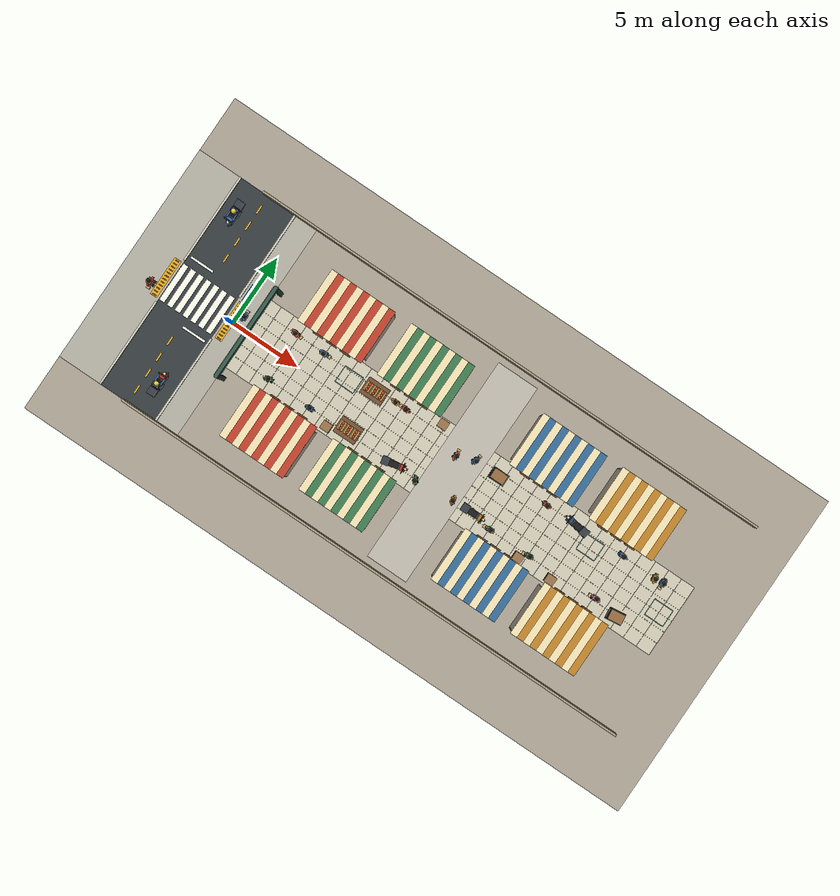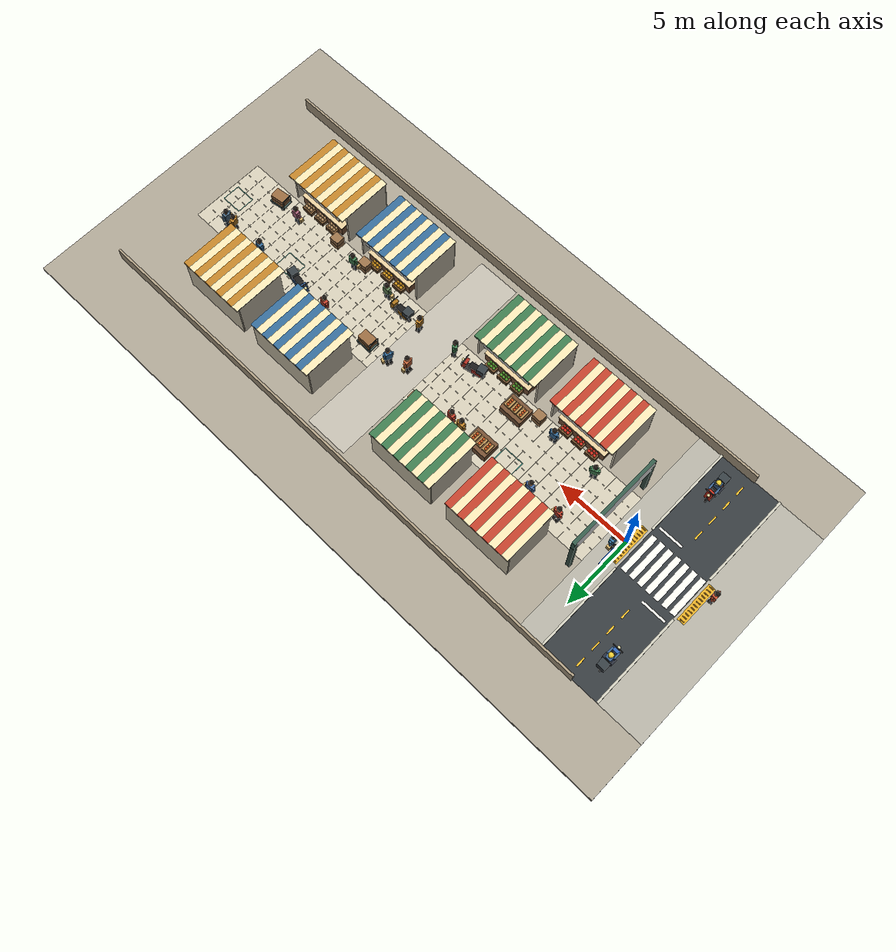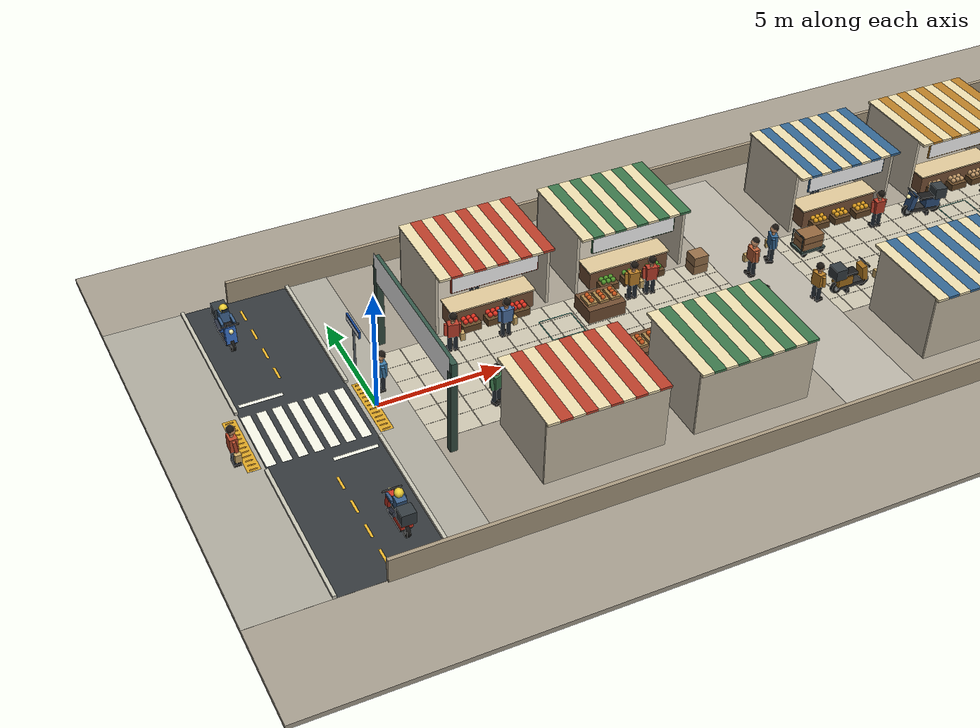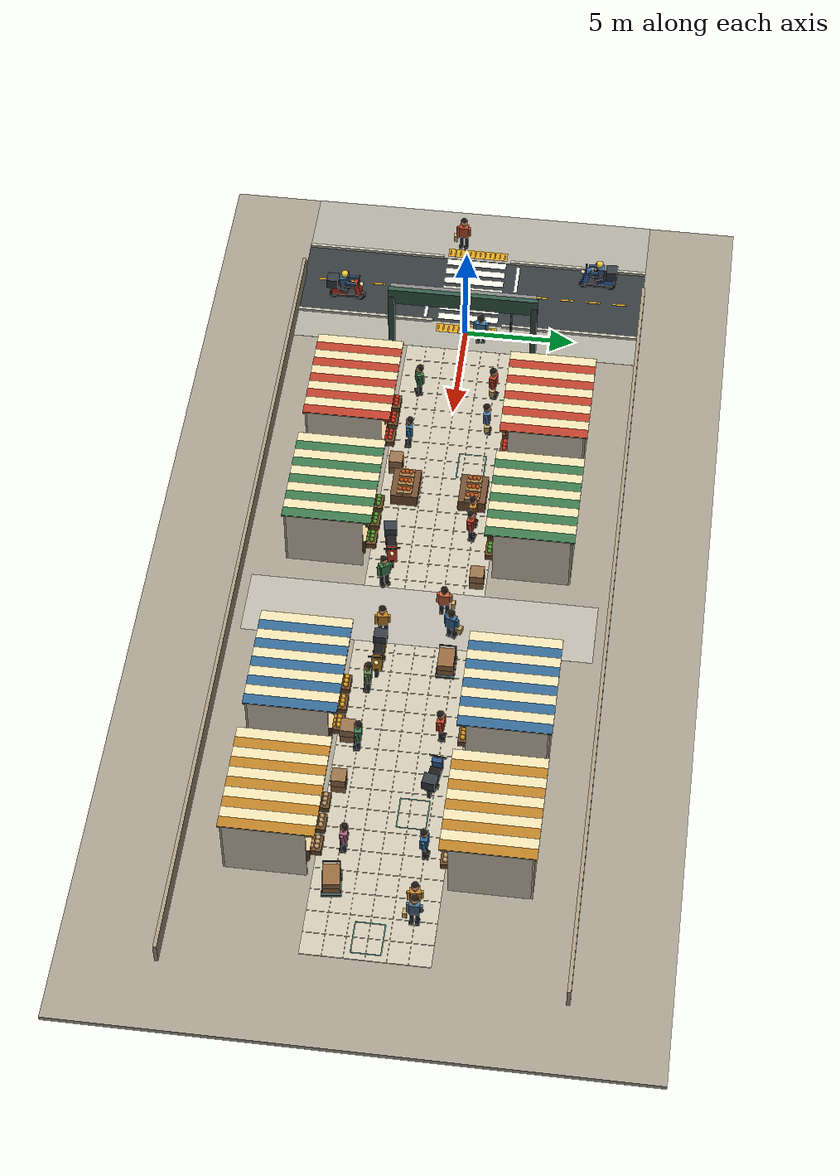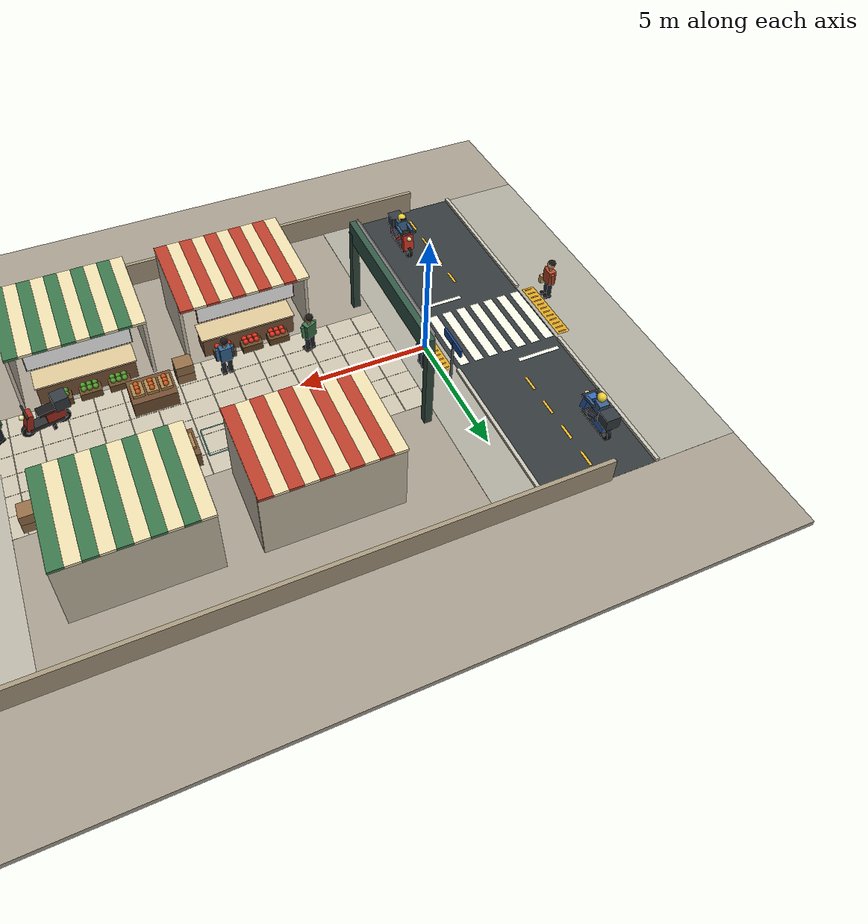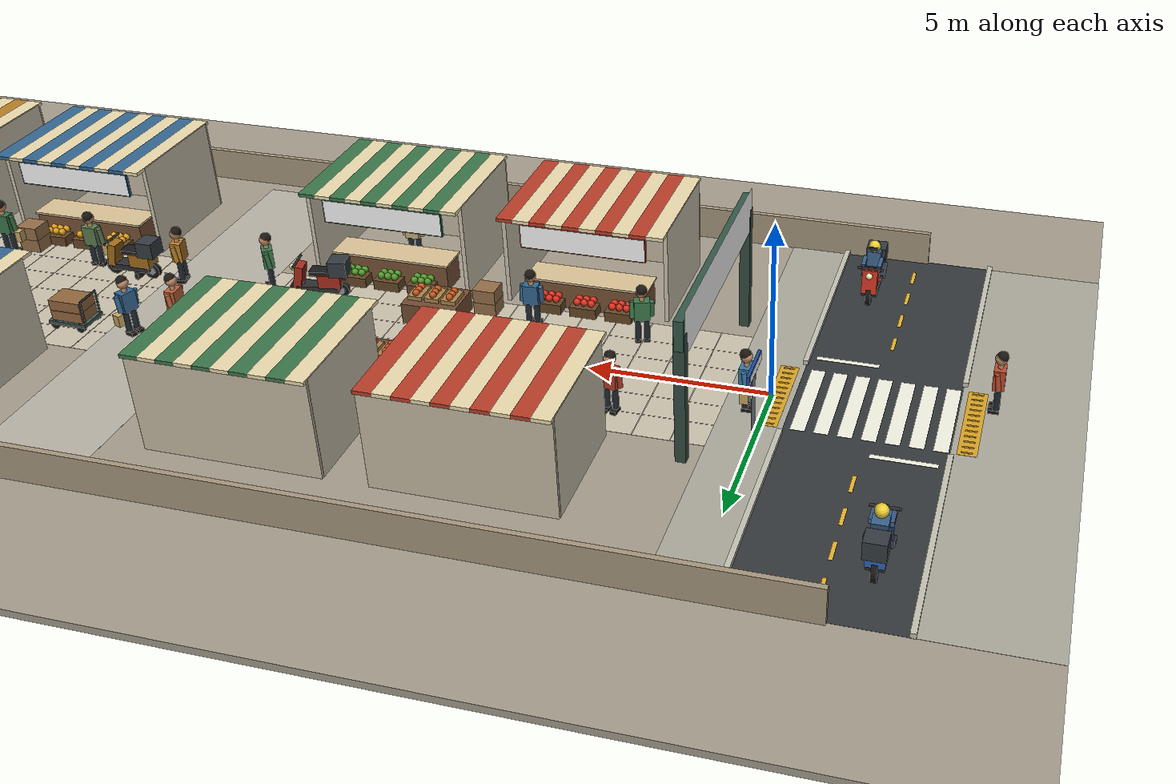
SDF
<?xml version='1.0' encoding='utf-8'?>
<sdf version="1.10">
  <world name="swan_market">
    <physics name="market_physics" type="ignored">
      <max_step_size>0.001</max_step_size>
      <real_time_factor>1</real_time_factor>
    </physics>
    <plugin filename="gz-sim-physics-system" name="gz::sim::systems::Physics" />
    <plugin filename="gz-sim-user-commands-system" name="gz::sim::systems::UserCommands" />
    <plugin filename="gz-sim-scene-broadcaster-system" name="gz::sim::systems::SceneBroadcaster" />
    <plugin filename="gz-sim-sensors-system" name="gz::sim::systems::Sensors">
      <render_engine>ogre2</render_engine>
    </plugin>
    <scene>
      <ambient>0.65 0.65 0.65 1</ambient>
      <background>0.74 0.82 0.86 1</background>
      <shadows>true</shadows>
    </scene>
    <light name="sun" type="directional">
      <pose>0 0 15 0 0 0</pose>
      <direction>-.3 -.5 -1</direction>
      <diffuse>.85 .82 .75 1</diffuse>
      <specular>.1 .1 .1 1</specular>
      <cast_shadows>true</cast_shadows>
    </light>
    <model name="ground">
      <static>true</static>
      <pose>15 0 -0.1 0 0 0</pose>
      <link name="body">
        <collision name="box_collision">
          <pose>0 0 0 0 0 0</pose>
          <geometry>
            <box>
              <size>46 24 0.2</size>
            </box>
          </geometry>
        </collision>
        <visual name="box_visual">
          <pose>0 0 0 0 0 0</pose>
          <geometry>
            <box>
              <size>46 24 0.2</size>
            </box>
          </geometry>
          <material>
            <ambient>0.64 0.61 0.55 1</ambient>
            <diffuse>0.64 0.61 0.55 1</diffuse>
          </material>
        </visual>
      </link>
    </model>
    <model name="market_paving">
      <static>true</static>
      <pose>16 0 0.002 0 0 0</pose>
      <link name="body">
        <visual name="box_visual">
          <pose>0 0 0 0 0 0</pose>
          <geometry>
            <box>
              <size>36 5.2 0.004</size>
            </box>
          </geometry>
          <material>
            <ambient>0.79 0.76 0.68 1</ambient>
            <diffuse>0.79 0.76 0.68 1</diffuse>
          </material>
        </visual>
      </link>
    </model>
    <model name="paving_joint_-1">
      <static>true</static>
      <pose>-1 0 0.0045 0 0 0</pose>
      <link name="body">
        <visual name="box_visual">
          <pose>0 0 0 0 0 0</pose>
          <geometry>
            <box>
              <size>0.025 5.2 0.001</size>
            </box>
          </geometry>
          <material>
            <ambient>0.67 0.64 0.57 1</ambient>
            <diffuse>0.67 0.64 0.57 1</diffuse>
          </material>
        </visual>
      </link>
    </model>
    <model name="paving_joint_0">
      <static>true</static>
      <pose>0 0 0.0045 0 0 0</pose>
      <link name="body">
        <visual name="box_visual">
          <pose>0 0 0 0 0 0</pose>
          <geometry>
            <box>
              <size>0.025 5.2 0.001</size>
            </box>
          </geometry>
          <material>
            <ambient>0.67 0.64 0.57 1</ambient>
            <diffuse>0.67 0.64 0.57 1</diffuse>
          </material>
        </visual>
      </link>
    </model>
    <model name="paving_joint_1">
      <static>true</static>
      <pose>1 0 0.0045 0 0 0</pose>
      <link name="body">
        <visual name="box_visual">
          <pose>0 0 0 0 0 0</pose>
          <geometry>
            <box>
              <size>0.025 5.2 0.001</size>
            </box>
          </geometry>
          <material>
            <ambient>0.67 0.64 0.57 1</ambient>
            <diffuse>0.67 0.64 0.57 1</diffuse>
          </material>
        </visual>
      </link>
    </model>
    <model name="paving_joint_2">
      <static>true</static>
      <pose>2 0 0.0045 0 0 0</pose>
      <link name="body">
        <visual name="box_visual">
          <pose>0 0 0 0 0 0</pose>
          <geometry>
            <box>
              <size>0.025 5.2 0.001</size>
            </box>
          </geometry>
          <material>
            <ambient>0.67 0.64 0.57 1</ambient>
            <diffuse>0.67 0.64 0.57 1</diffuse>
          </material>
        </visual>
      </link>
    </model>
    <model name="paving_joint_3">
      <static>true</static>
      <pose>3 0 0.0045 0 0 0</pose>
      <link name="body">
        <visual name="box_visual">
          <pose>0 0 0 0 0 0</pose>
          <geometry>
            <box>
              <size>0.025 5.2 0.001</size>
            </box>
          </geometry>
          <material>
            <ambient>0.67 0.64 0.57 1</ambient>
            <diffuse>0.67 0.64 0.57 1</diffuse>
          </material>
        </visual>
      </link>
    </model>
    <model name="paving_joint_4">
      <static>true</static>
      <pose>4 0 0.0045 0 0 0</pose>
      <link name="body">
        <visual name="box_visual">
          <pose>0 0 0 0 0 0</pose>
          <geometry>
            <box>
              <size>0.025 5.2 0.001</size>
            </box>
          </geometry>
          <material>
            <ambient>0.67 0.64 0.57 1</ambient>
            <diffuse>0.67 0.64 0.57 1</diffuse>
          </material>
        </visual>
      </link>
    </model>
    <model name="paving_joint_5">
      <static>true</static>
      <pose>5 0 0.0045 0 0 0</pose>
      <link name="body">
        <visual name="box_visual">
          <pose>0 0 0 0 0 0</pose>
          <geometry>
            <box>
              <size>0.025 5.2 0.001</size>
            </box>
          </geometry>
          <material>
            <ambient>0.67 0.64 0.57 1</ambient>
            <diffuse>0.67 0.64 0.57 1</diffuse>
          </material>
        </visual>
      </link>
    </model>
    <model name="paving_joint_6">
      <static>true</static>
      <pose>6 0 0.0045 0 0 0</pose>
      <link name="body">
        <visual name="box_visual">
          <pose>0 0 0 0 0 0</pose>
          <geometry>
            <box>
              <size>0.025 5.2 0.001</size>
            </box>
          </geometry>
          <material>
            <ambient>0.67 0.64 0.57 1</ambient>
            <diffuse>0.67 0.64 0.57 1</diffuse>
          </material>
        </visual>
      </link>
    </model>
    <model name="paving_joint_7">
      <static>true</static>
      <pose>7 0 0.0045 0 0 0</pose>
      <link name="body">
        <visual name="box_visual">
          <pose>0 0 0 0 0 0</pose>
          <geometry>
            <box>
              <size>0.025 5.2 0.001</size>
            </box>
          </geometry>
          <material>
            <ambient>0.67 0.64 0.57 1</ambient>
            <diffuse>0.67 0.64 0.57 1</diffuse>
          </material>
        </visual>
      </link>
    </model>
    <model name="paving_joint_8">
      <static>true</static>
      <pose>8 0 0.0045 0 0 0</pose>
      <link name="body">
        <visual name="box_visual">
          <pose>0 0 0 0 0 0</pose>
          <geometry>
            <box>
              <size>0.025 5.2 0.001</size>
            </box>
          </geometry>
          <material>
            <ambient>0.67 0.64 0.57 1</ambient>
            <diffuse>0.67 0.64 0.57 1</diffuse>
          </material>
        </visual>
      </link>
    </model>
    <model name="paving_joint_9">
      <static>true</static>
      <pose>9 0 0.0045 0 0 0</pose>
      <link name="body">
        <visual name="box_visual">
          <pose>0 0 0 0 0 0</pose>
          <geometry>
            <box>
              <size>0.025 5.2 0.001</size>
            </box>
          </geometry>
          <material>
            <ambient>0.67 0.64 0.57 1</ambient>
            <diffuse>0.67 0.64 0.57 1</diffuse>
          </material>
        </visual>
      </link>
    </model>
    <model name="paving_joint_10">
      <static>true</static>
      <pose>10 0 0.0045 0 0 0</pose>
      <link name="body">
        <visual name="box_visual">
          <pose>0 0 0 0 0 0</pose>
          <geometry>
            <box>
              <size>0.025 5.2 0.001</size>
            </box>
          </geometry>
          <material>
            <ambient>0.67 0.64 0.57 1</ambient>
            <diffuse>0.67 0.64 0.57 1</diffuse>
          </material>
        </visual>
      </link>
    </model>
    <model name="paving_joint_11">
      <static>true</static>
      <pose>11 0 0.0045 0 0 0</pose>
      <link name="body">
        <visual name="box_visual">
          <pose>0 0 0 0 0 0</pose>
          <geometry>
            <box>
              <size>0.025 5.2 0.001</size>
            </box>
          </geometry>
          <material>
            <ambient>0.67 0.64 0.57 1</ambient>
            <diffuse>0.67 0.64 0.57 1</diffuse>
          </material>
        </visual>
      </link>
    </model>
    <model name="paving_joint_12">
      <static>true</static>
      <pose>12 0 0.0045 0 0 0</pose>
      <link name="body">
        <visual name="box_visual">
          <pose>0 0 0 0 0 0</pose>
          <geometry>
            <box>
              <size>0.025 5.2 0.001</size>
            </box>
          </geometry>
          <material>
            <ambient>0.67 0.64 0.57 1</ambient>
            <diffuse>0.67 0.64 0.57 1</diffuse>
          </material>
        </visual>
      </link>
    </model>
    <model name="paving_joint_13">
      <static>true</static>
      <pose>13 0 0.0045 0 0 0</pose>
      <link name="body">
        <visual name="box_visual">
          <pose>0 0 0 0 0 0</pose>
          <geometry>
            <box>
              <size>0.025 5.2 0.001</size>
            </box>
          </geometry>
          <material>
            <ambient>0.67 0.64 0.57 1</ambient>
            <diffuse>0.67 0.64 0.57 1</diffuse>
          </material>
        </visual>
      </link>
    </model>
    <model name="paving_joint_14">
      <static>true</static>
      <pose>14 0 0.0045 0 0 0</pose>
      <link name="body">
        <visual name="box_visual">
          <pose>0 0 0 0 0 0</pose>
          <geometry>
            <box>
              <size>0.025 5.2 0.001</size>
            </box>
          </geometry>
          <material>
            <ambient>0.67 0.64 0.57 1</ambient>
            <diffuse>0.67 0.64 0.57 1</diffuse>
          </material>
        </visual>
      </link>
    </model>
    <model name="paving_joint_15">
      <static>true</static>
      <pose>15 0 0.0045 0 0 0</pose>
      <link name="body">
        <visual name="box_visual">
          <pose>0 0 0 0 0 0</pose>
          <geometry>
            <box>
              <size>0.025 5.2 0.001</size>
            </box>
          </geometry>
          <material>
            <ambient>0.67 0.64 0.57 1</ambient>
            <diffuse>0.67 0.64 0.57 1</diffuse>
          </material>
        </visual>
      </link>
    </model>
    <model name="paving_joint_16">
      <static>true</static>
      <pose>16 0 0.0045 0 0 0</pose>
      <link name="body">
        <visual name="box_visual">
          <pose>0 0 0 0 0 0</pose>
          <geometry>
            <box>
              <size>0.025 5.2 0.001</size>
            </box>
          </geometry>
          <material>
            <ambient>0.67 0.64 0.57 1</ambient>
            <diffuse>0.67 0.64 0.57 1</diffuse>
          </material>
        </visual>
      </link>
    </model>
    <model name="paving_joint_17">
      <static>true</static>
      <pose>17 0 0.0045 0 0 0</pose>
      <link name="body">
        <visual name="box_visual">
          <pose>0 0 0 0 0 0</pose>
          <geometry>
            <box>
              <size>0.025 5.2 0.001</size>
            </box>
          </geometry>
          <material>
            <ambient>0.67 0.64 0.57 1</ambient>
            <diffuse>0.67 0.64 0.57 1</diffuse>
          </material>
        </visual>
      </link>
    </model>
    <model name="paving_joint_18">
      <static>true</static>
      <pose>18 0 0.0045 0 0 0</pose>
      <link name="body">
        <visual name="box_visual">
          <pose>0 0 0 0 0 0</pose>
          <geometry>
            <box>
              <size>0.025 5.2 0.001</size>
            </box>
          </geometry>
          <material>
            <ambient>0.67 0.64 0.57 1</ambient>
            <diffuse>0.67 0.64 0.57 1</diffuse>
          </material>
        </visual>
      </link>
    </model>
    <model name="paving_joint_19">
      <static>true</static>
      <pose>19 0 0.0045 0 0 0</pose>
      <link name="body">
        <visual name="box_visual">
          <pose>0 0 0 0 0 0</pose>
          <geometry>
            <box>
              <size>0.025 5.2 0.001</size>
            </box>
          </geometry>
          <material>
            <ambient>0.67 0.64 0.57 1</ambient>
            <diffuse>0.67 0.64 0.57 1</diffuse>
          </material>
        </visual>
      </link>
    </model>
    <model name="paving_joint_20">
      <static>true</static>
      <pose>20 0 0.0045 0 0 0</pose>
      <link name="body">
        <visual name="box_visual">
          <pose>0 0 0 0 0 0</pose>
          <geometry>
            <box>
              <size>0.025 5.2 0.001</size>
            </box>
          </geometry>
          <material>
            <ambient>0.67 0.64 0.57 1</ambient>
            <diffuse>0.67 0.64 0.57 1</diffuse>
          </material>
        </visual>
      </link>
    </model>
    <model name="paving_joint_21">
      <static>true</static>
      <pose>21 0 0.0045 0 0 0</pose>
      <link name="body">
        <visual name="box_visual">
          <pose>0 0 0 0 0 0</pose>
          <geometry>
            <box>
              <size>0.025 5.2 0.001</size>
            </box>
          </geometry>
          <material>
            <ambient>0.67 0.64 0.57 1</ambient>
            <diffuse>0.67 0.64 0.57 1</diffuse>
          </material>
        </visual>
      </link>
    </model>
    <model name="paving_joint_22">
      <static>true</static>
      <pose>22 0 0.0045 0 0 0</pose>
      <link name="body">
        <visual name="box_visual">
          <pose>0 0 0 0 0 0</pose>
          <geometry>
            <box>
              <size>0.025 5.2 0.001</size>
            </box>
          </geometry>
          <material>
            <ambient>0.67 0.64 0.57 1</ambient>
            <diffuse>0.67 0.64 0.57 1</diffuse>
          </material>
        </visual>
      </link>
    </model>
    <model name="paving_joint_23">
      <static>true</static>
      <pose>23 0 0.0045 0 0 0</pose>
      <link name="body">
        <visual name="box_visual">
          <pose>0 0 0 0 0 0</pose>
          <geometry>
            <box>
              <size>0.025 5.2 0.001</size>
            </box>
          </geometry>
          <material>
            <ambient>0.67 0.64 0.57 1</ambient>
            <diffuse>0.67 0.64 0.57 1</diffuse>
          </material>
        </visual>
      </link>
    </model>
    <model name="paving_joint_24">
      <static>true</static>
      <pose>24 0 0.0045 0 0 0</pose>
      <link name="body">
        <visual name="box_visual">
          <pose>0 0 0 0 0 0</pose>
          <geometry>
            <box>
              <size>0.025 5.2 0.001</size>
            </box>
          </geometry>
          <material>
            <ambient>0.67 0.64 0.57 1</ambient>
            <diffuse>0.67 0.64 0.57 1</diffuse>
          </material>
        </visual>
      </link>
    </model>
    <model name="paving_joint_25">
      <static>true</static>
      <pose>25 0 0.0045 0 0 0</pose>
      <link name="body">
        <visual name="box_visual">
          <pose>0 0 0 0 0 0</pose>
          <geometry>
            <box>
              <size>0.025 5.2 0.001</size>
            </box>
          </geometry>
          <material>
            <ambient>0.67 0.64 0.57 1</ambient>
            <diffuse>0.67 0.64 0.57 1</diffuse>
          </material>
        </visual>
      </link>
    </model>
    <model name="paving_joint_26">
      <static>true</static>
      <pose>26 0 0.0045 0 0 0</pose>
      <link name="body">
        <visual name="box_visual">
          <pose>0 0 0 0 0 0</pose>
          <geometry>
            <box>
              <size>0.025 5.2 0.001</size>
            </box>
          </geometry>
          <material>
            <ambient>0.67 0.64 0.57 1</ambient>
            <diffuse>0.67 0.64 0.57 1</diffuse>
          </material>
        </visual>
      </link>
    </model>
    <model name="paving_joint_27">
      <static>true</static>
      <pose>27 0 0.0045 0 0 0</pose>
      <link name="body">
        <visual name="box_visual">
          <pose>0 0 0 0 0 0</pose>
          <geometry>
            <box>
              <size>0.025 5.2 0.001</size>
            </box>
          </geometry>
          <material>
            <ambient>0.67 0.64 0.57 1</ambient>
            <diffuse>0.67 0.64 0.57 1</diffuse>
          </material>
        </visual>
      </link>
    </model>
    <model name="paving_joint_28">
      <static>true</static>
      <pose>28 0 0.0045 0 0 0</pose>
      <link name="body">
        <visual name="box_visual">
          <pose>0 0 0 0 0 0</pose>
          <geometry>
            <box>
              <size>0.025 5.2 0.001</size>
            </box>
          </geometry>
          <material>
            <ambient>0.67 0.64 0.57 1</ambient>
            <diffuse>0.67 0.64 0.57 1</diffuse>
          </material>
        </visual>
      </link>
    </model>
    <model name="paving_joint_29">
      <static>true</static>
      <pose>29 0 0.0045 0 0 0</pose>
      <link name="body">
        <visual name="box_visual">
          <pose>0 0 0 0 0 0</pose>
          <geometry>
            <box>
              <size>0.025 5.2 0.001</size>
            </box>
          </geometry>
          <material>
            <ambient>0.67 0.64 0.57 1</ambient>
            <diffuse>0.67 0.64 0.57 1</diffuse>
          </material>
        </visual>
      </link>
    </model>
    <model name="paving_joint_30">
      <static>true</static>
      <pose>30 0 0.0045 0 0 0</pose>
      <link name="body">
        <visual name="box_visual">
          <pose>0 0 0 0 0 0</pose>
          <geometry>
            <box>
              <size>0.025 5.2 0.001</size>
            </box>
          </geometry>
          <material>
            <ambient>0.67 0.64 0.57 1</ambient>
            <diffuse>0.67 0.64 0.57 1</diffuse>
          </material>
        </visual>
      </link>
    </model>
    <model name="paving_joint_31">
      <static>true</static>
      <pose>31 0 0.0045 0 0 0</pose>
      <link name="body">
        <visual name="box_visual">
          <pose>0 0 0 0 0 0</pose>
          <geometry>
            <box>
              <size>0.025 5.2 0.001</size>
            </box>
          </geometry>
          <material>
            <ambient>0.67 0.64 0.57 1</ambient>
            <diffuse>0.67 0.64 0.57 1</diffuse>
          </material>
        </visual>
      </link>
    </model>
    <model name="paving_joint_32">
      <static>true</static>
      <pose>32 0 0.0045 0 0 0</pose>
      <link name="body">
        <visual name="box_visual">
          <pose>0 0 0 0 0 0</pose>
          <geometry>
            <box>
              <size>0.025 5.2 0.001</size>
            </box>
          </geometry>
          <material>
            <ambient>0.67 0.64 0.57 1</ambient>
            <diffuse>0.67 0.64 0.57 1</diffuse>
          </material>
        </visual>
      </link>
    </model>
    <model name="paving_joint_33">
      <static>true</static>
      <pose>33 0 0.0045 0 0 0</pose>
      <link name="body">
        <visual name="box_visual">
          <pose>0 0 0 0 0 0</pose>
          <geometry>
            <box>
              <size>0.025 5.2 0.001</size>
            </box>
          </geometry>
          <material>
            <ambient>0.67 0.64 0.57 1</ambient>
            <diffuse>0.67 0.64 0.57 1</diffuse>
          </material>
        </visual>
      </link>
    </model>
    <model name="paving_joint_34">
      <static>true</static>
      <pose>34 0 0.0045 0 0 0</pose>
      <link name="body">
        <visual name="box_visual">
          <pose>0 0 0 0 0 0</pose>
          <geometry>
            <box>
              <size>0.025 5.2 0.001</size>
            </box>
          </geometry>
          <material>
            <ambient>0.67 0.64 0.57 1</ambient>
            <diffuse>0.67 0.64 0.57 1</diffuse>
          </material>
        </visual>
      </link>
    </model>
    <model name="paving_seam_-1.7">
      <static>true</static>
      <pose>16 -1.7 0.0045 0 0 0</pose>
      <link name="body">
        <visual name="box_visual">
          <pose>0 0 0 0 0 0</pose>
          <geometry>
            <box>
              <size>36 0.015 0.001</size>
            </box>
          </geometry>
          <material>
            <ambient>0.68 0.65 0.58 1</ambient>
            <diffuse>0.68 0.65 0.58 1</diffuse>
          </material>
        </visual>
      </link>
    </model>
    <model name="paving_seam_-0.85">
      <static>true</static>
      <pose>16 -0.85 0.0045 0 0 0</pose>
      <link name="body">
        <visual name="box_visual">
          <pose>0 0 0 0 0 0</pose>
          <geometry>
            <box>
              <size>36 0.015 0.001</size>
            </box>
          </geometry>
          <material>
            <ambient>0.68 0.65 0.58 1</ambient>
            <diffuse>0.68 0.65 0.58 1</diffuse>
          </material>
        </visual>
      </link>
    </model>
    <model name="paving_seam_0">
      <static>true</static>
      <pose>16 0 0.0045 0 0 0</pose>
      <link name="body">
        <visual name="box_visual">
          <pose>0 0 0 0 0 0</pose>
          <geometry>
            <box>
              <size>36 0.015 0.001</size>
            </box>
          </geometry>
          <material>
            <ambient>0.68 0.65 0.58 1</ambient>
            <diffuse>0.68 0.65 0.58 1</diffuse>
          </material>
        </visual>
      </link>
    </model>
    <model name="paving_seam_0.85">
      <static>true</static>
      <pose>16 0.85 0.0045 0 0 0</pose>
      <link name="body">
        <visual name="box_visual">
          <pose>0 0 0 0 0 0</pose>
          <geometry>
            <box>
              <size>36 0.015 0.001</size>
            </box>
          </geometry>
          <material>
            <ambient>0.68 0.65 0.58 1</ambient>
            <diffuse>0.68 0.65 0.58 1</diffuse>
          </material>
        </visual>
      </link>
    </model>
    <model name="paving_seam_1.7">
      <static>true</static>
      <pose>16 1.7 0.0045 0 0 0</pose>
      <link name="body">
        <visual name="box_visual">
          <pose>0 0 0 0 0 0</pose>
          <geometry>
            <box>
              <size>36 0.015 0.001</size>
            </box>
          </geometry>
          <material>
            <ambient>0.68 0.65 0.58 1</ambient>
            <diffuse>0.68 0.65 0.58 1</diffuse>
          </material>
        </visual>
      </link>
    </model>
    <model name="entrance_road">
      <static>true</static>
      <pose>-2.7 0 0.01 0 0 0</pose>
      <link name="body">
        <visual name="box_visual">
          <pose>0 0 0 0 0 0</pose>
          <geometry>
            <box>
              <size>4.2 16 0.004</size>
            </box>
          </geometry>
          <material>
            <ambient>0.2 0.22 0.23 1</ambient>
            <diffuse>0.2 0.22 0.23 1</diffuse>
          </material>
        </visual>
      </link>
    </model>
    <model name="entrance_sidewalk_west">
      <static>true</static>
      <pose>-6.4 0 0.014 0 0 0</pose>
      <link name="body">
        <visual name="box_visual">
          <pose>0 0 0 0 0 0</pose>
          <geometry>
            <box>
              <size>3.2 16 0.004</size>
            </box>
          </geometry>
          <material>
            <ambient>0.67 0.66 0.61 1</ambient>
            <diffuse>0.67 0.66 0.61 1</diffuse>
          </material>
        </visual>
      </link>
    </model>
    <model name="entrance_sidewalk_market">
      <static>true</static>
      <pose>0.25 0 0.014 0 0 0</pose>
      <link name="body">
        <visual name="box_visual">
          <pose>0 0 0 0 0 0</pose>
          <geometry>
            <box>
              <size>1.7 16 0.004</size>
            </box>
          </geometry>
          <material>
            <ambient>0.67 0.66 0.61 1</ambient>
            <diffuse>0.67 0.66 0.61 1</diffuse>
          </material>
        </visual>
      </link>
    </model>
    <model name="crosswalk_stripe_0">
      <static>true</static>
      <pose>-4.57 0 0.016 0 0 0</pose>
      <link name="body">
        <visual name="box_visual">
          <pose>0 0 0 0 0 0</pose>
          <geometry>
            <box>
              <size>0.38 2.8 0.003</size>
            </box>
          </geometry>
          <material>
            <ambient>0.95 0.95 0.89 1</ambient>
            <diffuse>0.95 0.95 0.89 1</diffuse>
          </material>
        </visual>
      </link>
    </model>
    <model name="crosswalk_stripe_1">
      <static>true</static>
      <pose>-3.97 0 0.016 0 0 0</pose>
      <link name="body">
        <visual name="box_visual">
          <pose>0 0 0 0 0 0</pose>
          <geometry>
            <box>
              <size>0.38 2.8 0.003</size>
            </box>
          </geometry>
          <material>
            <ambient>0.95 0.95 0.89 1</ambient>
            <diffuse>0.95 0.95 0.89 1</diffuse>
          </material>
        </visual>
      </link>
    </model>
    <model name="crosswalk_stripe_2">
      <static>true</static>
      <pose>-3.37 0 0.016 0 0 0</pose>
      <link name="body">
        <visual name="box_visual">
          <pose>0 0 0 0 0 0</pose>
          <geometry>
            <box>
              <size>0.38 2.8 0.003</size>
            </box>
          </geometry>
          <material>
            <ambient>0.95 0.95 0.89 1</ambient>
            <diffuse>0.95 0.95 0.89 1</diffuse>
          </material>
        </visual>
      </link>
    </model>
    <model name="crosswalk_stripe_3">
      <static>true</static>
      <pose>-2.77 0 0.016 0 0 0</pose>
      <link name="body">
        <visual name="box_visual">
          <pose>0 0 0 0 0 0</pose>
          <geometry>
            <box>
              <size>0.38 2.8 0.003</size>
            </box>
          </geometry>
          <material>
            <ambient>0.95 0.95 0.89 1</ambient>
            <diffuse>0.95 0.95 0.89 1</diffuse>
          </material>
        </visual>
      </link>
    </model>
    <model name="crosswalk_stripe_4">
      <static>true</static>
      <pose>-2.17 0 0.016 0 0 0</pose>
      <link name="body">
        <visual name="box_visual">
          <pose>0 0 0 0 0 0</pose>
          <geometry>
            <box>
              <size>0.38 2.8 0.003</size>
            </box>
          </geometry>
          <material>
            <ambient>0.95 0.95 0.89 1</ambient>
            <diffuse>0.95 0.95 0.89 1</diffuse>
          </material>
        </visual>
      </link>
    </model>
    <model name="crosswalk_stripe_5">
      <static>true</static>
      <pose>-1.57 0 0.016 0 0 0</pose>
      <link name="body">
        <visual name="box_visual">
          <pose>0 0 0 0 0 0</pose>
          <geometry>
            <box>
              <size>0.38 2.8 0.003</size>
            </box>
          </geometry>
          <material>
            <ambient>0.95 0.95 0.89 1</ambient>
            <diffuse>0.95 0.95 0.89 1</diffuse>
          </material>
        </visual>
      </link>
    </model>
    <model name="crosswalk_stripe_6">
      <static>true</static>
      <pose>-0.97 0 0.016 0 0 0</pose>
      <link name="body">
        <visual name="box_visual">
          <pose>0 0 0 0 0 0</pose>
          <geometry>
            <box>
              <size>0.38 2.8 0.003</size>
            </box>
          </geometry>
          <material>
            <ambient>0.95 0.95 0.89 1</ambient>
            <diffuse>0.95 0.95 0.89 1</diffuse>
          </material>
        </visual>
      </link>
    </model>
    <model name="entrance_curb_-4.83_-1">
      <static>true</static>
      <pose>-4.83 -4.8 0.07 0 0 0</pose>
      <link name="body">
        <collision name="box_collision">
          <pose>0 0 0 0 0 0</pose>
          <geometry>
            <box>
              <size>0.14 6.4 0.14</size>
            </box>
          </geometry>
        </collision>
        <visual name="box_visual">
          <pose>0 0 0 0 0 0</pose>
          <geometry>
            <box>
              <size>0.14 6.4 0.14</size>
            </box>
          </geometry>
          <material>
            <ambient>0.77 0.76 0.7 1</ambient>
            <diffuse>0.77 0.76 0.7 1</diffuse>
          </material>
        </visual>
      </link>
    </model>
    <model name="entrance_curb_-0.57_-1">
      <static>true</static>
      <pose>-0.57 -4.8 0.07 0 0 0</pose>
      <link name="body">
        <collision name="box_collision">
          <pose>0 0 0 0 0 0</pose>
          <geometry>
            <box>
              <size>0.14 6.4 0.14</size>
            </box>
          </geometry>
        </collision>
        <visual name="box_visual">
          <pose>0 0 0 0 0 0</pose>
          <geometry>
            <box>
              <size>0.14 6.4 0.14</size>
            </box>
          </geometry>
          <material>
            <ambient>0.77 0.76 0.7 1</ambient>
            <diffuse>0.77 0.76 0.7 1</diffuse>
          </material>
        </visual>
      </link>
    </model>
    <model name="road_stop_line_-1">
      <static>true</static>
      <pose>-1.65 -2 0.016 0 0 0</pose>
      <link name="body">
        <visual name="box_visual">
          <pose>0 0 0 0 0 0</pose>
          <geometry>
            <box>
              <size>1.7 0.16 0.003</size>
            </box>
          </geometry>
          <material>
            <ambient>0.95 0.95 0.89 1</ambient>
            <diffuse>0.95 0.95 0.89 1</diffuse>
          </material>
        </visual>
      </link>
    </model>
    <model name="road_center_line_-1_0">
      <static>true</static>
      <pose>-2.7 -3.2 0.016 0 0 0</pose>
      <link name="body">
        <visual name="box_visual">
          <pose>0 0 0 0 0 0</pose>
          <geometry>
            <box>
              <size>0.1 0.65 0.003</size>
            </box>
          </geometry>
          <material>
            <ambient>0.91 0.7 0.16 1</ambient>
            <diffuse>0.91 0.7 0.16 1</diffuse>
          </material>
        </visual>
      </link>
    </model>
    <model name="road_center_line_-1_1">
      <static>true</static>
      <pose>-2.7 -4.45 0.016 0 0 0</pose>
      <link name="body">
        <visual name="box_visual">
          <pose>0 0 0 0 0 0</pose>
          <geometry>
            <box>
              <size>0.1 0.65 0.003</size>
            </box>
          </geometry>
          <material>
            <ambient>0.91 0.7 0.16 1</ambient>
            <diffuse>0.91 0.7 0.16 1</diffuse>
          </material>
        </visual>
      </link>
    </model>
    <model name="road_center_line_-1_2">
      <static>true</static>
      <pose>-2.7 -5.7 0.016 0 0 0</pose>
      <link name="body">
        <visual name="box_visual">
          <pose>0 0 0 0 0 0</pose>
          <geometry>
            <box>
              <size>0.1 0.65 0.003</size>
            </box>
          </geometry>
          <material>
            <ambient>0.91 0.7 0.16 1</ambient>
            <diffuse>0.91 0.7 0.16 1</diffuse>
          </material>
        </visual>
      </link>
    </model>
    <model name="road_center_line_-1_3">
      <static>true</static>
      <pose>-2.7 -6.95 0.016 0 0 0</pose>
      <link name="body">
        <visual name="box_visual">
          <pose>0 0 0 0 0 0</pose>
          <geometry>
            <box>
              <size>0.1 0.65 0.003</size>
            </box>
          </geometry>
          <material>
            <ambient>0.91 0.7 0.16 1</ambient>
            <diffuse>0.91 0.7 0.16 1</diffuse>
          </material>
        </visual>
      </link>
    </model>
    <model name="entrance_curb_-4.83_1">
      <static>true</static>
      <pose>-4.83 4.8 0.07 0 0 0</pose>
      <link name="body">
        <collision name="box_collision">
          <pose>0 0 0 0 0 0</pose>
          <geometry>
            <box>
              <size>0.14 6.4 0.14</size>
            </box>
          </geometry>
        </collision>
        <visual name="box_visual">
          <pose>0 0 0 0 0 0</pose>
          <geometry>
            <box>
              <size>0.14 6.4 0.14</size>
            </box>
          </geometry>
          <material>
            <ambient>0.77 0.76 0.7 1</ambient>
            <diffuse>0.77 0.76 0.7 1</diffuse>
          </material>
        </visual>
      </link>
    </model>
    <model name="entrance_curb_-0.57_1">
      <static>true</static>
      <pose>-0.57 4.8 0.07 0 0 0</pose>
      <link name="body">
        <collision name="box_collision">
          <pose>0 0 0 0 0 0</pose>
          <geometry>
            <box>
              <size>0.14 6.4 0.14</size>
            </box>
          </geometry>
        </collision>
        <visual name="box_visual">
          <pose>0 0 0 0 0 0</pose>
          <geometry>
            <box>
              <size>0.14 6.4 0.14</size>
            </box>
          </geometry>
          <material>
            <ambient>0.77 0.76 0.7 1</ambient>
            <diffuse>0.77 0.76 0.7 1</diffuse>
          </material>
        </visual>
      </link>
    </model>
    <model name="road_stop_line_1">
      <static>true</static>
      <pose>-3.75 2 0.016 0 0 0</pose>
      <link name="body">
        <visual name="box_visual">
          <pose>0 0 0 0 0 0</pose>
          <geometry>
            <box>
              <size>1.7 0.16 0.003</size>
            </box>
          </geometry>
          <material>
            <ambient>0.95 0.95 0.89 1</ambient>
            <diffuse>0.95 0.95 0.89 1</diffuse>
          </material>
        </visual>
      </link>
    </model>
    <model name="road_center_line_1_0">
      <static>true</static>
      <pose>-2.7 3.2 0.016 0 0 0</pose>
      <link name="body">
        <visual name="box_visual">
          <pose>0 0 0 0 0 0</pose>
          <geometry>
            <box>
              <size>0.1 0.65 0.003</size>
            </box>
          </geometry>
          <material>
            <ambient>0.91 0.7 0.16 1</ambient>
            <diffuse>0.91 0.7 0.16 1</diffuse>
          </material>
        </visual>
      </link>
    </model>
    <model name="road_center_line_1_1">
      <static>true</static>
      <pose>-2.7 4.45 0.016 0 0 0</pose>
      <link name="body">
        <visual name="box_visual">
          <pose>0 0 0 0 0 0</pose>
          <geometry>
            <box>
              <size>0.1 0.65 0.003</size>
            </box>
          </geometry>
          <material>
            <ambient>0.91 0.7 0.16 1</ambient>
            <diffuse>0.91 0.7 0.16 1</diffuse>
          </material>
        </visual>
      </link>
    </model>
    <model name="road_center_line_1_2">
      <static>true</static>
      <pose>-2.7 5.7 0.016 0 0 0</pose>
      <link name="body">
        <visual name="box_visual">
          <pose>0 0 0 0 0 0</pose>
          <geometry>
            <box>
              <size>0.1 0.65 0.003</size>
            </box>
          </geometry>
          <material>
            <ambient>0.91 0.7 0.16 1</ambient>
            <diffuse>0.91 0.7 0.16 1</diffuse>
          </material>
        </visual>
      </link>
    </model>
    <model name="road_center_line_1_3">
      <static>true</static>
      <pose>-2.7 6.95 0.016 0 0 0</pose>
      <link name="body">
        <visual name="box_visual">
          <pose>0 0 0 0 0 0</pose>
          <geometry>
            <box>
              <size>0.1 0.65 0.003</size>
            </box>
          </geometry>
          <material>
            <ambient>0.91 0.7 0.16 1</ambient>
            <diffuse>0.91 0.7 0.16 1</diffuse>
          </material>
        </visual>
      </link>
    </model>
    <model name="crosswalk_tactile_0">
      <static>true</static>
      <pose>-5.2 0 0.019 0 0 0</pose>
      <link name="body">
        <visual name="box_visual">
          <pose>0 0 0 0 0 0</pose>
          <geometry>
            <box>
              <size>0.5 2.8 0.003</size>
            </box>
          </geometry>
          <material>
            <ambient>0.85 0.64 0.14 1</ambient>
            <diffuse>0.85 0.64 0.14 1</diffuse>
          </material>
        </visual>
      </link>
    </model>
    <model name="tactile_mark_0_0">
      <static>true</static>
      <pose>-5.2 -1.3 0.022 0 0 0</pose>
      <link name="body">
        <visual name="box_visual">
          <pose>0 0 0 0 0 0</pose>
          <geometry>
            <box>
              <size>0.3 0.055 0.002</size>
            </box>
          </geometry>
          <material>
            <ambient>0.69 0.47 0.1 1</ambient>
            <diffuse>0.69 0.47 0.1 1</diffuse>
          </material>
        </visual>
      </link>
    </model>
    <model name="tactile_mark_0_1">
      <static>true</static>
      <pose>-5.2 -1.065 0.022 0 0 0</pose>
      <link name="body">
        <visual name="box_visual">
          <pose>0 0 0 0 0 0</pose>
          <geometry>
            <box>
              <size>0.3 0.055 0.002</size>
            </box>
          </geometry>
          <material>
            <ambient>0.69 0.47 0.1 1</ambient>
            <diffuse>0.69 0.47 0.1 1</diffuse>
          </material>
        </visual>
      </link>
    </model>
    <model name="tactile_mark_0_2">
      <static>true</static>
      <pose>-5.2 -0.83 0.022 0 0 0</pose>
      <link name="body">
        <visual name="box_visual">
          <pose>0 0 0 0 0 0</pose>
          <geometry>
            <box>
              <size>0.3 0.055 0.002</size>
            </box>
          </geometry>
          <material>
            <ambient>0.69 0.47 0.1 1</ambient>
            <diffuse>0.69 0.47 0.1 1</diffuse>
          </material>
        </visual>
      </link>
    </model>
    <model name="tactile_mark_0_3">
      <static>true</static>
      <pose>-5.2 -0.595 0.022 0 0 0</pose>
      <link name="body">
        <visual name="box_visual">
          <pose>0 0 0 0 0 0</pose>
          <geometry>
            <box>
              <size>0.3 0.055 0.002</size>
            </box>
          </geometry>
          <material>
            <ambient>0.69 0.47 0.1 1</ambient>
            <diffuse>0.69 0.47 0.1 1</diffuse>
          </material>
        </visual>
      </link>
    </model>
    <model name="tactile_mark_0_4">
      <static>true</static>
      <pose>-5.2 -0.36 0.022 0 0 0</pose>
      <link name="body">
        <visual name="box_visual">
          <pose>0 0 0 0 0 0</pose>
          <geometry>
            <box>
              <size>0.3 0.055 0.002</size>
            </box>
          </geometry>
          <material>
            <ambient>0.69 0.47 0.1 1</ambient>
            <diffuse>0.69 0.47 0.1 1</diffuse>
          </material>
        </visual>
      </link>
    </model>
    <model name="tactile_mark_0_5">
      <static>true</static>
      <pose>-5.2 -0.125 0.022 0 0 0</pose>
      <link name="body">
        <visual name="box_visual">
          <pose>0 0 0 0 0 0</pose>
          <geometry>
            <box>
              <size>0.3 0.055 0.002</size>
            </box>
          </geometry>
          <material>
            <ambient>0.69 0.47 0.1 1</ambient>
            <diffuse>0.69 0.47 0.1 1</diffuse>
          </material>
        </visual>
      </link>
    </model>
    <model name="tactile_mark_0_6">
      <static>true</static>
      <pose>-5.2 0.11 0.022 0 0 0</pose>
      <link name="body">
        <visual name="box_visual">
          <pose>0 0 0 0 0 0</pose>
          <geometry>
            <box>
              <size>0.3 0.055 0.002</size>
            </box>
          </geometry>
          <material>
            <ambient>0.69 0.47 0.1 1</ambient>
            <diffuse>0.69 0.47 0.1 1</diffuse>
          </material>
        </visual>
      </link>
    </model>
    <model name="tactile_mark_0_7">
      <static>true</static>
      <pose>-5.2 0.345 0.022 0 0 0</pose>
      <link name="body">
        <visual name="box_visual">
          <pose>0 0 0 0 0 0</pose>
          <geometry>
            <box>
              <size>0.3 0.055 0.002</size>
            </box>
          </geometry>
          <material>
            <ambient>0.69 0.47 0.1 1</ambient>
            <diffuse>0.69 0.47 0.1 1</diffuse>
          </material>
        </visual>
      </link>
    </model>
    <model name="tactile_mark_0_8">
      <static>true</static>
      <pose>-5.2 0.58 0.022 0 0 0</pose>
      <link name="body">
        <visual name="box_visual">
          <pose>0 0 0 0 0 0</pose>
          <geometry>
            <box>
              <size>0.3 0.055 0.002</size>
            </box>
          </geometry>
          <material>
            <ambient>0.69 0.47 0.1 1</ambient>
            <diffuse>0.69 0.47 0.1 1</diffuse>
          </material>
        </visual>
      </link>
    </model>
    <model name="tactile_mark_0_9">
      <static>true</static>
      <pose>-5.2 0.815 0.022 0 0 0</pose>
      <link name="body">
        <visual name="box_visual">
          <pose>0 0 0 0 0 0</pose>
          <geometry>
            <box>
              <size>0.3 0.055 0.002</size>
            </box>
          </geometry>
          <material>
            <ambient>0.69 0.47 0.1 1</ambient>
            <diffuse>0.69 0.47 0.1 1</diffuse>
          </material>
        </visual>
      </link>
    </model>
    <model name="tactile_mark_0_10">
      <static>true</static>
      <pose>-5.2 1.05 0.022 0 0 0</pose>
      <link name="body">
        <visual name="box_visual">
          <pose>0 0 0 0 0 0</pose>
          <geometry>
            <box>
              <size>0.3 0.055 0.002</size>
            </box>
          </geometry>
          <material>
            <ambient>0.69 0.47 0.1 1</ambient>
            <diffuse>0.69 0.47 0.1 1</diffuse>
          </material>
        </visual>
      </link>
    </model>
    <model name="tactile_mark_0_11">
      <static>true</static>
      <pose>-5.2 1.285 0.022 0 0 0</pose>
      <link name="body">
        <visual name="box_visual">
          <pose>0 0 0 0 0 0</pose>
          <geometry>
            <box>
              <size>0.3 0.055 0.002</size>
            </box>
          </geometry>
          <material>
            <ambient>0.69 0.47 0.1 1</ambient>
            <diffuse>0.69 0.47 0.1 1</diffuse>
          </material>
        </visual>
      </link>
    </model>
    <model name="crosswalk_tactile_1">
      <static>true</static>
      <pose>-0.2 0 0.019 0 0 0</pose>
      <link name="body">
        <visual name="box_visual">
          <pose>0 0 0 0 0 0</pose>
          <geometry>
            <box>
              <size>0.5 2.8 0.003</size>
            </box>
          </geometry>
          <material>
            <ambient>0.85 0.64 0.14 1</ambient>
            <diffuse>0.85 0.64 0.14 1</diffuse>
          </material>
        </visual>
      </link>
    </model>
    <model name="tactile_mark_1_0">
      <static>true</static>
      <pose>-0.2 -1.3 0.022 0 0 0</pose>
      <link name="body">
        <visual name="box_visual">
          <pose>0 0 0 0 0 0</pose>
          <geometry>
            <box>
              <size>0.3 0.055 0.002</size>
            </box>
          </geometry>
          <material>
            <ambient>0.69 0.47 0.1 1</ambient>
            <diffuse>0.69 0.47 0.1 1</diffuse>
          </material>
        </visual>
      </link>
    </model>
    <model name="tactile_mark_1_1">
      <static>true</static>
      <pose>-0.2 -1.065 0.022 0 0 0</pose>
      <link name="body">
        <visual name="box_visual">
          <pose>0 0 0 0 0 0</pose>
          <geometry>
            <box>
              <size>0.3 0.055 0.002</size>
            </box>
          </geometry>
          <material>
            <ambient>0.69 0.47 0.1 1</ambient>
            <diffuse>0.69 0.47 0.1 1</diffuse>
          </material>
        </visual>
      </link>
    </model>
    <model name="tactile_mark_1_2">
      <static>true</static>
      <pose>-0.2 -0.83 0.022 0 0 0</pose>
      <link name="body">
        <visual name="box_visual">
          <pose>0 0 0 0 0 0</pose>
          <geometry>
            <box>
              <size>0.3 0.055 0.002</size>
            </box>
          </geometry>
          <material>
            <ambient>0.69 0.47 0.1 1</ambient>
            <diffuse>0.69 0.47 0.1 1</diffuse>
          </material>
        </visual>
      </link>
    </model>
    <model name="tactile_mark_1_3">
      <static>true</static>
      <pose>-0.2 -0.595 0.022 0 0 0</pose>
      <link name="body">
        <visual name="box_visual">
          <pose>0 0 0 0 0 0</pose>
          <geometry>
            <box>
              <size>0.3 0.055 0.002</size>
            </box>
          </geometry>
          <material>
            <ambient>0.69 0.47 0.1 1</ambient>
            <diffuse>0.69 0.47 0.1 1</diffuse>
          </material>
        </visual>
      </link>
    </model>
    <model name="tactile_mark_1_4">
      <static>true</static>
      <pose>-0.2 -0.36 0.022 0 0 0</pose>
      <link name="body">
        <visual name="box_visual">
          <pose>0 0 0 0 0 0</pose>
          <geometry>
            <box>
              <size>0.3 0.055 0.002</size>
            </box>
          </geometry>
          <material>
            <ambient>0.69 0.47 0.1 1</ambient>
            <diffuse>0.69 0.47 0.1 1</diffuse>
          </material>
        </visual>
      </link>
    </model>
    <model name="tactile_mark_1_5">
      <static>true</static>
      <pose>-0.2 -0.125 0.022 0 0 0</pose>
      <link name="body">
        <visual name="box_visual">
          <pose>0 0 0 0 0 0</pose>
          <geometry>
            <box>
              <size>0.3 0.055 0.002</size>
            </box>
          </geometry>
          <material>
            <ambient>0.69 0.47 0.1 1</ambient>
            <diffuse>0.69 0.47 0.1 1</diffuse>
          </material>
        </visual>
      </link>
    </model>
    <model name="tactile_mark_1_6">
      <static>true</static>
      <pose>-0.2 0.11 0.022 0 0 0</pose>
      <link name="body">
        <visual name="box_visual">
          <pose>0 0 0 0 0 0</pose>
          <geometry>
            <box>
              <size>0.3 0.055 0.002</size>
            </box>
          </geometry>
          <material>
            <ambient>0.69 0.47 0.1 1</ambient>
            <diffuse>0.69 0.47 0.1 1</diffuse>
          </material>
        </visual>
      </link>
    </model>
    <model name="tactile_mark_1_7">
      <static>true</static>
      <pose>-0.2 0.345 0.022 0 0 0</pose>
      <link name="body">
        <visual name="box_visual">
          <pose>0 0 0 0 0 0</pose>
          <geometry>
            <box>
              <size>0.3 0.055 0.002</size>
            </box>
          </geometry>
          <material>
            <ambient>0.69 0.47 0.1 1</ambient>
            <diffuse>0.69 0.47 0.1 1</diffuse>
          </material>
        </visual>
      </link>
    </model>
    <model name="tactile_mark_1_8">
      <static>true</static>
      <pose>-0.2 0.58 0.022 0 0 0</pose>
      <link name="body">
        <visual name="box_visual">
          <pose>0 0 0 0 0 0</pose>
          <geometry>
            <box>
              <size>0.3 0.055 0.002</size>
            </box>
          </geometry>
          <material>
            <ambient>0.69 0.47 0.1 1</ambient>
            <diffuse>0.69 0.47 0.1 1</diffuse>
          </material>
        </visual>
      </link>
    </model>
    <model name="tactile_mark_1_9">
      <static>true</static>
      <pose>-0.2 0.815 0.022 0 0 0</pose>
      <link name="body">
        <visual name="box_visual">
          <pose>0 0 0 0 0 0</pose>
          <geometry>
            <box>
              <size>0.3 0.055 0.002</size>
            </box>
          </geometry>
          <material>
            <ambient>0.69 0.47 0.1 1</ambient>
            <diffuse>0.69 0.47 0.1 1</diffuse>
          </material>
        </visual>
      </link>
    </model>
    <model name="tactile_mark_1_10">
      <static>true</static>
      <pose>-0.2 1.05 0.022 0 0 0</pose>
      <link name="body">
        <visual name="box_visual">
          <pose>0 0 0 0 0 0</pose>
          <geometry>
            <box>
              <size>0.3 0.055 0.002</size>
            </box>
          </geometry>
          <material>
            <ambient>0.69 0.47 0.1 1</ambient>
            <diffuse>0.69 0.47 0.1 1</diffuse>
          </material>
        </visual>
      </link>
    </model>
    <model name="tactile_mark_1_11">
      <static>true</static>
      <pose>-0.2 1.285 0.022 0 0 0</pose>
      <link name="body">
        <visual name="box_visual">
          <pose>0 0 0 0 0 0</pose>
          <geometry>
            <box>
              <size>0.3 0.055 0.002</size>
            </box>
          </geometry>
          <material>
            <ambient>0.69 0.47 0.1 1</ambient>
            <diffuse>0.69 0.47 0.1 1</diffuse>
          </material>
        </visual>
      </link>
    </model>
    <model name="crosswalk_sign_pole">
      <static>true</static>
      <pose>0 2.1 0 0 0 0</pose>
      <link name="body">
        <collision name="post_collision">
          <pose>0 0 1.1 0 0 0</pose>
          <geometry>
            <cylinder>
              <radius>0.045</radius>
              <length>2.2</length>
            </cylinder>
          </geometry>
        </collision>
        <visual name="post_visual">
          <pose>0 0 1.1 0 0 0</pose>
          <geometry>
            <cylinder>
              <radius>0.045</radius>
              <length>2.2</length>
            </cylinder>
          </geometry>
          <material>
            <ambient>0.35 0.38 0.4 1</ambient>
            <diffuse>0.35 0.38 0.4 1</diffuse>
          </material>
        </visual>
      </link>
    </model>
    <model name="crosswalk_sign_back">
      <static>true</static>
      <pose>0 2.1 2.15 0 0 0</pose>
      <link name="body">
        <collision name="box_collision">
          <pose>0 0 0 0 0 0</pose>
          <geometry>
            <box>
              <size>0.08 1.25 0.3</size>
            </box>
          </geometry>
        </collision>
        <visual name="box_visual">
          <pose>0 0 0 0 0 0</pose>
          <geometry>
            <box>
              <size>0.08 1.25 0.3</size>
            </box>
          </geometry>
          <material>
            <ambient>0.1 0.29 0.6 1</ambient>
            <diffuse>0.1 0.29 0.6 1</diffuse>
          </material>
        </visual>
      </link>
    </model>
    <model name="sign_crosswalk">
      <static>true</static>
      <pose>-0.048 2.1 2.15 0 0 -1.5708</pose>
      <link name="body">
        <visual name="lettering">
          <geometry>
            <mesh>
              <uri>model://swan_market_assets/meshes/crosswalk.dae</uri>
              <scale>1.2 1 0.22499999999999998</scale>
            </mesh>
          </geometry>
          <material>
            <ambient>1 1 1 1</ambient>
            <diffuse>1 1 1 1</diffuse>
            <emissive>0 0 0 1</emissive>
            <pbr>
              <metal>
                <albedo_map>model://swan_market_assets/materials/textures/crosswalk.png</albedo_map>
                <metalness>0</metalness>
                <roughness>1</roughness>
              </metal>
            </pbr>
          </material>
        </visual>
      </link>
    </model>
    <model name="cross_aisle">
      <static>true</static>
      <pose>17 0 0.006 0 0 0</pose>
      <link name="body">
        <visual name="box_visual">
          <pose>0 0 0 0 0 0</pose>
          <geometry>
            <box>
              <size>3 15 0.002</size>
            </box>
          </geometry>
          <material>
            <ambient>0.72 0.7 0.65 1</ambient>
            <diffuse>0.72 0.7 0.65 1</diffuse>
          </material>
        </visual>
      </link>
    </model>
    <model name="boundary_-1">
      <static>true</static>
      <pose>16 -8 0.5 0 0 0</pose>
      <link name="body">
        <collision name="box_collision">
          <pose>0 0 0 0 0 0</pose>
          <geometry>
            <box>
              <size>38 0.15 1</size>
            </box>
          </geometry>
        </collision>
        <visual name="box_visual">
          <pose>0 0 0 0 0 0</pose>
          <geometry>
            <box>
              <size>38 0.15 1</size>
            </box>
          </geometry>
          <material>
            <ambient>0.65 0.59 0.49 1</ambient>
            <diffuse>0.65 0.59 0.49 1</diffuse>
          </material>
        </visual>
      </link>
    </model>
    <model name="entrance_post_-1">
      <static>true</static>
      <pose>1.5 -3.25 1.8 0 0 0</pose>
      <link name="body">
        <collision name="box_collision">
          <pose>0 0 0 0 0 0</pose>
          <geometry>
            <box>
              <size>0.28 0.28 3.6</size>
            </box>
          </geometry>
        </collision>
        <visual name="box_visual">
          <pose>0 0 0 0 0 0</pose>
          <geometry>
            <box>
              <size>0.28 0.28 3.6</size>
            </box>
          </geometry>
          <material>
            <ambient>0.2 0.29 0.25 1</ambient>
            <diffuse>0.2 0.29 0.25 1</diffuse>
          </material>
        </visual>
      </link>
    </model>
    <model name="boundary_1">
      <static>true</static>
      <pose>16 8 0.5 0 0 0</pose>
      <link name="body">
        <collision name="box_collision">
          <pose>0 0 0 0 0 0</pose>
          <geometry>
            <box>
              <size>38 0.15 1</size>
            </box>
          </geometry>
        </collision>
        <visual name="box_visual">
          <pose>0 0 0 0 0 0</pose>
          <geometry>
            <box>
              <size>38 0.15 1</size>
            </box>
          </geometry>
          <material>
            <ambient>0.65 0.59 0.49 1</ambient>
            <diffuse>0.65 0.59 0.49 1</diffuse>
          </material>
        </visual>
      </link>
    </model>
    <model name="entrance_post_1">
      <static>true</static>
      <pose>1.5 3.25 1.8 0 0 0</pose>
      <link name="body">
        <collision name="box_collision">
          <pose>0 0 0 0 0 0</pose>
          <geometry>
            <box>
              <size>0.28 0.28 3.6</size>
            </box>
          </geometry>
        </collision>
        <visual name="box_visual">
          <pose>0 0 0 0 0 0</pose>
          <geometry>
            <box>
              <size>0.28 0.28 3.6</size>
            </box>
          </geometry>
          <material>
            <ambient>0.2 0.29 0.25 1</ambient>
            <diffuse>0.2 0.29 0.25 1</diffuse>
          </material>
        </visual>
      </link>
    </model>
    <model name="entrance_header">
      <static>true</static>
      <pose>1.5 0 3.6 0 0 0</pose>
      <link name="body">
        <collision name="box_collision">
          <pose>0 0 0 0 0 0</pose>
          <geometry>
            <box>
              <size>0.24 6.8 0.82</size>
            </box>
          </geometry>
        </collision>
        <visual name="box_visual">
          <pose>0 0 0 0 0 0</pose>
          <geometry>
            <box>
              <size>0.24 6.8 0.82</size>
            </box>
          </geometry>
          <material>
            <ambient>0.2 0.34 0.28 1</ambient>
            <diffuse>0.2 0.34 0.28 1</diffuse>
          </material>
        </visual>
      </link>
    </model>
    <model name="sign_entrance">
      <static>true</static>
      <pose>1.365 0 3.6 0 0 -1.5708</pose>
      <link name="body">
        <visual name="lettering">
          <geometry>
            <mesh>
              <uri>model://swan_market_assets/meshes/entrance.dae</uri>
              <scale>6.6 1 1.2374999999999998</scale>
            </mesh>
          </geometry>
          <material>
            <ambient>1 1 1 1</ambient>
            <diffuse>1 1 1 1</diffuse>
            <emissive>0 0 0 1</emissive>
            <pbr>
              <metal>
                <albedo_map>model://swan_market_assets/materials/textures/entrance.png</albedo_map>
                <metalness>0</metalness>
                <roughness>1</roughness>
              </metal>
            </pbr>
          </material>
        </visual>
      </link>
    </model>
    <model name="stall_00">
      <static>true</static>
      <pose>6 4.45 0 0 0 0</pose>
      <link name="body">
        <collision name="rear_collision">
          <pose>0 1.65 1.4 0 0 0</pose>
          <geometry>
            <box>
              <size>4.8 0.15 2.8</size>
            </box>
          </geometry>
        </collision>
        <visual name="rear_visual">
          <pose>0 1.65 1.4 0 0 0</pose>
          <geometry>
            <box>
              <size>4.8 0.15 2.8</size>
            </box>
          </geometry>
          <material>
            <ambient>0.78 0.74 0.65 1</ambient>
            <diffuse>0.78 0.74 0.65 1</diffuse>
          </material>
        </visual>
        <collision name="side_-2.35_collision">
          <pose>-2.35 0 1.4 0 0 0</pose>
          <geometry>
            <box>
              <size>0.12 3.3 2.8</size>
            </box>
          </geometry>
        </collision>
        <visual name="side_-2.35_visual">
          <pose>-2.35 0 1.4 0 0 0</pose>
          <geometry>
            <box>
              <size>0.12 3.3 2.8</size>
            </box>
          </geometry>
          <material>
            <ambient>0.81 0.77 0.69 1</ambient>
            <diffuse>0.81 0.77 0.69 1</diffuse>
          </material>
        </visual>
        <collision name="side_2.35_collision">
          <pose>2.35 0 1.4 0 0 0</pose>
          <geometry>
            <box>
              <size>0.12 3.3 2.8</size>
            </box>
          </geometry>
        </collision>
        <visual name="side_2.35_visual">
          <pose>2.35 0 1.4 0 0 0</pose>
          <geometry>
            <box>
              <size>0.12 3.3 2.8</size>
            </box>
          </geometry>
          <material>
            <ambient>0.81 0.77 0.69 1</ambient>
            <diffuse>0.81 0.77 0.69 1</diffuse>
          </material>
        </visual>
        <collision name="counter_collision">
          <pose>0 -1.22 0.4 0 0 0</pose>
          <geometry>
            <box>
              <size>3.5 0.85 0.8</size>
            </box>
          </geometry>
        </collision>
        <visual name="counter_visual">
          <pose>0 -1.22 0.4 0 0 0</pose>
          <geometry>
            <box>
              <size>3.5 0.85 0.8</size>
            </box>
          </geometry>
          <material>
            <ambient>0.47 0.32 0.21 1</ambient>
            <diffuse>0.47 0.32 0.21 1</diffuse>
          </material>
        </visual>
        <collision name="counter_top_collision">
          <pose>0 -1.22 0.83 0 0 0</pose>
          <geometry>
            <box>
              <size>3.6 0.95 0.06</size>
            </box>
          </geometry>
        </collision>
        <visual name="counter_top_visual">
          <pose>0 -1.22 0.83 0 0 0</pose>
          <geometry>
            <box>
              <size>3.6 0.95 0.06</size>
            </box>
          </geometry>
          <material>
            <ambient>0.86 0.77 0.59 1</ambient>
            <diffuse>0.86 0.77 0.59 1</diffuse>
          </material>
        </visual>
        <collision name="awning_0_collision">
          <pose>-2.16 -0.1 2.78 0 0 0</pose>
          <geometry>
            <box>
              <size>0.48 3.85 0.1</size>
            </box>
          </geometry>
        </collision>
        <visual name="awning_0_visual">
          <pose>-2.16 -0.1 2.78 0 0 0</pose>
          <geometry>
            <box>
              <size>0.48 3.85 0.1</size>
            </box>
          </geometry>
          <material>
            <ambient>0.92 0.86 0.68 1</ambient>
            <diffuse>0.92 0.86 0.68 1</diffuse>
          </material>
        </visual>
        <collision name="awning_1_collision">
          <pose>-1.68 -0.1 2.78 0 0 0</pose>
          <geometry>
            <box>
              <size>0.48 3.85 0.1</size>
            </box>
          </geometry>
        </collision>
        <visual name="awning_1_visual">
          <pose>-1.68 -0.1 2.78 0 0 0</pose>
          <geometry>
            <box>
              <size>0.48 3.85 0.1</size>
            </box>
          </geometry>
          <material>
            <ambient>0.72 0.24 0.16 1</ambient>
            <diffuse>0.72 0.24 0.16 1</diffuse>
          </material>
        </visual>
        <collision name="awning_2_collision">
          <pose>-1.2 -0.1 2.78 0 0 0</pose>
          <geometry>
            <box>
              <size>0.48 3.85 0.1</size>
            </box>
          </geometry>
        </collision>
        <visual name="awning_2_visual">
          <pose>-1.2 -0.1 2.78 0 0 0</pose>
          <geometry>
            <box>
              <size>0.48 3.85 0.1</size>
            </box>
          </geometry>
          <material>
            <ambient>0.92 0.86 0.68 1</ambient>
            <diffuse>0.92 0.86 0.68 1</diffuse>
          </material>
        </visual>
        <collision name="awning_3_collision">
          <pose>-0.72 -0.1 2.78 0 0 0</pose>
          <geometry>
            <box>
              <size>0.48 3.85 0.1</size>
            </box>
          </geometry>
        </collision>
        <visual name="awning_3_visual">
          <pose>-0.72 -0.1 2.78 0 0 0</pose>
          <geometry>
            <box>
              <size>0.48 3.85 0.1</size>
            </box>
          </geometry>
          <material>
            <ambient>0.72 0.24 0.16 1</ambient>
            <diffuse>0.72 0.24 0.16 1</diffuse>
          </material>
        </visual>
        <collision name="awning_4_collision">
          <pose>-0.24 -0.1 2.78 0 0 0</pose>
          <geometry>
            <box>
              <size>0.48 3.85 0.1</size>
            </box>
          </geometry>
        </collision>
        <visual name="awning_4_visual">
          <pose>-0.24 -0.1 2.78 0 0 0</pose>
          <geometry>
            <box>
              <size>0.48 3.85 0.1</size>
            </box>
          </geometry>
          <material>
            <ambient>0.92 0.86 0.68 1</ambient>
            <diffuse>0.92 0.86 0.68 1</diffuse>
          </material>
        </visual>
        <collision name="awning_5_collision">
          <pose>0.24 -0.1 2.78 0 0 0</pose>
          <geometry>
            <box>
              <size>0.48 3.85 0.1</size>
            </box>
          </geometry>
        </collision>
        <visual name="awning_5_visual">
          <pose>0.24 -0.1 2.78 0 0 0</pose>
          <geometry>
            <box>
              <size>0.48 3.85 0.1</size>
            </box>
          </geometry>
          <material>
            <ambient>0.72 0.24 0.16 1</ambient>
            <diffuse>0.72 0.24 0.16 1</diffuse>
          </material>
        </visual>
        <collision name="awning_6_collision">
          <pose>0.72 -0.1 2.78 0 0 0</pose>
          <geometry>
            <box>
              <size>0.48 3.85 0.1</size>
            </box>
          </geometry>
        </collision>
        <visual name="awning_6_visual">
          <pose>0.72 -0.1 2.78 0 0 0</pose>
          <geometry>
            <box>
              <size>0.48 3.85 0.1</size>
            </box>
          </geometry>
          <material>
            <ambient>0.92 0.86 0.68 1</ambient>
            <diffuse>0.92 0.86 0.68 1</diffuse>
          </material>
        </visual>
        <collision name="awning_7_collision">
          <pose>1.2 -0.1 2.78 0 0 0</pose>
          <geometry>
            <box>
              <size>0.48 3.85 0.1</size>
            </box>
          </geometry>
        </collision>
        <visual name="awning_7_visual">
          <pose>1.2 -0.1 2.78 0 0 0</pose>
          <geometry>
            <box>
              <size>0.48 3.85 0.1</size>
            </box>
          </geometry>
          <material>
            <ambient>0.72 0.24 0.16 1</ambient>
            <diffuse>0.72 0.24 0.16 1</diffuse>
          </material>
        </visual>
        <collision name="awning_8_collision">
          <pose>1.68 -0.1 2.78 0 0 0</pose>
          <geometry>
            <box>
              <size>0.48 3.85 0.1</size>
            </box>
          </geometry>
        </collision>
        <visual name="awning_8_visual">
          <pose>1.68 -0.1 2.78 0 0 0</pose>
          <geometry>
            <box>
              <size>0.48 3.85 0.1</size>
            </box>
          </geometry>
          <material>
            <ambient>0.92 0.86 0.68 1</ambient>
            <diffuse>0.92 0.86 0.68 1</diffuse>
          </material>
        </visual>
        <collision name="awning_9_collision">
          <pose>2.16 -0.1 2.78 0 0 0</pose>
          <geometry>
            <box>
              <size>0.48 3.85 0.1</size>
            </box>
          </geometry>
        </collision>
        <visual name="awning_9_visual">
          <pose>2.16 -0.1 2.78 0 0 0</pose>
          <geometry>
            <box>
              <size>0.48 3.85 0.1</size>
            </box>
          </geometry>
          <material>
            <ambient>0.72 0.24 0.16 1</ambient>
            <diffuse>0.72 0.24 0.16 1</diffuse>
          </material>
        </visual>
        <collision name="crate_-1_collision">
          <pose>-1.04 -1.77 0.15 0 0 0</pose>
          <geometry>
            <box>
              <size>0.78 0.6 0.3</size>
            </box>
          </geometry>
        </collision>
        <visual name="crate_-1_visual">
          <pose>-1.04 -1.77 0.15 0 0 0</pose>
          <geometry>
            <box>
              <size>0.78 0.6 0.3</size>
            </box>
          </geometry>
          <material>
            <ambient>0.4 0.28 0.15 1</ambient>
            <diffuse>0.4 0.28 0.15 1</diffuse>
          </material>
        </visual>
        <visual name="produce_-1_0_visual">
          <pose>-1.25 -1.88 0.39 0 0 0</pose>
          <geometry>
            <sphere>
              <radius>0.105</radius>
            </sphere>
          </geometry>
          <material>
            <ambient>0.84 0.18 0.11 1</ambient>
            <diffuse>0.84 0.18 0.11 1</diffuse>
          </material>
        </visual>
        <visual name="produce_-1_1_visual">
          <pose>-1.04 -1.88 0.39 0 0 0</pose>
          <geometry>
            <sphere>
              <radius>0.105</radius>
            </sphere>
          </geometry>
          <material>
            <ambient>0.84 0.18 0.11 1</ambient>
            <diffuse>0.84 0.18 0.11 1</diffuse>
          </material>
        </visual>
        <visual name="produce_-1_2_visual">
          <pose>-0.83 -1.88 0.39 0 0 0</pose>
          <geometry>
            <sphere>
              <radius>0.105</radius>
            </sphere>
          </geometry>
          <material>
            <ambient>0.84 0.18 0.11 1</ambient>
            <diffuse>0.84 0.18 0.11 1</diffuse>
          </material>
        </visual>
        <visual name="produce_-1_3_visual">
          <pose>-1.25 -1.66 0.39 0 0 0</pose>
          <geometry>
            <sphere>
              <radius>0.105</radius>
            </sphere>
          </geometry>
          <material>
            <ambient>0.84 0.18 0.11 1</ambient>
            <diffuse>0.84 0.18 0.11 1</diffuse>
          </material>
        </visual>
        <visual name="produce_-1_4_visual">
          <pose>-1.04 -1.66 0.39 0 0 0</pose>
          <geometry>
            <sphere>
              <radius>0.105</radius>
            </sphere>
          </geometry>
          <material>
            <ambient>0.84 0.18 0.11 1</ambient>
            <diffuse>0.84 0.18 0.11 1</diffuse>
          </material>
        </visual>
        <visual name="produce_-1_5_visual">
          <pose>-0.83 -1.66 0.39 0 0 0</pose>
          <geometry>
            <sphere>
              <radius>0.105</radius>
            </sphere>
          </geometry>
          <material>
            <ambient>0.84 0.18 0.11 1</ambient>
            <diffuse>0.84 0.18 0.11 1</diffuse>
          </material>
        </visual>
        <collision name="crate_0_collision">
          <pose>0 -1.77 0.15 0 0 0</pose>
          <geometry>
            <box>
              <size>0.78 0.6 0.3</size>
            </box>
          </geometry>
        </collision>
        <visual name="crate_0_visual">
          <pose>0 -1.77 0.15 0 0 0</pose>
          <geometry>
            <box>
              <size>0.78 0.6 0.3</size>
            </box>
          </geometry>
          <material>
            <ambient>0.4 0.28 0.15 1</ambient>
            <diffuse>0.4 0.28 0.15 1</diffuse>
          </material>
        </visual>
        <visual name="produce_0_0_visual">
          <pose>-0.21 -1.88 0.39 0 0 0</pose>
          <geometry>
            <sphere>
              <radius>0.105</radius>
            </sphere>
          </geometry>
          <material>
            <ambient>0.84 0.18 0.11 1</ambient>
            <diffuse>0.84 0.18 0.11 1</diffuse>
          </material>
        </visual>
        <visual name="produce_0_1_visual">
          <pose>0 -1.88 0.39 0 0 0</pose>
          <geometry>
            <sphere>
              <radius>0.105</radius>
            </sphere>
          </geometry>
          <material>
            <ambient>0.84 0.18 0.11 1</ambient>
            <diffuse>0.84 0.18 0.11 1</diffuse>
          </material>
        </visual>
        <visual name="produce_0_2_visual">
          <pose>0.21 -1.88 0.39 0 0 0</pose>
          <geometry>
            <sphere>
              <radius>0.105</radius>
            </sphere>
          </geometry>
          <material>
            <ambient>0.84 0.18 0.11 1</ambient>
            <diffuse>0.84 0.18 0.11 1</diffuse>
          </material>
        </visual>
        <visual name="produce_0_3_visual">
          <pose>-0.21 -1.66 0.39 0 0 0</pose>
          <geometry>
            <sphere>
              <radius>0.105</radius>
            </sphere>
          </geometry>
          <material>
            <ambient>0.84 0.18 0.11 1</ambient>
            <diffuse>0.84 0.18 0.11 1</diffuse>
          </material>
        </visual>
        <visual name="produce_0_4_visual">
          <pose>0 -1.66 0.39 0 0 0</pose>
          <geometry>
            <sphere>
              <radius>0.105</radius>
            </sphere>
          </geometry>
          <material>
            <ambient>0.84 0.18 0.11 1</ambient>
            <diffuse>0.84 0.18 0.11 1</diffuse>
          </material>
        </visual>
        <visual name="produce_0_5_visual">
          <pose>0.21 -1.66 0.39 0 0 0</pose>
          <geometry>
            <sphere>
              <radius>0.105</radius>
            </sphere>
          </geometry>
          <material>
            <ambient>0.84 0.18 0.11 1</ambient>
            <diffuse>0.84 0.18 0.11 1</diffuse>
          </material>
        </visual>
        <collision name="crate_1_collision">
          <pose>1.04 -1.77 0.15 0 0 0</pose>
          <geometry>
            <box>
              <size>0.78 0.6 0.3</size>
            </box>
          </geometry>
        </collision>
        <visual name="crate_1_visual">
          <pose>1.04 -1.77 0.15 0 0 0</pose>
          <geometry>
            <box>
              <size>0.78 0.6 0.3</size>
            </box>
          </geometry>
          <material>
            <ambient>0.4 0.28 0.15 1</ambient>
            <diffuse>0.4 0.28 0.15 1</diffuse>
          </material>
        </visual>
        <visual name="produce_1_0_visual">
          <pose>0.83 -1.88 0.39 0 0 0</pose>
          <geometry>
            <sphere>
              <radius>0.105</radius>
            </sphere>
          </geometry>
          <material>
            <ambient>0.84 0.18 0.11 1</ambient>
            <diffuse>0.84 0.18 0.11 1</diffuse>
          </material>
        </visual>
        <visual name="produce_1_1_visual">
          <pose>1.04 -1.88 0.39 0 0 0</pose>
          <geometry>
            <sphere>
              <radius>0.105</radius>
            </sphere>
          </geometry>
          <material>
            <ambient>0.84 0.18 0.11 1</ambient>
            <diffuse>0.84 0.18 0.11 1</diffuse>
          </material>
        </visual>
        <visual name="produce_1_2_visual">
          <pose>1.25 -1.88 0.39 0 0 0</pose>
          <geometry>
            <sphere>
              <radius>0.105</radius>
            </sphere>
          </geometry>
          <material>
            <ambient>0.84 0.18 0.11 1</ambient>
            <diffuse>0.84 0.18 0.11 1</diffuse>
          </material>
        </visual>
        <visual name="produce_1_3_visual">
          <pose>0.83 -1.66 0.39 0 0 0</pose>
          <geometry>
            <sphere>
              <radius>0.105</radius>
            </sphere>
          </geometry>
          <material>
            <ambient>0.84 0.18 0.11 1</ambient>
            <diffuse>0.84 0.18 0.11 1</diffuse>
          </material>
        </visual>
        <visual name="produce_1_4_visual">
          <pose>1.04 -1.66 0.39 0 0 0</pose>
          <geometry>
            <sphere>
              <radius>0.105</radius>
            </sphere>
          </geometry>
          <material>
            <ambient>0.84 0.18 0.11 1</ambient>
            <diffuse>0.84 0.18 0.11 1</diffuse>
          </material>
        </visual>
        <visual name="produce_1_5_visual">
          <pose>1.25 -1.66 0.39 0 0 0</pose>
          <geometry>
            <sphere>
              <radius>0.105</radius>
            </sphere>
          </geometry>
          <material>
            <ambient>0.84 0.18 0.11 1</ambient>
            <diffuse>0.84 0.18 0.11 1</diffuse>
          </material>
        </visual>
      </link>
    </model>
    <model name="signboard_0">
      <static>true</static>
      <pose>6 2.69 2.24 0 0 0</pose>
      <link name="body">
        <collision name="box_collision">
          <pose>0 0 0 0 0 0</pose>
          <geometry>
            <box>
              <size>3.65 0.08 0.72</size>
            </box>
          </geometry>
        </collision>
        <visual name="box_visual">
          <pose>0 0 0 0 0 0</pose>
          <geometry>
            <box>
              <size>3.65 0.08 0.72</size>
            </box>
          </geometry>
          <material>
            <ambient>0.72 0.24 0.16 1</ambient>
            <diffuse>0.72 0.24 0.16 1</diffuse>
          </material>
        </visual>
      </link>
    </model>
    <model name="sign_shop_0">
      <static>true</static>
      <pose>6 2.642 2.24 0 0 0</pose>
      <link name="body">
        <visual name="lettering">
          <geometry>
            <mesh>
              <uri>model://swan_market_assets/meshes/shop_0.dae</uri>
              <scale>3.6 1 0.675</scale>
            </mesh>
          </geometry>
          <material>
            <ambient>1 1 1 1</ambient>
            <diffuse>1 1 1 1</diffuse>
            <emissive>0 0 0 1</emissive>
            <pbr>
              <metal>
                <albedo_map>model://swan_market_assets/materials/textures/shop_0.png</albedo_map>
                <metalness>0</metalness>
                <roughness>1</roughness>
              </metal>
            </pbr>
          </material>
        </visual>
      </link>
    </model>
    <model name="stall_01">
      <static>true</static>
      <pose>12 4.45 0 0 0 0</pose>
      <link name="body">
        <collision name="rear_collision">
          <pose>0 1.65 1.4 0 0 0</pose>
          <geometry>
            <box>
              <size>4.8 0.15 2.8</size>
            </box>
          </geometry>
        </collision>
        <visual name="rear_visual">
          <pose>0 1.65 1.4 0 0 0</pose>
          <geometry>
            <box>
              <size>4.8 0.15 2.8</size>
            </box>
          </geometry>
          <material>
            <ambient>0.78 0.74 0.65 1</ambient>
            <diffuse>0.78 0.74 0.65 1</diffuse>
          </material>
        </visual>
        <collision name="side_-2.35_collision">
          <pose>-2.35 0 1.4 0 0 0</pose>
          <geometry>
            <box>
              <size>0.12 3.3 2.8</size>
            </box>
          </geometry>
        </collision>
        <visual name="side_-2.35_visual">
          <pose>-2.35 0 1.4 0 0 0</pose>
          <geometry>
            <box>
              <size>0.12 3.3 2.8</size>
            </box>
          </geometry>
          <material>
            <ambient>0.81 0.77 0.69 1</ambient>
            <diffuse>0.81 0.77 0.69 1</diffuse>
          </material>
        </visual>
        <collision name="side_2.35_collision">
          <pose>2.35 0 1.4 0 0 0</pose>
          <geometry>
            <box>
              <size>0.12 3.3 2.8</size>
            </box>
          </geometry>
        </collision>
        <visual name="side_2.35_visual">
          <pose>2.35 0 1.4 0 0 0</pose>
          <geometry>
            <box>
              <size>0.12 3.3 2.8</size>
            </box>
          </geometry>
          <material>
            <ambient>0.81 0.77 0.69 1</ambient>
            <diffuse>0.81 0.77 0.69 1</diffuse>
          </material>
        </visual>
        <collision name="counter_collision">
          <pose>0 -1.22 0.4 0 0 0</pose>
          <geometry>
            <box>
              <size>3.5 0.85 0.8</size>
            </box>
          </geometry>
        </collision>
        <visual name="counter_visual">
          <pose>0 -1.22 0.4 0 0 0</pose>
          <geometry>
            <box>
              <size>3.5 0.85 0.8</size>
            </box>
          </geometry>
          <material>
            <ambient>0.47 0.32 0.21 1</ambient>
            <diffuse>0.47 0.32 0.21 1</diffuse>
          </material>
        </visual>
        <collision name="counter_top_collision">
          <pose>0 -1.22 0.83 0 0 0</pose>
          <geometry>
            <box>
              <size>3.6 0.95 0.06</size>
            </box>
          </geometry>
        </collision>
        <visual name="counter_top_visual">
          <pose>0 -1.22 0.83 0 0 0</pose>
          <geometry>
            <box>
              <size>3.6 0.95 0.06</size>
            </box>
          </geometry>
          <material>
            <ambient>0.86 0.77 0.59 1</ambient>
            <diffuse>0.86 0.77 0.59 1</diffuse>
          </material>
        </visual>
        <collision name="awning_0_collision">
          <pose>-2.16 -0.1 2.78 0 0 0</pose>
          <geometry>
            <box>
              <size>0.48 3.85 0.1</size>
            </box>
          </geometry>
        </collision>
        <visual name="awning_0_visual">
          <pose>-2.16 -0.1 2.78 0 0 0</pose>
          <geometry>
            <box>
              <size>0.48 3.85 0.1</size>
            </box>
          </geometry>
          <material>
            <ambient>0.92 0.86 0.68 1</ambient>
            <diffuse>0.92 0.86 0.68 1</diffuse>
          </material>
        </visual>
        <collision name="awning_1_collision">
          <pose>-1.68 -0.1 2.78 0 0 0</pose>
          <geometry>
            <box>
              <size>0.48 3.85 0.1</size>
            </box>
          </geometry>
        </collision>
        <visual name="awning_1_visual">
          <pose>-1.68 -0.1 2.78 0 0 0</pose>
          <geometry>
            <box>
              <size>0.48 3.85 0.1</size>
            </box>
          </geometry>
          <material>
            <ambient>0.23 0.46 0.29 1</ambient>
            <diffuse>0.23 0.46 0.29 1</diffuse>
          </material>
        </visual>
        <collision name="awning_2_collision">
          <pose>-1.2 -0.1 2.78 0 0 0</pose>
          <geometry>
            <box>
              <size>0.48 3.85 0.1</size>
            </box>
          </geometry>
        </collision>
        <visual name="awning_2_visual">
          <pose>-1.2 -0.1 2.78 0 0 0</pose>
          <geometry>
            <box>
              <size>0.48 3.85 0.1</size>
            </box>
          </geometry>
          <material>
            <ambient>0.92 0.86 0.68 1</ambient>
            <diffuse>0.92 0.86 0.68 1</diffuse>
          </material>
        </visual>
        <collision name="awning_3_collision">
          <pose>-0.72 -0.1 2.78 0 0 0</pose>
          <geometry>
            <box>
              <size>0.48 3.85 0.1</size>
            </box>
          </geometry>
        </collision>
        <visual name="awning_3_visual">
          <pose>-0.72 -0.1 2.78 0 0 0</pose>
          <geometry>
            <box>
              <size>0.48 3.85 0.1</size>
            </box>
          </geometry>
          <material>
            <ambient>0.23 0.46 0.29 1</ambient>
            <diffuse>0.23 0.46 0.29 1</diffuse>
          </material>
        </visual>
        <collision name="awning_4_collision">
          <pose>-0.24 -0.1 2.78 0 0 0</pose>
          <geometry>
            <box>
              <size>0.48 3.85 0.1</size>
            </box>
          </geometry>
        </collision>
        <visual name="awning_4_visual">
          <pose>-0.24 -0.1 2.78 0 0 0</pose>
          <geometry>
            <box>
              <size>0.48 3.85 0.1</size>
            </box>
          </geometry>
          <material>
            <ambient>0.92 0.86 0.68 1</ambient>
            <diffuse>0.92 0.86 0.68 1</diffuse>
          </material>
        </visual>
        <collision name="awning_5_collision">
          <pose>0.24 -0.1 2.78 0 0 0</pose>
          <geometry>
            <box>
              <size>0.48 3.85 0.1</size>
            </box>
          </geometry>
        </collision>
        <visual name="awning_5_visual">
          <pose>0.24 -0.1 2.78 0 0 0</pose>
          <geometry>
            <box>
              <size>0.48 3.85 0.1</size>
            </box>
          </geometry>
          <material>
            <ambient>0.23 0.46 0.29 1</ambient>
            <diffuse>0.23 0.46 0.29 1</diffuse>
          </material>
        </visual>
        <collision name="awning_6_collision">
          <pose>0.72 -0.1 2.78 0 0 0</pose>
          <geometry>
            <box>
              <size>0.48 3.85 0.1</size>
            </box>
          </geometry>
        </collision>
        <visual name="awning_6_visual">
          <pose>0.72 -0.1 2.78 0 0 0</pose>
          <geometry>
            <box>
              <size>0.48 3.85 0.1</size>
            </box>
          </geometry>
          <material>
            <ambient>0.92 0.86 0.68 1</ambient>
            <diffuse>0.92 0.86 0.68 1</diffuse>
          </material>
        </visual>
        <collision name="awning_7_collision">
          <pose>1.2 -0.1 2.78 0 0 0</pose>
          <geometry>
            <box>
              <size>0.48 3.85 0.1</size>
            </box>
          </geometry>
        </collision>
        <visual name="awning_7_visual">
          <pose>1.2 -0.1 2.78 0 0 0</pose>
          <geometry>
            <box>
              <size>0.48 3.85 0.1</size>
            </box>
          </geometry>
          <material>
            <ambient>0.23 0.46 0.29 1</ambient>
            <diffuse>0.23 0.46 0.29 1</diffuse>
          </material>
        </visual>
        <collision name="awning_8_collision">
          <pose>1.68 -0.1 2.78 0 0 0</pose>
          <geometry>
            <box>
              <size>0.48 3.85 0.1</size>
            </box>
          </geometry>
        </collision>
        <visual name="awning_8_visual">
          <pose>1.68 -0.1 2.78 0 0 0</pose>
          <geometry>
            <box>
              <size>0.48 3.85 0.1</size>
            </box>
          </geometry>
          <material>
            <ambient>0.92 0.86 0.68 1</ambient>
            <diffuse>0.92 0.86 0.68 1</diffuse>
          </material>
        </visual>
        <collision name="awning_9_collision">
          <pose>2.16 -0.1 2.78 0 0 0</pose>
          <geometry>
            <box>
              <size>0.48 3.85 0.1</size>
            </box>
          </geometry>
        </collision>
        <visual name="awning_9_visual">
          <pose>2.16 -0.1 2.78 0 0 0</pose>
          <geometry>
            <box>
              <size>0.48 3.85 0.1</size>
            </box>
          </geometry>
          <material>
            <ambient>0.23 0.46 0.29 1</ambient>
            <diffuse>0.23 0.46 0.29 1</diffuse>
          </material>
        </visual>
        <collision name="crate_-1_collision">
          <pose>-1.04 -1.77 0.15 0 0 0</pose>
          <geometry>
            <box>
              <size>0.78 0.6 0.3</size>
            </box>
          </geometry>
        </collision>
        <visual name="crate_-1_visual">
          <pose>-1.04 -1.77 0.15 0 0 0</pose>
          <geometry>
            <box>
              <size>0.78 0.6 0.3</size>
            </box>
          </geometry>
          <material>
            <ambient>0.4 0.28 0.15 1</ambient>
            <diffuse>0.4 0.28 0.15 1</diffuse>
          </material>
        </visual>
        <visual name="produce_-1_0_visual">
          <pose>-1.25 -1.88 0.39 0 0 0</pose>
          <geometry>
            <sphere>
              <radius>0.105</radius>
            </sphere>
          </geometry>
          <material>
            <ambient>0.31 0.58 0.16 1</ambient>
            <diffuse>0.31 0.58 0.16 1</diffuse>
          </material>
        </visual>
        <visual name="produce_-1_1_visual">
          <pose>-1.04 -1.88 0.39 0 0 0</pose>
          <geometry>
            <sphere>
              <radius>0.105</radius>
            </sphere>
          </geometry>
          <material>
            <ambient>0.31 0.58 0.16 1</ambient>
            <diffuse>0.31 0.58 0.16 1</diffuse>
          </material>
        </visual>
        <visual name="produce_-1_2_visual">
          <pose>-0.83 -1.88 0.39 0 0 0</pose>
          <geometry>
            <sphere>
              <radius>0.105</radius>
            </sphere>
          </geometry>
          <material>
            <ambient>0.31 0.58 0.16 1</ambient>
            <diffuse>0.31 0.58 0.16 1</diffuse>
          </material>
        </visual>
        <visual name="produce_-1_3_visual">
          <pose>-1.25 -1.66 0.39 0 0 0</pose>
          <geometry>
            <sphere>
              <radius>0.105</radius>
            </sphere>
          </geometry>
          <material>
            <ambient>0.31 0.58 0.16 1</ambient>
            <diffuse>0.31 0.58 0.16 1</diffuse>
          </material>
        </visual>
        <visual name="produce_-1_4_visual">
          <pose>-1.04 -1.66 0.39 0 0 0</pose>
          <geometry>
            <sphere>
              <radius>0.105</radius>
            </sphere>
          </geometry>
          <material>
            <ambient>0.31 0.58 0.16 1</ambient>
            <diffuse>0.31 0.58 0.16 1</diffuse>
          </material>
        </visual>
        <visual name="produce_-1_5_visual">
          <pose>-0.83 -1.66 0.39 0 0 0</pose>
          <geometry>
            <sphere>
              <radius>0.105</radius>
            </sphere>
          </geometry>
          <material>
            <ambient>0.31 0.58 0.16 1</ambient>
            <diffuse>0.31 0.58 0.16 1</diffuse>
          </material>
        </visual>
        <collision name="crate_0_collision">
          <pose>0 -1.77 0.15 0 0 0</pose>
          <geometry>
            <box>
              <size>0.78 0.6 0.3</size>
            </box>
          </geometry>
        </collision>
        <visual name="crate_0_visual">
          <pose>0 -1.77 0.15 0 0 0</pose>
          <geometry>
            <box>
              <size>0.78 0.6 0.3</size>
            </box>
          </geometry>
          <material>
            <ambient>0.4 0.28 0.15 1</ambient>
            <diffuse>0.4 0.28 0.15 1</diffuse>
          </material>
        </visual>
        <visual name="produce_0_0_visual">
          <pose>-0.21 -1.88 0.39 0 0 0</pose>
          <geometry>
            <sphere>
              <radius>0.105</radius>
            </sphere>
          </geometry>
          <material>
            <ambient>0.31 0.58 0.16 1</ambient>
            <diffuse>0.31 0.58 0.16 1</diffuse>
          </material>
        </visual>
        <visual name="produce_0_1_visual">
          <pose>0 -1.88 0.39 0 0 0</pose>
          <geometry>
            <sphere>
              <radius>0.105</radius>
            </sphere>
          </geometry>
          <material>
            <ambient>0.31 0.58 0.16 1</ambient>
            <diffuse>0.31 0.58 0.16 1</diffuse>
          </material>
        </visual>
        <visual name="produce_0_2_visual">
          <pose>0.21 -1.88 0.39 0 0 0</pose>
          <geometry>
            <sphere>
              <radius>0.105</radius>
            </sphere>
          </geometry>
          <material>
            <ambient>0.31 0.58 0.16 1</ambient>
            <diffuse>0.31 0.58 0.16 1</diffuse>
          </material>
        </visual>
        <visual name="produce_0_3_visual">
          <pose>-0.21 -1.66 0.39 0 0 0</pose>
          <geometry>
            <sphere>
              <radius>0.105</radius>
            </sphere>
          </geometry>
          <material>
            <ambient>0.31 0.58 0.16 1</ambient>
            <diffuse>0.31 0.58 0.16 1</diffuse>
          </material>
        </visual>
        <visual name="produce_0_4_visual">
          <pose>0 -1.66 0.39 0 0 0</pose>
          <geometry>
            <sphere>
              <radius>0.105</radius>
            </sphere>
          </geometry>
          <material>
            <ambient>0.31 0.58 0.16 1</ambient>
            <diffuse>0.31 0.58 0.16 1</diffuse>
          </material>
        </visual>
        <visual name="produce_0_5_visual">
          <pose>0.21 -1.66 0.39 0 0 0</pose>
          <geometry>
            <sphere>
              <radius>0.105</radius>
            </sphere>
          </geometry>
          <material>
            <ambient>0.31 0.58 0.16 1</ambient>
            <diffuse>0.31 0.58 0.16 1</diffuse>
          </material>
        </visual>
        <collision name="crate_1_collision">
          <pose>1.04 -1.77 0.15 0 0 0</pose>
          <geometry>
            <box>
              <size>0.78 0.6 0.3</size>
            </box>
          </geometry>
        </collision>
        <visual name="crate_1_visual">
          <pose>1.04 -1.77 0.15 0 0 0</pose>
          <geometry>
            <box>
              <size>0.78 0.6 0.3</size>
            </box>
          </geometry>
          <material>
            <ambient>0.4 0.28 0.15 1</ambient>
            <diffuse>0.4 0.28 0.15 1</diffuse>
          </material>
        </visual>
        <visual name="produce_1_0_visual">
          <pose>0.83 -1.88 0.39 0 0 0</pose>
          <geometry>
            <sphere>
              <radius>0.105</radius>
            </sphere>
          </geometry>
          <material>
            <ambient>0.31 0.58 0.16 1</ambient>
            <diffuse>0.31 0.58 0.16 1</diffuse>
          </material>
        </visual>
        <visual name="produce_1_1_visual">
          <pose>1.04 -1.88 0.39 0 0 0</pose>
          <geometry>
            <sphere>
              <radius>0.105</radius>
            </sphere>
          </geometry>
          <material>
            <ambient>0.31 0.58 0.16 1</ambient>
            <diffuse>0.31 0.58 0.16 1</diffuse>
          </material>
        </visual>
        <visual name="produce_1_2_visual">
          <pose>1.25 -1.88 0.39 0 0 0</pose>
          <geometry>
            <sphere>
              <radius>0.105</radius>
            </sphere>
          </geometry>
          <material>
            <ambient>0.31 0.58 0.16 1</ambient>
            <diffuse>0.31 0.58 0.16 1</diffuse>
          </material>
        </visual>
        <visual name="produce_1_3_visual">
          <pose>0.83 -1.66 0.39 0 0 0</pose>
          <geometry>
            <sphere>
              <radius>0.105</radius>
            </sphere>
          </geometry>
          <material>
            <ambient>0.31 0.58 0.16 1</ambient>
            <diffuse>0.31 0.58 0.16 1</diffuse>
          </material>
        </visual>
        <visual name="produce_1_4_visual">
          <pose>1.04 -1.66 0.39 0 0 0</pose>
          <geometry>
            <sphere>
              <radius>0.105</radius>
            </sphere>
          </geometry>
          <material>
            <ambient>0.31 0.58 0.16 1</ambient>
            <diffuse>0.31 0.58 0.16 1</diffuse>
          </material>
        </visual>
        <visual name="produce_1_5_visual">
          <pose>1.25 -1.66 0.39 0 0 0</pose>
          <geometry>
            <sphere>
              <radius>0.105</radius>
            </sphere>
          </geometry>
          <material>
            <ambient>0.31 0.58 0.16 1</ambient>
            <diffuse>0.31 0.58 0.16 1</diffuse>
          </material>
        </visual>
      </link>
    </model>
    <model name="signboard_1">
      <static>true</static>
      <pose>12 2.69 2.24 0 0 0</pose>
      <link name="body">
        <collision name="box_collision">
          <pose>0 0 0 0 0 0</pose>
          <geometry>
            <box>
              <size>3.65 0.08 0.72</size>
            </box>
          </geometry>
        </collision>
        <visual name="box_visual">
          <pose>0 0 0 0 0 0</pose>
          <geometry>
            <box>
              <size>3.65 0.08 0.72</size>
            </box>
          </geometry>
          <material>
            <ambient>0.23 0.46 0.29 1</ambient>
            <diffuse>0.23 0.46 0.29 1</diffuse>
          </material>
        </visual>
      </link>
    </model>
    <model name="sign_shop_1">
      <static>true</static>
      <pose>12 2.642 2.24 0 0 0</pose>
      <link name="body">
        <visual name="lettering">
          <geometry>
            <mesh>
              <uri>model://swan_market_assets/meshes/shop_1.dae</uri>
              <scale>3.6 1 0.675</scale>
            </mesh>
          </geometry>
          <material>
            <ambient>1 1 1 1</ambient>
            <diffuse>1 1 1 1</diffuse>
            <emissive>0 0 0 1</emissive>
            <pbr>
              <metal>
                <albedo_map>model://swan_market_assets/materials/textures/shop_1.png</albedo_map>
                <metalness>0</metalness>
                <roughness>1</roughness>
              </metal>
            </pbr>
          </material>
        </visual>
      </link>
    </model>
    <model name="stall_02">
      <static>true</static>
      <pose>22 4.45 0 0 0 0</pose>
      <link name="body">
        <collision name="rear_collision">
          <pose>0 1.65 1.4 0 0 0</pose>
          <geometry>
            <box>
              <size>4.8 0.15 2.8</size>
            </box>
          </geometry>
        </collision>
        <visual name="rear_visual">
          <pose>0 1.65 1.4 0 0 0</pose>
          <geometry>
            <box>
              <size>4.8 0.15 2.8</size>
            </box>
          </geometry>
          <material>
            <ambient>0.78 0.74 0.65 1</ambient>
            <diffuse>0.78 0.74 0.65 1</diffuse>
          </material>
        </visual>
        <collision name="side_-2.35_collision">
          <pose>-2.35 0 1.4 0 0 0</pose>
          <geometry>
            <box>
              <size>0.12 3.3 2.8</size>
            </box>
          </geometry>
        </collision>
        <visual name="side_-2.35_visual">
          <pose>-2.35 0 1.4 0 0 0</pose>
          <geometry>
            <box>
              <size>0.12 3.3 2.8</size>
            </box>
          </geometry>
          <material>
            <ambient>0.81 0.77 0.69 1</ambient>
            <diffuse>0.81 0.77 0.69 1</diffuse>
          </material>
        </visual>
        <collision name="side_2.35_collision">
          <pose>2.35 0 1.4 0 0 0</pose>
          <geometry>
            <box>
              <size>0.12 3.3 2.8</size>
            </box>
          </geometry>
        </collision>
        <visual name="side_2.35_visual">
          <pose>2.35 0 1.4 0 0 0</pose>
          <geometry>
            <box>
              <size>0.12 3.3 2.8</size>
            </box>
          </geometry>
          <material>
            <ambient>0.81 0.77 0.69 1</ambient>
            <diffuse>0.81 0.77 0.69 1</diffuse>
          </material>
        </visual>
        <collision name="counter_collision">
          <pose>0 -1.22 0.4 0 0 0</pose>
          <geometry>
            <box>
              <size>3.5 0.85 0.8</size>
            </box>
          </geometry>
        </collision>
        <visual name="counter_visual">
          <pose>0 -1.22 0.4 0 0 0</pose>
          <geometry>
            <box>
              <size>3.5 0.85 0.8</size>
            </box>
          </geometry>
          <material>
            <ambient>0.47 0.32 0.21 1</ambient>
            <diffuse>0.47 0.32 0.21 1</diffuse>
          </material>
        </visual>
        <collision name="counter_top_collision">
          <pose>0 -1.22 0.83 0 0 0</pose>
          <geometry>
            <box>
              <size>3.6 0.95 0.06</size>
            </box>
          </geometry>
        </collision>
        <visual name="counter_top_visual">
          <pose>0 -1.22 0.83 0 0 0</pose>
          <geometry>
            <box>
              <size>3.6 0.95 0.06</size>
            </box>
          </geometry>
          <material>
            <ambient>0.86 0.77 0.59 1</ambient>
            <diffuse>0.86 0.77 0.59 1</diffuse>
          </material>
        </visual>
        <collision name="awning_0_collision">
          <pose>-2.16 -0.1 2.78 0 0 0</pose>
          <geometry>
            <box>
              <size>0.48 3.85 0.1</size>
            </box>
          </geometry>
        </collision>
        <visual name="awning_0_visual">
          <pose>-2.16 -0.1 2.78 0 0 0</pose>
          <geometry>
            <box>
              <size>0.48 3.85 0.1</size>
            </box>
          </geometry>
          <material>
            <ambient>0.92 0.86 0.68 1</ambient>
            <diffuse>0.92 0.86 0.68 1</diffuse>
          </material>
        </visual>
        <collision name="awning_1_collision">
          <pose>-1.68 -0.1 2.78 0 0 0</pose>
          <geometry>
            <box>
              <size>0.48 3.85 0.1</size>
            </box>
          </geometry>
        </collision>
        <visual name="awning_1_visual">
          <pose>-1.68 -0.1 2.78 0 0 0</pose>
          <geometry>
            <box>
              <size>0.48 3.85 0.1</size>
            </box>
          </geometry>
          <material>
            <ambient>0.2 0.4 0.57 1</ambient>
            <diffuse>0.2 0.4 0.57 1</diffuse>
          </material>
        </visual>
        <collision name="awning_2_collision">
          <pose>-1.2 -0.1 2.78 0 0 0</pose>
          <geometry>
            <box>
              <size>0.48 3.85 0.1</size>
            </box>
          </geometry>
        </collision>
        <visual name="awning_2_visual">
          <pose>-1.2 -0.1 2.78 0 0 0</pose>
          <geometry>
            <box>
              <size>0.48 3.85 0.1</size>
            </box>
          </geometry>
          <material>
            <ambient>0.92 0.86 0.68 1</ambient>
            <diffuse>0.92 0.86 0.68 1</diffuse>
          </material>
        </visual>
        <collision name="awning_3_collision">
          <pose>-0.72 -0.1 2.78 0 0 0</pose>
          <geometry>
            <box>
              <size>0.48 3.85 0.1</size>
            </box>
          </geometry>
        </collision>
        <visual name="awning_3_visual">
          <pose>-0.72 -0.1 2.78 0 0 0</pose>
          <geometry>
            <box>
              <size>0.48 3.85 0.1</size>
            </box>
          </geometry>
          <material>
            <ambient>0.2 0.4 0.57 1</ambient>
            <diffuse>0.2 0.4 0.57 1</diffuse>
          </material>
        </visual>
        <collision name="awning_4_collision">
          <pose>-0.24 -0.1 2.78 0 0 0</pose>
          <geometry>
            <box>
              <size>0.48 3.85 0.1</size>
            </box>
          </geometry>
        </collision>
        <visual name="awning_4_visual">
          <pose>-0.24 -0.1 2.78 0 0 0</pose>
          <geometry>
            <box>
              <size>0.48 3.85 0.1</size>
            </box>
          </geometry>
          <material>
            <ambient>0.92 0.86 0.68 1</ambient>
            <diffuse>0.92 0.86 0.68 1</diffuse>
          </material>
        </visual>
        <collision name="awning_5_collision">
          <pose>0.24 -0.1 2.78 0 0 0</pose>
          <geometry>
            <box>
              <size>0.48 3.85 0.1</size>
            </box>
          </geometry>
        </collision>
        <visual name="awning_5_visual">
          <pose>0.24 -0.1 2.78 0 0 0</pose>
          <geometry>
            <box>
              <size>0.48 3.85 0.1</size>
            </box>
          </geometry>
          <material>
            <ambient>0.2 0.4 0.57 1</ambient>
            <diffuse>0.2 0.4 0.57 1</diffuse>
          </material>
        </visual>
        <collision name="awning_6_collision">
          <pose>0.72 -0.1 2.78 0 0 0</pose>
          <geometry>
            <box>
              <size>0.48 3.85 0.1</size>
            </box>
          </geometry>
        </collision>
        <visual name="awning_6_visual">
          <pose>0.72 -0.1 2.78 0 0 0</pose>
          <geometry>
            <box>
              <size>0.48 3.85 0.1</size>
            </box>
          </geometry>
          <material>
            <ambient>0.92 0.86 0.68 1</ambient>
            <diffuse>0.92 0.86 0.68 1</diffuse>
          </material>
        </visual>
        <collision name="awning_7_collision">
          <pose>1.2 -0.1 2.78 0 0 0</pose>
          <geometry>
            <box>
              <size>0.48 3.85 0.1</size>
            </box>
          </geometry>
        </collision>
        <visual name="awning_7_visual">
          <pose>1.2 -0.1 2.78 0 0 0</pose>
          <geometry>
            <box>
              <size>0.48 3.85 0.1</size>
            </box>
          </geometry>
          <material>
            <ambient>0.2 0.4 0.57 1</ambient>
            <diffuse>0.2 0.4 0.57 1</diffuse>
          </material>
        </visual>
        <collision name="awning_8_collision">
          <pose>1.68 -0.1 2.78 0 0 0</pose>
          <geometry>
            <box>
              <size>0.48 3.85 0.1</size>
            </box>
          </geometry>
        </collision>
        <visual name="awning_8_visual">
          <pose>1.68 -0.1 2.78 0 0 0</pose>
          <geometry>
            <box>
              <size>0.48 3.85 0.1</size>
            </box>
          </geometry>
          <material>
            <ambient>0.92 0.86 0.68 1</ambient>
            <diffuse>0.92 0.86 0.68 1</diffuse>
          </material>
        </visual>
        <collision name="awning_9_collision">
          <pose>2.16 -0.1 2.78 0 0 0</pose>
          <geometry>
            <box>
              <size>0.48 3.85 0.1</size>
            </box>
          </geometry>
        </collision>
        <visual name="awning_9_visual">
          <pose>2.16 -0.1 2.78 0 0 0</pose>
          <geometry>
            <box>
              <size>0.48 3.85 0.1</size>
            </box>
          </geometry>
          <material>
            <ambient>0.2 0.4 0.57 1</ambient>
            <diffuse>0.2 0.4 0.57 1</diffuse>
          </material>
        </visual>
        <collision name="crate_-1_collision">
          <pose>-1.04 -1.77 0.15 0 0 0</pose>
          <geometry>
            <box>
              <size>0.78 0.6 0.3</size>
            </box>
          </geometry>
        </collision>
        <visual name="crate_-1_visual">
          <pose>-1.04 -1.77 0.15 0 0 0</pose>
          <geometry>
            <box>
              <size>0.78 0.6 0.3</size>
            </box>
          </geometry>
          <material>
            <ambient>0.4 0.28 0.15 1</ambient>
            <diffuse>0.4 0.28 0.15 1</diffuse>
          </material>
        </visual>
        <visual name="produce_-1_0_visual">
          <pose>-1.25 -1.88 0.39 0 0 0</pose>
          <geometry>
            <sphere>
              <radius>0.105</radius>
            </sphere>
          </geometry>
          <material>
            <ambient>0.84 0.59 0.1 1</ambient>
            <diffuse>0.84 0.59 0.1 1</diffuse>
          </material>
        </visual>
        <visual name="produce_-1_1_visual">
          <pose>-1.04 -1.88 0.39 0 0 0</pose>
          <geometry>
            <sphere>
              <radius>0.105</radius>
            </sphere>
          </geometry>
          <material>
            <ambient>0.84 0.59 0.1 1</ambient>
            <diffuse>0.84 0.59 0.1 1</diffuse>
          </material>
        </visual>
        <visual name="produce_-1_2_visual">
          <pose>-0.83 -1.88 0.39 0 0 0</pose>
          <geometry>
            <sphere>
              <radius>0.105</radius>
            </sphere>
          </geometry>
          <material>
            <ambient>0.84 0.59 0.1 1</ambient>
            <diffuse>0.84 0.59 0.1 1</diffuse>
          </material>
        </visual>
        <visual name="produce_-1_3_visual">
          <pose>-1.25 -1.66 0.39 0 0 0</pose>
          <geometry>
            <sphere>
              <radius>0.105</radius>
            </sphere>
          </geometry>
          <material>
            <ambient>0.84 0.59 0.1 1</ambient>
            <diffuse>0.84 0.59 0.1 1</diffuse>
          </material>
        </visual>
        <visual name="produce_-1_4_visual">
          <pose>-1.04 -1.66 0.39 0 0 0</pose>
          <geometry>
            <sphere>
              <radius>0.105</radius>
            </sphere>
          </geometry>
          <material>
            <ambient>0.84 0.59 0.1 1</ambient>
            <diffuse>0.84 0.59 0.1 1</diffuse>
          </material>
        </visual>
        <visual name="produce_-1_5_visual">
          <pose>-0.83 -1.66 0.39 0 0 0</pose>
          <geometry>
            <sphere>
              <radius>0.105</radius>
            </sphere>
          </geometry>
          <material>
            <ambient>0.84 0.59 0.1 1</ambient>
            <diffuse>0.84 0.59 0.1 1</diffuse>
          </material>
        </visual>
        <collision name="crate_0_collision">
          <pose>0 -1.77 0.15 0 0 0</pose>
          <geometry>
            <box>
              <size>0.78 0.6 0.3</size>
            </box>
          </geometry>
        </collision>
        <visual name="crate_0_visual">
          <pose>0 -1.77 0.15 0 0 0</pose>
          <geometry>
            <box>
              <size>0.78 0.6 0.3</size>
            </box>
          </geometry>
          <material>
            <ambient>0.4 0.28 0.15 1</ambient>
            <diffuse>0.4 0.28 0.15 1</diffuse>
          </material>
        </visual>
        <visual name="produce_0_0_visual">
          <pose>-0.21 -1.88 0.39 0 0 0</pose>
          <geometry>
            <sphere>
              <radius>0.105</radius>
            </sphere>
          </geometry>
          <material>
            <ambient>0.84 0.59 0.1 1</ambient>
            <diffuse>0.84 0.59 0.1 1</diffuse>
          </material>
        </visual>
        <visual name="produce_0_1_visual">
          <pose>0 -1.88 0.39 0 0 0</pose>
          <geometry>
            <sphere>
              <radius>0.105</radius>
            </sphere>
          </geometry>
          <material>
            <ambient>0.84 0.59 0.1 1</ambient>
            <diffuse>0.84 0.59 0.1 1</diffuse>
          </material>
        </visual>
        <visual name="produce_0_2_visual">
          <pose>0.21 -1.88 0.39 0 0 0</pose>
          <geometry>
            <sphere>
              <radius>0.105</radius>
            </sphere>
          </geometry>
          <material>
            <ambient>0.84 0.59 0.1 1</ambient>
            <diffuse>0.84 0.59 0.1 1</diffuse>
          </material>
        </visual>
        <visual name="produce_0_3_visual">
          <pose>-0.21 -1.66 0.39 0 0 0</pose>
          <geometry>
            <sphere>
              <radius>0.105</radius>
            </sphere>
          </geometry>
          <material>
            <ambient>0.84 0.59 0.1 1</ambient>
            <diffuse>0.84 0.59 0.1 1</diffuse>
          </material>
        </visual>
        <visual name="produce_0_4_visual">
          <pose>0 -1.66 0.39 0 0 0</pose>
          <geometry>
            <sphere>
              <radius>0.105</radius>
            </sphere>
          </geometry>
          <material>
            <ambient>0.84 0.59 0.1 1</ambient>
            <diffuse>0.84 0.59 0.1 1</diffuse>
          </material>
        </visual>
        <visual name="produce_0_5_visual">
          <pose>0.21 -1.66 0.39 0 0 0</pose>
          <geometry>
            <sphere>
              <radius>0.105</radius>
            </sphere>
          </geometry>
          <material>
            <ambient>0.84 0.59 0.1 1</ambient>
            <diffuse>0.84 0.59 0.1 1</diffuse>
          </material>
        </visual>
        <collision name="crate_1_collision">
          <pose>1.04 -1.77 0.15 0 0 0</pose>
          <geometry>
            <box>
              <size>0.78 0.6 0.3</size>
            </box>
          </geometry>
        </collision>
        <visual name="crate_1_visual">
          <pose>1.04 -1.77 0.15 0 0 0</pose>
          <geometry>
            <box>
              <size>0.78 0.6 0.3</size>
            </box>
          </geometry>
          <material>
            <ambient>0.4 0.28 0.15 1</ambient>
            <diffuse>0.4 0.28 0.15 1</diffuse>
          </material>
        </visual>
        <visual name="produce_1_0_visual">
          <pose>0.83 -1.88 0.39 0 0 0</pose>
          <geometry>
            <sphere>
              <radius>0.105</radius>
            </sphere>
          </geometry>
          <material>
            <ambient>0.84 0.59 0.1 1</ambient>
            <diffuse>0.84 0.59 0.1 1</diffuse>
          </material>
        </visual>
        <visual name="produce_1_1_visual">
          <pose>1.04 -1.88 0.39 0 0 0</pose>
          <geometry>
            <sphere>
              <radius>0.105</radius>
            </sphere>
          </geometry>
          <material>
            <ambient>0.84 0.59 0.1 1</ambient>
            <diffuse>0.84 0.59 0.1 1</diffuse>
          </material>
        </visual>
        <visual name="produce_1_2_visual">
          <pose>1.25 -1.88 0.39 0 0 0</pose>
          <geometry>
            <sphere>
              <radius>0.105</radius>
            </sphere>
          </geometry>
          <material>
            <ambient>0.84 0.59 0.1 1</ambient>
            <diffuse>0.84 0.59 0.1 1</diffuse>
          </material>
        </visual>
        <visual name="produce_1_3_visual">
          <pose>0.83 -1.66 0.39 0 0 0</pose>
          <geometry>
            <sphere>
              <radius>0.105</radius>
            </sphere>
          </geometry>
          <material>
            <ambient>0.84 0.59 0.1 1</ambient>
            <diffuse>0.84 0.59 0.1 1</diffuse>
          </material>
        </visual>
        <visual name="produce_1_4_visual">
          <pose>1.04 -1.66 0.39 0 0 0</pose>
          <geometry>
            <sphere>
              <radius>0.105</radius>
            </sphere>
          </geometry>
          <material>
            <ambient>0.84 0.59 0.1 1</ambient>
            <diffuse>0.84 0.59 0.1 1</diffuse>
          </material>
        </visual>
        <visual name="produce_1_5_visual">
          <pose>1.25 -1.66 0.39 0 0 0</pose>
          <geometry>
            <sphere>
              <radius>0.105</radius>
            </sphere>
          </geometry>
          <material>
            <ambient>0.84 0.59 0.1 1</ambient>
            <diffuse>0.84 0.59 0.1 1</diffuse>
          </material>
        </visual>
      </link>
    </model>
    <model name="signboard_2">
      <static>true</static>
      <pose>22 2.69 2.24 0 0 0</pose>
      <link name="body">
        <collision name="box_collision">
          <pose>0 0 0 0 0 0</pose>
          <geometry>
            <box>
              <size>3.65 0.08 0.72</size>
            </box>
          </geometry>
        </collision>
        <visual name="box_visual">
          <pose>0 0 0 0 0 0</pose>
          <geometry>
            <box>
              <size>3.65 0.08 0.72</size>
            </box>
          </geometry>
          <material>
            <ambient>0.2 0.4 0.57 1</ambient>
            <diffuse>0.2 0.4 0.57 1</diffuse>
          </material>
        </visual>
      </link>
    </model>
    <model name="sign_shop_2">
      <static>true</static>
      <pose>22 2.642 2.24 0 0 0</pose>
      <link name="body">
        <visual name="lettering">
          <geometry>
            <mesh>
              <uri>model://swan_market_assets/meshes/shop_2.dae</uri>
              <scale>3.6 1 0.675</scale>
            </mesh>
          </geometry>
          <material>
            <ambient>1 1 1 1</ambient>
            <diffuse>1 1 1 1</diffuse>
            <emissive>0 0 0 1</emissive>
            <pbr>
              <metal>
                <albedo_map>model://swan_market_assets/materials/textures/shop_2.png</albedo_map>
                <metalness>0</metalness>
                <roughness>1</roughness>
              </metal>
            </pbr>
          </material>
        </visual>
      </link>
    </model>
    <model name="stall_03">
      <static>true</static>
      <pose>28 4.45 0 0 0 0</pose>
      <link name="body">
        <collision name="rear_collision">
          <pose>0 1.65 1.4 0 0 0</pose>
          <geometry>
            <box>
              <size>4.8 0.15 2.8</size>
            </box>
          </geometry>
        </collision>
        <visual name="rear_visual">
          <pose>0 1.65 1.4 0 0 0</pose>
          <geometry>
            <box>
              <size>4.8 0.15 2.8</size>
            </box>
          </geometry>
          <material>
            <ambient>0.78 0.74 0.65 1</ambient>
            <diffuse>0.78 0.74 0.65 1</diffuse>
          </material>
        </visual>
        <collision name="side_-2.35_collision">
          <pose>-2.35 0 1.4 0 0 0</pose>
          <geometry>
            <box>
              <size>0.12 3.3 2.8</size>
            </box>
          </geometry>
        </collision>
        <visual name="side_-2.35_visual">
          <pose>-2.35 0 1.4 0 0 0</pose>
          <geometry>
            <box>
              <size>0.12 3.3 2.8</size>
            </box>
          </geometry>
          <material>
            <ambient>0.81 0.77 0.69 1</ambient>
            <diffuse>0.81 0.77 0.69 1</diffuse>
          </material>
        </visual>
        <collision name="side_2.35_collision">
          <pose>2.35 0 1.4 0 0 0</pose>
          <geometry>
            <box>
              <size>0.12 3.3 2.8</size>
            </box>
          </geometry>
        </collision>
        <visual name="side_2.35_visual">
          <pose>2.35 0 1.4 0 0 0</pose>
          <geometry>
            <box>
              <size>0.12 3.3 2.8</size>
            </box>
          </geometry>
          <material>
            <ambient>0.81 0.77 0.69 1</ambient>
            <diffuse>0.81 0.77 0.69 1</diffuse>
          </material>
        </visual>
        <collision name="counter_collision">
          <pose>0 -1.22 0.4 0 0 0</pose>
          <geometry>
            <box>
              <size>3.5 0.85 0.8</size>
            </box>
          </geometry>
        </collision>
        <visual name="counter_visual">
          <pose>0 -1.22 0.4 0 0 0</pose>
          <geometry>
            <box>
              <size>3.5 0.85 0.8</size>
            </box>
          </geometry>
          <material>
            <ambient>0.47 0.32 0.21 1</ambient>
            <diffuse>0.47 0.32 0.21 1</diffuse>
          </material>
        </visual>
        <collision name="counter_top_collision">
          <pose>0 -1.22 0.83 0 0 0</pose>
          <geometry>
            <box>
              <size>3.6 0.95 0.06</size>
            </box>
          </geometry>
        </collision>
        <visual name="counter_top_visual">
          <pose>0 -1.22 0.83 0 0 0</pose>
          <geometry>
            <box>
              <size>3.6 0.95 0.06</size>
            </box>
          </geometry>
          <material>
            <ambient>0.86 0.77 0.59 1</ambient>
            <diffuse>0.86 0.77 0.59 1</diffuse>
          </material>
        </visual>
        <collision name="awning_0_collision">
          <pose>-2.16 -0.1 2.78 0 0 0</pose>
          <geometry>
            <box>
              <size>0.48 3.85 0.1</size>
            </box>
          </geometry>
        </collision>
        <visual name="awning_0_visual">
          <pose>-2.16 -0.1 2.78 0 0 0</pose>
          <geometry>
            <box>
              <size>0.48 3.85 0.1</size>
            </box>
          </geometry>
          <material>
            <ambient>0.92 0.86 0.68 1</ambient>
            <diffuse>0.92 0.86 0.68 1</diffuse>
          </material>
        </visual>
        <collision name="awning_1_collision">
          <pose>-1.68 -0.1 2.78 0 0 0</pose>
          <geometry>
            <box>
              <size>0.48 3.85 0.1</size>
            </box>
          </geometry>
        </collision>
        <visual name="awning_1_visual">
          <pose>-1.68 -0.1 2.78 0 0 0</pose>
          <geometry>
            <box>
              <size>0.48 3.85 0.1</size>
            </box>
          </geometry>
          <material>
            <ambient>0.72 0.49 0.15 1</ambient>
            <diffuse>0.72 0.49 0.15 1</diffuse>
          </material>
        </visual>
        <collision name="awning_2_collision">
          <pose>-1.2 -0.1 2.78 0 0 0</pose>
          <geometry>
            <box>
              <size>0.48 3.85 0.1</size>
            </box>
          </geometry>
        </collision>
        <visual name="awning_2_visual">
          <pose>-1.2 -0.1 2.78 0 0 0</pose>
          <geometry>
            <box>
              <size>0.48 3.85 0.1</size>
            </box>
          </geometry>
          <material>
            <ambient>0.92 0.86 0.68 1</ambient>
            <diffuse>0.92 0.86 0.68 1</diffuse>
          </material>
        </visual>
        <collision name="awning_3_collision">
          <pose>-0.72 -0.1 2.78 0 0 0</pose>
          <geometry>
            <box>
              <size>0.48 3.85 0.1</size>
            </box>
          </geometry>
        </collision>
        <visual name="awning_3_visual">
          <pose>-0.72 -0.1 2.78 0 0 0</pose>
          <geometry>
            <box>
              <size>0.48 3.85 0.1</size>
            </box>
          </geometry>
          <material>
            <ambient>0.72 0.49 0.15 1</ambient>
            <diffuse>0.72 0.49 0.15 1</diffuse>
          </material>
        </visual>
        <collision name="awning_4_collision">
          <pose>-0.24 -0.1 2.78 0 0 0</pose>
          <geometry>
            <box>
              <size>0.48 3.85 0.1</size>
            </box>
          </geometry>
        </collision>
        <visual name="awning_4_visual">
          <pose>-0.24 -0.1 2.78 0 0 0</pose>
          <geometry>
            <box>
              <size>0.48 3.85 0.1</size>
            </box>
          </geometry>
          <material>
            <ambient>0.92 0.86 0.68 1</ambient>
            <diffuse>0.92 0.86 0.68 1</diffuse>
          </material>
        </visual>
        <collision name="awning_5_collision">
          <pose>0.24 -0.1 2.78 0 0 0</pose>
          <geometry>
            <box>
              <size>0.48 3.85 0.1</size>
            </box>
          </geometry>
        </collision>
        <visual name="awning_5_visual">
          <pose>0.24 -0.1 2.78 0 0 0</pose>
          <geometry>
            <box>
              <size>0.48 3.85 0.1</size>
            </box>
          </geometry>
          <material>
            <ambient>0.72 0.49 0.15 1</ambient>
            <diffuse>0.72 0.49 0.15 1</diffuse>
          </material>
        </visual>
        <collision name="awning_6_collision">
          <pose>0.72 -0.1 2.78 0 0 0</pose>
          <geometry>
            <box>
              <size>0.48 3.85 0.1</size>
            </box>
          </geometry>
        </collision>
        <visual name="awning_6_visual">
          <pose>0.72 -0.1 2.78 0 0 0</pose>
          <geometry>
            <box>
              <size>0.48 3.85 0.1</size>
            </box>
          </geometry>
          <material>
            <ambient>0.92 0.86 0.68 1</ambient>
            <diffuse>0.92 0.86 0.68 1</diffuse>
          </material>
        </visual>
        <collision name="awning_7_collision">
          <pose>1.2 -0.1 2.78 0 0 0</pose>
          <geometry>
            <box>
              <size>0.48 3.85 0.1</size>
            </box>
          </geometry>
        </collision>
        <visual name="awning_7_visual">
          <pose>1.2 -0.1 2.78 0 0 0</pose>
          <geometry>
            <box>
              <size>0.48 3.85 0.1</size>
            </box>
          </geometry>
          <material>
            <ambient>0.72 0.49 0.15 1</ambient>
            <diffuse>0.72 0.49 0.15 1</diffuse>
          </material>
        </visual>
        <collision name="awning_8_collision">
          <pose>1.68 -0.1 2.78 0 0 0</pose>
          <geometry>
            <box>
              <size>0.48 3.85 0.1</size>
            </box>
          </geometry>
        </collision>
        <visual name="awning_8_visual">
          <pose>1.68 -0.1 2.78 0 0 0</pose>
          <geometry>
            <box>
              <size>0.48 3.85 0.1</size>
            </box>
          </geometry>
          <material>
            <ambient>0.92 0.86 0.68 1</ambient>
            <diffuse>0.92 0.86 0.68 1</diffuse>
          </material>
        </visual>
        <collision name="awning_9_collision">
          <pose>2.16 -0.1 2.78 0 0 0</pose>
          <geometry>
            <box>
              <size>0.48 3.85 0.1</size>
            </box>
          </geometry>
        </collision>
        <visual name="awning_9_visual">
          <pose>2.16 -0.1 2.78 0 0 0</pose>
          <geometry>
            <box>
              <size>0.48 3.85 0.1</size>
            </box>
          </geometry>
          <material>
            <ambient>0.72 0.49 0.15 1</ambient>
            <diffuse>0.72 0.49 0.15 1</diffuse>
          </material>
        </visual>
        <collision name="crate_-1_collision">
          <pose>-1.04 -1.77 0.15 0 0 0</pose>
          <geometry>
            <box>
              <size>0.78 0.6 0.3</size>
            </box>
          </geometry>
        </collision>
        <visual name="crate_-1_visual">
          <pose>-1.04 -1.77 0.15 0 0 0</pose>
          <geometry>
            <box>
              <size>0.78 0.6 0.3</size>
            </box>
          </geometry>
          <material>
            <ambient>0.4 0.28 0.15 1</ambient>
            <diffuse>0.4 0.28 0.15 1</diffuse>
          </material>
        </visual>
        <visual name="produce_-1_0_visual">
          <pose>-1.25 -1.88 0.39 0 0 0</pose>
          <geometry>
            <sphere>
              <radius>0.105</radius>
            </sphere>
          </geometry>
          <material>
            <ambient>0.74 0.58 0.39 1</ambient>
            <diffuse>0.74 0.58 0.39 1</diffuse>
          </material>
        </visual>
        <visual name="produce_-1_1_visual">
          <pose>-1.04 -1.88 0.39 0 0 0</pose>
          <geometry>
            <sphere>
              <radius>0.105</radius>
            </sphere>
          </geometry>
          <material>
            <ambient>0.74 0.58 0.39 1</ambient>
            <diffuse>0.74 0.58 0.39 1</diffuse>
          </material>
        </visual>
        <visual name="produce_-1_2_visual">
          <pose>-0.83 -1.88 0.39 0 0 0</pose>
          <geometry>
            <sphere>
              <radius>0.105</radius>
            </sphere>
          </geometry>
          <material>
            <ambient>0.74 0.58 0.39 1</ambient>
            <diffuse>0.74 0.58 0.39 1</diffuse>
          </material>
        </visual>
        <visual name="produce_-1_3_visual">
          <pose>-1.25 -1.66 0.39 0 0 0</pose>
          <geometry>
            <sphere>
              <radius>0.105</radius>
            </sphere>
          </geometry>
          <material>
            <ambient>0.74 0.58 0.39 1</ambient>
            <diffuse>0.74 0.58 0.39 1</diffuse>
          </material>
        </visual>
        <visual name="produce_-1_4_visual">
          <pose>-1.04 -1.66 0.39 0 0 0</pose>
          <geometry>
            <sphere>
              <radius>0.105</radius>
            </sphere>
          </geometry>
          <material>
            <ambient>0.74 0.58 0.39 1</ambient>
            <diffuse>0.74 0.58 0.39 1</diffuse>
          </material>
        </visual>
        <visual name="produce_-1_5_visual">
          <pose>-0.83 -1.66 0.39 0 0 0</pose>
          <geometry>
            <sphere>
              <radius>0.105</radius>
            </sphere>
          </geometry>
          <material>
            <ambient>0.74 0.58 0.39 1</ambient>
            <diffuse>0.74 0.58 0.39 1</diffuse>
          </material>
        </visual>
        <collision name="crate_0_collision">
          <pose>0 -1.77 0.15 0 0 0</pose>
          <geometry>
            <box>
              <size>0.78 0.6 0.3</size>
            </box>
          </geometry>
        </collision>
        <visual name="crate_0_visual">
          <pose>0 -1.77 0.15 0 0 0</pose>
          <geometry>
            <box>
              <size>0.78 0.6 0.3</size>
            </box>
          </geometry>
          <material>
            <ambient>0.4 0.28 0.15 1</ambient>
            <diffuse>0.4 0.28 0.15 1</diffuse>
          </material>
        </visual>
        <visual name="produce_0_0_visual">
          <pose>-0.21 -1.88 0.39 0 0 0</pose>
          <geometry>
            <sphere>
              <radius>0.105</radius>
            </sphere>
          </geometry>
          <material>
            <ambient>0.74 0.58 0.39 1</ambient>
            <diffuse>0.74 0.58 0.39 1</diffuse>
          </material>
        </visual>
        <visual name="produce_0_1_visual">
          <pose>0 -1.88 0.39 0 0 0</pose>
          <geometry>
            <sphere>
              <radius>0.105</radius>
            </sphere>
          </geometry>
          <material>
            <ambient>0.74 0.58 0.39 1</ambient>
            <diffuse>0.74 0.58 0.39 1</diffuse>
          </material>
        </visual>
        <visual name="produce_0_2_visual">
          <pose>0.21 -1.88 0.39 0 0 0</pose>
          <geometry>
            <sphere>
              <radius>0.105</radius>
            </sphere>
          </geometry>
          <material>
            <ambient>0.74 0.58 0.39 1</ambient>
            <diffuse>0.74 0.58 0.39 1</diffuse>
          </material>
        </visual>
        <visual name="produce_0_3_visual">
          <pose>-0.21 -1.66 0.39 0 0 0</pose>
          <geometry>
            <sphere>
              <radius>0.105</radius>
            </sphere>
          </geometry>
          <material>
            <ambient>0.74 0.58 0.39 1</ambient>
            <diffuse>0.74 0.58 0.39 1</diffuse>
          </material>
        </visual>
        <visual name="produce_0_4_visual">
          <pose>0 -1.66 0.39 0 0 0</pose>
          <geometry>
            <sphere>
              <radius>0.105</radius>
            </sphere>
          </geometry>
          <material>
            <ambient>0.74 0.58 0.39 1</ambient>
            <diffuse>0.74 0.58 0.39 1</diffuse>
          </material>
        </visual>
        <visual name="produce_0_5_visual">
          <pose>0.21 -1.66 0.39 0 0 0</pose>
          <geometry>
            <sphere>
              <radius>0.105</radius>
            </sphere>
          </geometry>
          <material>
            <ambient>0.74 0.58 0.39 1</ambient>
            <diffuse>0.74 0.58 0.39 1</diffuse>
          </material>
        </visual>
        <collision name="crate_1_collision">
          <pose>1.04 -1.77 0.15 0 0 0</pose>
          <geometry>
            <box>
              <size>0.78 0.6 0.3</size>
            </box>
          </geometry>
        </collision>
        <visual name="crate_1_visual">
          <pose>1.04 -1.77 0.15 0 0 0</pose>
          <geometry>
            <box>
              <size>0.78 0.6 0.3</size>
            </box>
          </geometry>
          <material>
            <ambient>0.4 0.28 0.15 1</ambient>
            <diffuse>0.4 0.28 0.15 1</diffuse>
          </material>
        </visual>
        <visual name="produce_1_0_visual">
          <pose>0.83 -1.88 0.39 0 0 0</pose>
          <geometry>
            <sphere>
              <radius>0.105</radius>
            </sphere>
          </geometry>
          <material>
            <ambient>0.74 0.58 0.39 1</ambient>
            <diffuse>0.74 0.58 0.39 1</diffuse>
          </material>
        </visual>
        <visual name="produce_1_1_visual">
          <pose>1.04 -1.88 0.39 0 0 0</pose>
          <geometry>
            <sphere>
              <radius>0.105</radius>
            </sphere>
          </geometry>
          <material>
            <ambient>0.74 0.58 0.39 1</ambient>
            <diffuse>0.74 0.58 0.39 1</diffuse>
          </material>
        </visual>
        <visual name="produce_1_2_visual">
          <pose>1.25 -1.88 0.39 0 0 0</pose>
          <geometry>
            <sphere>
              <radius>0.105</radius>
            </sphere>
          </geometry>
          <material>
            <ambient>0.74 0.58 0.39 1</ambient>
            <diffuse>0.74 0.58 0.39 1</diffuse>
          </material>
        </visual>
        <visual name="produce_1_3_visual">
          <pose>0.83 -1.66 0.39 0 0 0</pose>
          <geometry>
            <sphere>
              <radius>0.105</radius>
            </sphere>
          </geometry>
          <material>
            <ambient>0.74 0.58 0.39 1</ambient>
            <diffuse>0.74 0.58 0.39 1</diffuse>
          </material>
        </visual>
        <visual name="produce_1_4_visual">
          <pose>1.04 -1.66 0.39 0 0 0</pose>
          <geometry>
            <sphere>
              <radius>0.105</radius>
            </sphere>
          </geometry>
          <material>
            <ambient>0.74 0.58 0.39 1</ambient>
            <diffuse>0.74 0.58 0.39 1</diffuse>
          </material>
        </visual>
        <visual name="produce_1_5_visual">
          <pose>1.25 -1.66 0.39 0 0 0</pose>
          <geometry>
            <sphere>
              <radius>0.105</radius>
            </sphere>
          </geometry>
          <material>
            <ambient>0.74 0.58 0.39 1</ambient>
            <diffuse>0.74 0.58 0.39 1</diffuse>
          </material>
        </visual>
      </link>
    </model>
    <model name="signboard_3">
      <static>true</static>
      <pose>28 2.69 2.24 0 0 0</pose>
      <link name="body">
        <collision name="box_collision">
          <pose>0 0 0 0 0 0</pose>
          <geometry>
            <box>
              <size>3.65 0.08 0.72</size>
            </box>
          </geometry>
        </collision>
        <visual name="box_visual">
          <pose>0 0 0 0 0 0</pose>
          <geometry>
            <box>
              <size>3.65 0.08 0.72</size>
            </box>
          </geometry>
          <material>
            <ambient>0.72 0.49 0.15 1</ambient>
            <diffuse>0.72 0.49 0.15 1</diffuse>
          </material>
        </visual>
      </link>
    </model>
    <model name="sign_shop_3">
      <static>true</static>
      <pose>28 2.642 2.24 0 0 0</pose>
      <link name="body">
        <visual name="lettering">
          <geometry>
            <mesh>
              <uri>model://swan_market_assets/meshes/shop_3.dae</uri>
              <scale>3.6 1 0.675</scale>
            </mesh>
          </geometry>
          <material>
            <ambient>1 1 1 1</ambient>
            <diffuse>1 1 1 1</diffuse>
            <emissive>0 0 0 1</emissive>
            <pbr>
              <metal>
                <albedo_map>model://swan_market_assets/materials/textures/shop_3.png</albedo_map>
                <metalness>0</metalness>
                <roughness>1</roughness>
              </metal>
            </pbr>
          </material>
        </visual>
      </link>
    </model>
    <model name="stall_04">
      <static>true</static>
      <pose>6 -4.45 0 0 0 0</pose>
      <link name="body">
        <collision name="rear_collision">
          <pose>0 -1.65 1.4 0 0 0</pose>
          <geometry>
            <box>
              <size>4.8 0.15 2.8</size>
            </box>
          </geometry>
        </collision>
        <visual name="rear_visual">
          <pose>0 -1.65 1.4 0 0 0</pose>
          <geometry>
            <box>
              <size>4.8 0.15 2.8</size>
            </box>
          </geometry>
          <material>
            <ambient>0.78 0.74 0.65 1</ambient>
            <diffuse>0.78 0.74 0.65 1</diffuse>
          </material>
        </visual>
        <collision name="side_-2.35_collision">
          <pose>-2.35 0 1.4 0 0 0</pose>
          <geometry>
            <box>
              <size>0.12 3.3 2.8</size>
            </box>
          </geometry>
        </collision>
        <visual name="side_-2.35_visual">
          <pose>-2.35 0 1.4 0 0 0</pose>
          <geometry>
            <box>
              <size>0.12 3.3 2.8</size>
            </box>
          </geometry>
          <material>
            <ambient>0.81 0.77 0.69 1</ambient>
            <diffuse>0.81 0.77 0.69 1</diffuse>
          </material>
        </visual>
        <collision name="side_2.35_collision">
          <pose>2.35 0 1.4 0 0 0</pose>
          <geometry>
            <box>
              <size>0.12 3.3 2.8</size>
            </box>
          </geometry>
        </collision>
        <visual name="side_2.35_visual">
          <pose>2.35 0 1.4 0 0 0</pose>
          <geometry>
            <box>
              <size>0.12 3.3 2.8</size>
            </box>
          </geometry>
          <material>
            <ambient>0.81 0.77 0.69 1</ambient>
            <diffuse>0.81 0.77 0.69 1</diffuse>
          </material>
        </visual>
        <collision name="counter_collision">
          <pose>0 1.22 0.4 0 0 0</pose>
          <geometry>
            <box>
              <size>3.5 0.85 0.8</size>
            </box>
          </geometry>
        </collision>
        <visual name="counter_visual">
          <pose>0 1.22 0.4 0 0 0</pose>
          <geometry>
            <box>
              <size>3.5 0.85 0.8</size>
            </box>
          </geometry>
          <material>
            <ambient>0.47 0.32 0.21 1</ambient>
            <diffuse>0.47 0.32 0.21 1</diffuse>
          </material>
        </visual>
        <collision name="counter_top_collision">
          <pose>0 1.22 0.83 0 0 0</pose>
          <geometry>
            <box>
              <size>3.6 0.95 0.06</size>
            </box>
          </geometry>
        </collision>
        <visual name="counter_top_visual">
          <pose>0 1.22 0.83 0 0 0</pose>
          <geometry>
            <box>
              <size>3.6 0.95 0.06</size>
            </box>
          </geometry>
          <material>
            <ambient>0.86 0.77 0.59 1</ambient>
            <diffuse>0.86 0.77 0.59 1</diffuse>
          </material>
        </visual>
        <collision name="awning_0_collision">
          <pose>-2.16 0.1 2.78 0 0 0</pose>
          <geometry>
            <box>
              <size>0.48 3.85 0.1</size>
            </box>
          </geometry>
        </collision>
        <visual name="awning_0_visual">
          <pose>-2.16 0.1 2.78 0 0 0</pose>
          <geometry>
            <box>
              <size>0.48 3.85 0.1</size>
            </box>
          </geometry>
          <material>
            <ambient>0.92 0.86 0.68 1</ambient>
            <diffuse>0.92 0.86 0.68 1</diffuse>
          </material>
        </visual>
        <collision name="awning_1_collision">
          <pose>-1.68 0.1 2.78 0 0 0</pose>
          <geometry>
            <box>
              <size>0.48 3.85 0.1</size>
            </box>
          </geometry>
        </collision>
        <visual name="awning_1_visual">
          <pose>-1.68 0.1 2.78 0 0 0</pose>
          <geometry>
            <box>
              <size>0.48 3.85 0.1</size>
            </box>
          </geometry>
          <material>
            <ambient>0.72 0.24 0.16 1</ambient>
            <diffuse>0.72 0.24 0.16 1</diffuse>
          </material>
        </visual>
        <collision name="awning_2_collision">
          <pose>-1.2 0.1 2.78 0 0 0</pose>
          <geometry>
            <box>
              <size>0.48 3.85 0.1</size>
            </box>
          </geometry>
        </collision>
        <visual name="awning_2_visual">
          <pose>-1.2 0.1 2.78 0 0 0</pose>
          <geometry>
            <box>
              <size>0.48 3.85 0.1</size>
            </box>
          </geometry>
          <material>
            <ambient>0.92 0.86 0.68 1</ambient>
            <diffuse>0.92 0.86 0.68 1</diffuse>
          </material>
        </visual>
        <collision name="awning_3_collision">
          <pose>-0.72 0.1 2.78 0 0 0</pose>
          <geometry>
            <box>
              <size>0.48 3.85 0.1</size>
            </box>
          </geometry>
        </collision>
        <visual name="awning_3_visual">
          <pose>-0.72 0.1 2.78 0 0 0</pose>
          <geometry>
            <box>
              <size>0.48 3.85 0.1</size>
            </box>
          </geometry>
          <material>
            <ambient>0.72 0.24 0.16 1</ambient>
            <diffuse>0.72 0.24 0.16 1</diffuse>
          </material>
        </visual>
        <collision name="awning_4_collision">
          <pose>-0.24 0.1 2.78 0 0 0</pose>
          <geometry>
            <box>
              <size>0.48 3.85 0.1</size>
            </box>
          </geometry>
        </collision>
        <visual name="awning_4_visual">
          <pose>-0.24 0.1 2.78 0 0 0</pose>
          <geometry>
            <box>
              <size>0.48 3.85 0.1</size>
            </box>
          </geometry>
          <material>
            <ambient>0.92 0.86 0.68 1</ambient>
            <diffuse>0.92 0.86 0.68 1</diffuse>
          </material>
        </visual>
        <collision name="awning_5_collision">
          <pose>0.24 0.1 2.78 0 0 0</pose>
          <geometry>
            <box>
              <size>0.48 3.85 0.1</size>
            </box>
          </geometry>
        </collision>
        <visual name="awning_5_visual">
          <pose>0.24 0.1 2.78 0 0 0</pose>
          <geometry>
            <box>
              <size>0.48 3.85 0.1</size>
            </box>
          </geometry>
          <material>
            <ambient>0.72 0.24 0.16 1</ambient>
            <diffuse>0.72 0.24 0.16 1</diffuse>
          </material>
        </visual>
        <collision name="awning_6_collision">
          <pose>0.72 0.1 2.78 0 0 0</pose>
          <geometry>
            <box>
              <size>0.48 3.85 0.1</size>
            </box>
          </geometry>
        </collision>
        <visual name="awning_6_visual">
          <pose>0.72 0.1 2.78 0 0 0</pose>
          <geometry>
            <box>
              <size>0.48 3.85 0.1</size>
            </box>
          </geometry>
          <material>
            <ambient>0.92 0.86 0.68 1</ambient>
            <diffuse>0.92 0.86 0.68 1</diffuse>
          </material>
        </visual>
        <collision name="awning_7_collision">
          <pose>1.2 0.1 2.78 0 0 0</pose>
          <geometry>
            <box>
              <size>0.48 3.85 0.1</size>
            </box>
          </geometry>
        </collision>
        <visual name="awning_7_visual">
          <pose>1.2 0.1 2.78 0 0 0</pose>
          <geometry>
            <box>
              <size>0.48 3.85 0.1</size>
            </box>
          </geometry>
          <material>
            <ambient>0.72 0.24 0.16 1</ambient>
            <diffuse>0.72 0.24 0.16 1</diffuse>
          </material>
        </visual>
        <collision name="awning_8_collision">
          <pose>1.68 0.1 2.78 0 0 0</pose>
          <geometry>
            <box>
              <size>0.48 3.85 0.1</size>
            </box>
          </geometry>
        </collision>
        <visual name="awning_8_visual">
          <pose>1.68 0.1 2.78 0 0 0</pose>
          <geometry>
            <box>
              <size>0.48 3.85 0.1</size>
            </box>
          </geometry>
          <material>
            <ambient>0.92 0.86 0.68 1</ambient>
            <diffuse>0.92 0.86 0.68 1</diffuse>
          </material>
        </visual>
        <collision name="awning_9_collision">
          <pose>2.16 0.1 2.78 0 0 0</pose>
          <geometry>
            <box>
              <size>0.48 3.85 0.1</size>
            </box>
          </geometry>
        </collision>
        <visual name="awning_9_visual">
          <pose>2.16 0.1 2.78 0 0 0</pose>
          <geometry>
            <box>
              <size>0.48 3.85 0.1</size>
            </box>
          </geometry>
          <material>
            <ambient>0.72 0.24 0.16 1</ambient>
            <diffuse>0.72 0.24 0.16 1</diffuse>
          </material>
        </visual>
        <collision name="crate_-1_collision">
          <pose>-1.04 1.77 0.15 0 0 0</pose>
          <geometry>
            <box>
              <size>0.78 0.6 0.3</size>
            </box>
          </geometry>
        </collision>
        <visual name="crate_-1_visual">
          <pose>-1.04 1.77 0.15 0 0 0</pose>
          <geometry>
            <box>
              <size>0.78 0.6 0.3</size>
            </box>
          </geometry>
          <material>
            <ambient>0.4 0.28 0.15 1</ambient>
            <diffuse>0.4 0.28 0.15 1</diffuse>
          </material>
        </visual>
        <visual name="produce_-1_0_visual">
          <pose>-1.25 1.66 0.39 0 0 0</pose>
          <geometry>
            <sphere>
              <radius>0.105</radius>
            </sphere>
          </geometry>
          <material>
            <ambient>0.84 0.18 0.11 1</ambient>
            <diffuse>0.84 0.18 0.11 1</diffuse>
          </material>
        </visual>
        <visual name="produce_-1_1_visual">
          <pose>-1.04 1.66 0.39 0 0 0</pose>
          <geometry>
            <sphere>
              <radius>0.105</radius>
            </sphere>
          </geometry>
          <material>
            <ambient>0.84 0.18 0.11 1</ambient>
            <diffuse>0.84 0.18 0.11 1</diffuse>
          </material>
        </visual>
        <visual name="produce_-1_2_visual">
          <pose>-0.83 1.66 0.39 0 0 0</pose>
          <geometry>
            <sphere>
              <radius>0.105</radius>
            </sphere>
          </geometry>
          <material>
            <ambient>0.84 0.18 0.11 1</ambient>
            <diffuse>0.84 0.18 0.11 1</diffuse>
          </material>
        </visual>
        <visual name="produce_-1_3_visual">
          <pose>-1.25 1.88 0.39 0 0 0</pose>
          <geometry>
            <sphere>
              <radius>0.105</radius>
            </sphere>
          </geometry>
          <material>
            <ambient>0.84 0.18 0.11 1</ambient>
            <diffuse>0.84 0.18 0.11 1</diffuse>
          </material>
        </visual>
        <visual name="produce_-1_4_visual">
          <pose>-1.04 1.88 0.39 0 0 0</pose>
          <geometry>
            <sphere>
              <radius>0.105</radius>
            </sphere>
          </geometry>
          <material>
            <ambient>0.84 0.18 0.11 1</ambient>
            <diffuse>0.84 0.18 0.11 1</diffuse>
          </material>
        </visual>
        <visual name="produce_-1_5_visual">
          <pose>-0.83 1.88 0.39 0 0 0</pose>
          <geometry>
            <sphere>
              <radius>0.105</radius>
            </sphere>
          </geometry>
          <material>
            <ambient>0.84 0.18 0.11 1</ambient>
            <diffuse>0.84 0.18 0.11 1</diffuse>
          </material>
        </visual>
        <collision name="crate_0_collision">
          <pose>0 1.77 0.15 0 0 0</pose>
          <geometry>
            <box>
              <size>0.78 0.6 0.3</size>
            </box>
          </geometry>
        </collision>
        <visual name="crate_0_visual">
          <pose>0 1.77 0.15 0 0 0</pose>
          <geometry>
            <box>
              <size>0.78 0.6 0.3</size>
            </box>
          </geometry>
          <material>
            <ambient>0.4 0.28 0.15 1</ambient>
            <diffuse>0.4 0.28 0.15 1</diffuse>
          </material>
        </visual>
        <visual name="produce_0_0_visual">
          <pose>-0.21 1.66 0.39 0 0 0</pose>
          <geometry>
            <sphere>
              <radius>0.105</radius>
            </sphere>
          </geometry>
          <material>
            <ambient>0.84 0.18 0.11 1</ambient>
            <diffuse>0.84 0.18 0.11 1</diffuse>
          </material>
        </visual>
        <visual name="produce_0_1_visual">
          <pose>0 1.66 0.39 0 0 0</pose>
          <geometry>
            <sphere>
              <radius>0.105</radius>
            </sphere>
          </geometry>
          <material>
            <ambient>0.84 0.18 0.11 1</ambient>
            <diffuse>0.84 0.18 0.11 1</diffuse>
          </material>
        </visual>
        <visual name="produce_0_2_visual">
          <pose>0.21 1.66 0.39 0 0 0</pose>
          <geometry>
            <sphere>
              <radius>0.105</radius>
            </sphere>
          </geometry>
          <material>
            <ambient>0.84 0.18 0.11 1</ambient>
            <diffuse>0.84 0.18 0.11 1</diffuse>
          </material>
        </visual>
        <visual name="produce_0_3_visual">
          <pose>-0.21 1.88 0.39 0 0 0</pose>
          <geometry>
            <sphere>
              <radius>0.105</radius>
            </sphere>
          </geometry>
          <material>
            <ambient>0.84 0.18 0.11 1</ambient>
            <diffuse>0.84 0.18 0.11 1</diffuse>
          </material>
        </visual>
        <visual name="produce_0_4_visual">
          <pose>0 1.88 0.39 0 0 0</pose>
          <geometry>
            <sphere>
              <radius>0.105</radius>
            </sphere>
          </geometry>
          <material>
            <ambient>0.84 0.18 0.11 1</ambient>
            <diffuse>0.84 0.18 0.11 1</diffuse>
          </material>
        </visual>
        <visual name="produce_0_5_visual">
          <pose>0.21 1.88 0.39 0 0 0</pose>
          <geometry>
            <sphere>
              <radius>0.105</radius>
            </sphere>
          </geometry>
          <material>
            <ambient>0.84 0.18 0.11 1</ambient>
            <diffuse>0.84 0.18 0.11 1</diffuse>
          </material>
        </visual>
        <collision name="crate_1_collision">
          <pose>1.04 1.77 0.15 0 0 0</pose>
          <geometry>
            <box>
              <size>0.78 0.6 0.3</size>
            </box>
          </geometry>
        </collision>
        <visual name="crate_1_visual">
          <pose>1.04 1.77 0.15 0 0 0</pose>
          <geometry>
            <box>
              <size>0.78 0.6 0.3</size>
            </box>
          </geometry>
          <material>
            <ambient>0.4 0.28 0.15 1</ambient>
            <diffuse>0.4 0.28 0.15 1</diffuse>
          </material>
        </visual>
        <visual name="produce_1_0_visual">
          <pose>0.83 1.66 0.39 0 0 0</pose>
          <geometry>
            <sphere>
              <radius>0.105</radius>
            </sphere>
          </geometry>
          <material>
            <ambient>0.84 0.18 0.11 1</ambient>
            <diffuse>0.84 0.18 0.11 1</diffuse>
          </material>
        </visual>
        <visual name="produce_1_1_visual">
          <pose>1.04 1.66 0.39 0 0 0</pose>
          <geometry>
            <sphere>
              <radius>0.105</radius>
            </sphere>
          </geometry>
          <material>
            <ambient>0.84 0.18 0.11 1</ambient>
            <diffuse>0.84 0.18 0.11 1</diffuse>
          </material>
        </visual>
        <visual name="produce_1_2_visual">
          <pose>1.25 1.66 0.39 0 0 0</pose>
          <geometry>
            <sphere>
              <radius>0.105</radius>
            </sphere>
          </geometry>
          <material>
            <ambient>0.84 0.18 0.11 1</ambient>
            <diffuse>0.84 0.18 0.11 1</diffuse>
          </material>
        </visual>
        <visual name="produce_1_3_visual">
          <pose>0.83 1.88 0.39 0 0 0</pose>
          <geometry>
            <sphere>
              <radius>0.105</radius>
            </sphere>
          </geometry>
          <material>
            <ambient>0.84 0.18 0.11 1</ambient>
            <diffuse>0.84 0.18 0.11 1</diffuse>
          </material>
        </visual>
        <visual name="produce_1_4_visual">
          <pose>1.04 1.88 0.39 0 0 0</pose>
          <geometry>
            <sphere>
              <radius>0.105</radius>
            </sphere>
          </geometry>
          <material>
            <ambient>0.84 0.18 0.11 1</ambient>
            <diffuse>0.84 0.18 0.11 1</diffuse>
          </material>
        </visual>
        <visual name="produce_1_5_visual">
          <pose>1.25 1.88 0.39 0 0 0</pose>
          <geometry>
            <sphere>
              <radius>0.105</radius>
            </sphere>
          </geometry>
          <material>
            <ambient>0.84 0.18 0.11 1</ambient>
            <diffuse>0.84 0.18 0.11 1</diffuse>
          </material>
        </visual>
      </link>
    </model>
    <model name="signboard_4">
      <static>true</static>
      <pose>6 -2.69 2.24 0 0 0</pose>
      <link name="body">
        <collision name="box_collision">
          <pose>0 0 0 0 0 0</pose>
          <geometry>
            <box>
              <size>3.65 0.08 0.72</size>
            </box>
          </geometry>
        </collision>
        <visual name="box_visual">
          <pose>0 0 0 0 0 0</pose>
          <geometry>
            <box>
              <size>3.65 0.08 0.72</size>
            </box>
          </geometry>
          <material>
            <ambient>0.72 0.24 0.16 1</ambient>
            <diffuse>0.72 0.24 0.16 1</diffuse>
          </material>
        </visual>
      </link>
    </model>
    <model name="sign_shop_4">
      <static>true</static>
      <pose>6 -2.642 2.24 0 0 3.1416</pose>
      <link name="body">
        <visual name="lettering">
          <geometry>
            <mesh>
              <uri>model://swan_market_assets/meshes/shop_4.dae</uri>
              <scale>3.6 1 0.675</scale>
            </mesh>
          </geometry>
          <material>
            <ambient>1 1 1 1</ambient>
            <diffuse>1 1 1 1</diffuse>
            <emissive>0 0 0 1</emissive>
            <pbr>
              <metal>
                <albedo_map>model://swan_market_assets/materials/textures/shop_4.png</albedo_map>
                <metalness>0</metalness>
                <roughness>1</roughness>
              </metal>
            </pbr>
          </material>
        </visual>
      </link>
    </model>
    <model name="stall_05">
      <static>true</static>
      <pose>12 -4.45 0 0 0 0</pose>
      <link name="body">
        <collision name="rear_collision">
          <pose>0 -1.65 1.4 0 0 0</pose>
          <geometry>
            <box>
              <size>4.8 0.15 2.8</size>
            </box>
          </geometry>
        </collision>
        <visual name="rear_visual">
          <pose>0 -1.65 1.4 0 0 0</pose>
          <geometry>
            <box>
              <size>4.8 0.15 2.8</size>
            </box>
          </geometry>
          <material>
            <ambient>0.78 0.74 0.65 1</ambient>
            <diffuse>0.78 0.74 0.65 1</diffuse>
          </material>
        </visual>
        <collision name="side_-2.35_collision">
          <pose>-2.35 0 1.4 0 0 0</pose>
          <geometry>
            <box>
              <size>0.12 3.3 2.8</size>
            </box>
          </geometry>
        </collision>
        <visual name="side_-2.35_visual">
          <pose>-2.35 0 1.4 0 0 0</pose>
          <geometry>
            <box>
              <size>0.12 3.3 2.8</size>
            </box>
          </geometry>
          <material>
            <ambient>0.81 0.77 0.69 1</ambient>
            <diffuse>0.81 0.77 0.69 1</diffuse>
          </material>
        </visual>
        <collision name="side_2.35_collision">
          <pose>2.35 0 1.4 0 0 0</pose>
          <geometry>
            <box>
              <size>0.12 3.3 2.8</size>
            </box>
          </geometry>
        </collision>
        <visual name="side_2.35_visual">
          <pose>2.35 0 1.4 0 0 0</pose>
          <geometry>
            <box>
              <size>0.12 3.3 2.8</size>
            </box>
          </geometry>
          <material>
            <ambient>0.81 0.77 0.69 1</ambient>
            <diffuse>0.81 0.77 0.69 1</diffuse>
          </material>
        </visual>
        <collision name="counter_collision">
          <pose>0 1.22 0.4 0 0 0</pose>
          <geometry>
            <box>
              <size>3.5 0.85 0.8</size>
            </box>
          </geometry>
        </collision>
        <visual name="counter_visual">
          <pose>0 1.22 0.4 0 0 0</pose>
          <geometry>
            <box>
              <size>3.5 0.85 0.8</size>
            </box>
          </geometry>
          <material>
            <ambient>0.47 0.32 0.21 1</ambient>
            <diffuse>0.47 0.32 0.21 1</diffuse>
          </material>
        </visual>
        <collision name="counter_top_collision">
          <pose>0 1.22 0.83 0 0 0</pose>
          <geometry>
            <box>
              <size>3.6 0.95 0.06</size>
            </box>
          </geometry>
        </collision>
        <visual name="counter_top_visual">
          <pose>0 1.22 0.83 0 0 0</pose>
          <geometry>
            <box>
              <size>3.6 0.95 0.06</size>
            </box>
          </geometry>
          <material>
            <ambient>0.86 0.77 0.59 1</ambient>
            <diffuse>0.86 0.77 0.59 1</diffuse>
          </material>
        </visual>
        <collision name="awning_0_collision">
          <pose>-2.16 0.1 2.78 0 0 0</pose>
          <geometry>
            <box>
              <size>0.48 3.85 0.1</size>
            </box>
          </geometry>
        </collision>
        <visual name="awning_0_visual">
          <pose>-2.16 0.1 2.78 0 0 0</pose>
          <geometry>
            <box>
              <size>0.48 3.85 0.1</size>
            </box>
          </geometry>
          <material>
            <ambient>0.92 0.86 0.68 1</ambient>
            <diffuse>0.92 0.86 0.68 1</diffuse>
          </material>
        </visual>
        <collision name="awning_1_collision">
          <pose>-1.68 0.1 2.78 0 0 0</pose>
          <geometry>
            <box>
              <size>0.48 3.85 0.1</size>
            </box>
          </geometry>
        </collision>
        <visual name="awning_1_visual">
          <pose>-1.68 0.1 2.78 0 0 0</pose>
          <geometry>
            <box>
              <size>0.48 3.85 0.1</size>
            </box>
          </geometry>
          <material>
            <ambient>0.23 0.46 0.29 1</ambient>
            <diffuse>0.23 0.46 0.29 1</diffuse>
          </material>
        </visual>
        <collision name="awning_2_collision">
          <pose>-1.2 0.1 2.78 0 0 0</pose>
          <geometry>
            <box>
              <size>0.48 3.85 0.1</size>
            </box>
          </geometry>
        </collision>
        <visual name="awning_2_visual">
          <pose>-1.2 0.1 2.78 0 0 0</pose>
          <geometry>
            <box>
              <size>0.48 3.85 0.1</size>
            </box>
          </geometry>
          <material>
            <ambient>0.92 0.86 0.68 1</ambient>
            <diffuse>0.92 0.86 0.68 1</diffuse>
          </material>
        </visual>
        <collision name="awning_3_collision">
          <pose>-0.72 0.1 2.78 0 0 0</pose>
          <geometry>
            <box>
              <size>0.48 3.85 0.1</size>
            </box>
          </geometry>
        </collision>
        <visual name="awning_3_visual">
          <pose>-0.72 0.1 2.78 0 0 0</pose>
          <geometry>
            <box>
              <size>0.48 3.85 0.1</size>
            </box>
          </geometry>
          <material>
            <ambient>0.23 0.46 0.29 1</ambient>
            <diffuse>0.23 0.46 0.29 1</diffuse>
          </material>
        </visual>
        <collision name="awning_4_collision">
          <pose>-0.24 0.1 2.78 0 0 0</pose>
          <geometry>
            <box>
              <size>0.48 3.85 0.1</size>
            </box>
          </geometry>
        </collision>
        <visual name="awning_4_visual">
          <pose>-0.24 0.1 2.78 0 0 0</pose>
          <geometry>
            <box>
              <size>0.48 3.85 0.1</size>
            </box>
          </geometry>
          <material>
            <ambient>0.92 0.86 0.68 1</ambient>
            <diffuse>0.92 0.86 0.68 1</diffuse>
          </material>
        </visual>
        <collision name="awning_5_collision">
          <pose>0.24 0.1 2.78 0 0 0</pose>
          <geometry>
            <box>
              <size>0.48 3.85 0.1</size>
            </box>
          </geometry>
        </collision>
        <visual name="awning_5_visual">
          <pose>0.24 0.1 2.78 0 0 0</pose>
          <geometry>
            <box>
              <size>0.48 3.85 0.1</size>
            </box>
          </geometry>
          <material>
            <ambient>0.23 0.46 0.29 1</ambient>
            <diffuse>0.23 0.46 0.29 1</diffuse>
          </material>
        </visual>
        <collision name="awning_6_collision">
          <pose>0.72 0.1 2.78 0 0 0</pose>
          <geometry>
            <box>
              <size>0.48 3.85 0.1</size>
            </box>
          </geometry>
        </collision>
        <visual name="awning_6_visual">
          <pose>0.72 0.1 2.78 0 0 0</pose>
          <geometry>
            <box>
              <size>0.48 3.85 0.1</size>
            </box>
          </geometry>
          <material>
            <ambient>0.92 0.86 0.68 1</ambient>
            <diffuse>0.92 0.86 0.68 1</diffuse>
          </material>
        </visual>
        <collision name="awning_7_collision">
          <pose>1.2 0.1 2.78 0 0 0</pose>
          <geometry>
            <box>
              <size>0.48 3.85 0.1</size>
            </box>
          </geometry>
        </collision>
        <visual name="awning_7_visual">
          <pose>1.2 0.1 2.78 0 0 0</pose>
          <geometry>
            <box>
              <size>0.48 3.85 0.1</size>
            </box>
          </geometry>
          <material>
            <ambient>0.23 0.46 0.29 1</ambient>
            <diffuse>0.23 0.46 0.29 1</diffuse>
          </material>
        </visual>
        <collision name="awning_8_collision">
          <pose>1.68 0.1 2.78 0 0 0</pose>
          <geometry>
            <box>
              <size>0.48 3.85 0.1</size>
            </box>
          </geometry>
        </collision>
        <visual name="awning_8_visual">
          <pose>1.68 0.1 2.78 0 0 0</pose>
          <geometry>
            <box>
              <size>0.48 3.85 0.1</size>
            </box>
          </geometry>
          <material>
            <ambient>0.92 0.86 0.68 1</ambient>
            <diffuse>0.92 0.86 0.68 1</diffuse>
          </material>
        </visual>
        <collision name="awning_9_collision">
          <pose>2.16 0.1 2.78 0 0 0</pose>
          <geometry>
            <box>
              <size>0.48 3.85 0.1</size>
            </box>
          </geometry>
        </collision>
        <visual name="awning_9_visual">
          <pose>2.16 0.1 2.78 0 0 0</pose>
          <geometry>
            <box>
              <size>0.48 3.85 0.1</size>
            </box>
          </geometry>
          <material>
            <ambient>0.23 0.46 0.29 1</ambient>
            <diffuse>0.23 0.46 0.29 1</diffuse>
          </material>
        </visual>
        <collision name="crate_-1_collision">
          <pose>-1.04 1.77 0.15 0 0 0</pose>
          <geometry>
            <box>
              <size>0.78 0.6 0.3</size>
            </box>
          </geometry>
        </collision>
        <visual name="crate_-1_visual">
          <pose>-1.04 1.77 0.15 0 0 0</pose>
          <geometry>
            <box>
              <size>0.78 0.6 0.3</size>
            </box>
          </geometry>
          <material>
            <ambient>0.4 0.28 0.15 1</ambient>
            <diffuse>0.4 0.28 0.15 1</diffuse>
          </material>
        </visual>
        <visual name="produce_-1_0_visual">
          <pose>-1.25 1.66 0.39 0 0 0</pose>
          <geometry>
            <sphere>
              <radius>0.105</radius>
            </sphere>
          </geometry>
          <material>
            <ambient>0.31 0.58 0.16 1</ambient>
            <diffuse>0.31 0.58 0.16 1</diffuse>
          </material>
        </visual>
        <visual name="produce_-1_1_visual">
          <pose>-1.04 1.66 0.39 0 0 0</pose>
          <geometry>
            <sphere>
              <radius>0.105</radius>
            </sphere>
          </geometry>
          <material>
            <ambient>0.31 0.58 0.16 1</ambient>
            <diffuse>0.31 0.58 0.16 1</diffuse>
          </material>
        </visual>
        <visual name="produce_-1_2_visual">
          <pose>-0.83 1.66 0.39 0 0 0</pose>
          <geometry>
            <sphere>
              <radius>0.105</radius>
            </sphere>
          </geometry>
          <material>
            <ambient>0.31 0.58 0.16 1</ambient>
            <diffuse>0.31 0.58 0.16 1</diffuse>
          </material>
        </visual>
        <visual name="produce_-1_3_visual">
          <pose>-1.25 1.88 0.39 0 0 0</pose>
          <geometry>
            <sphere>
              <radius>0.105</radius>
            </sphere>
          </geometry>
          <material>
            <ambient>0.31 0.58 0.16 1</ambient>
            <diffuse>0.31 0.58 0.16 1</diffuse>
          </material>
        </visual>
        <visual name="produce_-1_4_visual">
          <pose>-1.04 1.88 0.39 0 0 0</pose>
          <geometry>
            <sphere>
              <radius>0.105</radius>
            </sphere>
          </geometry>
          <material>
            <ambient>0.31 0.58 0.16 1</ambient>
            <diffuse>0.31 0.58 0.16 1</diffuse>
          </material>
        </visual>
        <visual name="produce_-1_5_visual">
          <pose>-0.83 1.88 0.39 0 0 0</pose>
          <geometry>
            <sphere>
              <radius>0.105</radius>
            </sphere>
          </geometry>
          <material>
            <ambient>0.31 0.58 0.16 1</ambient>
            <diffuse>0.31 0.58 0.16 1</diffuse>
          </material>
        </visual>
        <collision name="crate_0_collision">
          <pose>0 1.77 0.15 0 0 0</pose>
          <geometry>
            <box>
              <size>0.78 0.6 0.3</size>
            </box>
          </geometry>
        </collision>
        <visual name="crate_0_visual">
          <pose>0 1.77 0.15 0 0 0</pose>
          <geometry>
            <box>
              <size>0.78 0.6 0.3</size>
            </box>
          </geometry>
          <material>
            <ambient>0.4 0.28 0.15 1</ambient>
            <diffuse>0.4 0.28 0.15 1</diffuse>
          </material>
        </visual>
        <visual name="produce_0_0_visual">
          <pose>-0.21 1.66 0.39 0 0 0</pose>
          <geometry>
            <sphere>
              <radius>0.105</radius>
            </sphere>
          </geometry>
          <material>
            <ambient>0.31 0.58 0.16 1</ambient>
            <diffuse>0.31 0.58 0.16 1</diffuse>
          </material>
        </visual>
        <visual name="produce_0_1_visual">
          <pose>0 1.66 0.39 0 0 0</pose>
          <geometry>
            <sphere>
              <radius>0.105</radius>
            </sphere>
          </geometry>
          <material>
            <ambient>0.31 0.58 0.16 1</ambient>
            <diffuse>0.31 0.58 0.16 1</diffuse>
          </material>
        </visual>
        <visual name="produce_0_2_visual">
          <pose>0.21 1.66 0.39 0 0 0</pose>
          <geometry>
            <sphere>
              <radius>0.105</radius>
            </sphere>
          </geometry>
          <material>
            <ambient>0.31 0.58 0.16 1</ambient>
            <diffuse>0.31 0.58 0.16 1</diffuse>
          </material>
        </visual>
        <visual name="produce_0_3_visual">
          <pose>-0.21 1.88 0.39 0 0 0</pose>
          <geometry>
            <sphere>
              <radius>0.105</radius>
            </sphere>
          </geometry>
          <material>
            <ambient>0.31 0.58 0.16 1</ambient>
            <diffuse>0.31 0.58 0.16 1</diffuse>
          </material>
        </visual>
        <visual name="produce_0_4_visual">
          <pose>0 1.88 0.39 0 0 0</pose>
          <geometry>
            <sphere>
              <radius>0.105</radius>
            </sphere>
          </geometry>
          <material>
            <ambient>0.31 0.58 0.16 1</ambient>
            <diffuse>0.31 0.58 0.16 1</diffuse>
          </material>
        </visual>
        <visual name="produce_0_5_visual">
          <pose>0.21 1.88 0.39 0 0 0</pose>
          <geometry>
            <sphere>
              <radius>0.105</radius>
            </sphere>
          </geometry>
          <material>
            <ambient>0.31 0.58 0.16 1</ambient>
            <diffuse>0.31 0.58 0.16 1</diffuse>
          </material>
        </visual>
        <collision name="crate_1_collision">
          <pose>1.04 1.77 0.15 0 0 0</pose>
          <geometry>
            <box>
              <size>0.78 0.6 0.3</size>
            </box>
          </geometry>
        </collision>
        <visual name="crate_1_visual">
          <pose>1.04 1.77 0.15 0 0 0</pose>
          <geometry>
            <box>
              <size>0.78 0.6 0.3</size>
            </box>
          </geometry>
          <material>
            <ambient>0.4 0.28 0.15 1</ambient>
            <diffuse>0.4 0.28 0.15 1</diffuse>
          </material>
        </visual>
        <visual name="produce_1_0_visual">
          <pose>0.83 1.66 0.39 0 0 0</pose>
          <geometry>
            <sphere>
              <radius>0.105</radius>
            </sphere>
          </geometry>
          <material>
            <ambient>0.31 0.58 0.16 1</ambient>
            <diffuse>0.31 0.58 0.16 1</diffuse>
          </material>
        </visual>
        <visual name="produce_1_1_visual">
          <pose>1.04 1.66 0.39 0 0 0</pose>
          <geometry>
            <sphere>
              <radius>0.105</radius>
            </sphere>
          </geometry>
          <material>
            <ambient>0.31 0.58 0.16 1</ambient>
            <diffuse>0.31 0.58 0.16 1</diffuse>
          </material>
        </visual>
        <visual name="produce_1_2_visual">
          <pose>1.25 1.66 0.39 0 0 0</pose>
          <geometry>
            <sphere>
              <radius>0.105</radius>
            </sphere>
          </geometry>
          <material>
            <ambient>0.31 0.58 0.16 1</ambient>
            <diffuse>0.31 0.58 0.16 1</diffuse>
          </material>
        </visual>
        <visual name="produce_1_3_visual">
          <pose>0.83 1.88 0.39 0 0 0</pose>
          <geometry>
            <sphere>
              <radius>0.105</radius>
            </sphere>
          </geometry>
          <material>
            <ambient>0.31 0.58 0.16 1</ambient>
            <diffuse>0.31 0.58 0.16 1</diffuse>
          </material>
        </visual>
        <visual name="produce_1_4_visual">
          <pose>1.04 1.88 0.39 0 0 0</pose>
          <geometry>
            <sphere>
              <radius>0.105</radius>
            </sphere>
          </geometry>
          <material>
            <ambient>0.31 0.58 0.16 1</ambient>
            <diffuse>0.31 0.58 0.16 1</diffuse>
          </material>
        </visual>
        <visual name="produce_1_5_visual">
          <pose>1.25 1.88 0.39 0 0 0</pose>
          <geometry>
            <sphere>
              <radius>0.105</radius>
            </sphere>
          </geometry>
          <material>
            <ambient>0.31 0.58 0.16 1</ambient>
            <diffuse>0.31 0.58 0.16 1</diffuse>
          </material>
        </visual>
      </link>
    </model>
    <model name="signboard_5">
      <static>true</static>
      <pose>12 -2.69 2.24 0 0 0</pose>
      <link name="body">
        <collision name="box_collision">
          <pose>0 0 0 0 0 0</pose>
          <geometry>
            <box>
              <size>3.65 0.08 0.72</size>
            </box>
          </geometry>
        </collision>
        <visual name="box_visual">
          <pose>0 0 0 0 0 0</pose>
          <geometry>
            <box>
              <size>3.65 0.08 0.72</size>
            </box>
          </geometry>
          <material>
            <ambient>0.23 0.46 0.29 1</ambient>
            <diffuse>0.23 0.46 0.29 1</diffuse>
          </material>
        </visual>
      </link>
    </model>
    <model name="sign_shop_5">
      <static>true</static>
      <pose>12 -2.642 2.24 0 0 3.1416</pose>
      <link name="body">
        <visual name="lettering">
          <geometry>
            <mesh>
              <uri>model://swan_market_assets/meshes/shop_5.dae</uri>
              <scale>3.6 1 0.675</scale>
            </mesh>
          </geometry>
          <material>
            <ambient>1 1 1 1</ambient>
            <diffuse>1 1 1 1</diffuse>
            <emissive>0 0 0 1</emissive>
            <pbr>
              <metal>
                <albedo_map>model://swan_market_assets/materials/textures/shop_5.png</albedo_map>
                <metalness>0</metalness>
                <roughness>1</roughness>
              </metal>
            </pbr>
          </material>
        </visual>
      </link>
    </model>
    <model name="stall_06">
      <static>true</static>
      <pose>22 -4.45 0 0 0 0</pose>
      <link name="body">
        <collision name="rear_collision">
          <pose>0 -1.65 1.4 0 0 0</pose>
          <geometry>
            <box>
              <size>4.8 0.15 2.8</size>
            </box>
          </geometry>
        </collision>
        <visual name="rear_visual">
          <pose>0 -1.65 1.4 0 0 0</pose>
          <geometry>
            <box>
              <size>4.8 0.15 2.8</size>
            </box>
          </geometry>
          <material>
            <ambient>0.78 0.74 0.65 1</ambient>
            <diffuse>0.78 0.74 0.65 1</diffuse>
          </material>
        </visual>
        <collision name="side_-2.35_collision">
          <pose>-2.35 0 1.4 0 0 0</pose>
          <geometry>
            <box>
              <size>0.12 3.3 2.8</size>
            </box>
          </geometry>
        </collision>
        <visual name="side_-2.35_visual">
          <pose>-2.35 0 1.4 0 0 0</pose>
          <geometry>
            <box>
              <size>0.12 3.3 2.8</size>
            </box>
          </geometry>
          <material>
            <ambient>0.81 0.77 0.69 1</ambient>
            <diffuse>0.81 0.77 0.69 1</diffuse>
          </material>
        </visual>
        <collision name="side_2.35_collision">
          <pose>2.35 0 1.4 0 0 0</pose>
          <geometry>
            <box>
              <size>0.12 3.3 2.8</size>
            </box>
          </geometry>
        </collision>
        <visual name="side_2.35_visual">
          <pose>2.35 0 1.4 0 0 0</pose>
          <geometry>
            <box>
              <size>0.12 3.3 2.8</size>
            </box>
          </geometry>
          <material>
            <ambient>0.81 0.77 0.69 1</ambient>
            <diffuse>0.81 0.77 0.69 1</diffuse>
          </material>
        </visual>
        <collision name="counter_collision">
          <pose>0 1.22 0.4 0 0 0</pose>
          <geometry>
            <box>
              <size>3.5 0.85 0.8</size>
            </box>
          </geometry>
        </collision>
        <visual name="counter_visual">
          <pose>0 1.22 0.4 0 0 0</pose>
          <geometry>
            <box>
              <size>3.5 0.85 0.8</size>
            </box>
          </geometry>
          <material>
            <ambient>0.47 0.32 0.21 1</ambient>
            <diffuse>0.47 0.32 0.21 1</diffuse>
          </material>
        </visual>
        <collision name="counter_top_collision">
          <pose>0 1.22 0.83 0 0 0</pose>
          <geometry>
            <box>
              <size>3.6 0.95 0.06</size>
            </box>
          </geometry>
        </collision>
        <visual name="counter_top_visual">
          <pose>0 1.22 0.83 0 0 0</pose>
          <geometry>
            <box>
              <size>3.6 0.95 0.06</size>
            </box>
          </geometry>
          <material>
            <ambient>0.86 0.77 0.59 1</ambient>
            <diffuse>0.86 0.77 0.59 1</diffuse>
          </material>
        </visual>
        <collision name="awning_0_collision">
          <pose>-2.16 0.1 2.78 0 0 0</pose>
          <geometry>
            <box>
              <size>0.48 3.85 0.1</size>
            </box>
          </geometry>
        </collision>
        <visual name="awning_0_visual">
          <pose>-2.16 0.1 2.78 0 0 0</pose>
          <geometry>
            <box>
              <size>0.48 3.85 0.1</size>
            </box>
          </geometry>
          <material>
            <ambient>0.92 0.86 0.68 1</ambient>
            <diffuse>0.92 0.86 0.68 1</diffuse>
          </material>
        </visual>
        <collision name="awning_1_collision">
          <pose>-1.68 0.1 2.78 0 0 0</pose>
          <geometry>
            <box>
              <size>0.48 3.85 0.1</size>
            </box>
          </geometry>
        </collision>
        <visual name="awning_1_visual">
          <pose>-1.68 0.1 2.78 0 0 0</pose>
          <geometry>
            <box>
              <size>0.48 3.85 0.1</size>
            </box>
          </geometry>
          <material>
            <ambient>0.2 0.4 0.57 1</ambient>
            <diffuse>0.2 0.4 0.57 1</diffuse>
          </material>
        </visual>
        <collision name="awning_2_collision">
          <pose>-1.2 0.1 2.78 0 0 0</pose>
          <geometry>
            <box>
              <size>0.48 3.85 0.1</size>
            </box>
          </geometry>
        </collision>
        <visual name="awning_2_visual">
          <pose>-1.2 0.1 2.78 0 0 0</pose>
          <geometry>
            <box>
              <size>0.48 3.85 0.1</size>
            </box>
          </geometry>
          <material>
            <ambient>0.92 0.86 0.68 1</ambient>
            <diffuse>0.92 0.86 0.68 1</diffuse>
          </material>
        </visual>
        <collision name="awning_3_collision">
          <pose>-0.72 0.1 2.78 0 0 0</pose>
          <geometry>
            <box>
              <size>0.48 3.85 0.1</size>
            </box>
          </geometry>
        </collision>
        <visual name="awning_3_visual">
          <pose>-0.72 0.1 2.78 0 0 0</pose>
          <geometry>
            <box>
              <size>0.48 3.85 0.1</size>
            </box>
          </geometry>
          <material>
            <ambient>0.2 0.4 0.57 1</ambient>
            <diffuse>0.2 0.4 0.57 1</diffuse>
          </material>
        </visual>
        <collision name="awning_4_collision">
          <pose>-0.24 0.1 2.78 0 0 0</pose>
          <geometry>
            <box>
              <size>0.48 3.85 0.1</size>
            </box>
          </geometry>
        </collision>
        <visual name="awning_4_visual">
          <pose>-0.24 0.1 2.78 0 0 0</pose>
          <geometry>
            <box>
              <size>0.48 3.85 0.1</size>
            </box>
          </geometry>
          <material>
            <ambient>0.92 0.86 0.68 1</ambient>
            <diffuse>0.92 0.86 0.68 1</diffuse>
          </material>
        </visual>
        <collision name="awning_5_collision">
          <pose>0.24 0.1 2.78 0 0 0</pose>
          <geometry>
            <box>
              <size>0.48 3.85 0.1</size>
            </box>
          </geometry>
        </collision>
        <visual name="awning_5_visual">
          <pose>0.24 0.1 2.78 0 0 0</pose>
          <geometry>
            <box>
              <size>0.48 3.85 0.1</size>
            </box>
          </geometry>
          <material>
            <ambient>0.2 0.4 0.57 1</ambient>
            <diffuse>0.2 0.4 0.57 1</diffuse>
          </material>
        </visual>
        <collision name="awning_6_collision">
          <pose>0.72 0.1 2.78 0 0 0</pose>
          <geometry>
            <box>
              <size>0.48 3.85 0.1</size>
            </box>
          </geometry>
        </collision>
        <visual name="awning_6_visual">
          <pose>0.72 0.1 2.78 0 0 0</pose>
          <geometry>
            <box>
              <size>0.48 3.85 0.1</size>
            </box>
          </geometry>
          <material>
            <ambient>0.92 0.86 0.68 1</ambient>
            <diffuse>0.92 0.86 0.68 1</diffuse>
          </material>
        </visual>
        <collision name="awning_7_collision">
          <pose>1.2 0.1 2.78 0 0 0</pose>
          <geometry>
            <box>
              <size>0.48 3.85 0.1</size>
            </box>
          </geometry>
        </collision>
        <visual name="awning_7_visual">
          <pose>1.2 0.1 2.78 0 0 0</pose>
          <geometry>
            <box>
              <size>0.48 3.85 0.1</size>
            </box>
          </geometry>
          <material>
            <ambient>0.2 0.4 0.57 1</ambient>
            <diffuse>0.2 0.4 0.57 1</diffuse>
          </material>
        </visual>
        <collision name="awning_8_collision">
          <pose>1.68 0.1 2.78 0 0 0</pose>
          <geometry>
            <box>
              <size>0.48 3.85 0.1</size>
            </box>
          </geometry>
        </collision>
        <visual name="awning_8_visual">
          <pose>1.68 0.1 2.78 0 0 0</pose>
          <geometry>
            <box>
              <size>0.48 3.85 0.1</size>
            </box>
          </geometry>
          <material>
            <ambient>0.92 0.86 0.68 1</ambient>
            <diffuse>0.92 0.86 0.68 1</diffuse>
          </material>
        </visual>
        <collision name="awning_9_collision">
          <pose>2.16 0.1 2.78 0 0 0</pose>
          <geometry>
            <box>
              <size>0.48 3.85 0.1</size>
            </box>
          </geometry>
        </collision>
        <visual name="awning_9_visual">
          <pose>2.16 0.1 2.78 0 0 0</pose>
          <geometry>
            <box>
              <size>0.48 3.85 0.1</size>
            </box>
          </geometry>
          <material>
            <ambient>0.2 0.4 0.57 1</ambient>
            <diffuse>0.2 0.4 0.57 1</diffuse>
          </material>
        </visual>
        <collision name="crate_-1_collision">
          <pose>-1.04 1.77 0.15 0 0 0</pose>
          <geometry>
            <box>
              <size>0.78 0.6 0.3</size>
            </box>
          </geometry>
        </collision>
        <visual name="crate_-1_visual">
          <pose>-1.04 1.77 0.15 0 0 0</pose>
          <geometry>
            <box>
              <size>0.78 0.6 0.3</size>
            </box>
          </geometry>
          <material>
            <ambient>0.4 0.28 0.15 1</ambient>
            <diffuse>0.4 0.28 0.15 1</diffuse>
          </material>
        </visual>
        <visual name="produce_-1_0_visual">
          <pose>-1.25 1.66 0.39 0 0 0</pose>
          <geometry>
            <sphere>
              <radius>0.105</radius>
            </sphere>
          </geometry>
          <material>
            <ambient>0.84 0.59 0.1 1</ambient>
            <diffuse>0.84 0.59 0.1 1</diffuse>
          </material>
        </visual>
        <visual name="produce_-1_1_visual">
          <pose>-1.04 1.66 0.39 0 0 0</pose>
          <geometry>
            <sphere>
              <radius>0.105</radius>
            </sphere>
          </geometry>
          <material>
            <ambient>0.84 0.59 0.1 1</ambient>
            <diffuse>0.84 0.59 0.1 1</diffuse>
          </material>
        </visual>
        <visual name="produce_-1_2_visual">
          <pose>-0.83 1.66 0.39 0 0 0</pose>
          <geometry>
            <sphere>
              <radius>0.105</radius>
            </sphere>
          </geometry>
          <material>
            <ambient>0.84 0.59 0.1 1</ambient>
            <diffuse>0.84 0.59 0.1 1</diffuse>
          </material>
        </visual>
        <visual name="produce_-1_3_visual">
          <pose>-1.25 1.88 0.39 0 0 0</pose>
          <geometry>
            <sphere>
              <radius>0.105</radius>
            </sphere>
          </geometry>
          <material>
            <ambient>0.84 0.59 0.1 1</ambient>
            <diffuse>0.84 0.59 0.1 1</diffuse>
          </material>
        </visual>
        <visual name="produce_-1_4_visual">
          <pose>-1.04 1.88 0.39 0 0 0</pose>
          <geometry>
            <sphere>
              <radius>0.105</radius>
            </sphere>
          </geometry>
          <material>
            <ambient>0.84 0.59 0.1 1</ambient>
            <diffuse>0.84 0.59 0.1 1</diffuse>
          </material>
        </visual>
        <visual name="produce_-1_5_visual">
          <pose>-0.83 1.88 0.39 0 0 0</pose>
          <geometry>
            <sphere>
              <radius>0.105</radius>
            </sphere>
          </geometry>
          <material>
            <ambient>0.84 0.59 0.1 1</ambient>
            <diffuse>0.84 0.59 0.1 1</diffuse>
          </material>
        </visual>
        <collision name="crate_0_collision">
          <pose>0 1.77 0.15 0 0 0</pose>
          <geometry>
            <box>
              <size>0.78 0.6 0.3</size>
            </box>
          </geometry>
        </collision>
        <visual name="crate_0_visual">
          <pose>0 1.77 0.15 0 0 0</pose>
          <geometry>
            <box>
              <size>0.78 0.6 0.3</size>
            </box>
          </geometry>
          <material>
            <ambient>0.4 0.28 0.15 1</ambient>
            <diffuse>0.4 0.28 0.15 1</diffuse>
          </material>
        </visual>
        <visual name="produce_0_0_visual">
          <pose>-0.21 1.66 0.39 0 0 0</pose>
          <geometry>
            <sphere>
              <radius>0.105</radius>
            </sphere>
          </geometry>
          <material>
            <ambient>0.84 0.59 0.1 1</ambient>
            <diffuse>0.84 0.59 0.1 1</diffuse>
          </material>
        </visual>
        <visual name="produce_0_1_visual">
          <pose>0 1.66 0.39 0 0 0</pose>
          <geometry>
            <sphere>
              <radius>0.105</radius>
            </sphere>
          </geometry>
          <material>
            <ambient>0.84 0.59 0.1 1</ambient>
            <diffuse>0.84 0.59 0.1 1</diffuse>
          </material>
        </visual>
        <visual name="produce_0_2_visual">
          <pose>0.21 1.66 0.39 0 0 0</pose>
          <geometry>
            <sphere>
              <radius>0.105</radius>
            </sphere>
          </geometry>
          <material>
            <ambient>0.84 0.59 0.1 1</ambient>
            <diffuse>0.84 0.59 0.1 1</diffuse>
          </material>
        </visual>
        <visual name="produce_0_3_visual">
          <pose>-0.21 1.88 0.39 0 0 0</pose>
          <geometry>
            <sphere>
              <radius>0.105</radius>
            </sphere>
          </geometry>
          <material>
            <ambient>0.84 0.59 0.1 1</ambient>
            <diffuse>0.84 0.59 0.1 1</diffuse>
          </material>
        </visual>
        <visual name="produce_0_4_visual">
          <pose>0 1.88 0.39 0 0 0</pose>
          <geometry>
            <sphere>
              <radius>0.105</radius>
            </sphere>
          </geometry>
          <material>
            <ambient>0.84 0.59 0.1 1</ambient>
            <diffuse>0.84 0.59 0.1 1</diffuse>
          </material>
        </visual>
        <visual name="produce_0_5_visual">
          <pose>0.21 1.88 0.39 0 0 0</pose>
          <geometry>
            <sphere>
              <radius>0.105</radius>
            </sphere>
          </geometry>
          <material>
            <ambient>0.84 0.59 0.1 1</ambient>
            <diffuse>0.84 0.59 0.1 1</diffuse>
          </material>
        </visual>
        <collision name="crate_1_collision">
          <pose>1.04 1.77 0.15 0 0 0</pose>
          <geometry>
            <box>
              <size>0.78 0.6 0.3</size>
            </box>
          </geometry>
        </collision>
        <visual name="crate_1_visual">
          <pose>1.04 1.77 0.15 0 0 0</pose>
          <geometry>
            <box>
              <size>0.78 0.6 0.3</size>
            </box>
          </geometry>
          <material>
            <ambient>0.4 0.28 0.15 1</ambient>
            <diffuse>0.4 0.28 0.15 1</diffuse>
          </material>
        </visual>
        <visual name="produce_1_0_visual">
          <pose>0.83 1.66 0.39 0 0 0</pose>
          <geometry>
            <sphere>
              <radius>0.105</radius>
            </sphere>
          </geometry>
          <material>
            <ambient>0.84 0.59 0.1 1</ambient>
            <diffuse>0.84 0.59 0.1 1</diffuse>
          </material>
        </visual>
        <visual name="produce_1_1_visual">
          <pose>1.04 1.66 0.39 0 0 0</pose>
          <geometry>
            <sphere>
              <radius>0.105</radius>
            </sphere>
          </geometry>
          <material>
            <ambient>0.84 0.59 0.1 1</ambient>
            <diffuse>0.84 0.59 0.1 1</diffuse>
          </material>
        </visual>
        <visual name="produce_1_2_visual">
          <pose>1.25 1.66 0.39 0 0 0</pose>
          <geometry>
            <sphere>
              <radius>0.105</radius>
            </sphere>
          </geometry>
          <material>
            <ambient>0.84 0.59 0.1 1</ambient>
            <diffuse>0.84 0.59 0.1 1</diffuse>
          </material>
        </visual>
        <visual name="produce_1_3_visual">
          <pose>0.83 1.88 0.39 0 0 0</pose>
          <geometry>
            <sphere>
              <radius>0.105</radius>
            </sphere>
          </geometry>
          <material>
            <ambient>0.84 0.59 0.1 1</ambient>
            <diffuse>0.84 0.59 0.1 1</diffuse>
          </material>
        </visual>
        <visual name="produce_1_4_visual">
          <pose>1.04 1.88 0.39 0 0 0</pose>
          <geometry>
            <sphere>
              <radius>0.105</radius>
            </sphere>
          </geometry>
          <material>
            <ambient>0.84 0.59 0.1 1</ambient>
            <diffuse>0.84 0.59 0.1 1</diffuse>
          </material>
        </visual>
        <visual name="produce_1_5_visual">
          <pose>1.25 1.88 0.39 0 0 0</pose>
          <geometry>
            <sphere>
              <radius>0.105</radius>
            </sphere>
          </geometry>
          <material>
            <ambient>0.84 0.59 0.1 1</ambient>
            <diffuse>0.84 0.59 0.1 1</diffuse>
          </material>
        </visual>
      </link>
    </model>
    <model name="signboard_6">
      <static>true</static>
      <pose>22 -2.69 2.24 0 0 0</pose>
      <link name="body">
        <collision name="box_collision">
          <pose>0 0 0 0 0 0</pose>
          <geometry>
            <box>
              <size>3.65 0.08 0.72</size>
            </box>
          </geometry>
        </collision>
        <visual name="box_visual">
          <pose>0 0 0 0 0 0</pose>
          <geometry>
            <box>
              <size>3.65 0.08 0.72</size>
            </box>
          </geometry>
          <material>
            <ambient>0.2 0.4 0.57 1</ambient>
            <diffuse>0.2 0.4 0.57 1</diffuse>
          </material>
        </visual>
      </link>
    </model>
    <model name="sign_shop_6">
      <static>true</static>
      <pose>22 -2.642 2.24 0 0 3.1416</pose>
      <link name="body">
        <visual name="lettering">
          <geometry>
            <mesh>
              <uri>model://swan_market_assets/meshes/shop_6.dae</uri>
              <scale>3.6 1 0.675</scale>
            </mesh>
          </geometry>
          <material>
            <ambient>1 1 1 1</ambient>
            <diffuse>1 1 1 1</diffuse>
            <emissive>0 0 0 1</emissive>
            <pbr>
              <metal>
                <albedo_map>model://swan_market_assets/materials/textures/shop_6.png</albedo_map>
                <metalness>0</metalness>
                <roughness>1</roughness>
              </metal>
            </pbr>
          </material>
        </visual>
      </link>
    </model>
    <model name="stall_07">
      <static>true</static>
      <pose>28 -4.45 0 0 0 0</pose>
      <link name="body">
        <collision name="rear_collision">
          <pose>0 -1.65 1.4 0 0 0</pose>
          <geometry>
            <box>
              <size>4.8 0.15 2.8</size>
            </box>
          </geometry>
        </collision>
        <visual name="rear_visual">
          <pose>0 -1.65 1.4 0 0 0</pose>
          <geometry>
            <box>
              <size>4.8 0.15 2.8</size>
            </box>
          </geometry>
          <material>
            <ambient>0.78 0.74 0.65 1</ambient>
            <diffuse>0.78 0.74 0.65 1</diffuse>
          </material>
        </visual>
        <collision name="side_-2.35_collision">
          <pose>-2.35 0 1.4 0 0 0</pose>
          <geometry>
            <box>
              <size>0.12 3.3 2.8</size>
            </box>
          </geometry>
        </collision>
        <visual name="side_-2.35_visual">
          <pose>-2.35 0 1.4 0 0 0</pose>
          <geometry>
            <box>
              <size>0.12 3.3 2.8</size>
            </box>
          </geometry>
          <material>
            <ambient>0.81 0.77 0.69 1</ambient>
            <diffuse>0.81 0.77 0.69 1</diffuse>
          </material>
        </visual>
        <collision name="side_2.35_collision">
          <pose>2.35 0 1.4 0 0 0</pose>
          <geometry>
            <box>
              <size>0.12 3.3 2.8</size>
            </box>
          </geometry>
        </collision>
        <visual name="side_2.35_visual">
          <pose>2.35 0 1.4 0 0 0</pose>
          <geometry>
            <box>
              <size>0.12 3.3 2.8</size>
            </box>
          </geometry>
          <material>
            <ambient>0.81 0.77 0.69 1</ambient>
            <diffuse>0.81 0.77 0.69 1</diffuse>
          </material>
        </visual>
        <collision name="counter_collision">
          <pose>0 1.22 0.4 0 0 0</pose>
          <geometry>
            <box>
              <size>3.5 0.85 0.8</size>
            </box>
          </geometry>
        </collision>
        <visual name="counter_visual">
          <pose>0 1.22 0.4 0 0 0</pose>
          <geometry>
            <box>
              <size>3.5 0.85 0.8</size>
            </box>
          </geometry>
          <material>
            <ambient>0.47 0.32 0.21 1</ambient>
            <diffuse>0.47 0.32 0.21 1</diffuse>
          </material>
        </visual>
        <collision name="counter_top_collision">
          <pose>0 1.22 0.83 0 0 0</pose>
          <geometry>
            <box>
              <size>3.6 0.95 0.06</size>
            </box>
          </geometry>
        </collision>
        <visual name="counter_top_visual">
          <pose>0 1.22 0.83 0 0 0</pose>
          <geometry>
            <box>
              <size>3.6 0.95 0.06</size>
            </box>
          </geometry>
          <material>
            <ambient>0.86 0.77 0.59 1</ambient>
            <diffuse>0.86 0.77 0.59 1</diffuse>
          </material>
        </visual>
        <collision name="awning_0_collision">
          <pose>-2.16 0.1 2.78 0 0 0</pose>
          <geometry>
            <box>
              <size>0.48 3.85 0.1</size>
            </box>
          </geometry>
        </collision>
        <visual name="awning_0_visual">
          <pose>-2.16 0.1 2.78 0 0 0</pose>
          <geometry>
            <box>
              <size>0.48 3.85 0.1</size>
            </box>
          </geometry>
          <material>
            <ambient>0.92 0.86 0.68 1</ambient>
            <diffuse>0.92 0.86 0.68 1</diffuse>
          </material>
        </visual>
        <collision name="awning_1_collision">
          <pose>-1.68 0.1 2.78 0 0 0</pose>
          <geometry>
            <box>
              <size>0.48 3.85 0.1</size>
            </box>
          </geometry>
        </collision>
        <visual name="awning_1_visual">
          <pose>-1.68 0.1 2.78 0 0 0</pose>
          <geometry>
            <box>
              <size>0.48 3.85 0.1</size>
            </box>
          </geometry>
          <material>
            <ambient>0.72 0.49 0.15 1</ambient>
            <diffuse>0.72 0.49 0.15 1</diffuse>
          </material>
        </visual>
        <collision name="awning_2_collision">
          <pose>-1.2 0.1 2.78 0 0 0</pose>
          <geometry>
            <box>
              <size>0.48 3.85 0.1</size>
            </box>
          </geometry>
        </collision>
        <visual name="awning_2_visual">
          <pose>-1.2 0.1 2.78 0 0 0</pose>
          <geometry>
            <box>
              <size>0.48 3.85 0.1</size>
            </box>
          </geometry>
          <material>
            <ambient>0.92 0.86 0.68 1</ambient>
            <diffuse>0.92 0.86 0.68 1</diffuse>
          </material>
        </visual>
        <collision name="awning_3_collision">
          <pose>-0.72 0.1 2.78 0 0 0</pose>
          <geometry>
            <box>
              <size>0.48 3.85 0.1</size>
            </box>
          </geometry>
        </collision>
        <visual name="awning_3_visual">
          <pose>-0.72 0.1 2.78 0 0 0</pose>
          <geometry>
            <box>
              <size>0.48 3.85 0.1</size>
            </box>
          </geometry>
          <material>
            <ambient>0.72 0.49 0.15 1</ambient>
            <diffuse>0.72 0.49 0.15 1</diffuse>
          </material>
        </visual>
        <collision name="awning_4_collision">
          <pose>-0.24 0.1 2.78 0 0 0</pose>
          <geometry>
            <box>
              <size>0.48 3.85 0.1</size>
            </box>
          </geometry>
        </collision>
        <visual name="awning_4_visual">
          <pose>-0.24 0.1 2.78 0 0 0</pose>
          <geometry>
            <box>
              <size>0.48 3.85 0.1</size>
            </box>
          </geometry>
          <material>
            <ambient>0.92 0.86 0.68 1</ambient>
            <diffuse>0.92 0.86 0.68 1</diffuse>
          </material>
        </visual>
        <collision name="awning_5_collision">
          <pose>0.24 0.1 2.78 0 0 0</pose>
          <geometry>
            <box>
              <size>0.48 3.85 0.1</size>
            </box>
          </geometry>
        </collision>
        <visual name="awning_5_visual">
          <pose>0.24 0.1 2.78 0 0 0</pose>
          <geometry>
            <box>
              <size>0.48 3.85 0.1</size>
            </box>
          </geometry>
          <material>
            <ambient>0.72 0.49 0.15 1</ambient>
            <diffuse>0.72 0.49 0.15 1</diffuse>
          </material>
        </visual>
        <collision name="awning_6_collision">
          <pose>0.72 0.1 2.78 0 0 0</pose>
          <geometry>
            <box>
              <size>0.48 3.85 0.1</size>
            </box>
          </geometry>
        </collision>
        <visual name="awning_6_visual">
          <pose>0.72 0.1 2.78 0 0 0</pose>
          <geometry>
            <box>
              <size>0.48 3.85 0.1</size>
            </box>
          </geometry>
          <material>
            <ambient>0.92 0.86 0.68 1</ambient>
            <diffuse>0.92 0.86 0.68 1</diffuse>
          </material>
        </visual>
        <collision name="awning_7_collision">
          <pose>1.2 0.1 2.78 0 0 0</pose>
          <geometry>
            <box>
              <size>0.48 3.85 0.1</size>
            </box>
          </geometry>
        </collision>
        <visual name="awning_7_visual">
          <pose>1.2 0.1 2.78 0 0 0</pose>
          <geometry>
            <box>
              <size>0.48 3.85 0.1</size>
            </box>
          </geometry>
          <material>
            <ambient>0.72 0.49 0.15 1</ambient>
            <diffuse>0.72 0.49 0.15 1</diffuse>
          </material>
        </visual>
        <collision name="awning_8_collision">
          <pose>1.68 0.1 2.78 0 0 0</pose>
          <geometry>
            <box>
              <size>0.48 3.85 0.1</size>
            </box>
          </geometry>
        </collision>
        <visual name="awning_8_visual">
          <pose>1.68 0.1 2.78 0 0 0</pose>
          <geometry>
            <box>
              <size>0.48 3.85 0.1</size>
            </box>
          </geometry>
          <material>
            <ambient>0.92 0.86 0.68 1</ambient>
            <diffuse>0.92 0.86 0.68 1</diffuse>
          </material>
        </visual>
        <collision name="awning_9_collision">
          <pose>2.16 0.1 2.78 0 0 0</pose>
          <geometry>
            <box>
              <size>0.48 3.85 0.1</size>
            </box>
          </geometry>
        </collision>
        <visual name="awning_9_visual">
          <pose>2.16 0.1 2.78 0 0 0</pose>
          <geometry>
            <box>
              <size>0.48 3.85 0.1</size>
            </box>
          </geometry>
          <material>
            <ambient>0.72 0.49 0.15 1</ambient>
            <diffuse>0.72 0.49 0.15 1</diffuse>
          </material>
        </visual>
        <collision name="crate_-1_collision">
          <pose>-1.04 1.77 0.15 0 0 0</pose>
          <geometry>
            <box>
              <size>0.78 0.6 0.3</size>
            </box>
          </geometry>
        </collision>
        <visual name="crate_-1_visual">
          <pose>-1.04 1.77 0.15 0 0 0</pose>
          <geometry>
            <box>
              <size>0.78 0.6 0.3</size>
            </box>
          </geometry>
          <material>
            <ambient>0.4 0.28 0.15 1</ambient>
            <diffuse>0.4 0.28 0.15 1</diffuse>
          </material>
        </visual>
        <visual name="produce_-1_0_visual">
          <pose>-1.25 1.66 0.39 0 0 0</pose>
          <geometry>
            <sphere>
              <radius>0.105</radius>
            </sphere>
          </geometry>
          <material>
            <ambient>0.74 0.58 0.39 1</ambient>
            <diffuse>0.74 0.58 0.39 1</diffuse>
          </material>
        </visual>
        <visual name="produce_-1_1_visual">
          <pose>-1.04 1.66 0.39 0 0 0</pose>
          <geometry>
            <sphere>
              <radius>0.105</radius>
            </sphere>
          </geometry>
          <material>
            <ambient>0.74 0.58 0.39 1</ambient>
            <diffuse>0.74 0.58 0.39 1</diffuse>
          </material>
        </visual>
        <visual name="produce_-1_2_visual">
          <pose>-0.83 1.66 0.39 0 0 0</pose>
          <geometry>
            <sphere>
              <radius>0.105</radius>
            </sphere>
          </geometry>
          <material>
            <ambient>0.74 0.58 0.39 1</ambient>
            <diffuse>0.74 0.58 0.39 1</diffuse>
          </material>
        </visual>
        <visual name="produce_-1_3_visual">
          <pose>-1.25 1.88 0.39 0 0 0</pose>
          <geometry>
            <sphere>
              <radius>0.105</radius>
            </sphere>
          </geometry>
          <material>
            <ambient>0.74 0.58 0.39 1</ambient>
            <diffuse>0.74 0.58 0.39 1</diffuse>
          </material>
        </visual>
        <visual name="produce_-1_4_visual">
          <pose>-1.04 1.88 0.39 0 0 0</pose>
          <geometry>
            <sphere>
              <radius>0.105</radius>
            </sphere>
          </geometry>
          <material>
            <ambient>0.74 0.58 0.39 1</ambient>
            <diffuse>0.74 0.58 0.39 1</diffuse>
          </material>
        </visual>
        <visual name="produce_-1_5_visual">
          <pose>-0.83 1.88 0.39 0 0 0</pose>
          <geometry>
            <sphere>
              <radius>0.105</radius>
            </sphere>
          </geometry>
          <material>
            <ambient>0.74 0.58 0.39 1</ambient>
            <diffuse>0.74 0.58 0.39 1</diffuse>
          </material>
        </visual>
        <collision name="crate_0_collision">
          <pose>0 1.77 0.15 0 0 0</pose>
          <geometry>
            <box>
              <size>0.78 0.6 0.3</size>
            </box>
          </geometry>
        </collision>
        <visual name="crate_0_visual">
          <pose>0 1.77 0.15 0 0 0</pose>
          <geometry>
            <box>
              <size>0.78 0.6 0.3</size>
            </box>
          </geometry>
          <material>
            <ambient>0.4 0.28 0.15 1</ambient>
            <diffuse>0.4 0.28 0.15 1</diffuse>
          </material>
        </visual>
        <visual name="produce_0_0_visual">
          <pose>-0.21 1.66 0.39 0 0 0</pose>
          <geometry>
            <sphere>
              <radius>0.105</radius>
            </sphere>
          </geometry>
          <material>
            <ambient>0.74 0.58 0.39 1</ambient>
            <diffuse>0.74 0.58 0.39 1</diffuse>
          </material>
        </visual>
        <visual name="produce_0_1_visual">
          <pose>0 1.66 0.39 0 0 0</pose>
          <geometry>
            <sphere>
              <radius>0.105</radius>
            </sphere>
          </geometry>
          <material>
            <ambient>0.74 0.58 0.39 1</ambient>
            <diffuse>0.74 0.58 0.39 1</diffuse>
          </material>
        </visual>
        <visual name="produce_0_2_visual">
          <pose>0.21 1.66 0.39 0 0 0</pose>
          <geometry>
            <sphere>
              <radius>0.105</radius>
            </sphere>
          </geometry>
          <material>
            <ambient>0.74 0.58 0.39 1</ambient>
            <diffuse>0.74 0.58 0.39 1</diffuse>
          </material>
        </visual>
        <visual name="produce_0_3_visual">
          <pose>-0.21 1.88 0.39 0 0 0</pose>
          <geometry>
            <sphere>
              <radius>0.105</radius>
            </sphere>
          </geometry>
          <material>
            <ambient>0.74 0.58 0.39 1</ambient>
            <diffuse>0.74 0.58 0.39 1</diffuse>
          </material>
        </visual>
        <visual name="produce_0_4_visual">
          <pose>0 1.88 0.39 0 0 0</pose>
          <geometry>
            <sphere>
              <radius>0.105</radius>
            </sphere>
          </geometry>
          <material>
            <ambient>0.74 0.58 0.39 1</ambient>
            <diffuse>0.74 0.58 0.39 1</diffuse>
          </material>
        </visual>
        <visual name="produce_0_5_visual">
          <pose>0.21 1.88 0.39 0 0 0</pose>
          <geometry>
            <sphere>
              <radius>0.105</radius>
            </sphere>
          </geometry>
          <material>
            <ambient>0.74 0.58 0.39 1</ambient>
            <diffuse>0.74 0.58 0.39 1</diffuse>
          </material>
        </visual>
        <collision name="crate_1_collision">
          <pose>1.04 1.77 0.15 0 0 0</pose>
          <geometry>
            <box>
              <size>0.78 0.6 0.3</size>
            </box>
          </geometry>
        </collision>
        <visual name="crate_1_visual">
          <pose>1.04 1.77 0.15 0 0 0</pose>
          <geometry>
            <box>
              <size>0.78 0.6 0.3</size>
            </box>
          </geometry>
          <material>
            <ambient>0.4 0.28 0.15 1</ambient>
            <diffuse>0.4 0.28 0.15 1</diffuse>
          </material>
        </visual>
        <visual name="produce_1_0_visual">
          <pose>0.83 1.66 0.39 0 0 0</pose>
          <geometry>
            <sphere>
              <radius>0.105</radius>
            </sphere>
          </geometry>
          <material>
            <ambient>0.74 0.58 0.39 1</ambient>
            <diffuse>0.74 0.58 0.39 1</diffuse>
          </material>
        </visual>
        <visual name="produce_1_1_visual">
          <pose>1.04 1.66 0.39 0 0 0</pose>
          <geometry>
            <sphere>
              <radius>0.105</radius>
            </sphere>
          </geometry>
          <material>
            <ambient>0.74 0.58 0.39 1</ambient>
            <diffuse>0.74 0.58 0.39 1</diffuse>
          </material>
        </visual>
        <visual name="produce_1_2_visual">
          <pose>1.25 1.66 0.39 0 0 0</pose>
          <geometry>
            <sphere>
              <radius>0.105</radius>
            </sphere>
          </geometry>
          <material>
            <ambient>0.74 0.58 0.39 1</ambient>
            <diffuse>0.74 0.58 0.39 1</diffuse>
          </material>
        </visual>
        <visual name="produce_1_3_visual">
          <pose>0.83 1.88 0.39 0 0 0</pose>
          <geometry>
            <sphere>
              <radius>0.105</radius>
            </sphere>
          </geometry>
          <material>
            <ambient>0.74 0.58 0.39 1</ambient>
            <diffuse>0.74 0.58 0.39 1</diffuse>
          </material>
        </visual>
        <visual name="produce_1_4_visual">
          <pose>1.04 1.88 0.39 0 0 0</pose>
          <geometry>
            <sphere>
              <radius>0.105</radius>
            </sphere>
          </geometry>
          <material>
            <ambient>0.74 0.58 0.39 1</ambient>
            <diffuse>0.74 0.58 0.39 1</diffuse>
          </material>
        </visual>
        <visual name="produce_1_5_visual">
          <pose>1.25 1.88 0.39 0 0 0</pose>
          <geometry>
            <sphere>
              <radius>0.105</radius>
            </sphere>
          </geometry>
          <material>
            <ambient>0.74 0.58 0.39 1</ambient>
            <diffuse>0.74 0.58 0.39 1</diffuse>
          </material>
        </visual>
      </link>
    </model>
    <model name="signboard_7">
      <static>true</static>
      <pose>28 -2.69 2.24 0 0 0</pose>
      <link name="body">
        <collision name="box_collision">
          <pose>0 0 0 0 0 0</pose>
          <geometry>
            <box>
              <size>3.65 0.08 0.72</size>
            </box>
          </geometry>
        </collision>
        <visual name="box_visual">
          <pose>0 0 0 0 0 0</pose>
          <geometry>
            <box>
              <size>3.65 0.08 0.72</size>
            </box>
          </geometry>
          <material>
            <ambient>0.72 0.49 0.15 1</ambient>
            <diffuse>0.72 0.49 0.15 1</diffuse>
          </material>
        </visual>
      </link>
    </model>
    <model name="sign_shop_7">
      <static>true</static>
      <pose>28 -2.642 2.24 0 0 3.1416</pose>
      <link name="body">
        <visual name="lettering">
          <geometry>
            <mesh>
              <uri>model://swan_market_assets/meshes/shop_7.dae</uri>
              <scale>3.6 1 0.675</scale>
            </mesh>
          </geometry>
          <material>
            <ambient>1 1 1 1</ambient>
            <diffuse>1 1 1 1</diffuse>
            <emissive>0 0 0 1</emissive>
            <pbr>
              <metal>
                <albedo_map>model://swan_market_assets/materials/textures/shop_7.png</albedo_map>
                <metalness>0</metalness>
                <roughness>1</roughness>
              </metal>
            </pbr>
          </material>
        </visual>
      </link>
    </model>
    <model name="shopper_fruit">
      <static>true</static>
      <pose>6 1.65 0 0 0 1.5708</pose>
      <link name="body">
        <collision name="leg_-1_collision">
          <pose>0 -0.12 0.4 0 0 0</pose>
          <geometry>
            <cylinder>
              <radius>0.085</radius>
              <length>0.68</length>
            </cylinder>
          </geometry>
        </collision>
        <visual name="leg_-1_visual">
          <pose>0 -0.12 0.4 0 0 0</pose>
          <geometry>
            <cylinder>
              <radius>0.085</radius>
              <length>0.68</length>
            </cylinder>
          </geometry>
          <material>
            <ambient>0.12 0.15 0.18 1</ambient>
            <diffuse>0.12 0.15 0.18 1</diffuse>
          </material>
        </visual>
        <collision name="shoe_-1_collision">
          <pose>0.06 -0.12 0.055 0 0 0</pose>
          <geometry>
            <box>
              <size>0.28 0.17 0.11</size>
            </box>
          </geometry>
        </collision>
        <visual name="shoe_-1_visual">
          <pose>0.06 -0.12 0.055 0 0 0</pose>
          <geometry>
            <box>
              <size>0.28 0.17 0.11</size>
            </box>
          </geometry>
          <material>
            <ambient>0.08 0.07 0.06 1</ambient>
            <diffuse>0.08 0.07 0.06 1</diffuse>
          </material>
        </visual>
        <collision name="arm_-1_collision">
          <pose>0.02 -0.27 1.02 0 -0.12 0</pose>
          <geometry>
            <cylinder>
              <radius>0.068</radius>
              <length>0.48</length>
            </cylinder>
          </geometry>
        </collision>
        <visual name="arm_-1_visual">
          <pose>0.02 -0.27 1.02 0 -0.12 0</pose>
          <geometry>
            <cylinder>
              <radius>0.068</radius>
              <length>0.48</length>
            </cylinder>
          </geometry>
          <material>
            <ambient>0.29 0.43 0.63 1</ambient>
            <diffuse>0.29 0.43 0.63 1</diffuse>
          </material>
        </visual>
        <collision name="leg_1_collision">
          <pose>0 0.12 0.4 0 0 0</pose>
          <geometry>
            <cylinder>
              <radius>0.085</radius>
              <length>0.68</length>
            </cylinder>
          </geometry>
        </collision>
        <visual name="leg_1_visual">
          <pose>0 0.12 0.4 0 0 0</pose>
          <geometry>
            <cylinder>
              <radius>0.085</radius>
              <length>0.68</length>
            </cylinder>
          </geometry>
          <material>
            <ambient>0.12 0.15 0.18 1</ambient>
            <diffuse>0.12 0.15 0.18 1</diffuse>
          </material>
        </visual>
        <collision name="shoe_1_collision">
          <pose>0.06 0.12 0.055 0 0 0</pose>
          <geometry>
            <box>
              <size>0.28 0.17 0.11</size>
            </box>
          </geometry>
        </collision>
        <visual name="shoe_1_visual">
          <pose>0.06 0.12 0.055 0 0 0</pose>
          <geometry>
            <box>
              <size>0.28 0.17 0.11</size>
            </box>
          </geometry>
          <material>
            <ambient>0.08 0.07 0.06 1</ambient>
            <diffuse>0.08 0.07 0.06 1</diffuse>
          </material>
        </visual>
        <collision name="arm_1_collision">
          <pose>0.02 0.27 1.02 0 0.12 0</pose>
          <geometry>
            <cylinder>
              <radius>0.068</radius>
              <length>0.48</length>
            </cylinder>
          </geometry>
        </collision>
        <visual name="arm_1_visual">
          <pose>0.02 0.27 1.02 0 0.12 0</pose>
          <geometry>
            <cylinder>
              <radius>0.068</radius>
              <length>0.48</length>
            </cylinder>
          </geometry>
          <material>
            <ambient>0.29 0.43 0.63 1</ambient>
            <diffuse>0.29 0.43 0.63 1</diffuse>
          </material>
        </visual>
        <collision name="torso_collision">
          <pose>0 0 1.02 0 0 0</pose>
          <geometry>
            <box>
              <size>0.3 0.43 0.58</size>
            </box>
          </geometry>
        </collision>
        <visual name="torso_visual">
          <pose>0 0 1.02 0 0 0</pose>
          <geometry>
            <box>
              <size>0.3 0.43 0.58</size>
            </box>
          </geometry>
          <material>
            <ambient>0.29 0.43 0.63 1</ambient>
            <diffuse>0.29 0.43 0.63 1</diffuse>
          </material>
        </visual>
        <visual name="neck_visual">
          <pose>0 0 1.37 0 0 0</pose>
          <geometry>
            <cylinder>
              <radius>0.07</radius>
              <length>0.13</length>
            </cylinder>
          </geometry>
          <material>
            <ambient>0.77 0.56 0.4 1</ambient>
            <diffuse>0.77 0.56 0.4 1</diffuse>
          </material>
        </visual>
        <collision name="head_collision">
          <pose>0 0 1.57 0 0 0</pose>
          <geometry>
            <sphere>
              <radius>0.16</radius>
            </sphere>
          </geometry>
        </collision>
        <visual name="head_visual">
          <pose>0 0 1.57 0 0 0</pose>
          <geometry>
            <sphere>
              <radius>0.16</radius>
            </sphere>
          </geometry>
          <material>
            <ambient>0.77 0.56 0.4 1</ambient>
            <diffuse>0.77 0.56 0.4 1</diffuse>
          </material>
        </visual>
        <visual name="hair_visual">
          <pose>-0.025 0 1.63 0 0 0</pose>
          <geometry>
            <sphere>
              <radius>0.155</radius>
            </sphere>
          </geometry>
          <material>
            <ambient>0.1 0.08 0.06 1</ambient>
            <diffuse>0.1 0.08 0.06 1</diffuse>
          </material>
        </visual>
        <collision name="shopping_bag_collision">
          <pose>0.04 -0.38 0.6 0 0 0</pose>
          <geometry>
            <box>
              <size>0.24 0.17 0.33</size>
            </box>
          </geometry>
        </collision>
        <visual name="shopping_bag_visual">
          <pose>0.04 -0.38 0.6 0 0 0</pose>
          <geometry>
            <box>
              <size>0.24 0.17 0.33</size>
            </box>
          </geometry>
          <material>
            <ambient>0.78 0.65 0.39 1</ambient>
            <diffuse>0.78 0.65 0.39 1</diffuse>
          </material>
        </visual>
      </link>
    </model>
    <model name="shopper_crossing">
      <static>true</static>
      <pose>16.6 1 0 0 0 3.1416</pose>
      <link name="body">
        <collision name="leg_-1_collision">
          <pose>0 -0.12 0.4 0 0 0</pose>
          <geometry>
            <cylinder>
              <radius>0.085</radius>
              <length>0.68</length>
            </cylinder>
          </geometry>
        </collision>
        <visual name="leg_-1_visual">
          <pose>0 -0.12 0.4 0 0 0</pose>
          <geometry>
            <cylinder>
              <radius>0.085</radius>
              <length>0.68</length>
            </cylinder>
          </geometry>
          <material>
            <ambient>0.12 0.15 0.18 1</ambient>
            <diffuse>0.12 0.15 0.18 1</diffuse>
          </material>
        </visual>
        <collision name="shoe_-1_collision">
          <pose>0.06 -0.12 0.055 0 0 0</pose>
          <geometry>
            <box>
              <size>0.28 0.17 0.11</size>
            </box>
          </geometry>
        </collision>
        <visual name="shoe_-1_visual">
          <pose>0.06 -0.12 0.055 0 0 0</pose>
          <geometry>
            <box>
              <size>0.28 0.17 0.11</size>
            </box>
          </geometry>
          <material>
            <ambient>0.08 0.07 0.06 1</ambient>
            <diffuse>0.08 0.07 0.06 1</diffuse>
          </material>
        </visual>
        <collision name="arm_-1_collision">
          <pose>0.02 -0.27 1.02 0 -0.12 0</pose>
          <geometry>
            <cylinder>
              <radius>0.068</radius>
              <length>0.48</length>
            </cylinder>
          </geometry>
        </collision>
        <visual name="arm_-1_visual">
          <pose>0.02 -0.27 1.02 0 -0.12 0</pose>
          <geometry>
            <cylinder>
              <radius>0.068</radius>
              <length>0.48</length>
            </cylinder>
          </geometry>
          <material>
            <ambient>0.74 0.38 0.22 1</ambient>
            <diffuse>0.74 0.38 0.22 1</diffuse>
          </material>
        </visual>
        <collision name="leg_1_collision">
          <pose>0 0.12 0.4 0 0 0</pose>
          <geometry>
            <cylinder>
              <radius>0.085</radius>
              <length>0.68</length>
            </cylinder>
          </geometry>
        </collision>
        <visual name="leg_1_visual">
          <pose>0 0.12 0.4 0 0 0</pose>
          <geometry>
            <cylinder>
              <radius>0.085</radius>
              <length>0.68</length>
            </cylinder>
          </geometry>
          <material>
            <ambient>0.12 0.15 0.18 1</ambient>
            <diffuse>0.12 0.15 0.18 1</diffuse>
          </material>
        </visual>
        <collision name="shoe_1_collision">
          <pose>0.06 0.12 0.055 0 0 0</pose>
          <geometry>
            <box>
              <size>0.28 0.17 0.11</size>
            </box>
          </geometry>
        </collision>
        <visual name="shoe_1_visual">
          <pose>0.06 0.12 0.055 0 0 0</pose>
          <geometry>
            <box>
              <size>0.28 0.17 0.11</size>
            </box>
          </geometry>
          <material>
            <ambient>0.08 0.07 0.06 1</ambient>
            <diffuse>0.08 0.07 0.06 1</diffuse>
          </material>
        </visual>
        <collision name="arm_1_collision">
          <pose>0.02 0.27 1.02 0 0.12 0</pose>
          <geometry>
            <cylinder>
              <radius>0.068</radius>
              <length>0.48</length>
            </cylinder>
          </geometry>
        </collision>
        <visual name="arm_1_visual">
          <pose>0.02 0.27 1.02 0 0.12 0</pose>
          <geometry>
            <cylinder>
              <radius>0.068</radius>
              <length>0.48</length>
            </cylinder>
          </geometry>
          <material>
            <ambient>0.74 0.38 0.22 1</ambient>
            <diffuse>0.74 0.38 0.22 1</diffuse>
          </material>
        </visual>
        <collision name="torso_collision">
          <pose>0 0 1.02 0 0 0</pose>
          <geometry>
            <box>
              <size>0.3 0.43 0.58</size>
            </box>
          </geometry>
        </collision>
        <visual name="torso_visual">
          <pose>0 0 1.02 0 0 0</pose>
          <geometry>
            <box>
              <size>0.3 0.43 0.58</size>
            </box>
          </geometry>
          <material>
            <ambient>0.74 0.38 0.22 1</ambient>
            <diffuse>0.74 0.38 0.22 1</diffuse>
          </material>
        </visual>
        <visual name="neck_visual">
          <pose>0 0 1.37 0 0 0</pose>
          <geometry>
            <cylinder>
              <radius>0.07</radius>
              <length>0.13</length>
            </cylinder>
          </geometry>
          <material>
            <ambient>0.77 0.56 0.4 1</ambient>
            <diffuse>0.77 0.56 0.4 1</diffuse>
          </material>
        </visual>
        <collision name="head_collision">
          <pose>0 0 1.57 0 0 0</pose>
          <geometry>
            <sphere>
              <radius>0.16</radius>
            </sphere>
          </geometry>
        </collision>
        <visual name="head_visual">
          <pose>0 0 1.57 0 0 0</pose>
          <geometry>
            <sphere>
              <radius>0.16</radius>
            </sphere>
          </geometry>
          <material>
            <ambient>0.77 0.56 0.4 1</ambient>
            <diffuse>0.77 0.56 0.4 1</diffuse>
          </material>
        </visual>
        <visual name="hair_visual">
          <pose>-0.025 0 1.63 0 0 0</pose>
          <geometry>
            <sphere>
              <radius>0.155</radius>
            </sphere>
          </geometry>
          <material>
            <ambient>0.1 0.08 0.06 1</ambient>
            <diffuse>0.1 0.08 0.06 1</diffuse>
          </material>
        </visual>
        <collision name="shopping_bag_collision">
          <pose>0.04 -0.38 0.6 0 0 0</pose>
          <geometry>
            <box>
              <size>0.24 0.17 0.33</size>
            </box>
          </geometry>
        </collision>
        <visual name="shopping_bag_visual">
          <pose>0.04 -0.38 0.6 0 0 0</pose>
          <geometry>
            <box>
              <size>0.24 0.17 0.33</size>
            </box>
          </geometry>
          <material>
            <ambient>0.78 0.65 0.39 1</ambient>
            <diffuse>0.78 0.65 0.39 1</diffuse>
          </material>
        </visual>
      </link>
    </model>
    <model name="shopper_grocery">
      <static>true</static>
      <pose>21 -1.65 0 0 0 -1.5708</pose>
      <link name="body">
        <collision name="leg_-1_collision">
          <pose>0 -0.12 0.4 0 0 0</pose>
          <geometry>
            <cylinder>
              <radius>0.085</radius>
              <length>0.68</length>
            </cylinder>
          </geometry>
        </collision>
        <visual name="leg_-1_visual">
          <pose>0 -0.12 0.4 0 0 0</pose>
          <geometry>
            <cylinder>
              <radius>0.085</radius>
              <length>0.68</length>
            </cylinder>
          </geometry>
          <material>
            <ambient>0.12 0.15 0.18 1</ambient>
            <diffuse>0.12 0.15 0.18 1</diffuse>
          </material>
        </visual>
        <collision name="shoe_-1_collision">
          <pose>0.06 -0.12 0.055 0 0 0</pose>
          <geometry>
            <box>
              <size>0.28 0.17 0.11</size>
            </box>
          </geometry>
        </collision>
        <visual name="shoe_-1_visual">
          <pose>0.06 -0.12 0.055 0 0 0</pose>
          <geometry>
            <box>
              <size>0.28 0.17 0.11</size>
            </box>
          </geometry>
          <material>
            <ambient>0.08 0.07 0.06 1</ambient>
            <diffuse>0.08 0.07 0.06 1</diffuse>
          </material>
        </visual>
        <collision name="arm_-1_collision">
          <pose>0.02 -0.27 1.02 0 -0.12 0</pose>
          <geometry>
            <cylinder>
              <radius>0.068</radius>
              <length>0.48</length>
            </cylinder>
          </geometry>
        </collision>
        <visual name="arm_-1_visual">
          <pose>0.02 -0.27 1.02 0 -0.12 0</pose>
          <geometry>
            <cylinder>
              <radius>0.068</radius>
              <length>0.48</length>
            </cylinder>
          </geometry>
          <material>
            <ambient>0.36 0.48 0.31 1</ambient>
            <diffuse>0.36 0.48 0.31 1</diffuse>
          </material>
        </visual>
        <collision name="leg_1_collision">
          <pose>0 0.12 0.4 0 0 0</pose>
          <geometry>
            <cylinder>
              <radius>0.085</radius>
              <length>0.68</length>
            </cylinder>
          </geometry>
        </collision>
        <visual name="leg_1_visual">
          <pose>0 0.12 0.4 0 0 0</pose>
          <geometry>
            <cylinder>
              <radius>0.085</radius>
              <length>0.68</length>
            </cylinder>
          </geometry>
          <material>
            <ambient>0.12 0.15 0.18 1</ambient>
            <diffuse>0.12 0.15 0.18 1</diffuse>
          </material>
        </visual>
        <collision name="shoe_1_collision">
          <pose>0.06 0.12 0.055 0 0 0</pose>
          <geometry>
            <box>
              <size>0.28 0.17 0.11</size>
            </box>
          </geometry>
        </collision>
        <visual name="shoe_1_visual">
          <pose>0.06 0.12 0.055 0 0 0</pose>
          <geometry>
            <box>
              <size>0.28 0.17 0.11</size>
            </box>
          </geometry>
          <material>
            <ambient>0.08 0.07 0.06 1</ambient>
            <diffuse>0.08 0.07 0.06 1</diffuse>
          </material>
        </visual>
        <collision name="arm_1_collision">
          <pose>0.02 0.27 1.02 0 0.12 0</pose>
          <geometry>
            <cylinder>
              <radius>0.068</radius>
              <length>0.48</length>
            </cylinder>
          </geometry>
        </collision>
        <visual name="arm_1_visual">
          <pose>0.02 0.27 1.02 0 0.12 0</pose>
          <geometry>
            <cylinder>
              <radius>0.068</radius>
              <length>0.48</length>
            </cylinder>
          </geometry>
          <material>
            <ambient>0.36 0.48 0.31 1</ambient>
            <diffuse>0.36 0.48 0.31 1</diffuse>
          </material>
        </visual>
        <collision name="torso_collision">
          <pose>0 0 1.02 0 0 0</pose>
          <geometry>
            <box>
              <size>0.3 0.43 0.58</size>
            </box>
          </geometry>
        </collision>
        <visual name="torso_visual">
          <pose>0 0 1.02 0 0 0</pose>
          <geometry>
            <box>
              <size>0.3 0.43 0.58</size>
            </box>
          </geometry>
          <material>
            <ambient>0.36 0.48 0.31 1</ambient>
            <diffuse>0.36 0.48 0.31 1</diffuse>
          </material>
        </visual>
        <visual name="neck_visual">
          <pose>0 0 1.37 0 0 0</pose>
          <geometry>
            <cylinder>
              <radius>0.07</radius>
              <length>0.13</length>
            </cylinder>
          </geometry>
          <material>
            <ambient>0.77 0.56 0.4 1</ambient>
            <diffuse>0.77 0.56 0.4 1</diffuse>
          </material>
        </visual>
        <collision name="head_collision">
          <pose>0 0 1.57 0 0 0</pose>
          <geometry>
            <sphere>
              <radius>0.16</radius>
            </sphere>
          </geometry>
        </collision>
        <visual name="head_visual">
          <pose>0 0 1.57 0 0 0</pose>
          <geometry>
            <sphere>
              <radius>0.16</radius>
            </sphere>
          </geometry>
          <material>
            <ambient>0.77 0.56 0.4 1</ambient>
            <diffuse>0.77 0.56 0.4 1</diffuse>
          </material>
        </visual>
        <visual name="hair_visual">
          <pose>-0.025 0 1.63 0 0 0</pose>
          <geometry>
            <sphere>
              <radius>0.155</radius>
            </sphere>
          </geometry>
          <material>
            <ambient>0.1 0.08 0.06 1</ambient>
            <diffuse>0.1 0.08 0.06 1</diffuse>
          </material>
        </visual>
        <collision name="shopping_bag_collision">
          <pose>0.04 -0.38 0.6 0 0 0</pose>
          <geometry>
            <box>
              <size>0.24 0.17 0.33</size>
            </box>
          </geometry>
        </collision>
        <visual name="shopping_bag_visual">
          <pose>0.04 -0.38 0.6 0 0 0</pose>
          <geometry>
            <box>
              <size>0.24 0.17 0.33</size>
            </box>
          </geometry>
          <material>
            <ambient>0.78 0.65 0.39 1</ambient>
            <diffuse>0.78 0.65 0.39 1</diffuse>
          </material>
        </visual>
      </link>
    </model>
    <model name="shopper_flowers">
      <static>true</static>
      <pose>29 -1.5 0 0 0 -1.5708</pose>
      <link name="body">
        <collision name="leg_-1_collision">
          <pose>0 -0.12 0.4 0 0 0</pose>
          <geometry>
            <cylinder>
              <radius>0.085</radius>
              <length>0.68</length>
            </cylinder>
          </geometry>
        </collision>
        <visual name="leg_-1_visual">
          <pose>0 -0.12 0.4 0 0 0</pose>
          <geometry>
            <cylinder>
              <radius>0.085</radius>
              <length>0.68</length>
            </cylinder>
          </geometry>
          <material>
            <ambient>0.12 0.15 0.18 1</ambient>
            <diffuse>0.12 0.15 0.18 1</diffuse>
          </material>
        </visual>
        <collision name="shoe_-1_collision">
          <pose>0.06 -0.12 0.055 0 0 0</pose>
          <geometry>
            <box>
              <size>0.28 0.17 0.11</size>
            </box>
          </geometry>
        </collision>
        <visual name="shoe_-1_visual">
          <pose>0.06 -0.12 0.055 0 0 0</pose>
          <geometry>
            <box>
              <size>0.28 0.17 0.11</size>
            </box>
          </geometry>
          <material>
            <ambient>0.08 0.07 0.06 1</ambient>
            <diffuse>0.08 0.07 0.06 1</diffuse>
          </material>
        </visual>
        <collision name="arm_-1_collision">
          <pose>0.02 -0.27 1.02 0 -0.12 0</pose>
          <geometry>
            <cylinder>
              <radius>0.068</radius>
              <length>0.48</length>
            </cylinder>
          </geometry>
        </collision>
        <visual name="arm_-1_visual">
          <pose>0.02 -0.27 1.02 0 -0.12 0</pose>
          <geometry>
            <cylinder>
              <radius>0.068</radius>
              <length>0.48</length>
            </cylinder>
          </geometry>
          <material>
            <ambient>0.64 0.37 0.46 1</ambient>
            <diffuse>0.64 0.37 0.46 1</diffuse>
          </material>
        </visual>
        <collision name="leg_1_collision">
          <pose>0 0.12 0.4 0 0 0</pose>
          <geometry>
            <cylinder>
              <radius>0.085</radius>
              <length>0.68</length>
            </cylinder>
          </geometry>
        </collision>
        <visual name="leg_1_visual">
          <pose>0 0.12 0.4 0 0 0</pose>
          <geometry>
            <cylinder>
              <radius>0.085</radius>
              <length>0.68</length>
            </cylinder>
          </geometry>
          <material>
            <ambient>0.12 0.15 0.18 1</ambient>
            <diffuse>0.12 0.15 0.18 1</diffuse>
          </material>
        </visual>
        <collision name="shoe_1_collision">
          <pose>0.06 0.12 0.055 0 0 0</pose>
          <geometry>
            <box>
              <size>0.28 0.17 0.11</size>
            </box>
          </geometry>
        </collision>
        <visual name="shoe_1_visual">
          <pose>0.06 0.12 0.055 0 0 0</pose>
          <geometry>
            <box>
              <size>0.28 0.17 0.11</size>
            </box>
          </geometry>
          <material>
            <ambient>0.08 0.07 0.06 1</ambient>
            <diffuse>0.08 0.07 0.06 1</diffuse>
          </material>
        </visual>
        <collision name="arm_1_collision">
          <pose>0.02 0.27 1.02 0 0.12 0</pose>
          <geometry>
            <cylinder>
              <radius>0.068</radius>
              <length>0.48</length>
            </cylinder>
          </geometry>
        </collision>
        <visual name="arm_1_visual">
          <pose>0.02 0.27 1.02 0 0.12 0</pose>
          <geometry>
            <cylinder>
              <radius>0.068</radius>
              <length>0.48</length>
            </cylinder>
          </geometry>
          <material>
            <ambient>0.64 0.37 0.46 1</ambient>
            <diffuse>0.64 0.37 0.46 1</diffuse>
          </material>
        </visual>
        <collision name="torso_collision">
          <pose>0 0 1.02 0 0 0</pose>
          <geometry>
            <box>
              <size>0.3 0.43 0.58</size>
            </box>
          </geometry>
        </collision>
        <visual name="torso_visual">
          <pose>0 0 1.02 0 0 0</pose>
          <geometry>
            <box>
              <size>0.3 0.43 0.58</size>
            </box>
          </geometry>
          <material>
            <ambient>0.64 0.37 0.46 1</ambient>
            <diffuse>0.64 0.37 0.46 1</diffuse>
          </material>
        </visual>
        <visual name="neck_visual">
          <pose>0 0 1.37 0 0 0</pose>
          <geometry>
            <cylinder>
              <radius>0.07</radius>
              <length>0.13</length>
            </cylinder>
          </geometry>
          <material>
            <ambient>0.77 0.56 0.4 1</ambient>
            <diffuse>0.77 0.56 0.4 1</diffuse>
          </material>
        </visual>
        <collision name="head_collision">
          <pose>0 0 1.57 0 0 0</pose>
          <geometry>
            <sphere>
              <radius>0.16</radius>
            </sphere>
          </geometry>
        </collision>
        <visual name="head_visual">
          <pose>0 0 1.57 0 0 0</pose>
          <geometry>
            <sphere>
              <radius>0.16</radius>
            </sphere>
          </geometry>
          <material>
            <ambient>0.77 0.56 0.4 1</ambient>
            <diffuse>0.77 0.56 0.4 1</diffuse>
          </material>
        </visual>
        <visual name="hair_visual">
          <pose>-0.025 0 1.63 0 0 0</pose>
          <geometry>
            <sphere>
              <radius>0.155</radius>
            </sphere>
          </geometry>
          <material>
            <ambient>0.1 0.08 0.06 1</ambient>
            <diffuse>0.1 0.08 0.06 1</diffuse>
          </material>
        </visual>
        <collision name="shopping_bag_collision">
          <pose>0.04 -0.38 0.6 0 0 0</pose>
          <geometry>
            <box>
              <size>0.24 0.17 0.33</size>
            </box>
          </geometry>
        </collision>
        <visual name="shopping_bag_visual">
          <pose>0.04 -0.38 0.6 0 0 0</pose>
          <geometry>
            <box>
              <size>0.24 0.17 0.33</size>
            </box>
          </geometry>
          <material>
            <ambient>0.78 0.65 0.39 1</ambient>
            <diffuse>0.78 0.65 0.39 1</diffuse>
          </material>
        </visual>
      </link>
    </model>
    <model name="shopper_exit">
      <static>true</static>
      <pose>32 1.7 0 0 0 0</pose>
      <link name="body">
        <collision name="leg_-1_collision">
          <pose>0 -0.12 0.4 0 0 0</pose>
          <geometry>
            <cylinder>
              <radius>0.085</radius>
              <length>0.68</length>
            </cylinder>
          </geometry>
        </collision>
        <visual name="leg_-1_visual">
          <pose>0 -0.12 0.4 0 0 0</pose>
          <geometry>
            <cylinder>
              <radius>0.085</radius>
              <length>0.68</length>
            </cylinder>
          </geometry>
          <material>
            <ambient>0.12 0.15 0.18 1</ambient>
            <diffuse>0.12 0.15 0.18 1</diffuse>
          </material>
        </visual>
        <collision name="shoe_-1_collision">
          <pose>0.06 -0.12 0.055 0 0 0</pose>
          <geometry>
            <box>
              <size>0.28 0.17 0.11</size>
            </box>
          </geometry>
        </collision>
        <visual name="shoe_-1_visual">
          <pose>0.06 -0.12 0.055 0 0 0</pose>
          <geometry>
            <box>
              <size>0.28 0.17 0.11</size>
            </box>
          </geometry>
          <material>
            <ambient>0.08 0.07 0.06 1</ambient>
            <diffuse>0.08 0.07 0.06 1</diffuse>
          </material>
        </visual>
        <collision name="arm_-1_collision">
          <pose>0.02 -0.27 1.02 0 -0.12 0</pose>
          <geometry>
            <cylinder>
              <radius>0.068</radius>
              <length>0.48</length>
            </cylinder>
          </geometry>
        </collision>
        <visual name="arm_-1_visual">
          <pose>0.02 -0.27 1.02 0 -0.12 0</pose>
          <geometry>
            <cylinder>
              <radius>0.068</radius>
              <length>0.48</length>
            </cylinder>
          </geometry>
          <material>
            <ambient>0.28 0.4 0.49 1</ambient>
            <diffuse>0.28 0.4 0.49 1</diffuse>
          </material>
        </visual>
        <collision name="leg_1_collision">
          <pose>0 0.12 0.4 0 0 0</pose>
          <geometry>
            <cylinder>
              <radius>0.085</radius>
              <length>0.68</length>
            </cylinder>
          </geometry>
        </collision>
        <visual name="leg_1_visual">
          <pose>0 0.12 0.4 0 0 0</pose>
          <geometry>
            <cylinder>
              <radius>0.085</radius>
              <length>0.68</length>
            </cylinder>
          </geometry>
          <material>
            <ambient>0.12 0.15 0.18 1</ambient>
            <diffuse>0.12 0.15 0.18 1</diffuse>
          </material>
        </visual>
        <collision name="shoe_1_collision">
          <pose>0.06 0.12 0.055 0 0 0</pose>
          <geometry>
            <box>
              <size>0.28 0.17 0.11</size>
            </box>
          </geometry>
        </collision>
        <visual name="shoe_1_visual">
          <pose>0.06 0.12 0.055 0 0 0</pose>
          <geometry>
            <box>
              <size>0.28 0.17 0.11</size>
            </box>
          </geometry>
          <material>
            <ambient>0.08 0.07 0.06 1</ambient>
            <diffuse>0.08 0.07 0.06 1</diffuse>
          </material>
        </visual>
        <collision name="arm_1_collision">
          <pose>0.02 0.27 1.02 0 0.12 0</pose>
          <geometry>
            <cylinder>
              <radius>0.068</radius>
              <length>0.48</length>
            </cylinder>
          </geometry>
        </collision>
        <visual name="arm_1_visual">
          <pose>0.02 0.27 1.02 0 0.12 0</pose>
          <geometry>
            <cylinder>
              <radius>0.068</radius>
              <length>0.48</length>
            </cylinder>
          </geometry>
          <material>
            <ambient>0.28 0.4 0.49 1</ambient>
            <diffuse>0.28 0.4 0.49 1</diffuse>
          </material>
        </visual>
        <collision name="torso_collision">
          <pose>0 0 1.02 0 0 0</pose>
          <geometry>
            <box>
              <size>0.3 0.43 0.58</size>
            </box>
          </geometry>
        </collision>
        <visual name="torso_visual">
          <pose>0 0 1.02 0 0 0</pose>
          <geometry>
            <box>
              <size>0.3 0.43 0.58</size>
            </box>
          </geometry>
          <material>
            <ambient>0.28 0.4 0.49 1</ambient>
            <diffuse>0.28 0.4 0.49 1</diffuse>
          </material>
        </visual>
        <visual name="neck_visual">
          <pose>0 0 1.37 0 0 0</pose>
          <geometry>
            <cylinder>
              <radius>0.07</radius>
              <length>0.13</length>
            </cylinder>
          </geometry>
          <material>
            <ambient>0.77 0.56 0.4 1</ambient>
            <diffuse>0.77 0.56 0.4 1</diffuse>
          </material>
        </visual>
        <collision name="head_collision">
          <pose>0 0 1.57 0 0 0</pose>
          <geometry>
            <sphere>
              <radius>0.16</radius>
            </sphere>
          </geometry>
        </collision>
        <visual name="head_visual">
          <pose>0 0 1.57 0 0 0</pose>
          <geometry>
            <sphere>
              <radius>0.16</radius>
            </sphere>
          </geometry>
          <material>
            <ambient>0.77 0.56 0.4 1</ambient>
            <diffuse>0.77 0.56 0.4 1</diffuse>
          </material>
        </visual>
        <visual name="hair_visual">
          <pose>-0.025 0 1.63 0 0 0</pose>
          <geometry>
            <sphere>
              <radius>0.155</radius>
            </sphere>
          </geometry>
          <material>
            <ambient>0.1 0.08 0.06 1</ambient>
            <diffuse>0.1 0.08 0.06 1</diffuse>
          </material>
        </visual>
        <collision name="shopping_bag_collision">
          <pose>0.04 -0.38 0.6 0 0 0</pose>
          <geometry>
            <box>
              <size>0.24 0.17 0.33</size>
            </box>
          </geometry>
        </collision>
        <visual name="shopping_bag_visual">
          <pose>0.04 -0.38 0.6 0 0 0</pose>
          <geometry>
            <box>
              <size>0.24 0.17 0.33</size>
            </box>
          </geometry>
          <material>
            <ambient>0.78 0.65 0.39 1</ambient>
            <diffuse>0.78 0.65 0.39 1</diffuse>
          </material>
        </visual>
      </link>
    </model>
    <model name="vendor_0">
      <static>true</static>
      <pose>6 4.45 0 0 0 -1.5708</pose>
      <link name="body">
        <collision name="leg_-1_collision">
          <pose>0 -0.12 0.4 0 0 0</pose>
          <geometry>
            <cylinder>
              <radius>0.085</radius>
              <length>0.68</length>
            </cylinder>
          </geometry>
        </collision>
        <visual name="leg_-1_visual">
          <pose>0 -0.12 0.4 0 0 0</pose>
          <geometry>
            <cylinder>
              <radius>0.085</radius>
              <length>0.68</length>
            </cylinder>
          </geometry>
          <material>
            <ambient>0.12 0.15 0.18 1</ambient>
            <diffuse>0.12 0.15 0.18 1</diffuse>
          </material>
        </visual>
        <collision name="shoe_-1_collision">
          <pose>0.06 -0.12 0.055 0 0 0</pose>
          <geometry>
            <box>
              <size>0.28 0.17 0.11</size>
            </box>
          </geometry>
        </collision>
        <visual name="shoe_-1_visual">
          <pose>0.06 -0.12 0.055 0 0 0</pose>
          <geometry>
            <box>
              <size>0.28 0.17 0.11</size>
            </box>
          </geometry>
          <material>
            <ambient>0.08 0.07 0.06 1</ambient>
            <diffuse>0.08 0.07 0.06 1</diffuse>
          </material>
        </visual>
        <collision name="arm_-1_collision">
          <pose>0.02 -0.27 1.02 0 -0.12 0</pose>
          <geometry>
            <cylinder>
              <radius>0.068</radius>
              <length>0.48</length>
            </cylinder>
          </geometry>
        </collision>
        <visual name="arm_-1_visual">
          <pose>0.02 -0.27 1.02 0 -0.12 0</pose>
          <geometry>
            <cylinder>
              <radius>0.068</radius>
              <length>0.48</length>
            </cylinder>
          </geometry>
          <material>
            <ambient>0.79 0.69 0.48 1</ambient>
            <diffuse>0.79 0.69 0.48 1</diffuse>
          </material>
        </visual>
        <collision name="leg_1_collision">
          <pose>0 0.12 0.4 0 0 0</pose>
          <geometry>
            <cylinder>
              <radius>0.085</radius>
              <length>0.68</length>
            </cylinder>
          </geometry>
        </collision>
        <visual name="leg_1_visual">
          <pose>0 0.12 0.4 0 0 0</pose>
          <geometry>
            <cylinder>
              <radius>0.085</radius>
              <length>0.68</length>
            </cylinder>
          </geometry>
          <material>
            <ambient>0.12 0.15 0.18 1</ambient>
            <diffuse>0.12 0.15 0.18 1</diffuse>
          </material>
        </visual>
        <collision name="shoe_1_collision">
          <pose>0.06 0.12 0.055 0 0 0</pose>
          <geometry>
            <box>
              <size>0.28 0.17 0.11</size>
            </box>
          </geometry>
        </collision>
        <visual name="shoe_1_visual">
          <pose>0.06 0.12 0.055 0 0 0</pose>
          <geometry>
            <box>
              <size>0.28 0.17 0.11</size>
            </box>
          </geometry>
          <material>
            <ambient>0.08 0.07 0.06 1</ambient>
            <diffuse>0.08 0.07 0.06 1</diffuse>
          </material>
        </visual>
        <collision name="arm_1_collision">
          <pose>0.02 0.27 1.02 0 0.12 0</pose>
          <geometry>
            <cylinder>
              <radius>0.068</radius>
              <length>0.48</length>
            </cylinder>
          </geometry>
        </collision>
        <visual name="arm_1_visual">
          <pose>0.02 0.27 1.02 0 0.12 0</pose>
          <geometry>
            <cylinder>
              <radius>0.068</radius>
              <length>0.48</length>
            </cylinder>
          </geometry>
          <material>
            <ambient>0.79 0.69 0.48 1</ambient>
            <diffuse>0.79 0.69 0.48 1</diffuse>
          </material>
        </visual>
        <collision name="torso_collision">
          <pose>0 0 1.02 0 0 0</pose>
          <geometry>
            <box>
              <size>0.3 0.43 0.58</size>
            </box>
          </geometry>
        </collision>
        <visual name="torso_visual">
          <pose>0 0 1.02 0 0 0</pose>
          <geometry>
            <box>
              <size>0.3 0.43 0.58</size>
            </box>
          </geometry>
          <material>
            <ambient>0.79 0.69 0.48 1</ambient>
            <diffuse>0.79 0.69 0.48 1</diffuse>
          </material>
        </visual>
        <visual name="neck_visual">
          <pose>0 0 1.37 0 0 0</pose>
          <geometry>
            <cylinder>
              <radius>0.07</radius>
              <length>0.13</length>
            </cylinder>
          </geometry>
          <material>
            <ambient>0.77 0.56 0.4 1</ambient>
            <diffuse>0.77 0.56 0.4 1</diffuse>
          </material>
        </visual>
        <collision name="head_collision">
          <pose>0 0 1.57 0 0 0</pose>
          <geometry>
            <sphere>
              <radius>0.16</radius>
            </sphere>
          </geometry>
        </collision>
        <visual name="head_visual">
          <pose>0 0 1.57 0 0 0</pose>
          <geometry>
            <sphere>
              <radius>0.16</radius>
            </sphere>
          </geometry>
          <material>
            <ambient>0.77 0.56 0.4 1</ambient>
            <diffuse>0.77 0.56 0.4 1</diffuse>
          </material>
        </visual>
        <visual name="hair_visual">
          <pose>-0.025 0 1.63 0 0 0</pose>
          <geometry>
            <sphere>
              <radius>0.155</radius>
            </sphere>
          </geometry>
          <material>
            <ambient>0.1 0.08 0.06 1</ambient>
            <diffuse>0.1 0.08 0.06 1</diffuse>
          </material>
        </visual>
      </link>
    </model>
    <model name="vendor_1">
      <static>true</static>
      <pose>12 -4.45 0 0 0 1.5708</pose>
      <link name="body">
        <collision name="leg_-1_collision">
          <pose>0 -0.12 0.4 0 0 0</pose>
          <geometry>
            <cylinder>
              <radius>0.085</radius>
              <length>0.68</length>
            </cylinder>
          </geometry>
        </collision>
        <visual name="leg_-1_visual">
          <pose>0 -0.12 0.4 0 0 0</pose>
          <geometry>
            <cylinder>
              <radius>0.085</radius>
              <length>0.68</length>
            </cylinder>
          </geometry>
          <material>
            <ambient>0.12 0.15 0.18 1</ambient>
            <diffuse>0.12 0.15 0.18 1</diffuse>
          </material>
        </visual>
        <collision name="shoe_-1_collision">
          <pose>0.06 -0.12 0.055 0 0 0</pose>
          <geometry>
            <box>
              <size>0.28 0.17 0.11</size>
            </box>
          </geometry>
        </collision>
        <visual name="shoe_-1_visual">
          <pose>0.06 -0.12 0.055 0 0 0</pose>
          <geometry>
            <box>
              <size>0.28 0.17 0.11</size>
            </box>
          </geometry>
          <material>
            <ambient>0.08 0.07 0.06 1</ambient>
            <diffuse>0.08 0.07 0.06 1</diffuse>
          </material>
        </visual>
        <collision name="arm_-1_collision">
          <pose>0.02 -0.27 1.02 0 -0.12 0</pose>
          <geometry>
            <cylinder>
              <radius>0.068</radius>
              <length>0.48</length>
            </cylinder>
          </geometry>
        </collision>
        <visual name="arm_-1_visual">
          <pose>0.02 -0.27 1.02 0 -0.12 0</pose>
          <geometry>
            <cylinder>
              <radius>0.068</radius>
              <length>0.48</length>
            </cylinder>
          </geometry>
          <material>
            <ambient>0.79 0.69 0.48 1</ambient>
            <diffuse>0.79 0.69 0.48 1</diffuse>
          </material>
        </visual>
        <collision name="leg_1_collision">
          <pose>0 0.12 0.4 0 0 0</pose>
          <geometry>
            <cylinder>
              <radius>0.085</radius>
              <length>0.68</length>
            </cylinder>
          </geometry>
        </collision>
        <visual name="leg_1_visual">
          <pose>0 0.12 0.4 0 0 0</pose>
          <geometry>
            <cylinder>
              <radius>0.085</radius>
              <length>0.68</length>
            </cylinder>
          </geometry>
          <material>
            <ambient>0.12 0.15 0.18 1</ambient>
            <diffuse>0.12 0.15 0.18 1</diffuse>
          </material>
        </visual>
        <collision name="shoe_1_collision">
          <pose>0.06 0.12 0.055 0 0 0</pose>
          <geometry>
            <box>
              <size>0.28 0.17 0.11</size>
            </box>
          </geometry>
        </collision>
        <visual name="shoe_1_visual">
          <pose>0.06 0.12 0.055 0 0 0</pose>
          <geometry>
            <box>
              <size>0.28 0.17 0.11</size>
            </box>
          </geometry>
          <material>
            <ambient>0.08 0.07 0.06 1</ambient>
            <diffuse>0.08 0.07 0.06 1</diffuse>
          </material>
        </visual>
        <collision name="arm_1_collision">
          <pose>0.02 0.27 1.02 0 0.12 0</pose>
          <geometry>
            <cylinder>
              <radius>0.068</radius>
              <length>0.48</length>
            </cylinder>
          </geometry>
        </collision>
        <visual name="arm_1_visual">
          <pose>0.02 0.27 1.02 0 0.12 0</pose>
          <geometry>
            <cylinder>
              <radius>0.068</radius>
              <length>0.48</length>
            </cylinder>
          </geometry>
          <material>
            <ambient>0.79 0.69 0.48 1</ambient>
            <diffuse>0.79 0.69 0.48 1</diffuse>
          </material>
        </visual>
        <collision name="torso_collision">
          <pose>0 0 1.02 0 0 0</pose>
          <geometry>
            <box>
              <size>0.3 0.43 0.58</size>
            </box>
          </geometry>
        </collision>
        <visual name="torso_visual">
          <pose>0 0 1.02 0 0 0</pose>
          <geometry>
            <box>
              <size>0.3 0.43 0.58</size>
            </box>
          </geometry>
          <material>
            <ambient>0.79 0.69 0.48 1</ambient>
            <diffuse>0.79 0.69 0.48 1</diffuse>
          </material>
        </visual>
        <visual name="neck_visual">
          <pose>0 0 1.37 0 0 0</pose>
          <geometry>
            <cylinder>
              <radius>0.07</radius>
              <length>0.13</length>
            </cylinder>
          </geometry>
          <material>
            <ambient>0.77 0.56 0.4 1</ambient>
            <diffuse>0.77 0.56 0.4 1</diffuse>
          </material>
        </visual>
        <collision name="head_collision">
          <pose>0 0 1.57 0 0 0</pose>
          <geometry>
            <sphere>
              <radius>0.16</radius>
            </sphere>
          </geometry>
        </collision>
        <visual name="head_visual">
          <pose>0 0 1.57 0 0 0</pose>
          <geometry>
            <sphere>
              <radius>0.16</radius>
            </sphere>
          </geometry>
          <material>
            <ambient>0.77 0.56 0.4 1</ambient>
            <diffuse>0.77 0.56 0.4 1</diffuse>
          </material>
        </visual>
        <visual name="hair_visual">
          <pose>-0.025 0 1.63 0 0 0</pose>
          <geometry>
            <sphere>
              <radius>0.155</radius>
            </sphere>
          </geometry>
          <material>
            <ambient>0.1 0.08 0.06 1</ambient>
            <diffuse>0.1 0.08 0.06 1</diffuse>
          </material>
        </visual>
      </link>
    </model>
    <model name="vendor_2">
      <static>true</static>
      <pose>22 4.45 0 0 0 -1.5708</pose>
      <link name="body">
        <collision name="leg_-1_collision">
          <pose>0 -0.12 0.4 0 0 0</pose>
          <geometry>
            <cylinder>
              <radius>0.085</radius>
              <length>0.68</length>
            </cylinder>
          </geometry>
        </collision>
        <visual name="leg_-1_visual">
          <pose>0 -0.12 0.4 0 0 0</pose>
          <geometry>
            <cylinder>
              <radius>0.085</radius>
              <length>0.68</length>
            </cylinder>
          </geometry>
          <material>
            <ambient>0.12 0.15 0.18 1</ambient>
            <diffuse>0.12 0.15 0.18 1</diffuse>
          </material>
        </visual>
        <collision name="shoe_-1_collision">
          <pose>0.06 -0.12 0.055 0 0 0</pose>
          <geometry>
            <box>
              <size>0.28 0.17 0.11</size>
            </box>
          </geometry>
        </collision>
        <visual name="shoe_-1_visual">
          <pose>0.06 -0.12 0.055 0 0 0</pose>
          <geometry>
            <box>
              <size>0.28 0.17 0.11</size>
            </box>
          </geometry>
          <material>
            <ambient>0.08 0.07 0.06 1</ambient>
            <diffuse>0.08 0.07 0.06 1</diffuse>
          </material>
        </visual>
        <collision name="arm_-1_collision">
          <pose>0.02 -0.27 1.02 0 -0.12 0</pose>
          <geometry>
            <cylinder>
              <radius>0.068</radius>
              <length>0.48</length>
            </cylinder>
          </geometry>
        </collision>
        <visual name="arm_-1_visual">
          <pose>0.02 -0.27 1.02 0 -0.12 0</pose>
          <geometry>
            <cylinder>
              <radius>0.068</radius>
              <length>0.48</length>
            </cylinder>
          </geometry>
          <material>
            <ambient>0.79 0.69 0.48 1</ambient>
            <diffuse>0.79 0.69 0.48 1</diffuse>
          </material>
        </visual>
        <collision name="leg_1_collision">
          <pose>0 0.12 0.4 0 0 0</pose>
          <geometry>
            <cylinder>
              <radius>0.085</radius>
              <length>0.68</length>
            </cylinder>
          </geometry>
        </collision>
        <visual name="leg_1_visual">
          <pose>0 0.12 0.4 0 0 0</pose>
          <geometry>
            <cylinder>
              <radius>0.085</radius>
              <length>0.68</length>
            </cylinder>
          </geometry>
          <material>
            <ambient>0.12 0.15 0.18 1</ambient>
            <diffuse>0.12 0.15 0.18 1</diffuse>
          </material>
        </visual>
        <collision name="shoe_1_collision">
          <pose>0.06 0.12 0.055 0 0 0</pose>
          <geometry>
            <box>
              <size>0.28 0.17 0.11</size>
            </box>
          </geometry>
        </collision>
        <visual name="shoe_1_visual">
          <pose>0.06 0.12 0.055 0 0 0</pose>
          <geometry>
            <box>
              <size>0.28 0.17 0.11</size>
            </box>
          </geometry>
          <material>
            <ambient>0.08 0.07 0.06 1</ambient>
            <diffuse>0.08 0.07 0.06 1</diffuse>
          </material>
        </visual>
        <collision name="arm_1_collision">
          <pose>0.02 0.27 1.02 0 0.12 0</pose>
          <geometry>
            <cylinder>
              <radius>0.068</radius>
              <length>0.48</length>
            </cylinder>
          </geometry>
        </collision>
        <visual name="arm_1_visual">
          <pose>0.02 0.27 1.02 0 0.12 0</pose>
          <geometry>
            <cylinder>
              <radius>0.068</radius>
              <length>0.48</length>
            </cylinder>
          </geometry>
          <material>
            <ambient>0.79 0.69 0.48 1</ambient>
            <diffuse>0.79 0.69 0.48 1</diffuse>
          </material>
        </visual>
        <collision name="torso_collision">
          <pose>0 0 1.02 0 0 0</pose>
          <geometry>
            <box>
              <size>0.3 0.43 0.58</size>
            </box>
          </geometry>
        </collision>
        <visual name="torso_visual">
          <pose>0 0 1.02 0 0 0</pose>
          <geometry>
            <box>
              <size>0.3 0.43 0.58</size>
            </box>
          </geometry>
          <material>
            <ambient>0.79 0.69 0.48 1</ambient>
            <diffuse>0.79 0.69 0.48 1</diffuse>
          </material>
        </visual>
        <visual name="neck_visual">
          <pose>0 0 1.37 0 0 0</pose>
          <geometry>
            <cylinder>
              <radius>0.07</radius>
              <length>0.13</length>
            </cylinder>
          </geometry>
          <material>
            <ambient>0.77 0.56 0.4 1</ambient>
            <diffuse>0.77 0.56 0.4 1</diffuse>
          </material>
        </visual>
        <collision name="head_collision">
          <pose>0 0 1.57 0 0 0</pose>
          <geometry>
            <sphere>
              <radius>0.16</radius>
            </sphere>
          </geometry>
        </collision>
        <visual name="head_visual">
          <pose>0 0 1.57 0 0 0</pose>
          <geometry>
            <sphere>
              <radius>0.16</radius>
            </sphere>
          </geometry>
          <material>
            <ambient>0.77 0.56 0.4 1</ambient>
            <diffuse>0.77 0.56 0.4 1</diffuse>
          </material>
        </visual>
        <visual name="hair_visual">
          <pose>-0.025 0 1.63 0 0 0</pose>
          <geometry>
            <sphere>
              <radius>0.155</radius>
            </sphere>
          </geometry>
          <material>
            <ambient>0.1 0.08 0.06 1</ambient>
            <diffuse>0.1 0.08 0.06 1</diffuse>
          </material>
        </visual>
      </link>
    </model>
    <model name="vendor_3">
      <static>true</static>
      <pose>28 -4.45 0 0 0 1.5708</pose>
      <link name="body">
        <collision name="leg_-1_collision">
          <pose>0 -0.12 0.4 0 0 0</pose>
          <geometry>
            <cylinder>
              <radius>0.085</radius>
              <length>0.68</length>
            </cylinder>
          </geometry>
        </collision>
        <visual name="leg_-1_visual">
          <pose>0 -0.12 0.4 0 0 0</pose>
          <geometry>
            <cylinder>
              <radius>0.085</radius>
              <length>0.68</length>
            </cylinder>
          </geometry>
          <material>
            <ambient>0.12 0.15 0.18 1</ambient>
            <diffuse>0.12 0.15 0.18 1</diffuse>
          </material>
        </visual>
        <collision name="shoe_-1_collision">
          <pose>0.06 -0.12 0.055 0 0 0</pose>
          <geometry>
            <box>
              <size>0.28 0.17 0.11</size>
            </box>
          </geometry>
        </collision>
        <visual name="shoe_-1_visual">
          <pose>0.06 -0.12 0.055 0 0 0</pose>
          <geometry>
            <box>
              <size>0.28 0.17 0.11</size>
            </box>
          </geometry>
          <material>
            <ambient>0.08 0.07 0.06 1</ambient>
            <diffuse>0.08 0.07 0.06 1</diffuse>
          </material>
        </visual>
        <collision name="arm_-1_collision">
          <pose>0.02 -0.27 1.02 0 -0.12 0</pose>
          <geometry>
            <cylinder>
              <radius>0.068</radius>
              <length>0.48</length>
            </cylinder>
          </geometry>
        </collision>
        <visual name="arm_-1_visual">
          <pose>0.02 -0.27 1.02 0 -0.12 0</pose>
          <geometry>
            <cylinder>
              <radius>0.068</radius>
              <length>0.48</length>
            </cylinder>
          </geometry>
          <material>
            <ambient>0.79 0.69 0.48 1</ambient>
            <diffuse>0.79 0.69 0.48 1</diffuse>
          </material>
        </visual>
        <collision name="leg_1_collision">
          <pose>0 0.12 0.4 0 0 0</pose>
          <geometry>
            <cylinder>
              <radius>0.085</radius>
              <length>0.68</length>
            </cylinder>
          </geometry>
        </collision>
        <visual name="leg_1_visual">
          <pose>0 0.12 0.4 0 0 0</pose>
          <geometry>
            <cylinder>
              <radius>0.085</radius>
              <length>0.68</length>
            </cylinder>
          </geometry>
          <material>
            <ambient>0.12 0.15 0.18 1</ambient>
            <diffuse>0.12 0.15 0.18 1</diffuse>
          </material>
        </visual>
        <collision name="shoe_1_collision">
          <pose>0.06 0.12 0.055 0 0 0</pose>
          <geometry>
            <box>
              <size>0.28 0.17 0.11</size>
            </box>
          </geometry>
        </collision>
        <visual name="shoe_1_visual">
          <pose>0.06 0.12 0.055 0 0 0</pose>
          <geometry>
            <box>
              <size>0.28 0.17 0.11</size>
            </box>
          </geometry>
          <material>
            <ambient>0.08 0.07 0.06 1</ambient>
            <diffuse>0.08 0.07 0.06 1</diffuse>
          </material>
        </visual>
        <collision name="arm_1_collision">
          <pose>0.02 0.27 1.02 0 0.12 0</pose>
          <geometry>
            <cylinder>
              <radius>0.068</radius>
              <length>0.48</length>
            </cylinder>
          </geometry>
        </collision>
        <visual name="arm_1_visual">
          <pose>0.02 0.27 1.02 0 0.12 0</pose>
          <geometry>
            <cylinder>
              <radius>0.068</radius>
              <length>0.48</length>
            </cylinder>
          </geometry>
          <material>
            <ambient>0.79 0.69 0.48 1</ambient>
            <diffuse>0.79 0.69 0.48 1</diffuse>
          </material>
        </visual>
        <collision name="torso_collision">
          <pose>0 0 1.02 0 0 0</pose>
          <geometry>
            <box>
              <size>0.3 0.43 0.58</size>
            </box>
          </geometry>
        </collision>
        <visual name="torso_visual">
          <pose>0 0 1.02 0 0 0</pose>
          <geometry>
            <box>
              <size>0.3 0.43 0.58</size>
            </box>
          </geometry>
          <material>
            <ambient>0.79 0.69 0.48 1</ambient>
            <diffuse>0.79 0.69 0.48 1</diffuse>
          </material>
        </visual>
        <visual name="neck_visual">
          <pose>0 0 1.37 0 0 0</pose>
          <geometry>
            <cylinder>
              <radius>0.07</radius>
              <length>0.13</length>
            </cylinder>
          </geometry>
          <material>
            <ambient>0.77 0.56 0.4 1</ambient>
            <diffuse>0.77 0.56 0.4 1</diffuse>
          </material>
        </visual>
        <collision name="head_collision">
          <pose>0 0 1.57 0 0 0</pose>
          <geometry>
            <sphere>
              <radius>0.16</radius>
            </sphere>
          </geometry>
        </collision>
        <visual name="head_visual">
          <pose>0 0 1.57 0 0 0</pose>
          <geometry>
            <sphere>
              <radius>0.16</radius>
            </sphere>
          </geometry>
          <material>
            <ambient>0.77 0.56 0.4 1</ambient>
            <diffuse>0.77 0.56 0.4 1</diffuse>
          </material>
        </visual>
        <visual name="hair_visual">
          <pose>-0.025 0 1.63 0 0 0</pose>
          <geometry>
            <sphere>
              <radius>0.155</radius>
            </sphere>
          </geometry>
          <material>
            <ambient>0.1 0.08 0.06 1</ambient>
            <diffuse>0.1 0.08 0.06 1</diffuse>
          </material>
        </visual>
      </link>
    </model>
    <model name="motorcycle_delivery">
      <static>true</static>
      <pose>13.7 -1.65 0 0 0 0.18</pose>
      <link name="body">
        <collision name="tire_0_collision">
          <pose>-0.61 0 0.25 1.5708 0 0</pose>
          <geometry>
            <cylinder>
              <radius>0.25</radius>
              <length>0.14</length>
            </cylinder>
          </geometry>
        </collision>
        <visual name="tire_0_visual">
          <pose>-0.61 0 0.25 1.5708 0 0</pose>
          <geometry>
            <cylinder>
              <radius>0.25</radius>
              <length>0.14</length>
            </cylinder>
          </geometry>
          <material>
            <ambient>0.075 0.075 0.07 1</ambient>
            <diffuse>0.075 0.075 0.07 1</diffuse>
          </material>
        </visual>
        <visual name="hub_0_visual">
          <pose>-0.61 0 0.25 1.5708 0 0</pose>
          <geometry>
            <cylinder>
              <radius>0.13</radius>
              <length>0.145</length>
            </cylinder>
          </geometry>
          <material>
            <ambient>0.57 0.59 0.6 1</ambient>
            <diffuse>0.57 0.59 0.6 1</diffuse>
          </material>
        </visual>
        <collision name="tire_1_collision">
          <pose>0.62 0 0.25 1.5708 0 0</pose>
          <geometry>
            <cylinder>
              <radius>0.25</radius>
              <length>0.14</length>
            </cylinder>
          </geometry>
        </collision>
        <visual name="tire_1_visual">
          <pose>0.62 0 0.25 1.5708 0 0</pose>
          <geometry>
            <cylinder>
              <radius>0.25</radius>
              <length>0.14</length>
            </cylinder>
          </geometry>
          <material>
            <ambient>0.075 0.075 0.07 1</ambient>
            <diffuse>0.075 0.075 0.07 1</diffuse>
          </material>
        </visual>
        <visual name="hub_1_visual">
          <pose>0.62 0 0.25 1.5708 0 0</pose>
          <geometry>
            <cylinder>
              <radius>0.13</radius>
              <length>0.145</length>
            </cylinder>
          </geometry>
          <material>
            <ambient>0.57 0.59 0.6 1</ambient>
            <diffuse>0.57 0.59 0.6 1</diffuse>
          </material>
        </visual>
        <collision name="deck_collision">
          <pose>0 0 0.33 0 0 0</pose>
          <geometry>
            <box>
              <size>1.2 0.43 0.17</size>
            </box>
          </geometry>
        </collision>
        <visual name="deck_visual">
          <pose>0 0 0.33 0 0 0</pose>
          <geometry>
            <box>
              <size>1.2 0.43 0.17</size>
            </box>
          </geometry>
          <material>
            <ambient>0.18 0.18 0.18 1</ambient>
            <diffuse>0.18 0.18 0.18 1</diffuse>
          </material>
        </visual>
        <collision name="rear_body_collision">
          <pose>-0.36 0 0.59 0 0 0</pose>
          <geometry>
            <box>
              <size>0.65 0.46 0.4</size>
            </box>
          </geometry>
        </collision>
        <visual name="rear_body_visual">
          <pose>-0.36 0 0.59 0 0 0</pose>
          <geometry>
            <box>
              <size>0.65 0.46 0.4</size>
            </box>
          </geometry>
          <material>
            <ambient>0.65 0.17 0.12 1</ambient>
            <diffuse>0.65 0.17 0.12 1</diffuse>
          </material>
        </visual>
        <collision name="seat_collision">
          <pose>-0.2 0 0.83 0 0 0</pose>
          <geometry>
            <box>
              <size>0.8 0.4 0.12</size>
            </box>
          </geometry>
        </collision>
        <visual name="seat_visual">
          <pose>-0.2 0 0.83 0 0 0</pose>
          <geometry>
            <box>
              <size>0.8 0.4 0.12</size>
            </box>
          </geometry>
          <material>
            <ambient>0.1 0.1 0.1 1</ambient>
            <diffuse>0.1 0.1 0.1 1</diffuse>
          </material>
        </visual>
        <collision name="front_fairing_collision">
          <pose>0.53 0 0.69 0 -0.2 0</pose>
          <geometry>
            <box>
              <size>0.23 0.43 0.69</size>
            </box>
          </geometry>
        </collision>
        <visual name="front_fairing_visual">
          <pose>0.53 0 0.69 0 -0.2 0</pose>
          <geometry>
            <box>
              <size>0.23 0.43 0.69</size>
            </box>
          </geometry>
          <material>
            <ambient>0.65 0.17 0.12 1</ambient>
            <diffuse>0.65 0.17 0.12 1</diffuse>
          </material>
        </visual>
        <collision name="handlebar_collision">
          <pose>0.56 0 1.12 1.5708 0 0</pose>
          <geometry>
            <cylinder>
              <radius>0.035</radius>
              <length>0.72</length>
            </cylinder>
          </geometry>
        </collision>
        <visual name="handlebar_visual">
          <pose>0.56 0 1.12 1.5708 0 0</pose>
          <geometry>
            <cylinder>
              <radius>0.035</radius>
              <length>0.72</length>
            </cylinder>
          </geometry>
          <material>
            <ambient>0.18 0.18 0.18 1</ambient>
            <diffuse>0.18 0.18 0.18 1</diffuse>
          </material>
        </visual>
        <visual name="headlight_visual">
          <pose>0.7 0 0.94 0 0 0</pose>
          <geometry>
            <sphere>
              <radius>0.095</radius>
            </sphere>
          </geometry>
          <material>
            <ambient>0.96 0.92 0.66 1</ambient>
            <diffuse>0.96 0.92 0.66 1</diffuse>
          </material>
        </visual>
        <collision name="delivery_box_collision">
          <pose>-0.65 0 1.01 0 0 0</pose>
          <geometry>
            <box>
              <size>0.51 0.55 0.48</size>
            </box>
          </geometry>
        </collision>
        <visual name="delivery_box_visual">
          <pose>-0.65 0 1.01 0 0 0</pose>
          <geometry>
            <box>
              <size>0.51 0.55 0.48</size>
            </box>
          </geometry>
          <material>
            <ambient>0.2 0.23 0.25 1</ambient>
            <diffuse>0.2 0.23 0.25 1</diffuse>
          </material>
        </visual>
        <collision name="stand_collision">
          <pose>-0.2 0 0.1 0 0 0</pose>
          <geometry>
            <box>
              <size>0.12 0.5 0.2</size>
            </box>
          </geometry>
        </collision>
        <visual name="stand_visual">
          <pose>-0.2 0 0.1 0 0 0</pose>
          <geometry>
            <box>
              <size>0.12 0.5 0.2</size>
            </box>
          </geometry>
          <material>
            <ambient>0.12 0.12 0.12 1</ambient>
            <diffuse>0.12 0.12 0.12 1</diffuse>
          </material>
        </visual>
      </link>
    </model>
    <model name="motorcycle_parked">
      <static>true</static>
      <pose>25.4 1.65 0 0 0 2.9916</pose>
      <link name="body">
        <collision name="tire_0_collision">
          <pose>-0.61 0 0.25 1.5708 0 0</pose>
          <geometry>
            <cylinder>
              <radius>0.25</radius>
              <length>0.14</length>
            </cylinder>
          </geometry>
        </collision>
        <visual name="tire_0_visual">
          <pose>-0.61 0 0.25 1.5708 0 0</pose>
          <geometry>
            <cylinder>
              <radius>0.25</radius>
              <length>0.14</length>
            </cylinder>
          </geometry>
          <material>
            <ambient>0.075 0.075 0.07 1</ambient>
            <diffuse>0.075 0.075 0.07 1</diffuse>
          </material>
        </visual>
        <visual name="hub_0_visual">
          <pose>-0.61 0 0.25 1.5708 0 0</pose>
          <geometry>
            <cylinder>
              <radius>0.13</radius>
              <length>0.145</length>
            </cylinder>
          </geometry>
          <material>
            <ambient>0.57 0.59 0.6 1</ambient>
            <diffuse>0.57 0.59 0.6 1</diffuse>
          </material>
        </visual>
        <collision name="tire_1_collision">
          <pose>0.62 0 0.25 1.5708 0 0</pose>
          <geometry>
            <cylinder>
              <radius>0.25</radius>
              <length>0.14</length>
            </cylinder>
          </geometry>
        </collision>
        <visual name="tire_1_visual">
          <pose>0.62 0 0.25 1.5708 0 0</pose>
          <geometry>
            <cylinder>
              <radius>0.25</radius>
              <length>0.14</length>
            </cylinder>
          </geometry>
          <material>
            <ambient>0.075 0.075 0.07 1</ambient>
            <diffuse>0.075 0.075 0.07 1</diffuse>
          </material>
        </visual>
        <visual name="hub_1_visual">
          <pose>0.62 0 0.25 1.5708 0 0</pose>
          <geometry>
            <cylinder>
              <radius>0.13</radius>
              <length>0.145</length>
            </cylinder>
          </geometry>
          <material>
            <ambient>0.57 0.59 0.6 1</ambient>
            <diffuse>0.57 0.59 0.6 1</diffuse>
          </material>
        </visual>
        <collision name="deck_collision">
          <pose>0 0 0.33 0 0 0</pose>
          <geometry>
            <box>
              <size>1.2 0.43 0.17</size>
            </box>
          </geometry>
        </collision>
        <visual name="deck_visual">
          <pose>0 0 0.33 0 0 0</pose>
          <geometry>
            <box>
              <size>1.2 0.43 0.17</size>
            </box>
          </geometry>
          <material>
            <ambient>0.18 0.18 0.18 1</ambient>
            <diffuse>0.18 0.18 0.18 1</diffuse>
          </material>
        </visual>
        <collision name="rear_body_collision">
          <pose>-0.36 0 0.59 0 0 0</pose>
          <geometry>
            <box>
              <size>0.65 0.46 0.4</size>
            </box>
          </geometry>
        </collision>
        <visual name="rear_body_visual">
          <pose>-0.36 0 0.59 0 0 0</pose>
          <geometry>
            <box>
              <size>0.65 0.46 0.4</size>
            </box>
          </geometry>
          <material>
            <ambient>0.17 0.3 0.48 1</ambient>
            <diffuse>0.17 0.3 0.48 1</diffuse>
          </material>
        </visual>
        <collision name="seat_collision">
          <pose>-0.2 0 0.83 0 0 0</pose>
          <geometry>
            <box>
              <size>0.8 0.4 0.12</size>
            </box>
          </geometry>
        </collision>
        <visual name="seat_visual">
          <pose>-0.2 0 0.83 0 0 0</pose>
          <geometry>
            <box>
              <size>0.8 0.4 0.12</size>
            </box>
          </geometry>
          <material>
            <ambient>0.1 0.1 0.1 1</ambient>
            <diffuse>0.1 0.1 0.1 1</diffuse>
          </material>
        </visual>
        <collision name="front_fairing_collision">
          <pose>0.53 0 0.69 0 -0.2 0</pose>
          <geometry>
            <box>
              <size>0.23 0.43 0.69</size>
            </box>
          </geometry>
        </collision>
        <visual name="front_fairing_visual">
          <pose>0.53 0 0.69 0 -0.2 0</pose>
          <geometry>
            <box>
              <size>0.23 0.43 0.69</size>
            </box>
          </geometry>
          <material>
            <ambient>0.17 0.3 0.48 1</ambient>
            <diffuse>0.17 0.3 0.48 1</diffuse>
          </material>
        </visual>
        <collision name="handlebar_collision">
          <pose>0.56 0 1.12 1.5708 0 0</pose>
          <geometry>
            <cylinder>
              <radius>0.035</radius>
              <length>0.72</length>
            </cylinder>
          </geometry>
        </collision>
        <visual name="handlebar_visual">
          <pose>0.56 0 1.12 1.5708 0 0</pose>
          <geometry>
            <cylinder>
              <radius>0.035</radius>
              <length>0.72</length>
            </cylinder>
          </geometry>
          <material>
            <ambient>0.18 0.18 0.18 1</ambient>
            <diffuse>0.18 0.18 0.18 1</diffuse>
          </material>
        </visual>
        <visual name="headlight_visual">
          <pose>0.7 0 0.94 0 0 0</pose>
          <geometry>
            <sphere>
              <radius>0.095</radius>
            </sphere>
          </geometry>
          <material>
            <ambient>0.96 0.92 0.66 1</ambient>
            <diffuse>0.96 0.92 0.66 1</diffuse>
          </material>
        </visual>
        <collision name="delivery_box_collision">
          <pose>-0.65 0 1.01 0 0 0</pose>
          <geometry>
            <box>
              <size>0.51 0.55 0.48</size>
            </box>
          </geometry>
        </collision>
        <visual name="delivery_box_visual">
          <pose>-0.65 0 1.01 0 0 0</pose>
          <geometry>
            <box>
              <size>0.51 0.55 0.48</size>
            </box>
          </geometry>
          <material>
            <ambient>0.2 0.23 0.25 1</ambient>
            <diffuse>0.2 0.23 0.25 1</diffuse>
          </material>
        </visual>
        <collision name="stand_collision">
          <pose>-0.2 0 0.1 0 0 0</pose>
          <geometry>
            <box>
              <size>0.12 0.5 0.2</size>
            </box>
          </geometry>
        </collision>
        <visual name="stand_visual">
          <pose>-0.2 0 0.1 0 0 0</pose>
          <geometry>
            <box>
              <size>0.12 0.5 0.2</size>
            </box>
          </geometry>
          <material>
            <ambient>0.12 0.12 0.12 1</ambient>
            <diffuse>0.12 0.12 0.12 1</diffuse>
          </material>
        </visual>
      </link>
    </model>
    <model name="aisle_display_-1">
      <static>true</static>
      <pose>10 -1.5 0.3 0 0 0</pose>
      <link name="body">
        <collision name="box_collision">
          <pose>0 0 0 0 0 0</pose>
          <geometry>
            <box>
              <size>1.6 1.2 0.6</size>
            </box>
          </geometry>
        </collision>
        <visual name="box_visual">
          <pose>0 0 0 0 0 0</pose>
          <geometry>
            <box>
              <size>1.6 1.2 0.6</size>
            </box>
          </geometry>
          <material>
            <ambient>0.44 0.3 0.19 1</ambient>
            <diffuse>0.44 0.3 0.19 1</diffuse>
          </material>
        </visual>
        <collision name="basket_-0.5_collision">
          <pose>-0.5 0 0.36 0 0 0</pose>
          <geometry>
            <box>
              <size>0.42 0.65 0.12</size>
            </box>
          </geometry>
        </collision>
        <visual name="basket_-0.5_visual">
          <pose>-0.5 0 0.36 0 0 0</pose>
          <geometry>
            <box>
              <size>0.42 0.65 0.12</size>
            </box>
          </geometry>
          <material>
            <ambient>0.66 0.51 0.29 1</ambient>
            <diffuse>0.66 0.51 0.29 1</diffuse>
          </material>
        </visual>
        <visual name="goods_-0.5_-1_visual">
          <pose>-0.5 -0.18 0.47 0 0 0</pose>
          <geometry>
            <sphere>
              <radius>0.1</radius>
            </sphere>
          </geometry>
          <material>
            <ambient>0.76 0.32 0.1 1</ambient>
            <diffuse>0.76 0.32 0.1 1</diffuse>
          </material>
        </visual>
        <visual name="goods_-0.5_0_visual">
          <pose>-0.5 0 0.47 0 0 0</pose>
          <geometry>
            <sphere>
              <radius>0.1</radius>
            </sphere>
          </geometry>
          <material>
            <ambient>0.76 0.32 0.1 1</ambient>
            <diffuse>0.76 0.32 0.1 1</diffuse>
          </material>
        </visual>
        <visual name="goods_-0.5_1_visual">
          <pose>-0.5 0.18 0.47 0 0 0</pose>
          <geometry>
            <sphere>
              <radius>0.1</radius>
            </sphere>
          </geometry>
          <material>
            <ambient>0.76 0.32 0.1 1</ambient>
            <diffuse>0.76 0.32 0.1 1</diffuse>
          </material>
        </visual>
        <collision name="basket_0_collision">
          <pose>0 0 0.36 0 0 0</pose>
          <geometry>
            <box>
              <size>0.42 0.65 0.12</size>
            </box>
          </geometry>
        </collision>
        <visual name="basket_0_visual">
          <pose>0 0 0.36 0 0 0</pose>
          <geometry>
            <box>
              <size>0.42 0.65 0.12</size>
            </box>
          </geometry>
          <material>
            <ambient>0.66 0.51 0.29 1</ambient>
            <diffuse>0.66 0.51 0.29 1</diffuse>
          </material>
        </visual>
        <visual name="goods_0_-1_visual">
          <pose>0 -0.18 0.47 0 0 0</pose>
          <geometry>
            <sphere>
              <radius>0.1</radius>
            </sphere>
          </geometry>
          <material>
            <ambient>0.76 0.32 0.1 1</ambient>
            <diffuse>0.76 0.32 0.1 1</diffuse>
          </material>
        </visual>
        <visual name="goods_0_0_visual">
          <pose>0 0 0.47 0 0 0</pose>
          <geometry>
            <sphere>
              <radius>0.1</radius>
            </sphere>
          </geometry>
          <material>
            <ambient>0.76 0.32 0.1 1</ambient>
            <diffuse>0.76 0.32 0.1 1</diffuse>
          </material>
        </visual>
        <visual name="goods_0_1_visual">
          <pose>0 0.18 0.47 0 0 0</pose>
          <geometry>
            <sphere>
              <radius>0.1</radius>
            </sphere>
          </geometry>
          <material>
            <ambient>0.76 0.32 0.1 1</ambient>
            <diffuse>0.76 0.32 0.1 1</diffuse>
          </material>
        </visual>
        <collision name="basket_0.5_collision">
          <pose>0.5 0 0.36 0 0 0</pose>
          <geometry>
            <box>
              <size>0.42 0.65 0.12</size>
            </box>
          </geometry>
        </collision>
        <visual name="basket_0.5_visual">
          <pose>0.5 0 0.36 0 0 0</pose>
          <geometry>
            <box>
              <size>0.42 0.65 0.12</size>
            </box>
          </geometry>
          <material>
            <ambient>0.66 0.51 0.29 1</ambient>
            <diffuse>0.66 0.51 0.29 1</diffuse>
          </material>
        </visual>
        <visual name="goods_0.5_-1_visual">
          <pose>0.5 -0.18 0.47 0 0 0</pose>
          <geometry>
            <sphere>
              <radius>0.1</radius>
            </sphere>
          </geometry>
          <material>
            <ambient>0.76 0.32 0.1 1</ambient>
            <diffuse>0.76 0.32 0.1 1</diffuse>
          </material>
        </visual>
        <visual name="goods_0.5_0_visual">
          <pose>0.5 0 0.47 0 0 0</pose>
          <geometry>
            <sphere>
              <radius>0.1</radius>
            </sphere>
          </geometry>
          <material>
            <ambient>0.76 0.32 0.1 1</ambient>
            <diffuse>0.76 0.32 0.1 1</diffuse>
          </material>
        </visual>
        <visual name="goods_0.5_1_visual">
          <pose>0.5 0.18 0.47 0 0 0</pose>
          <geometry>
            <sphere>
              <radius>0.1</radius>
            </sphere>
          </geometry>
          <material>
            <ambient>0.76 0.32 0.1 1</ambient>
            <diffuse>0.76 0.32 0.1 1</diffuse>
          </material>
        </visual>
      </link>
    </model>
    <model name="aisle_display_1">
      <static>true</static>
      <pose>10 1.5 0.3 0 0 0</pose>
      <link name="body">
        <collision name="box_collision">
          <pose>0 0 0 0 0 0</pose>
          <geometry>
            <box>
              <size>1.6 1.2 0.6</size>
            </box>
          </geometry>
        </collision>
        <visual name="box_visual">
          <pose>0 0 0 0 0 0</pose>
          <geometry>
            <box>
              <size>1.6 1.2 0.6</size>
            </box>
          </geometry>
          <material>
            <ambient>0.44 0.3 0.19 1</ambient>
            <diffuse>0.44 0.3 0.19 1</diffuse>
          </material>
        </visual>
        <collision name="basket_-0.5_collision">
          <pose>-0.5 0 0.36 0 0 0</pose>
          <geometry>
            <box>
              <size>0.42 0.65 0.12</size>
            </box>
          </geometry>
        </collision>
        <visual name="basket_-0.5_visual">
          <pose>-0.5 0 0.36 0 0 0</pose>
          <geometry>
            <box>
              <size>0.42 0.65 0.12</size>
            </box>
          </geometry>
          <material>
            <ambient>0.66 0.51 0.29 1</ambient>
            <diffuse>0.66 0.51 0.29 1</diffuse>
          </material>
        </visual>
        <visual name="goods_-0.5_-1_visual">
          <pose>-0.5 -0.18 0.47 0 0 0</pose>
          <geometry>
            <sphere>
              <radius>0.1</radius>
            </sphere>
          </geometry>
          <material>
            <ambient>0.76 0.32 0.1 1</ambient>
            <diffuse>0.76 0.32 0.1 1</diffuse>
          </material>
        </visual>
        <visual name="goods_-0.5_0_visual">
          <pose>-0.5 0 0.47 0 0 0</pose>
          <geometry>
            <sphere>
              <radius>0.1</radius>
            </sphere>
          </geometry>
          <material>
            <ambient>0.76 0.32 0.1 1</ambient>
            <diffuse>0.76 0.32 0.1 1</diffuse>
          </material>
        </visual>
        <visual name="goods_-0.5_1_visual">
          <pose>-0.5 0.18 0.47 0 0 0</pose>
          <geometry>
            <sphere>
              <radius>0.1</radius>
            </sphere>
          </geometry>
          <material>
            <ambient>0.76 0.32 0.1 1</ambient>
            <diffuse>0.76 0.32 0.1 1</diffuse>
          </material>
        </visual>
        <collision name="basket_0_collision">
          <pose>0 0 0.36 0 0 0</pose>
          <geometry>
            <box>
              <size>0.42 0.65 0.12</size>
            </box>
          </geometry>
        </collision>
        <visual name="basket_0_visual">
          <pose>0 0 0.36 0 0 0</pose>
          <geometry>
            <box>
              <size>0.42 0.65 0.12</size>
            </box>
          </geometry>
          <material>
            <ambient>0.66 0.51 0.29 1</ambient>
            <diffuse>0.66 0.51 0.29 1</diffuse>
          </material>
        </visual>
        <visual name="goods_0_-1_visual">
          <pose>0 -0.18 0.47 0 0 0</pose>
          <geometry>
            <sphere>
              <radius>0.1</radius>
            </sphere>
          </geometry>
          <material>
            <ambient>0.76 0.32 0.1 1</ambient>
            <diffuse>0.76 0.32 0.1 1</diffuse>
          </material>
        </visual>
        <visual name="goods_0_0_visual">
          <pose>0 0 0.47 0 0 0</pose>
          <geometry>
            <sphere>
              <radius>0.1</radius>
            </sphere>
          </geometry>
          <material>
            <ambient>0.76 0.32 0.1 1</ambient>
            <diffuse>0.76 0.32 0.1 1</diffuse>
          </material>
        </visual>
        <visual name="goods_0_1_visual">
          <pose>0 0.18 0.47 0 0 0</pose>
          <geometry>
            <sphere>
              <radius>0.1</radius>
            </sphere>
          </geometry>
          <material>
            <ambient>0.76 0.32 0.1 1</ambient>
            <diffuse>0.76 0.32 0.1 1</diffuse>
          </material>
        </visual>
        <collision name="basket_0.5_collision">
          <pose>0.5 0 0.36 0 0 0</pose>
          <geometry>
            <box>
              <size>0.42 0.65 0.12</size>
            </box>
          </geometry>
        </collision>
        <visual name="basket_0.5_visual">
          <pose>0.5 0 0.36 0 0 0</pose>
          <geometry>
            <box>
              <size>0.42 0.65 0.12</size>
            </box>
          </geometry>
          <material>
            <ambient>0.66 0.51 0.29 1</ambient>
            <diffuse>0.66 0.51 0.29 1</diffuse>
          </material>
        </visual>
        <visual name="goods_0.5_-1_visual">
          <pose>0.5 -0.18 0.47 0 0 0</pose>
          <geometry>
            <sphere>
              <radius>0.1</radius>
            </sphere>
          </geometry>
          <material>
            <ambient>0.76 0.32 0.1 1</ambient>
            <diffuse>0.76 0.32 0.1 1</diffuse>
          </material>
        </visual>
        <visual name="goods_0.5_0_visual">
          <pose>0.5 0 0.47 0 0 0</pose>
          <geometry>
            <sphere>
              <radius>0.1</radius>
            </sphere>
          </geometry>
          <material>
            <ambient>0.76 0.32 0.1 1</ambient>
            <diffuse>0.76 0.32 0.1 1</diffuse>
          </material>
        </visual>
        <visual name="goods_0.5_1_visual">
          <pose>0.5 0.18 0.47 0 0 0</pose>
          <geometry>
            <sphere>
              <radius>0.1</radius>
            </sphere>
          </geometry>
          <material>
            <ambient>0.76 0.32 0.1 1</ambient>
            <diffuse>0.76 0.32 0.1 1</diffuse>
          </material>
        </visual>
      </link>
    </model>
    <model name="handcart_unloading">
      <static>true</static>
      <pose>19.6 1.45 0 0 0 0</pose>
      <link name="body">
        <collision name="bed_collision">
          <pose>0 0 0.2 0 0 0</pose>
          <geometry>
            <box>
              <size>1.15 0.8 0.1</size>
            </box>
          </geometry>
        </collision>
        <visual name="bed_visual">
          <pose>0 0 0.2 0 0 0</pose>
          <geometry>
            <box>
              <size>1.15 0.8 0.1</size>
            </box>
          </geometry>
          <material>
            <ambient>0.25 0.33 0.31 1</ambient>
            <diffuse>0.25 0.33 0.31 1</diffuse>
          </material>
        </visual>
        <collision name="wheel_-0.4_-0.34_collision">
          <pose>-0.4 -0.34 0.13 1.5708 0 0</pose>
          <geometry>
            <cylinder>
              <radius>0.13</radius>
              <length>0.1</length>
            </cylinder>
          </geometry>
        </collision>
        <visual name="wheel_-0.4_-0.34_visual">
          <pose>-0.4 -0.34 0.13 1.5708 0 0</pose>
          <geometry>
            <cylinder>
              <radius>0.13</radius>
              <length>0.1</length>
            </cylinder>
          </geometry>
          <material>
            <ambient>0.09 0.09 0.08 1</ambient>
            <diffuse>0.09 0.09 0.08 1</diffuse>
          </material>
        </visual>
        <collision name="wheel_-0.4_0.34_collision">
          <pose>-0.4 0.34 0.13 1.5708 0 0</pose>
          <geometry>
            <cylinder>
              <radius>0.13</radius>
              <length>0.1</length>
            </cylinder>
          </geometry>
        </collision>
        <visual name="wheel_-0.4_0.34_visual">
          <pose>-0.4 0.34 0.13 1.5708 0 0</pose>
          <geometry>
            <cylinder>
              <radius>0.13</radius>
              <length>0.1</length>
            </cylinder>
          </geometry>
          <material>
            <ambient>0.09 0.09 0.08 1</ambient>
            <diffuse>0.09 0.09 0.08 1</diffuse>
          </material>
        </visual>
        <collision name="wheel_0.4_-0.34_collision">
          <pose>0.4 -0.34 0.13 1.5708 0 0</pose>
          <geometry>
            <cylinder>
              <radius>0.13</radius>
              <length>0.1</length>
            </cylinder>
          </geometry>
        </collision>
        <visual name="wheel_0.4_-0.34_visual">
          <pose>0.4 -0.34 0.13 1.5708 0 0</pose>
          <geometry>
            <cylinder>
              <radius>0.13</radius>
              <length>0.1</length>
            </cylinder>
          </geometry>
          <material>
            <ambient>0.09 0.09 0.08 1</ambient>
            <diffuse>0.09 0.09 0.08 1</diffuse>
          </material>
        </visual>
        <collision name="wheel_0.4_0.34_collision">
          <pose>0.4 0.34 0.13 1.5708 0 0</pose>
          <geometry>
            <cylinder>
              <radius>0.13</radius>
              <length>0.1</length>
            </cylinder>
          </geometry>
        </collision>
        <visual name="wheel_0.4_0.34_visual">
          <pose>0.4 0.34 0.13 1.5708 0 0</pose>
          <geometry>
            <cylinder>
              <radius>0.13</radius>
              <length>0.1</length>
            </cylinder>
          </geometry>
          <material>
            <ambient>0.09 0.09 0.08 1</ambient>
            <diffuse>0.09 0.09 0.08 1</diffuse>
          </material>
        </visual>
        <collision name="cargo_0.41_collision">
          <pose>0 0 0.41 0 0 0</pose>
          <geometry>
            <box>
              <size>0.95 0.68 0.3</size>
            </box>
          </geometry>
        </collision>
        <visual name="cargo_0.41_visual">
          <pose>0 0 0.41 0 0 0</pose>
          <geometry>
            <box>
              <size>0.95 0.68 0.3</size>
            </box>
          </geometry>
          <material>
            <ambient>0.57 0.4 0.24 1</ambient>
            <diffuse>0.57 0.4 0.24 1</diffuse>
          </material>
        </visual>
        <collision name="cargo_0.73_collision">
          <pose>0 0 0.73 0 0 0</pose>
          <geometry>
            <box>
              <size>0.95 0.68 0.3</size>
            </box>
          </geometry>
        </collision>
        <visual name="cargo_0.73_visual">
          <pose>0 0 0.73 0 0 0</pose>
          <geometry>
            <box>
              <size>0.95 0.68 0.3</size>
            </box>
          </geometry>
          <material>
            <ambient>0.57 0.4 0.24 1</ambient>
            <diffuse>0.57 0.4 0.24 1</diffuse>
          </material>
        </visual>
        <collision name="handle_-0.34_collision">
          <pose>-0.55 -0.34 0.58 0 0 0</pose>
          <geometry>
            <cylinder>
              <radius>0.025</radius>
              <length>0.75</length>
            </cylinder>
          </geometry>
        </collision>
        <visual name="handle_-0.34_visual">
          <pose>-0.55 -0.34 0.58 0 0 0</pose>
          <geometry>
            <cylinder>
              <radius>0.025</radius>
              <length>0.75</length>
            </cylinder>
          </geometry>
          <material>
            <ambient>0.3 0.34 0.32 1</ambient>
            <diffuse>0.3 0.34 0.32 1</diffuse>
          </material>
        </visual>
        <collision name="handle_0.34_collision">
          <pose>-0.55 0.34 0.58 0 0 0</pose>
          <geometry>
            <cylinder>
              <radius>0.025</radius>
              <length>0.75</length>
            </cylinder>
          </geometry>
        </collision>
        <visual name="handle_0.34_visual">
          <pose>-0.55 0.34 0.58 0 0 0</pose>
          <geometry>
            <cylinder>
              <radius>0.025</radius>
              <length>0.75</length>
            </cylinder>
          </geometry>
          <material>
            <ambient>0.3 0.34 0.32 1</ambient>
            <diffuse>0.3 0.34 0.32 1</diffuse>
          </material>
        </visual>
        <collision name="grip_collision">
          <pose>-0.55 0 0.95 1.5708 0 0</pose>
          <geometry>
            <cylinder>
              <radius>0.03</radius>
              <length>0.7</length>
            </cylinder>
          </geometry>
        </collision>
        <visual name="grip_visual">
          <pose>-0.55 0 0.95 1.5708 0 0</pose>
          <geometry>
            <cylinder>
              <radius>0.03</radius>
              <length>0.7</length>
            </cylinder>
          </geometry>
          <material>
            <ambient>0.15 0.16 0.15 1</ambient>
            <diffuse>0.15 0.16 0.15 1</diffuse>
          </material>
        </visual>
      </link>
    </model>
    <model name="handcart_waiting">
      <static>true</static>
      <pose>30.8 -1.75 0 0 0 0.12</pose>
      <link name="body">
        <collision name="bed_collision">
          <pose>0 0 0.2 0 0 0</pose>
          <geometry>
            <box>
              <size>1.15 0.8 0.1</size>
            </box>
          </geometry>
        </collision>
        <visual name="bed_visual">
          <pose>0 0 0.2 0 0 0</pose>
          <geometry>
            <box>
              <size>1.15 0.8 0.1</size>
            </box>
          </geometry>
          <material>
            <ambient>0.25 0.33 0.31 1</ambient>
            <diffuse>0.25 0.33 0.31 1</diffuse>
          </material>
        </visual>
        <collision name="wheel_-0.4_-0.34_collision">
          <pose>-0.4 -0.34 0.13 1.5708 0 0</pose>
          <geometry>
            <cylinder>
              <radius>0.13</radius>
              <length>0.1</length>
            </cylinder>
          </geometry>
        </collision>
        <visual name="wheel_-0.4_-0.34_visual">
          <pose>-0.4 -0.34 0.13 1.5708 0 0</pose>
          <geometry>
            <cylinder>
              <radius>0.13</radius>
              <length>0.1</length>
            </cylinder>
          </geometry>
          <material>
            <ambient>0.09 0.09 0.08 1</ambient>
            <diffuse>0.09 0.09 0.08 1</diffuse>
          </material>
        </visual>
        <collision name="wheel_-0.4_0.34_collision">
          <pose>-0.4 0.34 0.13 1.5708 0 0</pose>
          <geometry>
            <cylinder>
              <radius>0.13</radius>
              <length>0.1</length>
            </cylinder>
          </geometry>
        </collision>
        <visual name="wheel_-0.4_0.34_visual">
          <pose>-0.4 0.34 0.13 1.5708 0 0</pose>
          <geometry>
            <cylinder>
              <radius>0.13</radius>
              <length>0.1</length>
            </cylinder>
          </geometry>
          <material>
            <ambient>0.09 0.09 0.08 1</ambient>
            <diffuse>0.09 0.09 0.08 1</diffuse>
          </material>
        </visual>
        <collision name="wheel_0.4_-0.34_collision">
          <pose>0.4 -0.34 0.13 1.5708 0 0</pose>
          <geometry>
            <cylinder>
              <radius>0.13</radius>
              <length>0.1</length>
            </cylinder>
          </geometry>
        </collision>
        <visual name="wheel_0.4_-0.34_visual">
          <pose>0.4 -0.34 0.13 1.5708 0 0</pose>
          <geometry>
            <cylinder>
              <radius>0.13</radius>
              <length>0.1</length>
            </cylinder>
          </geometry>
          <material>
            <ambient>0.09 0.09 0.08 1</ambient>
            <diffuse>0.09 0.09 0.08 1</diffuse>
          </material>
        </visual>
        <collision name="wheel_0.4_0.34_collision">
          <pose>0.4 0.34 0.13 1.5708 0 0</pose>
          <geometry>
            <cylinder>
              <radius>0.13</radius>
              <length>0.1</length>
            </cylinder>
          </geometry>
        </collision>
        <visual name="wheel_0.4_0.34_visual">
          <pose>0.4 0.34 0.13 1.5708 0 0</pose>
          <geometry>
            <cylinder>
              <radius>0.13</radius>
              <length>0.1</length>
            </cylinder>
          </geometry>
          <material>
            <ambient>0.09 0.09 0.08 1</ambient>
            <diffuse>0.09 0.09 0.08 1</diffuse>
          </material>
        </visual>
        <collision name="cargo_0.41_collision">
          <pose>0 0 0.41 0 0 0</pose>
          <geometry>
            <box>
              <size>0.95 0.68 0.3</size>
            </box>
          </geometry>
        </collision>
        <visual name="cargo_0.41_visual">
          <pose>0 0 0.41 0 0 0</pose>
          <geometry>
            <box>
              <size>0.95 0.68 0.3</size>
            </box>
          </geometry>
          <material>
            <ambient>0.57 0.4 0.24 1</ambient>
            <diffuse>0.57 0.4 0.24 1</diffuse>
          </material>
        </visual>
        <collision name="cargo_0.73_collision">
          <pose>0 0 0.73 0 0 0</pose>
          <geometry>
            <box>
              <size>0.95 0.68 0.3</size>
            </box>
          </geometry>
        </collision>
        <visual name="cargo_0.73_visual">
          <pose>0 0 0.73 0 0 0</pose>
          <geometry>
            <box>
              <size>0.95 0.68 0.3</size>
            </box>
          </geometry>
          <material>
            <ambient>0.57 0.4 0.24 1</ambient>
            <diffuse>0.57 0.4 0.24 1</diffuse>
          </material>
        </visual>
        <collision name="handle_-0.34_collision">
          <pose>-0.55 -0.34 0.58 0 0 0</pose>
          <geometry>
            <cylinder>
              <radius>0.025</radius>
              <length>0.75</length>
            </cylinder>
          </geometry>
        </collision>
        <visual name="handle_-0.34_visual">
          <pose>-0.55 -0.34 0.58 0 0 0</pose>
          <geometry>
            <cylinder>
              <radius>0.025</radius>
              <length>0.75</length>
            </cylinder>
          </geometry>
          <material>
            <ambient>0.3 0.34 0.32 1</ambient>
            <diffuse>0.3 0.34 0.32 1</diffuse>
          </material>
        </visual>
        <collision name="handle_0.34_collision">
          <pose>-0.55 0.34 0.58 0 0 0</pose>
          <geometry>
            <cylinder>
              <radius>0.025</radius>
              <length>0.75</length>
            </cylinder>
          </geometry>
        </collision>
        <visual name="handle_0.34_visual">
          <pose>-0.55 0.34 0.58 0 0 0</pose>
          <geometry>
            <cylinder>
              <radius>0.025</radius>
              <length>0.75</length>
            </cylinder>
          </geometry>
          <material>
            <ambient>0.3 0.34 0.32 1</ambient>
            <diffuse>0.3 0.34 0.32 1</diffuse>
          </material>
        </visual>
        <collision name="grip_collision">
          <pose>-0.55 0 0.95 1.5708 0 0</pose>
          <geometry>
            <cylinder>
              <radius>0.03</radius>
              <length>0.7</length>
            </cylinder>
          </geometry>
        </collision>
        <visual name="grip_visual">
          <pose>-0.55 0 0.95 1.5708 0 0</pose>
          <geometry>
            <cylinder>
              <radius>0.03</radius>
              <length>0.7</length>
            </cylinder>
          </geometry>
          <material>
            <ambient>0.15 0.16 0.15 1</ambient>
            <diffuse>0.15 0.16 0.15 1</diffuse>
          </material>
        </visual>
      </link>
    </model>
    <model name="stock_stack_0_0">
      <static>true</static>
      <pose>8.7 -2.1 0.2 0 0 0</pose>
      <link name="body">
        <collision name="box_collision">
          <pose>0 0 0 0 0 0</pose>
          <geometry>
            <box>
              <size>0.65 0.6 0.4</size>
            </box>
          </geometry>
        </collision>
        <visual name="box_visual">
          <pose>0 0 0 0 0 0</pose>
          <geometry>
            <box>
              <size>0.65 0.6 0.4</size>
            </box>
          </geometry>
          <material>
            <ambient>0.58 0.43 0.28 1</ambient>
            <diffuse>0.58 0.43 0.28 1</diffuse>
          </material>
        </visual>
      </link>
    </model>
    <model name="stock_stack_0_1">
      <static>true</static>
      <pose>8.7 -2.1 0.6 0 0 0</pose>
      <link name="body">
        <collision name="box_collision">
          <pose>0 0 0 0 0 0</pose>
          <geometry>
            <box>
              <size>0.65 0.6 0.4</size>
            </box>
          </geometry>
        </collision>
        <visual name="box_visual">
          <pose>0 0 0 0 0 0</pose>
          <geometry>
            <box>
              <size>0.65 0.6 0.4</size>
            </box>
          </geometry>
          <material>
            <ambient>0.58 0.43 0.28 1</ambient>
            <diffuse>0.58 0.43 0.28 1</diffuse>
          </material>
        </visual>
      </link>
    </model>
    <model name="stock_stack_1_0">
      <static>true</static>
      <pose>14.8 2.2 0.2 0 0 0</pose>
      <link name="body">
        <collision name="box_collision">
          <pose>0 0 0 0 0 0</pose>
          <geometry>
            <box>
              <size>0.65 0.6 0.4</size>
            </box>
          </geometry>
        </collision>
        <visual name="box_visual">
          <pose>0 0 0 0 0 0</pose>
          <geometry>
            <box>
              <size>0.65 0.6 0.4</size>
            </box>
          </geometry>
          <material>
            <ambient>0.58 0.43 0.28 1</ambient>
            <diffuse>0.58 0.43 0.28 1</diffuse>
          </material>
        </visual>
      </link>
    </model>
    <model name="stock_stack_1_1">
      <static>true</static>
      <pose>14.8 2.2 0.6 0 0 0</pose>
      <link name="body">
        <collision name="box_collision">
          <pose>0 0 0 0 0 0</pose>
          <geometry>
            <box>
              <size>0.65 0.6 0.4</size>
            </box>
          </geometry>
        </collision>
        <visual name="box_visual">
          <pose>0 0 0 0 0 0</pose>
          <geometry>
            <box>
              <size>0.65 0.6 0.4</size>
            </box>
          </geometry>
          <material>
            <ambient>0.58 0.43 0.28 1</ambient>
            <diffuse>0.58 0.43 0.28 1</diffuse>
          </material>
        </visual>
      </link>
    </model>
    <model name="stock_stack_2_0">
      <static>true</static>
      <pose>23.5 -2.15 0.2 0 0 0</pose>
      <link name="body">
        <collision name="box_collision">
          <pose>0 0 0 0 0 0</pose>
          <geometry>
            <box>
              <size>0.65 0.6 0.4</size>
            </box>
          </geometry>
        </collision>
        <visual name="box_visual">
          <pose>0 0 0 0 0 0</pose>
          <geometry>
            <box>
              <size>0.65 0.6 0.4</size>
            </box>
          </geometry>
          <material>
            <ambient>0.58 0.43 0.28 1</ambient>
            <diffuse>0.58 0.43 0.28 1</diffuse>
          </material>
        </visual>
      </link>
    </model>
    <model name="stock_stack_2_1">
      <static>true</static>
      <pose>23.5 -2.15 0.6 0 0 0</pose>
      <link name="body">
        <collision name="box_collision">
          <pose>0 0 0 0 0 0</pose>
          <geometry>
            <box>
              <size>0.65 0.6 0.4</size>
            </box>
          </geometry>
        </collision>
        <visual name="box_visual">
          <pose>0 0 0 0 0 0</pose>
          <geometry>
            <box>
              <size>0.65 0.6 0.4</size>
            </box>
          </geometry>
          <material>
            <ambient>0.58 0.43 0.28 1</ambient>
            <diffuse>0.58 0.43 0.28 1</diffuse>
          </material>
        </visual>
      </link>
    </model>
    <model name="stock_stack_3_0">
      <static>true</static>
      <pose>26 -2.15 0.2 0 0 0</pose>
      <link name="body">
        <collision name="box_collision">
          <pose>0 0 0 0 0 0</pose>
          <geometry>
            <box>
              <size>0.65 0.6 0.4</size>
            </box>
          </geometry>
        </collision>
        <visual name="box_visual">
          <pose>0 0 0 0 0 0</pose>
          <geometry>
            <box>
              <size>0.65 0.6 0.4</size>
            </box>
          </geometry>
          <material>
            <ambient>0.58 0.43 0.28 1</ambient>
            <diffuse>0.58 0.43 0.28 1</diffuse>
          </material>
        </visual>
      </link>
    </model>
    <model name="stock_stack_3_1">
      <static>true</static>
      <pose>26 -2.15 0.6 0 0 0</pose>
      <link name="body">
        <collision name="box_collision">
          <pose>0 0 0 0 0 0</pose>
          <geometry>
            <box>
              <size>0.65 0.6 0.4</size>
            </box>
          </geometry>
        </collision>
        <visual name="box_visual">
          <pose>0 0 0 0 0 0</pose>
          <geometry>
            <box>
              <size>0.65 0.6 0.4</size>
            </box>
          </geometry>
          <material>
            <ambient>0.58 0.43 0.28 1</ambient>
            <diffuse>0.58 0.43 0.28 1</diffuse>
          </material>
        </visual>
      </link>
    </model>
    <model name="crowd_00">
      <static>true</static>
      <pose>3.8 1.7 0 0 0 1.4</pose>
      <link name="body">
        <collision name="leg_-1_collision">
          <pose>0 -0.12 0.4 0 0 0</pose>
          <geometry>
            <cylinder>
              <radius>0.085</radius>
              <length>0.68</length>
            </cylinder>
          </geometry>
        </collision>
        <visual name="leg_-1_visual">
          <pose>0 -0.12 0.4 0 0 0</pose>
          <geometry>
            <cylinder>
              <radius>0.085</radius>
              <length>0.68</length>
            </cylinder>
          </geometry>
          <material>
            <ambient>0.12 0.15 0.18 1</ambient>
            <diffuse>0.12 0.15 0.18 1</diffuse>
          </material>
        </visual>
        <collision name="shoe_-1_collision">
          <pose>0.06 -0.12 0.055 0 0 0</pose>
          <geometry>
            <box>
              <size>0.28 0.17 0.11</size>
            </box>
          </geometry>
        </collision>
        <visual name="shoe_-1_visual">
          <pose>0.06 -0.12 0.055 0 0 0</pose>
          <geometry>
            <box>
              <size>0.28 0.17 0.11</size>
            </box>
          </geometry>
          <material>
            <ambient>0.08 0.07 0.06 1</ambient>
            <diffuse>0.08 0.07 0.06 1</diffuse>
          </material>
        </visual>
        <collision name="arm_-1_collision">
          <pose>0.02 -0.27 1.02 0 -0.12 0</pose>
          <geometry>
            <cylinder>
              <radius>0.068</radius>
              <length>0.48</length>
            </cylinder>
          </geometry>
        </collision>
        <visual name="arm_-1_visual">
          <pose>0.02 -0.27 1.02 0 -0.12 0</pose>
          <geometry>
            <cylinder>
              <radius>0.068</radius>
              <length>0.48</length>
            </cylinder>
          </geometry>
          <material>
            <ambient>0.72 0.24 0.16 1</ambient>
            <diffuse>0.72 0.24 0.16 1</diffuse>
          </material>
        </visual>
        <collision name="leg_1_collision">
          <pose>0 0.12 0.4 0 0 0</pose>
          <geometry>
            <cylinder>
              <radius>0.085</radius>
              <length>0.68</length>
            </cylinder>
          </geometry>
        </collision>
        <visual name="leg_1_visual">
          <pose>0 0.12 0.4 0 0 0</pose>
          <geometry>
            <cylinder>
              <radius>0.085</radius>
              <length>0.68</length>
            </cylinder>
          </geometry>
          <material>
            <ambient>0.12 0.15 0.18 1</ambient>
            <diffuse>0.12 0.15 0.18 1</diffuse>
          </material>
        </visual>
        <collision name="shoe_1_collision">
          <pose>0.06 0.12 0.055 0 0 0</pose>
          <geometry>
            <box>
              <size>0.28 0.17 0.11</size>
            </box>
          </geometry>
        </collision>
        <visual name="shoe_1_visual">
          <pose>0.06 0.12 0.055 0 0 0</pose>
          <geometry>
            <box>
              <size>0.28 0.17 0.11</size>
            </box>
          </geometry>
          <material>
            <ambient>0.08 0.07 0.06 1</ambient>
            <diffuse>0.08 0.07 0.06 1</diffuse>
          </material>
        </visual>
        <collision name="arm_1_collision">
          <pose>0.02 0.27 1.02 0 0.12 0</pose>
          <geometry>
            <cylinder>
              <radius>0.068</radius>
              <length>0.48</length>
            </cylinder>
          </geometry>
        </collision>
        <visual name="arm_1_visual">
          <pose>0.02 0.27 1.02 0 0.12 0</pose>
          <geometry>
            <cylinder>
              <radius>0.068</radius>
              <length>0.48</length>
            </cylinder>
          </geometry>
          <material>
            <ambient>0.72 0.24 0.16 1</ambient>
            <diffuse>0.72 0.24 0.16 1</diffuse>
          </material>
        </visual>
        <collision name="torso_collision">
          <pose>0 0 1.02 0 0 0</pose>
          <geometry>
            <box>
              <size>0.3 0.43 0.58</size>
            </box>
          </geometry>
        </collision>
        <visual name="torso_visual">
          <pose>0 0 1.02 0 0 0</pose>
          <geometry>
            <box>
              <size>0.3 0.43 0.58</size>
            </box>
          </geometry>
          <material>
            <ambient>0.72 0.24 0.16 1</ambient>
            <diffuse>0.72 0.24 0.16 1</diffuse>
          </material>
        </visual>
        <visual name="neck_visual">
          <pose>0 0 1.37 0 0 0</pose>
          <geometry>
            <cylinder>
              <radius>0.07</radius>
              <length>0.13</length>
            </cylinder>
          </geometry>
          <material>
            <ambient>0.77 0.56 0.4 1</ambient>
            <diffuse>0.77 0.56 0.4 1</diffuse>
          </material>
        </visual>
        <collision name="head_collision">
          <pose>0 0 1.57 0 0 0</pose>
          <geometry>
            <sphere>
              <radius>0.16</radius>
            </sphere>
          </geometry>
        </collision>
        <visual name="head_visual">
          <pose>0 0 1.57 0 0 0</pose>
          <geometry>
            <sphere>
              <radius>0.16</radius>
            </sphere>
          </geometry>
          <material>
            <ambient>0.77 0.56 0.4 1</ambient>
            <diffuse>0.77 0.56 0.4 1</diffuse>
          </material>
        </visual>
        <visual name="hair_visual">
          <pose>-0.025 0 1.63 0 0 0</pose>
          <geometry>
            <sphere>
              <radius>0.155</radius>
            </sphere>
          </geometry>
          <material>
            <ambient>0.1 0.08 0.06 1</ambient>
            <diffuse>0.1 0.08 0.06 1</diffuse>
          </material>
        </visual>
        <collision name="shopping_bag_collision">
          <pose>0.04 -0.38 0.6 0 0 0</pose>
          <geometry>
            <box>
              <size>0.24 0.17 0.33</size>
            </box>
          </geometry>
        </collision>
        <visual name="shopping_bag_visual">
          <pose>0.04 -0.38 0.6 0 0 0</pose>
          <geometry>
            <box>
              <size>0.24 0.17 0.33</size>
            </box>
          </geometry>
          <material>
            <ambient>0.78 0.65 0.39 1</ambient>
            <diffuse>0.78 0.65 0.39 1</diffuse>
          </material>
        </visual>
      </link>
    </model>
    <model name="crowd_01">
      <static>true</static>
      <pose>4 -1.65 0 0 0 -1.2</pose>
      <link name="body">
        <collision name="leg_-1_collision">
          <pose>0 -0.12 0.4 0 0 0</pose>
          <geometry>
            <cylinder>
              <radius>0.085</radius>
              <length>0.68</length>
            </cylinder>
          </geometry>
        </collision>
        <visual name="leg_-1_visual">
          <pose>0 -0.12 0.4 0 0 0</pose>
          <geometry>
            <cylinder>
              <radius>0.085</radius>
              <length>0.68</length>
            </cylinder>
          </geometry>
          <material>
            <ambient>0.12 0.15 0.18 1</ambient>
            <diffuse>0.12 0.15 0.18 1</diffuse>
          </material>
        </visual>
        <collision name="shoe_-1_collision">
          <pose>0.06 -0.12 0.055 0 0 0</pose>
          <geometry>
            <box>
              <size>0.28 0.17 0.11</size>
            </box>
          </geometry>
        </collision>
        <visual name="shoe_-1_visual">
          <pose>0.06 -0.12 0.055 0 0 0</pose>
          <geometry>
            <box>
              <size>0.28 0.17 0.11</size>
            </box>
          </geometry>
          <material>
            <ambient>0.08 0.07 0.06 1</ambient>
            <diffuse>0.08 0.07 0.06 1</diffuse>
          </material>
        </visual>
        <collision name="arm_-1_collision">
          <pose>0.02 -0.27 1.02 0 -0.12 0</pose>
          <geometry>
            <cylinder>
              <radius>0.068</radius>
              <length>0.48</length>
            </cylinder>
          </geometry>
        </collision>
        <visual name="arm_-1_visual">
          <pose>0.02 -0.27 1.02 0 -0.12 0</pose>
          <geometry>
            <cylinder>
              <radius>0.068</radius>
              <length>0.48</length>
            </cylinder>
          </geometry>
          <material>
            <ambient>0.23 0.46 0.29 1</ambient>
            <diffuse>0.23 0.46 0.29 1</diffuse>
          </material>
        </visual>
        <collision name="leg_1_collision">
          <pose>0 0.12 0.4 0 0 0</pose>
          <geometry>
            <cylinder>
              <radius>0.085</radius>
              <length>0.68</length>
            </cylinder>
          </geometry>
        </collision>
        <visual name="leg_1_visual">
          <pose>0 0.12 0.4 0 0 0</pose>
          <geometry>
            <cylinder>
              <radius>0.085</radius>
              <length>0.68</length>
            </cylinder>
          </geometry>
          <material>
            <ambient>0.12 0.15 0.18 1</ambient>
            <diffuse>0.12 0.15 0.18 1</diffuse>
          </material>
        </visual>
        <collision name="shoe_1_collision">
          <pose>0.06 0.12 0.055 0 0 0</pose>
          <geometry>
            <box>
              <size>0.28 0.17 0.11</size>
            </box>
          </geometry>
        </collision>
        <visual name="shoe_1_visual">
          <pose>0.06 0.12 0.055 0 0 0</pose>
          <geometry>
            <box>
              <size>0.28 0.17 0.11</size>
            </box>
          </geometry>
          <material>
            <ambient>0.08 0.07 0.06 1</ambient>
            <diffuse>0.08 0.07 0.06 1</diffuse>
          </material>
        </visual>
        <collision name="arm_1_collision">
          <pose>0.02 0.27 1.02 0 0.12 0</pose>
          <geometry>
            <cylinder>
              <radius>0.068</radius>
              <length>0.48</length>
            </cylinder>
          </geometry>
        </collision>
        <visual name="arm_1_visual">
          <pose>0.02 0.27 1.02 0 0.12 0</pose>
          <geometry>
            <cylinder>
              <radius>0.068</radius>
              <length>0.48</length>
            </cylinder>
          </geometry>
          <material>
            <ambient>0.23 0.46 0.29 1</ambient>
            <diffuse>0.23 0.46 0.29 1</diffuse>
          </material>
        </visual>
        <collision name="torso_collision">
          <pose>0 0 1.02 0 0 0</pose>
          <geometry>
            <box>
              <size>0.3 0.43 0.58</size>
            </box>
          </geometry>
        </collision>
        <visual name="torso_visual">
          <pose>0 0 1.02 0 0 0</pose>
          <geometry>
            <box>
              <size>0.3 0.43 0.58</size>
            </box>
          </geometry>
          <material>
            <ambient>0.23 0.46 0.29 1</ambient>
            <diffuse>0.23 0.46 0.29 1</diffuse>
          </material>
        </visual>
        <visual name="neck_visual">
          <pose>0 0 1.37 0 0 0</pose>
          <geometry>
            <cylinder>
              <radius>0.07</radius>
              <length>0.13</length>
            </cylinder>
          </geometry>
          <material>
            <ambient>0.77 0.56 0.4 1</ambient>
            <diffuse>0.77 0.56 0.4 1</diffuse>
          </material>
        </visual>
        <collision name="head_collision">
          <pose>0 0 1.57 0 0 0</pose>
          <geometry>
            <sphere>
              <radius>0.16</radius>
            </sphere>
          </geometry>
        </collision>
        <visual name="head_visual">
          <pose>0 0 1.57 0 0 0</pose>
          <geometry>
            <sphere>
              <radius>0.16</radius>
            </sphere>
          </geometry>
          <material>
            <ambient>0.77 0.56 0.4 1</ambient>
            <diffuse>0.77 0.56 0.4 1</diffuse>
          </material>
        </visual>
        <visual name="hair_visual">
          <pose>-0.025 0 1.63 0 0 0</pose>
          <geometry>
            <sphere>
              <radius>0.155</radius>
            </sphere>
          </geometry>
          <material>
            <ambient>0.1 0.08 0.06 1</ambient>
            <diffuse>0.1 0.08 0.06 1</diffuse>
          </material>
        </visual>
      </link>
    </model>
    <model name="crowd_02">
      <static>true</static>
      <pose>7.2 -1.7 0 0 0 -1.5</pose>
      <link name="body">
        <collision name="leg_-1_collision">
          <pose>0 -0.12 0.4 0 0 0</pose>
          <geometry>
            <cylinder>
              <radius>0.085</radius>
              <length>0.68</length>
            </cylinder>
          </geometry>
        </collision>
        <visual name="leg_-1_visual">
          <pose>0 -0.12 0.4 0 0 0</pose>
          <geometry>
            <cylinder>
              <radius>0.085</radius>
              <length>0.68</length>
            </cylinder>
          </geometry>
          <material>
            <ambient>0.12 0.15 0.18 1</ambient>
            <diffuse>0.12 0.15 0.18 1</diffuse>
          </material>
        </visual>
        <collision name="shoe_-1_collision">
          <pose>0.06 -0.12 0.055 0 0 0</pose>
          <geometry>
            <box>
              <size>0.28 0.17 0.11</size>
            </box>
          </geometry>
        </collision>
        <visual name="shoe_-1_visual">
          <pose>0.06 -0.12 0.055 0 0 0</pose>
          <geometry>
            <box>
              <size>0.28 0.17 0.11</size>
            </box>
          </geometry>
          <material>
            <ambient>0.08 0.07 0.06 1</ambient>
            <diffuse>0.08 0.07 0.06 1</diffuse>
          </material>
        </visual>
        <collision name="arm_-1_collision">
          <pose>0.02 -0.27 1.02 0 -0.12 0</pose>
          <geometry>
            <cylinder>
              <radius>0.068</radius>
              <length>0.48</length>
            </cylinder>
          </geometry>
        </collision>
        <visual name="arm_-1_visual">
          <pose>0.02 -0.27 1.02 0 -0.12 0</pose>
          <geometry>
            <cylinder>
              <radius>0.068</radius>
              <length>0.48</length>
            </cylinder>
          </geometry>
          <material>
            <ambient>0.2 0.4 0.57 1</ambient>
            <diffuse>0.2 0.4 0.57 1</diffuse>
          </material>
        </visual>
        <collision name="leg_1_collision">
          <pose>0 0.12 0.4 0 0 0</pose>
          <geometry>
            <cylinder>
              <radius>0.085</radius>
              <length>0.68</length>
            </cylinder>
          </geometry>
        </collision>
        <visual name="leg_1_visual">
          <pose>0 0.12 0.4 0 0 0</pose>
          <geometry>
            <cylinder>
              <radius>0.085</radius>
              <length>0.68</length>
            </cylinder>
          </geometry>
          <material>
            <ambient>0.12 0.15 0.18 1</ambient>
            <diffuse>0.12 0.15 0.18 1</diffuse>
          </material>
        </visual>
        <collision name="shoe_1_collision">
          <pose>0.06 0.12 0.055 0 0 0</pose>
          <geometry>
            <box>
              <size>0.28 0.17 0.11</size>
            </box>
          </geometry>
        </collision>
        <visual name="shoe_1_visual">
          <pose>0.06 0.12 0.055 0 0 0</pose>
          <geometry>
            <box>
              <size>0.28 0.17 0.11</size>
            </box>
          </geometry>
          <material>
            <ambient>0.08 0.07 0.06 1</ambient>
            <diffuse>0.08 0.07 0.06 1</diffuse>
          </material>
        </visual>
        <collision name="arm_1_collision">
          <pose>0.02 0.27 1.02 0 0.12 0</pose>
          <geometry>
            <cylinder>
              <radius>0.068</radius>
              <length>0.48</length>
            </cylinder>
          </geometry>
        </collision>
        <visual name="arm_1_visual">
          <pose>0.02 0.27 1.02 0 0.12 0</pose>
          <geometry>
            <cylinder>
              <radius>0.068</radius>
              <length>0.48</length>
            </cylinder>
          </geometry>
          <material>
            <ambient>0.2 0.4 0.57 1</ambient>
            <diffuse>0.2 0.4 0.57 1</diffuse>
          </material>
        </visual>
        <collision name="torso_collision">
          <pose>0 0 1.02 0 0 0</pose>
          <geometry>
            <box>
              <size>0.3 0.43 0.58</size>
            </box>
          </geometry>
        </collision>
        <visual name="torso_visual">
          <pose>0 0 1.02 0 0 0</pose>
          <geometry>
            <box>
              <size>0.3 0.43 0.58</size>
            </box>
          </geometry>
          <material>
            <ambient>0.2 0.4 0.57 1</ambient>
            <diffuse>0.2 0.4 0.57 1</diffuse>
          </material>
        </visual>
        <visual name="neck_visual">
          <pose>0 0 1.37 0 0 0</pose>
          <geometry>
            <cylinder>
              <radius>0.07</radius>
              <length>0.13</length>
            </cylinder>
          </geometry>
          <material>
            <ambient>0.77 0.56 0.4 1</ambient>
            <diffuse>0.77 0.56 0.4 1</diffuse>
          </material>
        </visual>
        <collision name="head_collision">
          <pose>0 0 1.57 0 0 0</pose>
          <geometry>
            <sphere>
              <radius>0.16</radius>
            </sphere>
          </geometry>
        </collision>
        <visual name="head_visual">
          <pose>0 0 1.57 0 0 0</pose>
          <geometry>
            <sphere>
              <radius>0.16</radius>
            </sphere>
          </geometry>
          <material>
            <ambient>0.77 0.56 0.4 1</ambient>
            <diffuse>0.77 0.56 0.4 1</diffuse>
          </material>
        </visual>
        <visual name="hair_visual">
          <pose>-0.025 0 1.63 0 0 0</pose>
          <geometry>
            <sphere>
              <radius>0.155</radius>
            </sphere>
          </geometry>
          <material>
            <ambient>0.1 0.08 0.06 1</ambient>
            <diffuse>0.1 0.08 0.06 1</diffuse>
          </material>
        </visual>
      </link>
    </model>
    <model name="crowd_03">
      <static>true</static>
      <pose>11.5 1.65 0 0 0 1.5</pose>
      <link name="body">
        <collision name="leg_-1_collision">
          <pose>0 -0.12 0.4 0 0 0</pose>
          <geometry>
            <cylinder>
              <radius>0.085</radius>
              <length>0.68</length>
            </cylinder>
          </geometry>
        </collision>
        <visual name="leg_-1_visual">
          <pose>0 -0.12 0.4 0 0 0</pose>
          <geometry>
            <cylinder>
              <radius>0.085</radius>
              <length>0.68</length>
            </cylinder>
          </geometry>
          <material>
            <ambient>0.12 0.15 0.18 1</ambient>
            <diffuse>0.12 0.15 0.18 1</diffuse>
          </material>
        </visual>
        <collision name="shoe_-1_collision">
          <pose>0.06 -0.12 0.055 0 0 0</pose>
          <geometry>
            <box>
              <size>0.28 0.17 0.11</size>
            </box>
          </geometry>
        </collision>
        <visual name="shoe_-1_visual">
          <pose>0.06 -0.12 0.055 0 0 0</pose>
          <geometry>
            <box>
              <size>0.28 0.17 0.11</size>
            </box>
          </geometry>
          <material>
            <ambient>0.08 0.07 0.06 1</ambient>
            <diffuse>0.08 0.07 0.06 1</diffuse>
          </material>
        </visual>
        <collision name="arm_-1_collision">
          <pose>0.02 -0.27 1.02 0 -0.12 0</pose>
          <geometry>
            <cylinder>
              <radius>0.068</radius>
              <length>0.48</length>
            </cylinder>
          </geometry>
        </collision>
        <visual name="arm_-1_visual">
          <pose>0.02 -0.27 1.02 0 -0.12 0</pose>
          <geometry>
            <cylinder>
              <radius>0.068</radius>
              <length>0.48</length>
            </cylinder>
          </geometry>
          <material>
            <ambient>0.72 0.49 0.15 1</ambient>
            <diffuse>0.72 0.49 0.15 1</diffuse>
          </material>
        </visual>
        <collision name="leg_1_collision">
          <pose>0 0.12 0.4 0 0 0</pose>
          <geometry>
            <cylinder>
              <radius>0.085</radius>
              <length>0.68</length>
            </cylinder>
          </geometry>
        </collision>
        <visual name="leg_1_visual">
          <pose>0 0.12 0.4 0 0 0</pose>
          <geometry>
            <cylinder>
              <radius>0.085</radius>
              <length>0.68</length>
            </cylinder>
          </geometry>
          <material>
            <ambient>0.12 0.15 0.18 1</ambient>
            <diffuse>0.12 0.15 0.18 1</diffuse>
          </material>
        </visual>
        <collision name="shoe_1_collision">
          <pose>0.06 0.12 0.055 0 0 0</pose>
          <geometry>
            <box>
              <size>0.28 0.17 0.11</size>
            </box>
          </geometry>
        </collision>
        <visual name="shoe_1_visual">
          <pose>0.06 0.12 0.055 0 0 0</pose>
          <geometry>
            <box>
              <size>0.28 0.17 0.11</size>
            </box>
          </geometry>
          <material>
            <ambient>0.08 0.07 0.06 1</ambient>
            <diffuse>0.08 0.07 0.06 1</diffuse>
          </material>
        </visual>
        <collision name="arm_1_collision">
          <pose>0.02 0.27 1.02 0 0.12 0</pose>
          <geometry>
            <cylinder>
              <radius>0.068</radius>
              <length>0.48</length>
            </cylinder>
          </geometry>
        </collision>
        <visual name="arm_1_visual">
          <pose>0.02 0.27 1.02 0 0.12 0</pose>
          <geometry>
            <cylinder>
              <radius>0.068</radius>
              <length>0.48</length>
            </cylinder>
          </geometry>
          <material>
            <ambient>0.72 0.49 0.15 1</ambient>
            <diffuse>0.72 0.49 0.15 1</diffuse>
          </material>
        </visual>
        <collision name="torso_collision">
          <pose>0 0 1.02 0 0 0</pose>
          <geometry>
            <box>
              <size>0.3 0.43 0.58</size>
            </box>
          </geometry>
        </collision>
        <visual name="torso_visual">
          <pose>0 0 1.02 0 0 0</pose>
          <geometry>
            <box>
              <size>0.3 0.43 0.58</size>
            </box>
          </geometry>
          <material>
            <ambient>0.72 0.49 0.15 1</ambient>
            <diffuse>0.72 0.49 0.15 1</diffuse>
          </material>
        </visual>
        <visual name="neck_visual">
          <pose>0 0 1.37 0 0 0</pose>
          <geometry>
            <cylinder>
              <radius>0.07</radius>
              <length>0.13</length>
            </cylinder>
          </geometry>
          <material>
            <ambient>0.77 0.56 0.4 1</ambient>
            <diffuse>0.77 0.56 0.4 1</diffuse>
          </material>
        </visual>
        <collision name="head_collision">
          <pose>0 0 1.57 0 0 0</pose>
          <geometry>
            <sphere>
              <radius>0.16</radius>
            </sphere>
          </geometry>
        </collision>
        <visual name="head_visual">
          <pose>0 0 1.57 0 0 0</pose>
          <geometry>
            <sphere>
              <radius>0.16</radius>
            </sphere>
          </geometry>
          <material>
            <ambient>0.77 0.56 0.4 1</ambient>
            <diffuse>0.77 0.56 0.4 1</diffuse>
          </material>
        </visual>
        <visual name="hair_visual">
          <pose>-0.025 0 1.63 0 0 0</pose>
          <geometry>
            <sphere>
              <radius>0.155</radius>
            </sphere>
          </geometry>
          <material>
            <ambient>0.1 0.08 0.06 1</ambient>
            <diffuse>0.1 0.08 0.06 1</diffuse>
          </material>
        </visual>
        <collision name="shopping_bag_collision">
          <pose>0.04 -0.38 0.6 0 0 0</pose>
          <geometry>
            <box>
              <size>0.24 0.17 0.33</size>
            </box>
          </geometry>
        </collision>
        <visual name="shopping_bag_visual">
          <pose>0.04 -0.38 0.6 0 0 0</pose>
          <geometry>
            <box>
              <size>0.24 0.17 0.33</size>
            </box>
          </geometry>
          <material>
            <ambient>0.78 0.65 0.39 1</ambient>
            <diffuse>0.78 0.65 0.39 1</diffuse>
          </material>
        </visual>
      </link>
    </model>
    <model name="crowd_04">
      <static>true</static>
      <pose>12.3 1.65 0 0 0 1.4</pose>
      <link name="body">
        <collision name="leg_-1_collision">
          <pose>0 -0.12 0.4 0 0 0</pose>
          <geometry>
            <cylinder>
              <radius>0.085</radius>
              <length>0.68</length>
            </cylinder>
          </geometry>
        </collision>
        <visual name="leg_-1_visual">
          <pose>0 -0.12 0.4 0 0 0</pose>
          <geometry>
            <cylinder>
              <radius>0.085</radius>
              <length>0.68</length>
            </cylinder>
          </geometry>
          <material>
            <ambient>0.12 0.15 0.18 1</ambient>
            <diffuse>0.12 0.15 0.18 1</diffuse>
          </material>
        </visual>
        <collision name="shoe_-1_collision">
          <pose>0.06 -0.12 0.055 0 0 0</pose>
          <geometry>
            <box>
              <size>0.28 0.17 0.11</size>
            </box>
          </geometry>
        </collision>
        <visual name="shoe_-1_visual">
          <pose>0.06 -0.12 0.055 0 0 0</pose>
          <geometry>
            <box>
              <size>0.28 0.17 0.11</size>
            </box>
          </geometry>
          <material>
            <ambient>0.08 0.07 0.06 1</ambient>
            <diffuse>0.08 0.07 0.06 1</diffuse>
          </material>
        </visual>
        <collision name="arm_-1_collision">
          <pose>0.02 -0.27 1.02 0 -0.12 0</pose>
          <geometry>
            <cylinder>
              <radius>0.068</radius>
              <length>0.48</length>
            </cylinder>
          </geometry>
        </collision>
        <visual name="arm_-1_visual">
          <pose>0.02 -0.27 1.02 0 -0.12 0</pose>
          <geometry>
            <cylinder>
              <radius>0.068</radius>
              <length>0.48</length>
            </cylinder>
          </geometry>
          <material>
            <ambient>0.72 0.24 0.16 1</ambient>
            <diffuse>0.72 0.24 0.16 1</diffuse>
          </material>
        </visual>
        <collision name="leg_1_collision">
          <pose>0 0.12 0.4 0 0 0</pose>
          <geometry>
            <cylinder>
              <radius>0.085</radius>
              <length>0.68</length>
            </cylinder>
          </geometry>
        </collision>
        <visual name="leg_1_visual">
          <pose>0 0.12 0.4 0 0 0</pose>
          <geometry>
            <cylinder>
              <radius>0.085</radius>
              <length>0.68</length>
            </cylinder>
          </geometry>
          <material>
            <ambient>0.12 0.15 0.18 1</ambient>
            <diffuse>0.12 0.15 0.18 1</diffuse>
          </material>
        </visual>
        <collision name="shoe_1_collision">
          <pose>0.06 0.12 0.055 0 0 0</pose>
          <geometry>
            <box>
              <size>0.28 0.17 0.11</size>
            </box>
          </geometry>
        </collision>
        <visual name="shoe_1_visual">
          <pose>0.06 0.12 0.055 0 0 0</pose>
          <geometry>
            <box>
              <size>0.28 0.17 0.11</size>
            </box>
          </geometry>
          <material>
            <ambient>0.08 0.07 0.06 1</ambient>
            <diffuse>0.08 0.07 0.06 1</diffuse>
          </material>
        </visual>
        <collision name="arm_1_collision">
          <pose>0.02 0.27 1.02 0 0.12 0</pose>
          <geometry>
            <cylinder>
              <radius>0.068</radius>
              <length>0.48</length>
            </cylinder>
          </geometry>
        </collision>
        <visual name="arm_1_visual">
          <pose>0.02 0.27 1.02 0 0.12 0</pose>
          <geometry>
            <cylinder>
              <radius>0.068</radius>
              <length>0.48</length>
            </cylinder>
          </geometry>
          <material>
            <ambient>0.72 0.24 0.16 1</ambient>
            <diffuse>0.72 0.24 0.16 1</diffuse>
          </material>
        </visual>
        <collision name="torso_collision">
          <pose>0 0 1.02 0 0 0</pose>
          <geometry>
            <box>
              <size>0.3 0.43 0.58</size>
            </box>
          </geometry>
        </collision>
        <visual name="torso_visual">
          <pose>0 0 1.02 0 0 0</pose>
          <geometry>
            <box>
              <size>0.3 0.43 0.58</size>
            </box>
          </geometry>
          <material>
            <ambient>0.72 0.24 0.16 1</ambient>
            <diffuse>0.72 0.24 0.16 1</diffuse>
          </material>
        </visual>
        <visual name="neck_visual">
          <pose>0 0 1.37 0 0 0</pose>
          <geometry>
            <cylinder>
              <radius>0.07</radius>
              <length>0.13</length>
            </cylinder>
          </geometry>
          <material>
            <ambient>0.77 0.56 0.4 1</ambient>
            <diffuse>0.77 0.56 0.4 1</diffuse>
          </material>
        </visual>
        <collision name="head_collision">
          <pose>0 0 1.57 0 0 0</pose>
          <geometry>
            <sphere>
              <radius>0.16</radius>
            </sphere>
          </geometry>
        </collision>
        <visual name="head_visual">
          <pose>0 0 1.57 0 0 0</pose>
          <geometry>
            <sphere>
              <radius>0.16</radius>
            </sphere>
          </geometry>
          <material>
            <ambient>0.77 0.56 0.4 1</ambient>
            <diffuse>0.77 0.56 0.4 1</diffuse>
          </material>
        </visual>
        <visual name="hair_visual">
          <pose>-0.025 0 1.63 0 0 0</pose>
          <geometry>
            <sphere>
              <radius>0.155</radius>
            </sphere>
          </geometry>
          <material>
            <ambient>0.1 0.08 0.06 1</ambient>
            <diffuse>0.1 0.08 0.06 1</diffuse>
          </material>
        </visual>
      </link>
    </model>
    <model name="crowd_05">
      <static>true</static>
      <pose>15.3 -1.75 0 0 0 0.6</pose>
      <link name="body">
        <collision name="leg_-1_collision">
          <pose>0 -0.12 0.4 0 0 0</pose>
          <geometry>
            <cylinder>
              <radius>0.085</radius>
              <length>0.68</length>
            </cylinder>
          </geometry>
        </collision>
        <visual name="leg_-1_visual">
          <pose>0 -0.12 0.4 0 0 0</pose>
          <geometry>
            <cylinder>
              <radius>0.085</radius>
              <length>0.68</length>
            </cylinder>
          </geometry>
          <material>
            <ambient>0.12 0.15 0.18 1</ambient>
            <diffuse>0.12 0.15 0.18 1</diffuse>
          </material>
        </visual>
        <collision name="shoe_-1_collision">
          <pose>0.06 -0.12 0.055 0 0 0</pose>
          <geometry>
            <box>
              <size>0.28 0.17 0.11</size>
            </box>
          </geometry>
        </collision>
        <visual name="shoe_-1_visual">
          <pose>0.06 -0.12 0.055 0 0 0</pose>
          <geometry>
            <box>
              <size>0.28 0.17 0.11</size>
            </box>
          </geometry>
          <material>
            <ambient>0.08 0.07 0.06 1</ambient>
            <diffuse>0.08 0.07 0.06 1</diffuse>
          </material>
        </visual>
        <collision name="arm_-1_collision">
          <pose>0.02 -0.27 1.02 0 -0.12 0</pose>
          <geometry>
            <cylinder>
              <radius>0.068</radius>
              <length>0.48</length>
            </cylinder>
          </geometry>
        </collision>
        <visual name="arm_-1_visual">
          <pose>0.02 -0.27 1.02 0 -0.12 0</pose>
          <geometry>
            <cylinder>
              <radius>0.068</radius>
              <length>0.48</length>
            </cylinder>
          </geometry>
          <material>
            <ambient>0.23 0.46 0.29 1</ambient>
            <diffuse>0.23 0.46 0.29 1</diffuse>
          </material>
        </visual>
        <collision name="leg_1_collision">
          <pose>0 0.12 0.4 0 0 0</pose>
          <geometry>
            <cylinder>
              <radius>0.085</radius>
              <length>0.68</length>
            </cylinder>
          </geometry>
        </collision>
        <visual name="leg_1_visual">
          <pose>0 0.12 0.4 0 0 0</pose>
          <geometry>
            <cylinder>
              <radius>0.085</radius>
              <length>0.68</length>
            </cylinder>
          </geometry>
          <material>
            <ambient>0.12 0.15 0.18 1</ambient>
            <diffuse>0.12 0.15 0.18 1</diffuse>
          </material>
        </visual>
        <collision name="shoe_1_collision">
          <pose>0.06 0.12 0.055 0 0 0</pose>
          <geometry>
            <box>
              <size>0.28 0.17 0.11</size>
            </box>
          </geometry>
        </collision>
        <visual name="shoe_1_visual">
          <pose>0.06 0.12 0.055 0 0 0</pose>
          <geometry>
            <box>
              <size>0.28 0.17 0.11</size>
            </box>
          </geometry>
          <material>
            <ambient>0.08 0.07 0.06 1</ambient>
            <diffuse>0.08 0.07 0.06 1</diffuse>
          </material>
        </visual>
        <collision name="arm_1_collision">
          <pose>0.02 0.27 1.02 0 0.12 0</pose>
          <geometry>
            <cylinder>
              <radius>0.068</radius>
              <length>0.48</length>
            </cylinder>
          </geometry>
        </collision>
        <visual name="arm_1_visual">
          <pose>0.02 0.27 1.02 0 0.12 0</pose>
          <geometry>
            <cylinder>
              <radius>0.068</radius>
              <length>0.48</length>
            </cylinder>
          </geometry>
          <material>
            <ambient>0.23 0.46 0.29 1</ambient>
            <diffuse>0.23 0.46 0.29 1</diffuse>
          </material>
        </visual>
        <collision name="torso_collision">
          <pose>0 0 1.02 0 0 0</pose>
          <geometry>
            <box>
              <size>0.3 0.43 0.58</size>
            </box>
          </geometry>
        </collision>
        <visual name="torso_visual">
          <pose>0 0 1.02 0 0 0</pose>
          <geometry>
            <box>
              <size>0.3 0.43 0.58</size>
            </box>
          </geometry>
          <material>
            <ambient>0.23 0.46 0.29 1</ambient>
            <diffuse>0.23 0.46 0.29 1</diffuse>
          </material>
        </visual>
        <visual name="neck_visual">
          <pose>0 0 1.37 0 0 0</pose>
          <geometry>
            <cylinder>
              <radius>0.07</radius>
              <length>0.13</length>
            </cylinder>
          </geometry>
          <material>
            <ambient>0.77 0.56 0.4 1</ambient>
            <diffuse>0.77 0.56 0.4 1</diffuse>
          </material>
        </visual>
        <collision name="head_collision">
          <pose>0 0 1.57 0 0 0</pose>
          <geometry>
            <sphere>
              <radius>0.16</radius>
            </sphere>
          </geometry>
        </collision>
        <visual name="head_visual">
          <pose>0 0 1.57 0 0 0</pose>
          <geometry>
            <sphere>
              <radius>0.16</radius>
            </sphere>
          </geometry>
          <material>
            <ambient>0.77 0.56 0.4 1</ambient>
            <diffuse>0.77 0.56 0.4 1</diffuse>
          </material>
        </visual>
        <visual name="hair_visual">
          <pose>-0.025 0 1.63 0 0 0</pose>
          <geometry>
            <sphere>
              <radius>0.155</radius>
            </sphere>
          </geometry>
          <material>
            <ambient>0.1 0.08 0.06 1</ambient>
            <diffuse>0.1 0.08 0.06 1</diffuse>
          </material>
        </visual>
      </link>
    </model>
    <model name="crowd_06">
      <static>true</static>
      <pose>17.8 1.45 0 0 0 2.8</pose>
      <link name="body">
        <collision name="leg_-1_collision">
          <pose>0 -0.12 0.4 0 0 0</pose>
          <geometry>
            <cylinder>
              <radius>0.085</radius>
              <length>0.68</length>
            </cylinder>
          </geometry>
        </collision>
        <visual name="leg_-1_visual">
          <pose>0 -0.12 0.4 0 0 0</pose>
          <geometry>
            <cylinder>
              <radius>0.085</radius>
              <length>0.68</length>
            </cylinder>
          </geometry>
          <material>
            <ambient>0.12 0.15 0.18 1</ambient>
            <diffuse>0.12 0.15 0.18 1</diffuse>
          </material>
        </visual>
        <collision name="shoe_-1_collision">
          <pose>0.06 -0.12 0.055 0 0 0</pose>
          <geometry>
            <box>
              <size>0.28 0.17 0.11</size>
            </box>
          </geometry>
        </collision>
        <visual name="shoe_-1_visual">
          <pose>0.06 -0.12 0.055 0 0 0</pose>
          <geometry>
            <box>
              <size>0.28 0.17 0.11</size>
            </box>
          </geometry>
          <material>
            <ambient>0.08 0.07 0.06 1</ambient>
            <diffuse>0.08 0.07 0.06 1</diffuse>
          </material>
        </visual>
        <collision name="arm_-1_collision">
          <pose>0.02 -0.27 1.02 0 -0.12 0</pose>
          <geometry>
            <cylinder>
              <radius>0.068</radius>
              <length>0.48</length>
            </cylinder>
          </geometry>
        </collision>
        <visual name="arm_-1_visual">
          <pose>0.02 -0.27 1.02 0 -0.12 0</pose>
          <geometry>
            <cylinder>
              <radius>0.068</radius>
              <length>0.48</length>
            </cylinder>
          </geometry>
          <material>
            <ambient>0.2 0.4 0.57 1</ambient>
            <diffuse>0.2 0.4 0.57 1</diffuse>
          </material>
        </visual>
        <collision name="leg_1_collision">
          <pose>0 0.12 0.4 0 0 0</pose>
          <geometry>
            <cylinder>
              <radius>0.085</radius>
              <length>0.68</length>
            </cylinder>
          </geometry>
        </collision>
        <visual name="leg_1_visual">
          <pose>0 0.12 0.4 0 0 0</pose>
          <geometry>
            <cylinder>
              <radius>0.085</radius>
              <length>0.68</length>
            </cylinder>
          </geometry>
          <material>
            <ambient>0.12 0.15 0.18 1</ambient>
            <diffuse>0.12 0.15 0.18 1</diffuse>
          </material>
        </visual>
        <collision name="shoe_1_collision">
          <pose>0.06 0.12 0.055 0 0 0</pose>
          <geometry>
            <box>
              <size>0.28 0.17 0.11</size>
            </box>
          </geometry>
        </collision>
        <visual name="shoe_1_visual">
          <pose>0.06 0.12 0.055 0 0 0</pose>
          <geometry>
            <box>
              <size>0.28 0.17 0.11</size>
            </box>
          </geometry>
          <material>
            <ambient>0.08 0.07 0.06 1</ambient>
            <diffuse>0.08 0.07 0.06 1</diffuse>
          </material>
        </visual>
        <collision name="arm_1_collision">
          <pose>0.02 0.27 1.02 0 0.12 0</pose>
          <geometry>
            <cylinder>
              <radius>0.068</radius>
              <length>0.48</length>
            </cylinder>
          </geometry>
        </collision>
        <visual name="arm_1_visual">
          <pose>0.02 0.27 1.02 0 0.12 0</pose>
          <geometry>
            <cylinder>
              <radius>0.068</radius>
              <length>0.48</length>
            </cylinder>
          </geometry>
          <material>
            <ambient>0.2 0.4 0.57 1</ambient>
            <diffuse>0.2 0.4 0.57 1</diffuse>
          </material>
        </visual>
        <collision name="torso_collision">
          <pose>0 0 1.02 0 0 0</pose>
          <geometry>
            <box>
              <size>0.3 0.43 0.58</size>
            </box>
          </geometry>
        </collision>
        <visual name="torso_visual">
          <pose>0 0 1.02 0 0 0</pose>
          <geometry>
            <box>
              <size>0.3 0.43 0.58</size>
            </box>
          </geometry>
          <material>
            <ambient>0.2 0.4 0.57 1</ambient>
            <diffuse>0.2 0.4 0.57 1</diffuse>
          </material>
        </visual>
        <visual name="neck_visual">
          <pose>0 0 1.37 0 0 0</pose>
          <geometry>
            <cylinder>
              <radius>0.07</radius>
              <length>0.13</length>
            </cylinder>
          </geometry>
          <material>
            <ambient>0.77 0.56 0.4 1</ambient>
            <diffuse>0.77 0.56 0.4 1</diffuse>
          </material>
        </visual>
        <collision name="head_collision">
          <pose>0 0 1.57 0 0 0</pose>
          <geometry>
            <sphere>
              <radius>0.16</radius>
            </sphere>
          </geometry>
        </collision>
        <visual name="head_visual">
          <pose>0 0 1.57 0 0 0</pose>
          <geometry>
            <sphere>
              <radius>0.16</radius>
            </sphere>
          </geometry>
          <material>
            <ambient>0.77 0.56 0.4 1</ambient>
            <diffuse>0.77 0.56 0.4 1</diffuse>
          </material>
        </visual>
        <visual name="hair_visual">
          <pose>-0.025 0 1.63 0 0 0</pose>
          <geometry>
            <sphere>
              <radius>0.155</radius>
            </sphere>
          </geometry>
          <material>
            <ambient>0.1 0.08 0.06 1</ambient>
            <diffuse>0.1 0.08 0.06 1</diffuse>
          </material>
        </visual>
        <collision name="shopping_bag_collision">
          <pose>0.04 -0.38 0.6 0 0 0</pose>
          <geometry>
            <box>
              <size>0.24 0.17 0.33</size>
            </box>
          </geometry>
        </collision>
        <visual name="shopping_bag_visual">
          <pose>0.04 -0.38 0.6 0 0 0</pose>
          <geometry>
            <box>
              <size>0.24 0.17 0.33</size>
            </box>
          </geometry>
          <material>
            <ambient>0.78 0.65 0.39 1</ambient>
            <diffuse>0.78 0.65 0.39 1</diffuse>
          </material>
        </visual>
      </link>
    </model>
    <model name="crowd_07">
      <static>true</static>
      <pose>18 -1.45 0 0 0 0.2</pose>
      <link name="body">
        <collision name="leg_-1_collision">
          <pose>0 -0.12 0.4 0 0 0</pose>
          <geometry>
            <cylinder>
              <radius>0.085</radius>
              <length>0.68</length>
            </cylinder>
          </geometry>
        </collision>
        <visual name="leg_-1_visual">
          <pose>0 -0.12 0.4 0 0 0</pose>
          <geometry>
            <cylinder>
              <radius>0.085</radius>
              <length>0.68</length>
            </cylinder>
          </geometry>
          <material>
            <ambient>0.12 0.15 0.18 1</ambient>
            <diffuse>0.12 0.15 0.18 1</diffuse>
          </material>
        </visual>
        <collision name="shoe_-1_collision">
          <pose>0.06 -0.12 0.055 0 0 0</pose>
          <geometry>
            <box>
              <size>0.28 0.17 0.11</size>
            </box>
          </geometry>
        </collision>
        <visual name="shoe_-1_visual">
          <pose>0.06 -0.12 0.055 0 0 0</pose>
          <geometry>
            <box>
              <size>0.28 0.17 0.11</size>
            </box>
          </geometry>
          <material>
            <ambient>0.08 0.07 0.06 1</ambient>
            <diffuse>0.08 0.07 0.06 1</diffuse>
          </material>
        </visual>
        <collision name="arm_-1_collision">
          <pose>0.02 -0.27 1.02 0 -0.12 0</pose>
          <geometry>
            <cylinder>
              <radius>0.068</radius>
              <length>0.48</length>
            </cylinder>
          </geometry>
        </collision>
        <visual name="arm_-1_visual">
          <pose>0.02 -0.27 1.02 0 -0.12 0</pose>
          <geometry>
            <cylinder>
              <radius>0.068</radius>
              <length>0.48</length>
            </cylinder>
          </geometry>
          <material>
            <ambient>0.72 0.49 0.15 1</ambient>
            <diffuse>0.72 0.49 0.15 1</diffuse>
          </material>
        </visual>
        <collision name="leg_1_collision">
          <pose>0 0.12 0.4 0 0 0</pose>
          <geometry>
            <cylinder>
              <radius>0.085</radius>
              <length>0.68</length>
            </cylinder>
          </geometry>
        </collision>
        <visual name="leg_1_visual">
          <pose>0 0.12 0.4 0 0 0</pose>
          <geometry>
            <cylinder>
              <radius>0.085</radius>
              <length>0.68</length>
            </cylinder>
          </geometry>
          <material>
            <ambient>0.12 0.15 0.18 1</ambient>
            <diffuse>0.12 0.15 0.18 1</diffuse>
          </material>
        </visual>
        <collision name="shoe_1_collision">
          <pose>0.06 0.12 0.055 0 0 0</pose>
          <geometry>
            <box>
              <size>0.28 0.17 0.11</size>
            </box>
          </geometry>
        </collision>
        <visual name="shoe_1_visual">
          <pose>0.06 0.12 0.055 0 0 0</pose>
          <geometry>
            <box>
              <size>0.28 0.17 0.11</size>
            </box>
          </geometry>
          <material>
            <ambient>0.08 0.07 0.06 1</ambient>
            <diffuse>0.08 0.07 0.06 1</diffuse>
          </material>
        </visual>
        <collision name="arm_1_collision">
          <pose>0.02 0.27 1.02 0 0.12 0</pose>
          <geometry>
            <cylinder>
              <radius>0.068</radius>
              <length>0.48</length>
            </cylinder>
          </geometry>
        </collision>
        <visual name="arm_1_visual">
          <pose>0.02 0.27 1.02 0 0.12 0</pose>
          <geometry>
            <cylinder>
              <radius>0.068</radius>
              <length>0.48</length>
            </cylinder>
          </geometry>
          <material>
            <ambient>0.72 0.49 0.15 1</ambient>
            <diffuse>0.72 0.49 0.15 1</diffuse>
          </material>
        </visual>
        <collision name="torso_collision">
          <pose>0 0 1.02 0 0 0</pose>
          <geometry>
            <box>
              <size>0.3 0.43 0.58</size>
            </box>
          </geometry>
        </collision>
        <visual name="torso_visual">
          <pose>0 0 1.02 0 0 0</pose>
          <geometry>
            <box>
              <size>0.3 0.43 0.58</size>
            </box>
          </geometry>
          <material>
            <ambient>0.72 0.49 0.15 1</ambient>
            <diffuse>0.72 0.49 0.15 1</diffuse>
          </material>
        </visual>
        <visual name="neck_visual">
          <pose>0 0 1.37 0 0 0</pose>
          <geometry>
            <cylinder>
              <radius>0.07</radius>
              <length>0.13</length>
            </cylinder>
          </geometry>
          <material>
            <ambient>0.77 0.56 0.4 1</ambient>
            <diffuse>0.77 0.56 0.4 1</diffuse>
          </material>
        </visual>
        <collision name="head_collision">
          <pose>0 0 1.57 0 0 0</pose>
          <geometry>
            <sphere>
              <radius>0.16</radius>
            </sphere>
          </geometry>
        </collision>
        <visual name="head_visual">
          <pose>0 0 1.57 0 0 0</pose>
          <geometry>
            <sphere>
              <radius>0.16</radius>
            </sphere>
          </geometry>
          <material>
            <ambient>0.77 0.56 0.4 1</ambient>
            <diffuse>0.77 0.56 0.4 1</diffuse>
          </material>
        </visual>
        <visual name="hair_visual">
          <pose>-0.025 0 1.63 0 0 0</pose>
          <geometry>
            <sphere>
              <radius>0.155</radius>
            </sphere>
          </geometry>
          <material>
            <ambient>0.1 0.08 0.06 1</ambient>
            <diffuse>0.1 0.08 0.06 1</diffuse>
          </material>
        </visual>
      </link>
    </model>
    <model name="crowd_08">
      <static>true</static>
      <pose>23.1 1.65 0 0 0 1.5</pose>
      <link name="body">
        <collision name="leg_-1_collision">
          <pose>0 -0.12 0.4 0 0 0</pose>
          <geometry>
            <cylinder>
              <radius>0.085</radius>
              <length>0.68</length>
            </cylinder>
          </geometry>
        </collision>
        <visual name="leg_-1_visual">
          <pose>0 -0.12 0.4 0 0 0</pose>
          <geometry>
            <cylinder>
              <radius>0.085</radius>
              <length>0.68</length>
            </cylinder>
          </geometry>
          <material>
            <ambient>0.12 0.15 0.18 1</ambient>
            <diffuse>0.12 0.15 0.18 1</diffuse>
          </material>
        </visual>
        <collision name="shoe_-1_collision">
          <pose>0.06 -0.12 0.055 0 0 0</pose>
          <geometry>
            <box>
              <size>0.28 0.17 0.11</size>
            </box>
          </geometry>
        </collision>
        <visual name="shoe_-1_visual">
          <pose>0.06 -0.12 0.055 0 0 0</pose>
          <geometry>
            <box>
              <size>0.28 0.17 0.11</size>
            </box>
          </geometry>
          <material>
            <ambient>0.08 0.07 0.06 1</ambient>
            <diffuse>0.08 0.07 0.06 1</diffuse>
          </material>
        </visual>
        <collision name="arm_-1_collision">
          <pose>0.02 -0.27 1.02 0 -0.12 0</pose>
          <geometry>
            <cylinder>
              <radius>0.068</radius>
              <length>0.48</length>
            </cylinder>
          </geometry>
        </collision>
        <visual name="arm_-1_visual">
          <pose>0.02 -0.27 1.02 0 -0.12 0</pose>
          <geometry>
            <cylinder>
              <radius>0.068</radius>
              <length>0.48</length>
            </cylinder>
          </geometry>
          <material>
            <ambient>0.72 0.24 0.16 1</ambient>
            <diffuse>0.72 0.24 0.16 1</diffuse>
          </material>
        </visual>
        <collision name="leg_1_collision">
          <pose>0 0.12 0.4 0 0 0</pose>
          <geometry>
            <cylinder>
              <radius>0.085</radius>
              <length>0.68</length>
            </cylinder>
          </geometry>
        </collision>
        <visual name="leg_1_visual">
          <pose>0 0.12 0.4 0 0 0</pose>
          <geometry>
            <cylinder>
              <radius>0.085</radius>
              <length>0.68</length>
            </cylinder>
          </geometry>
          <material>
            <ambient>0.12 0.15 0.18 1</ambient>
            <diffuse>0.12 0.15 0.18 1</diffuse>
          </material>
        </visual>
        <collision name="shoe_1_collision">
          <pose>0.06 0.12 0.055 0 0 0</pose>
          <geometry>
            <box>
              <size>0.28 0.17 0.11</size>
            </box>
          </geometry>
        </collision>
        <visual name="shoe_1_visual">
          <pose>0.06 0.12 0.055 0 0 0</pose>
          <geometry>
            <box>
              <size>0.28 0.17 0.11</size>
            </box>
          </geometry>
          <material>
            <ambient>0.08 0.07 0.06 1</ambient>
            <diffuse>0.08 0.07 0.06 1</diffuse>
          </material>
        </visual>
        <collision name="arm_1_collision">
          <pose>0.02 0.27 1.02 0 0.12 0</pose>
          <geometry>
            <cylinder>
              <radius>0.068</radius>
              <length>0.48</length>
            </cylinder>
          </geometry>
        </collision>
        <visual name="arm_1_visual">
          <pose>0.02 0.27 1.02 0 0.12 0</pose>
          <geometry>
            <cylinder>
              <radius>0.068</radius>
              <length>0.48</length>
            </cylinder>
          </geometry>
          <material>
            <ambient>0.72 0.24 0.16 1</ambient>
            <diffuse>0.72 0.24 0.16 1</diffuse>
          </material>
        </visual>
        <collision name="torso_collision">
          <pose>0 0 1.02 0 0 0</pose>
          <geometry>
            <box>
              <size>0.3 0.43 0.58</size>
            </box>
          </geometry>
        </collision>
        <visual name="torso_visual">
          <pose>0 0 1.02 0 0 0</pose>
          <geometry>
            <box>
              <size>0.3 0.43 0.58</size>
            </box>
          </geometry>
          <material>
            <ambient>0.72 0.24 0.16 1</ambient>
            <diffuse>0.72 0.24 0.16 1</diffuse>
          </material>
        </visual>
        <visual name="neck_visual">
          <pose>0 0 1.37 0 0 0</pose>
          <geometry>
            <cylinder>
              <radius>0.07</radius>
              <length>0.13</length>
            </cylinder>
          </geometry>
          <material>
            <ambient>0.77 0.56 0.4 1</ambient>
            <diffuse>0.77 0.56 0.4 1</diffuse>
          </material>
        </visual>
        <collision name="head_collision">
          <pose>0 0 1.57 0 0 0</pose>
          <geometry>
            <sphere>
              <radius>0.16</radius>
            </sphere>
          </geometry>
        </collision>
        <visual name="head_visual">
          <pose>0 0 1.57 0 0 0</pose>
          <geometry>
            <sphere>
              <radius>0.16</radius>
            </sphere>
          </geometry>
          <material>
            <ambient>0.77 0.56 0.4 1</ambient>
            <diffuse>0.77 0.56 0.4 1</diffuse>
          </material>
        </visual>
        <visual name="hair_visual">
          <pose>-0.025 0 1.63 0 0 0</pose>
          <geometry>
            <sphere>
              <radius>0.155</radius>
            </sphere>
          </geometry>
          <material>
            <ambient>0.1 0.08 0.06 1</ambient>
            <diffuse>0.1 0.08 0.06 1</diffuse>
          </material>
        </visual>
      </link>
    </model>
    <model name="crowd_09">
      <static>true</static>
      <pose>24 -1.65 0 0 0 -1.5</pose>
      <link name="body">
        <collision name="leg_-1_collision">
          <pose>0 -0.12 0.4 0 0 0</pose>
          <geometry>
            <cylinder>
              <radius>0.085</radius>
              <length>0.68</length>
            </cylinder>
          </geometry>
        </collision>
        <visual name="leg_-1_visual">
          <pose>0 -0.12 0.4 0 0 0</pose>
          <geometry>
            <cylinder>
              <radius>0.085</radius>
              <length>0.68</length>
            </cylinder>
          </geometry>
          <material>
            <ambient>0.12 0.15 0.18 1</ambient>
            <diffuse>0.12 0.15 0.18 1</diffuse>
          </material>
        </visual>
        <collision name="shoe_-1_collision">
          <pose>0.06 -0.12 0.055 0 0 0</pose>
          <geometry>
            <box>
              <size>0.28 0.17 0.11</size>
            </box>
          </geometry>
        </collision>
        <visual name="shoe_-1_visual">
          <pose>0.06 -0.12 0.055 0 0 0</pose>
          <geometry>
            <box>
              <size>0.28 0.17 0.11</size>
            </box>
          </geometry>
          <material>
            <ambient>0.08 0.07 0.06 1</ambient>
            <diffuse>0.08 0.07 0.06 1</diffuse>
          </material>
        </visual>
        <collision name="arm_-1_collision">
          <pose>0.02 -0.27 1.02 0 -0.12 0</pose>
          <geometry>
            <cylinder>
              <radius>0.068</radius>
              <length>0.48</length>
            </cylinder>
          </geometry>
        </collision>
        <visual name="arm_-1_visual">
          <pose>0.02 -0.27 1.02 0 -0.12 0</pose>
          <geometry>
            <cylinder>
              <radius>0.068</radius>
              <length>0.48</length>
            </cylinder>
          </geometry>
          <material>
            <ambient>0.23 0.46 0.29 1</ambient>
            <diffuse>0.23 0.46 0.29 1</diffuse>
          </material>
        </visual>
        <collision name="leg_1_collision">
          <pose>0 0.12 0.4 0 0 0</pose>
          <geometry>
            <cylinder>
              <radius>0.085</radius>
              <length>0.68</length>
            </cylinder>
          </geometry>
        </collision>
        <visual name="leg_1_visual">
          <pose>0 0.12 0.4 0 0 0</pose>
          <geometry>
            <cylinder>
              <radius>0.085</radius>
              <length>0.68</length>
            </cylinder>
          </geometry>
          <material>
            <ambient>0.12 0.15 0.18 1</ambient>
            <diffuse>0.12 0.15 0.18 1</diffuse>
          </material>
        </visual>
        <collision name="shoe_1_collision">
          <pose>0.06 0.12 0.055 0 0 0</pose>
          <geometry>
            <box>
              <size>0.28 0.17 0.11</size>
            </box>
          </geometry>
        </collision>
        <visual name="shoe_1_visual">
          <pose>0.06 0.12 0.055 0 0 0</pose>
          <geometry>
            <box>
              <size>0.28 0.17 0.11</size>
            </box>
          </geometry>
          <material>
            <ambient>0.08 0.07 0.06 1</ambient>
            <diffuse>0.08 0.07 0.06 1</diffuse>
          </material>
        </visual>
        <collision name="arm_1_collision">
          <pose>0.02 0.27 1.02 0 0.12 0</pose>
          <geometry>
            <cylinder>
              <radius>0.068</radius>
              <length>0.48</length>
            </cylinder>
          </geometry>
        </collision>
        <visual name="arm_1_visual">
          <pose>0.02 0.27 1.02 0 0.12 0</pose>
          <geometry>
            <cylinder>
              <radius>0.068</radius>
              <length>0.48</length>
            </cylinder>
          </geometry>
          <material>
            <ambient>0.23 0.46 0.29 1</ambient>
            <diffuse>0.23 0.46 0.29 1</diffuse>
          </material>
        </visual>
        <collision name="torso_collision">
          <pose>0 0 1.02 0 0 0</pose>
          <geometry>
            <box>
              <size>0.3 0.43 0.58</size>
            </box>
          </geometry>
        </collision>
        <visual name="torso_visual">
          <pose>0 0 1.02 0 0 0</pose>
          <geometry>
            <box>
              <size>0.3 0.43 0.58</size>
            </box>
          </geometry>
          <material>
            <ambient>0.23 0.46 0.29 1</ambient>
            <diffuse>0.23 0.46 0.29 1</diffuse>
          </material>
        </visual>
        <visual name="neck_visual">
          <pose>0 0 1.37 0 0 0</pose>
          <geometry>
            <cylinder>
              <radius>0.07</radius>
              <length>0.13</length>
            </cylinder>
          </geometry>
          <material>
            <ambient>0.77 0.56 0.4 1</ambient>
            <diffuse>0.77 0.56 0.4 1</diffuse>
          </material>
        </visual>
        <collision name="head_collision">
          <pose>0 0 1.57 0 0 0</pose>
          <geometry>
            <sphere>
              <radius>0.16</radius>
            </sphere>
          </geometry>
        </collision>
        <visual name="head_visual">
          <pose>0 0 1.57 0 0 0</pose>
          <geometry>
            <sphere>
              <radius>0.16</radius>
            </sphere>
          </geometry>
          <material>
            <ambient>0.77 0.56 0.4 1</ambient>
            <diffuse>0.77 0.56 0.4 1</diffuse>
          </material>
        </visual>
        <visual name="hair_visual">
          <pose>-0.025 0 1.63 0 0 0</pose>
          <geometry>
            <sphere>
              <radius>0.155</radius>
            </sphere>
          </geometry>
          <material>
            <ambient>0.1 0.08 0.06 1</ambient>
            <diffuse>0.1 0.08 0.06 1</diffuse>
          </material>
        </visual>
        <collision name="shopping_bag_collision">
          <pose>0.04 -0.38 0.6 0 0 0</pose>
          <geometry>
            <box>
              <size>0.24 0.17 0.33</size>
            </box>
          </geometry>
        </collision>
        <visual name="shopping_bag_visual">
          <pose>0.04 -0.38 0.6 0 0 0</pose>
          <geometry>
            <box>
              <size>0.24 0.17 0.33</size>
            </box>
          </geometry>
          <material>
            <ambient>0.78 0.65 0.39 1</ambient>
            <diffuse>0.78 0.65 0.39 1</diffuse>
          </material>
        </visual>
      </link>
    </model>
    <model name="crowd_10">
      <static>true</static>
      <pose>28.9 1.7 0 0 0 1.5</pose>
      <link name="body">
        <collision name="leg_-1_collision">
          <pose>0 -0.12 0.4 0 0 0</pose>
          <geometry>
            <cylinder>
              <radius>0.085</radius>
              <length>0.68</length>
            </cylinder>
          </geometry>
        </collision>
        <visual name="leg_-1_visual">
          <pose>0 -0.12 0.4 0 0 0</pose>
          <geometry>
            <cylinder>
              <radius>0.085</radius>
              <length>0.68</length>
            </cylinder>
          </geometry>
          <material>
            <ambient>0.12 0.15 0.18 1</ambient>
            <diffuse>0.12 0.15 0.18 1</diffuse>
          </material>
        </visual>
        <collision name="shoe_-1_collision">
          <pose>0.06 -0.12 0.055 0 0 0</pose>
          <geometry>
            <box>
              <size>0.28 0.17 0.11</size>
            </box>
          </geometry>
        </collision>
        <visual name="shoe_-1_visual">
          <pose>0.06 -0.12 0.055 0 0 0</pose>
          <geometry>
            <box>
              <size>0.28 0.17 0.11</size>
            </box>
          </geometry>
          <material>
            <ambient>0.08 0.07 0.06 1</ambient>
            <diffuse>0.08 0.07 0.06 1</diffuse>
          </material>
        </visual>
        <collision name="arm_-1_collision">
          <pose>0.02 -0.27 1.02 0 -0.12 0</pose>
          <geometry>
            <cylinder>
              <radius>0.068</radius>
              <length>0.48</length>
            </cylinder>
          </geometry>
        </collision>
        <visual name="arm_-1_visual">
          <pose>0.02 -0.27 1.02 0 -0.12 0</pose>
          <geometry>
            <cylinder>
              <radius>0.068</radius>
              <length>0.48</length>
            </cylinder>
          </geometry>
          <material>
            <ambient>0.2 0.4 0.57 1</ambient>
            <diffuse>0.2 0.4 0.57 1</diffuse>
          </material>
        </visual>
        <collision name="leg_1_collision">
          <pose>0 0.12 0.4 0 0 0</pose>
          <geometry>
            <cylinder>
              <radius>0.085</radius>
              <length>0.68</length>
            </cylinder>
          </geometry>
        </collision>
        <visual name="leg_1_visual">
          <pose>0 0.12 0.4 0 0 0</pose>
          <geometry>
            <cylinder>
              <radius>0.085</radius>
              <length>0.68</length>
            </cylinder>
          </geometry>
          <material>
            <ambient>0.12 0.15 0.18 1</ambient>
            <diffuse>0.12 0.15 0.18 1</diffuse>
          </material>
        </visual>
        <collision name="shoe_1_collision">
          <pose>0.06 0.12 0.055 0 0 0</pose>
          <geometry>
            <box>
              <size>0.28 0.17 0.11</size>
            </box>
          </geometry>
        </collision>
        <visual name="shoe_1_visual">
          <pose>0.06 0.12 0.055 0 0 0</pose>
          <geometry>
            <box>
              <size>0.28 0.17 0.11</size>
            </box>
          </geometry>
          <material>
            <ambient>0.08 0.07 0.06 1</ambient>
            <diffuse>0.08 0.07 0.06 1</diffuse>
          </material>
        </visual>
        <collision name="arm_1_collision">
          <pose>0.02 0.27 1.02 0 0.12 0</pose>
          <geometry>
            <cylinder>
              <radius>0.068</radius>
              <length>0.48</length>
            </cylinder>
          </geometry>
        </collision>
        <visual name="arm_1_visual">
          <pose>0.02 0.27 1.02 0 0.12 0</pose>
          <geometry>
            <cylinder>
              <radius>0.068</radius>
              <length>0.48</length>
            </cylinder>
          </geometry>
          <material>
            <ambient>0.2 0.4 0.57 1</ambient>
            <diffuse>0.2 0.4 0.57 1</diffuse>
          </material>
        </visual>
        <collision name="torso_collision">
          <pose>0 0 1.02 0 0 0</pose>
          <geometry>
            <box>
              <size>0.3 0.43 0.58</size>
            </box>
          </geometry>
        </collision>
        <visual name="torso_visual">
          <pose>0 0 1.02 0 0 0</pose>
          <geometry>
            <box>
              <size>0.3 0.43 0.58</size>
            </box>
          </geometry>
          <material>
            <ambient>0.2 0.4 0.57 1</ambient>
            <diffuse>0.2 0.4 0.57 1</diffuse>
          </material>
        </visual>
        <visual name="neck_visual">
          <pose>0 0 1.37 0 0 0</pose>
          <geometry>
            <cylinder>
              <radius>0.07</radius>
              <length>0.13</length>
            </cylinder>
          </geometry>
          <material>
            <ambient>0.77 0.56 0.4 1</ambient>
            <diffuse>0.77 0.56 0.4 1</diffuse>
          </material>
        </visual>
        <collision name="head_collision">
          <pose>0 0 1.57 0 0 0</pose>
          <geometry>
            <sphere>
              <radius>0.16</radius>
            </sphere>
          </geometry>
        </collision>
        <visual name="head_visual">
          <pose>0 0 1.57 0 0 0</pose>
          <geometry>
            <sphere>
              <radius>0.16</radius>
            </sphere>
          </geometry>
          <material>
            <ambient>0.77 0.56 0.4 1</ambient>
            <diffuse>0.77 0.56 0.4 1</diffuse>
          </material>
        </visual>
        <visual name="hair_visual">
          <pose>-0.025 0 1.63 0 0 0</pose>
          <geometry>
            <sphere>
              <radius>0.155</radius>
            </sphere>
          </geometry>
          <material>
            <ambient>0.1 0.08 0.06 1</ambient>
            <diffuse>0.1 0.08 0.06 1</diffuse>
          </material>
        </visual>
      </link>
    </model>
    <model name="crowd_11">
      <static>true</static>
      <pose>31.4 1.65 0 0 0 0.2</pose>
      <link name="body">
        <collision name="leg_-1_collision">
          <pose>0 -0.12 0.4 0 0 0</pose>
          <geometry>
            <cylinder>
              <radius>0.085</radius>
              <length>0.68</length>
            </cylinder>
          </geometry>
        </collision>
        <visual name="leg_-1_visual">
          <pose>0 -0.12 0.4 0 0 0</pose>
          <geometry>
            <cylinder>
              <radius>0.085</radius>
              <length>0.68</length>
            </cylinder>
          </geometry>
          <material>
            <ambient>0.12 0.15 0.18 1</ambient>
            <diffuse>0.12 0.15 0.18 1</diffuse>
          </material>
        </visual>
        <collision name="shoe_-1_collision">
          <pose>0.06 -0.12 0.055 0 0 0</pose>
          <geometry>
            <box>
              <size>0.28 0.17 0.11</size>
            </box>
          </geometry>
        </collision>
        <visual name="shoe_-1_visual">
          <pose>0.06 -0.12 0.055 0 0 0</pose>
          <geometry>
            <box>
              <size>0.28 0.17 0.11</size>
            </box>
          </geometry>
          <material>
            <ambient>0.08 0.07 0.06 1</ambient>
            <diffuse>0.08 0.07 0.06 1</diffuse>
          </material>
        </visual>
        <collision name="arm_-1_collision">
          <pose>0.02 -0.27 1.02 0 -0.12 0</pose>
          <geometry>
            <cylinder>
              <radius>0.068</radius>
              <length>0.48</length>
            </cylinder>
          </geometry>
        </collision>
        <visual name="arm_-1_visual">
          <pose>0.02 -0.27 1.02 0 -0.12 0</pose>
          <geometry>
            <cylinder>
              <radius>0.068</radius>
              <length>0.48</length>
            </cylinder>
          </geometry>
          <material>
            <ambient>0.72 0.49 0.15 1</ambient>
            <diffuse>0.72 0.49 0.15 1</diffuse>
          </material>
        </visual>
        <collision name="leg_1_collision">
          <pose>0 0.12 0.4 0 0 0</pose>
          <geometry>
            <cylinder>
              <radius>0.085</radius>
              <length>0.68</length>
            </cylinder>
          </geometry>
        </collision>
        <visual name="leg_1_visual">
          <pose>0 0.12 0.4 0 0 0</pose>
          <geometry>
            <cylinder>
              <radius>0.085</radius>
              <length>0.68</length>
            </cylinder>
          </geometry>
          <material>
            <ambient>0.12 0.15 0.18 1</ambient>
            <diffuse>0.12 0.15 0.18 1</diffuse>
          </material>
        </visual>
        <collision name="shoe_1_collision">
          <pose>0.06 0.12 0.055 0 0 0</pose>
          <geometry>
            <box>
              <size>0.28 0.17 0.11</size>
            </box>
          </geometry>
        </collision>
        <visual name="shoe_1_visual">
          <pose>0.06 0.12 0.055 0 0 0</pose>
          <geometry>
            <box>
              <size>0.28 0.17 0.11</size>
            </box>
          </geometry>
          <material>
            <ambient>0.08 0.07 0.06 1</ambient>
            <diffuse>0.08 0.07 0.06 1</diffuse>
          </material>
        </visual>
        <collision name="arm_1_collision">
          <pose>0.02 0.27 1.02 0 0.12 0</pose>
          <geometry>
            <cylinder>
              <radius>0.068</radius>
              <length>0.48</length>
            </cylinder>
          </geometry>
        </collision>
        <visual name="arm_1_visual">
          <pose>0.02 0.27 1.02 0 0.12 0</pose>
          <geometry>
            <cylinder>
              <radius>0.068</radius>
              <length>0.48</length>
            </cylinder>
          </geometry>
          <material>
            <ambient>0.72 0.49 0.15 1</ambient>
            <diffuse>0.72 0.49 0.15 1</diffuse>
          </material>
        </visual>
        <collision name="torso_collision">
          <pose>0 0 1.02 0 0 0</pose>
          <geometry>
            <box>
              <size>0.3 0.43 0.58</size>
            </box>
          </geometry>
        </collision>
        <visual name="torso_visual">
          <pose>0 0 1.02 0 0 0</pose>
          <geometry>
            <box>
              <size>0.3 0.43 0.58</size>
            </box>
          </geometry>
          <material>
            <ambient>0.72 0.49 0.15 1</ambient>
            <diffuse>0.72 0.49 0.15 1</diffuse>
          </material>
        </visual>
        <visual name="neck_visual">
          <pose>0 0 1.37 0 0 0</pose>
          <geometry>
            <cylinder>
              <radius>0.07</radius>
              <length>0.13</length>
            </cylinder>
          </geometry>
          <material>
            <ambient>0.77 0.56 0.4 1</ambient>
            <diffuse>0.77 0.56 0.4 1</diffuse>
          </material>
        </visual>
        <collision name="head_collision">
          <pose>0 0 1.57 0 0 0</pose>
          <geometry>
            <sphere>
              <radius>0.16</radius>
            </sphere>
          </geometry>
        </collision>
        <visual name="head_visual">
          <pose>0 0 1.57 0 0 0</pose>
          <geometry>
            <sphere>
              <radius>0.16</radius>
            </sphere>
          </geometry>
          <material>
            <ambient>0.77 0.56 0.4 1</ambient>
            <diffuse>0.77 0.56 0.4 1</diffuse>
          </material>
        </visual>
        <visual name="hair_visual">
          <pose>-0.025 0 1.63 0 0 0</pose>
          <geometry>
            <sphere>
              <radius>0.155</radius>
            </sphere>
          </geometry>
          <material>
            <ambient>0.1 0.08 0.06 1</ambient>
            <diffuse>0.1 0.08 0.06 1</diffuse>
          </material>
        </visual>
      </link>
    </model>
    <model name="motorcycle_unloading">
      <static>true</static>
      <pose>19.6 -1.4 0 0 0 0</pose>
      <link name="body">
        <collision name="tire_0_collision">
          <pose>-0.61 0 0.25 1.5708 0 0</pose>
          <geometry>
            <cylinder>
              <radius>0.25</radius>
              <length>0.14</length>
            </cylinder>
          </geometry>
        </collision>
        <visual name="tire_0_visual">
          <pose>-0.61 0 0.25 1.5708 0 0</pose>
          <geometry>
            <cylinder>
              <radius>0.25</radius>
              <length>0.14</length>
            </cylinder>
          </geometry>
          <material>
            <ambient>0.075 0.075 0.07 1</ambient>
            <diffuse>0.075 0.075 0.07 1</diffuse>
          </material>
        </visual>
        <visual name="hub_0_visual">
          <pose>-0.61 0 0.25 1.5708 0 0</pose>
          <geometry>
            <cylinder>
              <radius>0.13</radius>
              <length>0.145</length>
            </cylinder>
          </geometry>
          <material>
            <ambient>0.57 0.59 0.6 1</ambient>
            <diffuse>0.57 0.59 0.6 1</diffuse>
          </material>
        </visual>
        <collision name="tire_1_collision">
          <pose>0.62 0 0.25 1.5708 0 0</pose>
          <geometry>
            <cylinder>
              <radius>0.25</radius>
              <length>0.14</length>
            </cylinder>
          </geometry>
        </collision>
        <visual name="tire_1_visual">
          <pose>0.62 0 0.25 1.5708 0 0</pose>
          <geometry>
            <cylinder>
              <radius>0.25</radius>
              <length>0.14</length>
            </cylinder>
          </geometry>
          <material>
            <ambient>0.075 0.075 0.07 1</ambient>
            <diffuse>0.075 0.075 0.07 1</diffuse>
          </material>
        </visual>
        <visual name="hub_1_visual">
          <pose>0.62 0 0.25 1.5708 0 0</pose>
          <geometry>
            <cylinder>
              <radius>0.13</radius>
              <length>0.145</length>
            </cylinder>
          </geometry>
          <material>
            <ambient>0.57 0.59 0.6 1</ambient>
            <diffuse>0.57 0.59 0.6 1</diffuse>
          </material>
        </visual>
        <collision name="deck_collision">
          <pose>0 0 0.33 0 0 0</pose>
          <geometry>
            <box>
              <size>1.2 0.43 0.17</size>
            </box>
          </geometry>
        </collision>
        <visual name="deck_visual">
          <pose>0 0 0.33 0 0 0</pose>
          <geometry>
            <box>
              <size>1.2 0.43 0.17</size>
            </box>
          </geometry>
          <material>
            <ambient>0.18 0.18 0.18 1</ambient>
            <diffuse>0.18 0.18 0.18 1</diffuse>
          </material>
        </visual>
        <collision name="rear_body_collision">
          <pose>-0.36 0 0.59 0 0 0</pose>
          <geometry>
            <box>
              <size>0.65 0.46 0.4</size>
            </box>
          </geometry>
        </collision>
        <visual name="rear_body_visual">
          <pose>-0.36 0 0.59 0 0 0</pose>
          <geometry>
            <box>
              <size>0.65 0.46 0.4</size>
            </box>
          </geometry>
          <material>
            <ambient>0.64 0.43 0.1 1</ambient>
            <diffuse>0.64 0.43 0.1 1</diffuse>
          </material>
        </visual>
        <collision name="seat_collision">
          <pose>-0.2 0 0.83 0 0 0</pose>
          <geometry>
            <box>
              <size>0.8 0.4 0.12</size>
            </box>
          </geometry>
        </collision>
        <visual name="seat_visual">
          <pose>-0.2 0 0.83 0 0 0</pose>
          <geometry>
            <box>
              <size>0.8 0.4 0.12</size>
            </box>
          </geometry>
          <material>
            <ambient>0.1 0.1 0.1 1</ambient>
            <diffuse>0.1 0.1 0.1 1</diffuse>
          </material>
        </visual>
        <collision name="front_fairing_collision">
          <pose>0.53 0 0.69 0 -0.2 0</pose>
          <geometry>
            <box>
              <size>0.23 0.43 0.69</size>
            </box>
          </geometry>
        </collision>
        <visual name="front_fairing_visual">
          <pose>0.53 0 0.69 0 -0.2 0</pose>
          <geometry>
            <box>
              <size>0.23 0.43 0.69</size>
            </box>
          </geometry>
          <material>
            <ambient>0.64 0.43 0.1 1</ambient>
            <diffuse>0.64 0.43 0.1 1</diffuse>
          </material>
        </visual>
        <collision name="handlebar_collision">
          <pose>0.56 0 1.12 1.5708 0 0</pose>
          <geometry>
            <cylinder>
              <radius>0.035</radius>
              <length>0.72</length>
            </cylinder>
          </geometry>
        </collision>
        <visual name="handlebar_visual">
          <pose>0.56 0 1.12 1.5708 0 0</pose>
          <geometry>
            <cylinder>
              <radius>0.035</radius>
              <length>0.72</length>
            </cylinder>
          </geometry>
          <material>
            <ambient>0.18 0.18 0.18 1</ambient>
            <diffuse>0.18 0.18 0.18 1</diffuse>
          </material>
        </visual>
        <visual name="headlight_visual">
          <pose>0.7 0 0.94 0 0 0</pose>
          <geometry>
            <sphere>
              <radius>0.095</radius>
            </sphere>
          </geometry>
          <material>
            <ambient>0.96 0.92 0.66 1</ambient>
            <diffuse>0.96 0.92 0.66 1</diffuse>
          </material>
        </visual>
        <collision name="delivery_box_collision">
          <pose>-0.65 0 1.01 0 0 0</pose>
          <geometry>
            <box>
              <size>0.51 0.55 0.48</size>
            </box>
          </geometry>
        </collision>
        <visual name="delivery_box_visual">
          <pose>-0.65 0 1.01 0 0 0</pose>
          <geometry>
            <box>
              <size>0.51 0.55 0.48</size>
            </box>
          </geometry>
          <material>
            <ambient>0.2 0.23 0.25 1</ambient>
            <diffuse>0.2 0.23 0.25 1</diffuse>
          </material>
        </visual>
        <collision name="stand_collision">
          <pose>-0.2 0 0.1 0 0 0</pose>
          <geometry>
            <box>
              <size>0.12 0.5 0.2</size>
            </box>
          </geometry>
        </collision>
        <visual name="stand_visual">
          <pose>-0.2 0 0.1 0 0 0</pose>
          <geometry>
            <box>
              <size>0.12 0.5 0.2</size>
            </box>
          </geometry>
          <material>
            <ambient>0.12 0.12 0.12 1</ambient>
            <diffuse>0.12 0.12 0.12 1</diffuse>
          </material>
        </visual>
      </link>
    </model>
    <model name="crossing_pedestrian_1">
      <static>true</static>
      <pose>-5.7 -0.75 0 0 0 0</pose>
      <link name="body">
        <collision name="leg_-1_collision">
          <pose>0 -0.12 0.4 0 0 0</pose>
          <geometry>
            <cylinder>
              <radius>0.085</radius>
              <length>0.68</length>
            </cylinder>
          </geometry>
        </collision>
        <visual name="leg_-1_visual">
          <pose>0 -0.12 0.4 0 0 0</pose>
          <geometry>
            <cylinder>
              <radius>0.085</radius>
              <length>0.68</length>
            </cylinder>
          </geometry>
          <material>
            <ambient>0.12 0.15 0.18 1</ambient>
            <diffuse>0.12 0.15 0.18 1</diffuse>
          </material>
        </visual>
        <collision name="shoe_-1_collision">
          <pose>0.06 -0.12 0.055 0 0 0</pose>
          <geometry>
            <box>
              <size>0.28 0.17 0.11</size>
            </box>
          </geometry>
        </collision>
        <visual name="shoe_-1_visual">
          <pose>0.06 -0.12 0.055 0 0 0</pose>
          <geometry>
            <box>
              <size>0.28 0.17 0.11</size>
            </box>
          </geometry>
          <material>
            <ambient>0.08 0.07 0.06 1</ambient>
            <diffuse>0.08 0.07 0.06 1</diffuse>
          </material>
        </visual>
        <collision name="arm_-1_collision">
          <pose>0.02 -0.27 1.02 0 -0.12 0</pose>
          <geometry>
            <cylinder>
              <radius>0.068</radius>
              <length>0.48</length>
            </cylinder>
          </geometry>
        </collision>
        <visual name="arm_-1_visual">
          <pose>0.02 -0.27 1.02 0 -0.12 0</pose>
          <geometry>
            <cylinder>
              <radius>0.068</radius>
              <length>0.48</length>
            </cylinder>
          </geometry>
          <material>
            <ambient>0.73 0.29 0.17 1</ambient>
            <diffuse>0.73 0.29 0.17 1</diffuse>
          </material>
        </visual>
        <collision name="leg_1_collision">
          <pose>0 0.12 0.4 0 0 0</pose>
          <geometry>
            <cylinder>
              <radius>0.085</radius>
              <length>0.68</length>
            </cylinder>
          </geometry>
        </collision>
        <visual name="leg_1_visual">
          <pose>0 0.12 0.4 0 0 0</pose>
          <geometry>
            <cylinder>
              <radius>0.085</radius>
              <length>0.68</length>
            </cylinder>
          </geometry>
          <material>
            <ambient>0.12 0.15 0.18 1</ambient>
            <diffuse>0.12 0.15 0.18 1</diffuse>
          </material>
        </visual>
        <collision name="shoe_1_collision">
          <pose>0.06 0.12 0.055 0 0 0</pose>
          <geometry>
            <box>
              <size>0.28 0.17 0.11</size>
            </box>
          </geometry>
        </collision>
        <visual name="shoe_1_visual">
          <pose>0.06 0.12 0.055 0 0 0</pose>
          <geometry>
            <box>
              <size>0.28 0.17 0.11</size>
            </box>
          </geometry>
          <material>
            <ambient>0.08 0.07 0.06 1</ambient>
            <diffuse>0.08 0.07 0.06 1</diffuse>
          </material>
        </visual>
        <collision name="arm_1_collision">
          <pose>0.02 0.27 1.02 0 0.12 0</pose>
          <geometry>
            <cylinder>
              <radius>0.068</radius>
              <length>0.48</length>
            </cylinder>
          </geometry>
        </collision>
        <visual name="arm_1_visual">
          <pose>0.02 0.27 1.02 0 0.12 0</pose>
          <geometry>
            <cylinder>
              <radius>0.068</radius>
              <length>0.48</length>
            </cylinder>
          </geometry>
          <material>
            <ambient>0.73 0.29 0.17 1</ambient>
            <diffuse>0.73 0.29 0.17 1</diffuse>
          </material>
        </visual>
        <collision name="torso_collision">
          <pose>0 0 1.02 0 0 0</pose>
          <geometry>
            <box>
              <size>0.3 0.43 0.58</size>
            </box>
          </geometry>
        </collision>
        <visual name="torso_visual">
          <pose>0 0 1.02 0 0 0</pose>
          <geometry>
            <box>
              <size>0.3 0.43 0.58</size>
            </box>
          </geometry>
          <material>
            <ambient>0.73 0.29 0.17 1</ambient>
            <diffuse>0.73 0.29 0.17 1</diffuse>
          </material>
        </visual>
        <visual name="neck_visual">
          <pose>0 0 1.37 0 0 0</pose>
          <geometry>
            <cylinder>
              <radius>0.07</radius>
              <length>0.13</length>
            </cylinder>
          </geometry>
          <material>
            <ambient>0.77 0.56 0.4 1</ambient>
            <diffuse>0.77 0.56 0.4 1</diffuse>
          </material>
        </visual>
        <collision name="head_collision">
          <pose>0 0 1.57 0 0 0</pose>
          <geometry>
            <sphere>
              <radius>0.16</radius>
            </sphere>
          </geometry>
        </collision>
        <visual name="head_visual">
          <pose>0 0 1.57 0 0 0</pose>
          <geometry>
            <sphere>
              <radius>0.16</radius>
            </sphere>
          </geometry>
          <material>
            <ambient>0.77 0.56 0.4 1</ambient>
            <diffuse>0.77 0.56 0.4 1</diffuse>
          </material>
        </visual>
        <visual name="hair_visual">
          <pose>-0.025 0 1.63 0 0 0</pose>
          <geometry>
            <sphere>
              <radius>0.155</radius>
            </sphere>
          </geometry>
          <material>
            <ambient>0.1 0.08 0.06 1</ambient>
            <diffuse>0.1 0.08 0.06 1</diffuse>
          </material>
        </visual>
        <collision name="shopping_bag_collision">
          <pose>0.04 -0.38 0.6 0 0 0</pose>
          <geometry>
            <box>
              <size>0.24 0.17 0.33</size>
            </box>
          </geometry>
        </collision>
        <visual name="shopping_bag_visual">
          <pose>0.04 -0.38 0.6 0 0 0</pose>
          <geometry>
            <box>
              <size>0.24 0.17 0.33</size>
            </box>
          </geometry>
          <material>
            <ambient>0.78 0.65 0.39 1</ambient>
            <diffuse>0.78 0.65 0.39 1</diffuse>
          </material>
        </visual>
      </link>
    </model>
    <model name="crossing_pedestrian_2">
      <static>true</static>
      <pose>0.5 0.75 0 0 0 3.1416</pose>
      <link name="body">
        <collision name="leg_-1_collision">
          <pose>0 -0.12 0.4 0 0 0</pose>
          <geometry>
            <cylinder>
              <radius>0.085</radius>
              <length>0.68</length>
            </cylinder>
          </geometry>
        </collision>
        <visual name="leg_-1_visual">
          <pose>0 -0.12 0.4 0 0 0</pose>
          <geometry>
            <cylinder>
              <radius>0.085</radius>
              <length>0.68</length>
            </cylinder>
          </geometry>
          <material>
            <ambient>0.12 0.15 0.18 1</ambient>
            <diffuse>0.12 0.15 0.18 1</diffuse>
          </material>
        </visual>
        <collision name="shoe_-1_collision">
          <pose>0.06 -0.12 0.055 0 0 0</pose>
          <geometry>
            <box>
              <size>0.28 0.17 0.11</size>
            </box>
          </geometry>
        </collision>
        <visual name="shoe_-1_visual">
          <pose>0.06 -0.12 0.055 0 0 0</pose>
          <geometry>
            <box>
              <size>0.28 0.17 0.11</size>
            </box>
          </geometry>
          <material>
            <ambient>0.08 0.07 0.06 1</ambient>
            <diffuse>0.08 0.07 0.06 1</diffuse>
          </material>
        </visual>
        <collision name="arm_-1_collision">
          <pose>0.02 -0.27 1.02 0 -0.12 0</pose>
          <geometry>
            <cylinder>
              <radius>0.068</radius>
              <length>0.48</length>
            </cylinder>
          </geometry>
        </collision>
        <visual name="arm_-1_visual">
          <pose>0.02 -0.27 1.02 0 -0.12 0</pose>
          <geometry>
            <cylinder>
              <radius>0.068</radius>
              <length>0.48</length>
            </cylinder>
          </geometry>
          <material>
            <ambient>0.23 0.47 0.64 1</ambient>
            <diffuse>0.23 0.47 0.64 1</diffuse>
          </material>
        </visual>
        <collision name="leg_1_collision">
          <pose>0 0.12 0.4 0 0 0</pose>
          <geometry>
            <cylinder>
              <radius>0.085</radius>
              <length>0.68</length>
            </cylinder>
          </geometry>
        </collision>
        <visual name="leg_1_visual">
          <pose>0 0.12 0.4 0 0 0</pose>
          <geometry>
            <cylinder>
              <radius>0.085</radius>
              <length>0.68</length>
            </cylinder>
          </geometry>
          <material>
            <ambient>0.12 0.15 0.18 1</ambient>
            <diffuse>0.12 0.15 0.18 1</diffuse>
          </material>
        </visual>
        <collision name="shoe_1_collision">
          <pose>0.06 0.12 0.055 0 0 0</pose>
          <geometry>
            <box>
              <size>0.28 0.17 0.11</size>
            </box>
          </geometry>
        </collision>
        <visual name="shoe_1_visual">
          <pose>0.06 0.12 0.055 0 0 0</pose>
          <geometry>
            <box>
              <size>0.28 0.17 0.11</size>
            </box>
          </geometry>
          <material>
            <ambient>0.08 0.07 0.06 1</ambient>
            <diffuse>0.08 0.07 0.06 1</diffuse>
          </material>
        </visual>
        <collision name="arm_1_collision">
          <pose>0.02 0.27 1.02 0 0.12 0</pose>
          <geometry>
            <cylinder>
              <radius>0.068</radius>
              <length>0.48</length>
            </cylinder>
          </geometry>
        </collision>
        <visual name="arm_1_visual">
          <pose>0.02 0.27 1.02 0 0.12 0</pose>
          <geometry>
            <cylinder>
              <radius>0.068</radius>
              <length>0.48</length>
            </cylinder>
          </geometry>
          <material>
            <ambient>0.23 0.47 0.64 1</ambient>
            <diffuse>0.23 0.47 0.64 1</diffuse>
          </material>
        </visual>
        <collision name="torso_collision">
          <pose>0 0 1.02 0 0 0</pose>
          <geometry>
            <box>
              <size>0.3 0.43 0.58</size>
            </box>
          </geometry>
        </collision>
        <visual name="torso_visual">
          <pose>0 0 1.02 0 0 0</pose>
          <geometry>
            <box>
              <size>0.3 0.43 0.58</size>
            </box>
          </geometry>
          <material>
            <ambient>0.23 0.47 0.64 1</ambient>
            <diffuse>0.23 0.47 0.64 1</diffuse>
          </material>
        </visual>
        <visual name="neck_visual">
          <pose>0 0 1.37 0 0 0</pose>
          <geometry>
            <cylinder>
              <radius>0.07</radius>
              <length>0.13</length>
            </cylinder>
          </geometry>
          <material>
            <ambient>0.77 0.56 0.4 1</ambient>
            <diffuse>0.77 0.56 0.4 1</diffuse>
          </material>
        </visual>
        <collision name="head_collision">
          <pose>0 0 1.57 0 0 0</pose>
          <geometry>
            <sphere>
              <radius>0.16</radius>
            </sphere>
          </geometry>
        </collision>
        <visual name="head_visual">
          <pose>0 0 1.57 0 0 0</pose>
          <geometry>
            <sphere>
              <radius>0.16</radius>
            </sphere>
          </geometry>
          <material>
            <ambient>0.77 0.56 0.4 1</ambient>
            <diffuse>0.77 0.56 0.4 1</diffuse>
          </material>
        </visual>
        <visual name="hair_visual">
          <pose>-0.025 0 1.63 0 0 0</pose>
          <geometry>
            <sphere>
              <radius>0.155</radius>
            </sphere>
          </geometry>
          <material>
            <ambient>0.1 0.08 0.06 1</ambient>
            <diffuse>0.1 0.08 0.06 1</diffuse>
          </material>
        </visual>
        <collision name="shopping_bag_collision">
          <pose>0.04 -0.38 0.6 0 0 0</pose>
          <geometry>
            <box>
              <size>0.24 0.17 0.33</size>
            </box>
          </geometry>
        </collision>
        <visual name="shopping_bag_visual">
          <pose>0.04 -0.38 0.6 0 0 0</pose>
          <geometry>
            <box>
              <size>0.24 0.17 0.33</size>
            </box>
          </geometry>
          <material>
            <ambient>0.78 0.65 0.39 1</ambient>
            <diffuse>0.78 0.65 0.39 1</diffuse>
          </material>
        </visual>
      </link>
    </model>
    <model name="traffic_motorcycle_1">
      <static>true</static>
      <pose>-1.65 -5.8 0 0 0 1.5708</pose>
      <link name="body">
        <collision name="tire_0_collision">
          <pose>-0.61 0 0.25 1.5708 0 0</pose>
          <geometry>
            <cylinder>
              <radius>0.25</radius>
              <length>0.14</length>
            </cylinder>
          </geometry>
        </collision>
        <visual name="tire_0_visual">
          <pose>-0.61 0 0.25 1.5708 0 0</pose>
          <geometry>
            <cylinder>
              <radius>0.25</radius>
              <length>0.14</length>
            </cylinder>
          </geometry>
          <material>
            <ambient>0.075 0.075 0.07 1</ambient>
            <diffuse>0.075 0.075 0.07 1</diffuse>
          </material>
        </visual>
        <visual name="hub_0_visual">
          <pose>-0.61 0 0.25 1.5708 0 0</pose>
          <geometry>
            <cylinder>
              <radius>0.13</radius>
              <length>0.145</length>
            </cylinder>
          </geometry>
          <material>
            <ambient>0.57 0.59 0.6 1</ambient>
            <diffuse>0.57 0.59 0.6 1</diffuse>
          </material>
        </visual>
        <collision name="tire_1_collision">
          <pose>0.62 0 0.25 1.5708 0 0</pose>
          <geometry>
            <cylinder>
              <radius>0.25</radius>
              <length>0.14</length>
            </cylinder>
          </geometry>
        </collision>
        <visual name="tire_1_visual">
          <pose>0.62 0 0.25 1.5708 0 0</pose>
          <geometry>
            <cylinder>
              <radius>0.25</radius>
              <length>0.14</length>
            </cylinder>
          </geometry>
          <material>
            <ambient>0.075 0.075 0.07 1</ambient>
            <diffuse>0.075 0.075 0.07 1</diffuse>
          </material>
        </visual>
        <visual name="hub_1_visual">
          <pose>0.62 0 0.25 1.5708 0 0</pose>
          <geometry>
            <cylinder>
              <radius>0.13</radius>
              <length>0.145</length>
            </cylinder>
          </geometry>
          <material>
            <ambient>0.57 0.59 0.6 1</ambient>
            <diffuse>0.57 0.59 0.6 1</diffuse>
          </material>
        </visual>
        <collision name="deck_collision">
          <pose>0 0 0.33 0 0 0</pose>
          <geometry>
            <box>
              <size>1.2 0.43 0.17</size>
            </box>
          </geometry>
        </collision>
        <visual name="deck_visual">
          <pose>0 0 0.33 0 0 0</pose>
          <geometry>
            <box>
              <size>1.2 0.43 0.17</size>
            </box>
          </geometry>
          <material>
            <ambient>0.18 0.18 0.18 1</ambient>
            <diffuse>0.18 0.18 0.18 1</diffuse>
          </material>
        </visual>
        <collision name="rear_body_collision">
          <pose>-0.36 0 0.59 0 0 0</pose>
          <geometry>
            <box>
              <size>0.65 0.46 0.4</size>
            </box>
          </geometry>
        </collision>
        <visual name="rear_body_visual">
          <pose>-0.36 0 0.59 0 0 0</pose>
          <geometry>
            <box>
              <size>0.65 0.46 0.4</size>
            </box>
          </geometry>
          <material>
            <ambient>0.76 0.19 0.12 1</ambient>
            <diffuse>0.76 0.19 0.12 1</diffuse>
          </material>
        </visual>
        <collision name="seat_collision">
          <pose>-0.2 0 0.83 0 0 0</pose>
          <geometry>
            <box>
              <size>0.8 0.4 0.12</size>
            </box>
          </geometry>
        </collision>
        <visual name="seat_visual">
          <pose>-0.2 0 0.83 0 0 0</pose>
          <geometry>
            <box>
              <size>0.8 0.4 0.12</size>
            </box>
          </geometry>
          <material>
            <ambient>0.1 0.1 0.1 1</ambient>
            <diffuse>0.1 0.1 0.1 1</diffuse>
          </material>
        </visual>
        <collision name="front_fairing_collision">
          <pose>0.53 0 0.69 0 -0.2 0</pose>
          <geometry>
            <box>
              <size>0.23 0.43 0.69</size>
            </box>
          </geometry>
        </collision>
        <visual name="front_fairing_visual">
          <pose>0.53 0 0.69 0 -0.2 0</pose>
          <geometry>
            <box>
              <size>0.23 0.43 0.69</size>
            </box>
          </geometry>
          <material>
            <ambient>0.76 0.19 0.12 1</ambient>
            <diffuse>0.76 0.19 0.12 1</diffuse>
          </material>
        </visual>
        <collision name="handlebar_collision">
          <pose>0.56 0 1.12 1.5708 0 0</pose>
          <geometry>
            <cylinder>
              <radius>0.035</radius>
              <length>0.72</length>
            </cylinder>
          </geometry>
        </collision>
        <visual name="handlebar_visual">
          <pose>0.56 0 1.12 1.5708 0 0</pose>
          <geometry>
            <cylinder>
              <radius>0.035</radius>
              <length>0.72</length>
            </cylinder>
          </geometry>
          <material>
            <ambient>0.18 0.18 0.18 1</ambient>
            <diffuse>0.18 0.18 0.18 1</diffuse>
          </material>
        </visual>
        <visual name="headlight_visual">
          <pose>0.7 0 0.94 0 0 0</pose>
          <geometry>
            <sphere>
              <radius>0.095</radius>
            </sphere>
          </geometry>
          <material>
            <ambient>0.96 0.92 0.66 1</ambient>
            <diffuse>0.96 0.92 0.66 1</diffuse>
          </material>
        </visual>
        <collision name="delivery_box_collision">
          <pose>-0.65 0 1.01 0 0 0</pose>
          <geometry>
            <box>
              <size>0.51 0.55 0.48</size>
            </box>
          </geometry>
        </collision>
        <visual name="delivery_box_visual">
          <pose>-0.65 0 1.01 0 0 0</pose>
          <geometry>
            <box>
              <size>0.51 0.55 0.48</size>
            </box>
          </geometry>
          <material>
            <ambient>0.2 0.23 0.25 1</ambient>
            <diffuse>0.2 0.23 0.25 1</diffuse>
          </material>
        </visual>
        <collision name="rider_torso_collision">
          <pose>-0.12 0 1.12 0 -0.15 0</pose>
          <geometry>
            <box>
              <size>0.33 0.39 0.43</size>
            </box>
          </geometry>
        </collision>
        <visual name="rider_torso_visual">
          <pose>-0.12 0 1.12 0 -0.15 0</pose>
          <geometry>
            <box>
              <size>0.33 0.39 0.43</size>
            </box>
          </geometry>
          <material>
            <ambient>0.22 0.36 0.52 1</ambient>
            <diffuse>0.22 0.36 0.52 1</diffuse>
          </material>
        </visual>
        <collision name="helmet_collision">
          <pose>-0.07 0 1.51 0 0 0</pose>
          <geometry>
            <sphere>
              <radius>0.17</radius>
            </sphere>
          </geometry>
        </collision>
        <visual name="helmet_visual">
          <pose>-0.07 0 1.51 0 0 0</pose>
          <geometry>
            <sphere>
              <radius>0.17</radius>
            </sphere>
          </geometry>
          <material>
            <ambient>0.91 0.79 0.2 1</ambient>
            <diffuse>0.91 0.79 0.2 1</diffuse>
          </material>
        </visual>
        <visual name="visor_visual">
          <pose>0.087 0 1.51 0 0 0</pose>
          <geometry>
            <box>
              <size>0.045 0.23 0.1</size>
            </box>
          </geometry>
          <material>
            <ambient>0.13 0.17 0.2 1</ambient>
            <diffuse>0.13 0.17 0.2 1</diffuse>
          </material>
        </visual>
        <collision name="rider_leg_-1_collision">
          <pose>-0.12 -0.28 0.75 0 0.4 0</pose>
          <geometry>
            <box>
              <size>0.44 0.14 0.18</size>
            </box>
          </geometry>
        </collision>
        <visual name="rider_leg_-1_visual">
          <pose>-0.12 -0.28 0.75 0 0.4 0</pose>
          <geometry>
            <box>
              <size>0.44 0.14 0.18</size>
            </box>
          </geometry>
          <material>
            <ambient>0.16 0.18 0.23 1</ambient>
            <diffuse>0.16 0.18 0.23 1</diffuse>
          </material>
        </visual>
        <collision name="rider_arm_-1_collision">
          <pose>0.2 -0.23 1.12 0 0.1 0</pose>
          <geometry>
            <box>
              <size>0.48 0.11 0.12</size>
            </box>
          </geometry>
        </collision>
        <visual name="rider_arm_-1_visual">
          <pose>0.2 -0.23 1.12 0 0.1 0</pose>
          <geometry>
            <box>
              <size>0.48 0.11 0.12</size>
            </box>
          </geometry>
          <material>
            <ambient>0.22 0.36 0.52 1</ambient>
            <diffuse>0.22 0.36 0.52 1</diffuse>
          </material>
        </visual>
        <collision name="rider_leg_1_collision">
          <pose>-0.12 0.28 0.75 0 0.4 0</pose>
          <geometry>
            <box>
              <size>0.44 0.14 0.18</size>
            </box>
          </geometry>
        </collision>
        <visual name="rider_leg_1_visual">
          <pose>-0.12 0.28 0.75 0 0.4 0</pose>
          <geometry>
            <box>
              <size>0.44 0.14 0.18</size>
            </box>
          </geometry>
          <material>
            <ambient>0.16 0.18 0.23 1</ambient>
            <diffuse>0.16 0.18 0.23 1</diffuse>
          </material>
        </visual>
        <collision name="rider_arm_1_collision">
          <pose>0.2 0.23 1.12 0 0.1 0</pose>
          <geometry>
            <box>
              <size>0.48 0.11 0.12</size>
            </box>
          </geometry>
        </collision>
        <visual name="rider_arm_1_visual">
          <pose>0.2 0.23 1.12 0 0.1 0</pose>
          <geometry>
            <box>
              <size>0.48 0.11 0.12</size>
            </box>
          </geometry>
          <material>
            <ambient>0.22 0.36 0.52 1</ambient>
            <diffuse>0.22 0.36 0.52 1</diffuse>
          </material>
        </visual>
      </link>
    </model>
    <model name="traffic_motorcycle_2">
      <static>true</static>
      <pose>-3.75 5.8 0 0 0 -1.5708</pose>
      <link name="body">
        <collision name="tire_0_collision">
          <pose>-0.61 0 0.25 1.5708 0 0</pose>
          <geometry>
            <cylinder>
              <radius>0.25</radius>
              <length>0.14</length>
            </cylinder>
          </geometry>
        </collision>
        <visual name="tire_0_visual">
          <pose>-0.61 0 0.25 1.5708 0 0</pose>
          <geometry>
            <cylinder>
              <radius>0.25</radius>
              <length>0.14</length>
            </cylinder>
          </geometry>
          <material>
            <ambient>0.075 0.075 0.07 1</ambient>
            <diffuse>0.075 0.075 0.07 1</diffuse>
          </material>
        </visual>
        <visual name="hub_0_visual">
          <pose>-0.61 0 0.25 1.5708 0 0</pose>
          <geometry>
            <cylinder>
              <radius>0.13</radius>
              <length>0.145</length>
            </cylinder>
          </geometry>
          <material>
            <ambient>0.57 0.59 0.6 1</ambient>
            <diffuse>0.57 0.59 0.6 1</diffuse>
          </material>
        </visual>
        <collision name="tire_1_collision">
          <pose>0.62 0 0.25 1.5708 0 0</pose>
          <geometry>
            <cylinder>
              <radius>0.25</radius>
              <length>0.14</length>
            </cylinder>
          </geometry>
        </collision>
        <visual name="tire_1_visual">
          <pose>0.62 0 0.25 1.5708 0 0</pose>
          <geometry>
            <cylinder>
              <radius>0.25</radius>
              <length>0.14</length>
            </cylinder>
          </geometry>
          <material>
            <ambient>0.075 0.075 0.07 1</ambient>
            <diffuse>0.075 0.075 0.07 1</diffuse>
          </material>
        </visual>
        <visual name="hub_1_visual">
          <pose>0.62 0 0.25 1.5708 0 0</pose>
          <geometry>
            <cylinder>
              <radius>0.13</radius>
              <length>0.145</length>
            </cylinder>
          </geometry>
          <material>
            <ambient>0.57 0.59 0.6 1</ambient>
            <diffuse>0.57 0.59 0.6 1</diffuse>
          </material>
        </visual>
        <collision name="deck_collision">
          <pose>0 0 0.33 0 0 0</pose>
          <geometry>
            <box>
              <size>1.2 0.43 0.17</size>
            </box>
          </geometry>
        </collision>
        <visual name="deck_visual">
          <pose>0 0 0.33 0 0 0</pose>
          <geometry>
            <box>
              <size>1.2 0.43 0.17</size>
            </box>
          </geometry>
          <material>
            <ambient>0.18 0.18 0.18 1</ambient>
            <diffuse>0.18 0.18 0.18 1</diffuse>
          </material>
        </visual>
        <collision name="rear_body_collision">
          <pose>-0.36 0 0.59 0 0 0</pose>
          <geometry>
            <box>
              <size>0.65 0.46 0.4</size>
            </box>
          </geometry>
        </collision>
        <visual name="rear_body_visual">
          <pose>-0.36 0 0.59 0 0 0</pose>
          <geometry>
            <box>
              <size>0.65 0.46 0.4</size>
            </box>
          </geometry>
          <material>
            <ambient>0.19 0.39 0.7 1</ambient>
            <diffuse>0.19 0.39 0.7 1</diffuse>
          </material>
        </visual>
        <collision name="seat_collision">
          <pose>-0.2 0 0.83 0 0 0</pose>
          <geometry>
            <box>
              <size>0.8 0.4 0.12</size>
            </box>
          </geometry>
        </collision>
        <visual name="seat_visual">
          <pose>-0.2 0 0.83 0 0 0</pose>
          <geometry>
            <box>
              <size>0.8 0.4 0.12</size>
            </box>
          </geometry>
          <material>
            <ambient>0.1 0.1 0.1 1</ambient>
            <diffuse>0.1 0.1 0.1 1</diffuse>
          </material>
        </visual>
        <collision name="front_fairing_collision">
          <pose>0.53 0 0.69 0 -0.2 0</pose>
          <geometry>
            <box>
              <size>0.23 0.43 0.69</size>
            </box>
          </geometry>
        </collision>
        <visual name="front_fairing_visual">
          <pose>0.53 0 0.69 0 -0.2 0</pose>
          <geometry>
            <box>
              <size>0.23 0.43 0.69</size>
            </box>
          </geometry>
          <material>
            <ambient>0.19 0.39 0.7 1</ambient>
            <diffuse>0.19 0.39 0.7 1</diffuse>
          </material>
        </visual>
        <collision name="handlebar_collision">
          <pose>0.56 0 1.12 1.5708 0 0</pose>
          <geometry>
            <cylinder>
              <radius>0.035</radius>
              <length>0.72</length>
            </cylinder>
          </geometry>
        </collision>
        <visual name="handlebar_visual">
          <pose>0.56 0 1.12 1.5708 0 0</pose>
          <geometry>
            <cylinder>
              <radius>0.035</radius>
              <length>0.72</length>
            </cylinder>
          </geometry>
          <material>
            <ambient>0.18 0.18 0.18 1</ambient>
            <diffuse>0.18 0.18 0.18 1</diffuse>
          </material>
        </visual>
        <visual name="headlight_visual">
          <pose>0.7 0 0.94 0 0 0</pose>
          <geometry>
            <sphere>
              <radius>0.095</radius>
            </sphere>
          </geometry>
          <material>
            <ambient>0.96 0.92 0.66 1</ambient>
            <diffuse>0.96 0.92 0.66 1</diffuse>
          </material>
        </visual>
        <collision name="delivery_box_collision">
          <pose>-0.65 0 1.01 0 0 0</pose>
          <geometry>
            <box>
              <size>0.51 0.55 0.48</size>
            </box>
          </geometry>
        </collision>
        <visual name="delivery_box_visual">
          <pose>-0.65 0 1.01 0 0 0</pose>
          <geometry>
            <box>
              <size>0.51 0.55 0.48</size>
            </box>
          </geometry>
          <material>
            <ambient>0.2 0.23 0.25 1</ambient>
            <diffuse>0.2 0.23 0.25 1</diffuse>
          </material>
        </visual>
        <collision name="rider_torso_collision">
          <pose>-0.12 0 1.12 0 -0.15 0</pose>
          <geometry>
            <box>
              <size>0.33 0.39 0.43</size>
            </box>
          </geometry>
        </collision>
        <visual name="rider_torso_visual">
          <pose>-0.12 0 1.12 0 -0.15 0</pose>
          <geometry>
            <box>
              <size>0.33 0.39 0.43</size>
            </box>
          </geometry>
          <material>
            <ambient>0.22 0.36 0.52 1</ambient>
            <diffuse>0.22 0.36 0.52 1</diffuse>
          </material>
        </visual>
        <collision name="helmet_collision">
          <pose>-0.07 0 1.51 0 0 0</pose>
          <geometry>
            <sphere>
              <radius>0.17</radius>
            </sphere>
          </geometry>
        </collision>
        <visual name="helmet_visual">
          <pose>-0.07 0 1.51 0 0 0</pose>
          <geometry>
            <sphere>
              <radius>0.17</radius>
            </sphere>
          </geometry>
          <material>
            <ambient>0.91 0.79 0.2 1</ambient>
            <diffuse>0.91 0.79 0.2 1</diffuse>
          </material>
        </visual>
        <visual name="visor_visual">
          <pose>0.087 0 1.51 0 0 0</pose>
          <geometry>
            <box>
              <size>0.045 0.23 0.1</size>
            </box>
          </geometry>
          <material>
            <ambient>0.13 0.17 0.2 1</ambient>
            <diffuse>0.13 0.17 0.2 1</diffuse>
          </material>
        </visual>
        <collision name="rider_leg_-1_collision">
          <pose>-0.12 -0.28 0.75 0 0.4 0</pose>
          <geometry>
            <box>
              <size>0.44 0.14 0.18</size>
            </box>
          </geometry>
        </collision>
        <visual name="rider_leg_-1_visual">
          <pose>-0.12 -0.28 0.75 0 0.4 0</pose>
          <geometry>
            <box>
              <size>0.44 0.14 0.18</size>
            </box>
          </geometry>
          <material>
            <ambient>0.16 0.18 0.23 1</ambient>
            <diffuse>0.16 0.18 0.23 1</diffuse>
          </material>
        </visual>
        <collision name="rider_arm_-1_collision">
          <pose>0.2 -0.23 1.12 0 0.1 0</pose>
          <geometry>
            <box>
              <size>0.48 0.11 0.12</size>
            </box>
          </geometry>
        </collision>
        <visual name="rider_arm_-1_visual">
          <pose>0.2 -0.23 1.12 0 0.1 0</pose>
          <geometry>
            <box>
              <size>0.48 0.11 0.12</size>
            </box>
          </geometry>
          <material>
            <ambient>0.22 0.36 0.52 1</ambient>
            <diffuse>0.22 0.36 0.52 1</diffuse>
          </material>
        </visual>
        <collision name="rider_leg_1_collision">
          <pose>-0.12 0.28 0.75 0 0.4 0</pose>
          <geometry>
            <box>
              <size>0.44 0.14 0.18</size>
            </box>
          </geometry>
        </collision>
        <visual name="rider_leg_1_visual">
          <pose>-0.12 0.28 0.75 0 0.4 0</pose>
          <geometry>
            <box>
              <size>0.44 0.14 0.18</size>
            </box>
          </geometry>
          <material>
            <ambient>0.16 0.18 0.23 1</ambient>
            <diffuse>0.16 0.18 0.23 1</diffuse>
          </material>
        </visual>
        <collision name="rider_arm_1_collision">
          <pose>0.2 0.23 1.12 0 0.1 0</pose>
          <geometry>
            <box>
              <size>0.48 0.11 0.12</size>
            </box>
          </geometry>
        </collision>
        <visual name="rider_arm_1_visual">
          <pose>0.2 0.23 1.12 0 0.1 0</pose>
          <geometry>
            <box>
              <size>0.48 0.11 0.12</size>
            </box>
          </geometry>
          <material>
            <ambient>0.22 0.36 0.52 1</ambient>
            <diffuse>0.22 0.36 0.52 1</diffuse>
          </material>
        </visual>
      </link>
    </model>
    <model name="stop_0_-0.7_0">
      <static>true</static>
      <pose>7.5 1.2 0.009 0 0 0</pose>
      <link name="body">
        <visual name="box_visual">
          <pose>0 0 0 0 0 0</pose>
          <geometry>
            <box>
              <size>0.04 1.2 0.002</size>
            </box>
          </geometry>
          <material>
            <ambient>0.22 0.52 0.47 1</ambient>
            <diffuse>0.22 0.52 0.47 1</diffuse>
          </material>
        </visual>
      </link>
    </model>
    <model name="stop_0_0.7_0">
      <static>true</static>
      <pose>8.9 1.2 0.009 0 0 0</pose>
      <link name="body">
        <visual name="box_visual">
          <pose>0 0 0 0 0 0</pose>
          <geometry>
            <box>
              <size>0.04 1.2 0.002</size>
            </box>
          </geometry>
          <material>
            <ambient>0.22 0.52 0.47 1</ambient>
            <diffuse>0.22 0.52 0.47 1</diffuse>
          </material>
        </visual>
      </link>
    </model>
    <model name="stop_0_0_-0.6">
      <static>true</static>
      <pose>8.2 0.6 0.009 0 0 0</pose>
      <link name="body">
        <visual name="box_visual">
          <pose>0 0 0 0 0 0</pose>
          <geometry>
            <box>
              <size>1.4 0.04 0.002</size>
            </box>
          </geometry>
          <material>
            <ambient>0.22 0.52 0.47 1</ambient>
            <diffuse>0.22 0.52 0.47 1</diffuse>
          </material>
        </visual>
      </link>
    </model>
    <model name="stop_0_0_0.6">
      <static>true</static>
      <pose>8.2 1.8 0.009 0 0 0</pose>
      <link name="body">
        <visual name="box_visual">
          <pose>0 0 0 0 0 0</pose>
          <geometry>
            <box>
              <size>1.4 0.04 0.002</size>
            </box>
          </geometry>
          <material>
            <ambient>0.22 0.52 0.47 1</ambient>
            <diffuse>0.22 0.52 0.47 1</diffuse>
          </material>
        </visual>
      </link>
    </model>
    <model name="stop_1_-0.7_0">
      <static>true</static>
      <pose>26.3 1 0.009 0 0 0</pose>
      <link name="body">
        <visual name="box_visual">
          <pose>0 0 0 0 0 0</pose>
          <geometry>
            <box>
              <size>0.04 1.2 0.002</size>
            </box>
          </geometry>
          <material>
            <ambient>0.22 0.52 0.47 1</ambient>
            <diffuse>0.22 0.52 0.47 1</diffuse>
          </material>
        </visual>
      </link>
    </model>
    <model name="stop_1_0.7_0">
      <static>true</static>
      <pose>27.7 1 0.009 0 0 0</pose>
      <link name="body">
        <visual name="box_visual">
          <pose>0 0 0 0 0 0</pose>
          <geometry>
            <box>
              <size>0.04 1.2 0.002</size>
            </box>
          </geometry>
          <material>
            <ambient>0.22 0.52 0.47 1</ambient>
            <diffuse>0.22 0.52 0.47 1</diffuse>
          </material>
        </visual>
      </link>
    </model>
    <model name="stop_1_0_-0.6">
      <static>true</static>
      <pose>27 0.4 0.009 0 0 0</pose>
      <link name="body">
        <visual name="box_visual">
          <pose>0 0 0 0 0 0</pose>
          <geometry>
            <box>
              <size>1.4 0.04 0.002</size>
            </box>
          </geometry>
          <material>
            <ambient>0.22 0.52 0.47 1</ambient>
            <diffuse>0.22 0.52 0.47 1</diffuse>
          </material>
        </visual>
      </link>
    </model>
    <model name="stop_1_0_0.6">
      <static>true</static>
      <pose>27 1.6 0.009 0 0 0</pose>
      <link name="body">
        <visual name="box_visual">
          <pose>0 0 0 0 0 0</pose>
          <geometry>
            <box>
              <size>1.4 0.04 0.002</size>
            </box>
          </geometry>
          <material>
            <ambient>0.22 0.52 0.47 1</ambient>
            <diffuse>0.22 0.52 0.47 1</diffuse>
          </material>
        </visual>
      </link>
    </model>
    <model name="stop_2_-0.7_0">
      <static>true</static>
      <pose>32.3 0 0.009 0 0 0</pose>
      <link name="body">
        <visual name="box_visual">
          <pose>0 0 0 0 0 0</pose>
          <geometry>
            <box>
              <size>0.04 1.2 0.002</size>
            </box>
          </geometry>
          <material>
            <ambient>0.22 0.52 0.47 1</ambient>
            <diffuse>0.22 0.52 0.47 1</diffuse>
          </material>
        </visual>
      </link>
    </model>
    <model name="stop_2_0.7_0">
      <static>true</static>
      <pose>33.7 0 0.009 0 0 0</pose>
      <link name="body">
        <visual name="box_visual">
          <pose>0 0 0 0 0 0</pose>
          <geometry>
            <box>
              <size>0.04 1.2 0.002</size>
            </box>
          </geometry>
          <material>
            <ambient>0.22 0.52 0.47 1</ambient>
            <diffuse>0.22 0.52 0.47 1</diffuse>
          </material>
        </visual>
      </link>
    </model>
    <model name="stop_2_0_-0.6">
      <static>true</static>
      <pose>33 -0.6 0.009 0 0 0</pose>
      <link name="body">
        <visual name="box_visual">
          <pose>0 0 0 0 0 0</pose>
          <geometry>
            <box>
              <size>1.4 0.04 0.002</size>
            </box>
          </geometry>
          <material>
            <ambient>0.22 0.52 0.47 1</ambient>
            <diffuse>0.22 0.52 0.47 1</diffuse>
          </material>
        </visual>
      </link>
    </model>
    <model name="stop_2_0_0.6">
      <static>true</static>
      <pose>33 0.6 0.009 0 0 0</pose>
      <link name="body">
        <visual name="box_visual">
          <pose>0 0 0 0 0 0</pose>
          <geometry>
            <box>
              <size>1.4 0.04 0.002</size>
            </box>
          </geometry>
          <material>
            <ambient>0.22 0.52 0.47 1</ambient>
            <diffuse>0.22 0.52 0.47 1</diffuse>
          </material>
        </visual>
      </link>
    </model>
  </world>
</sdf>
